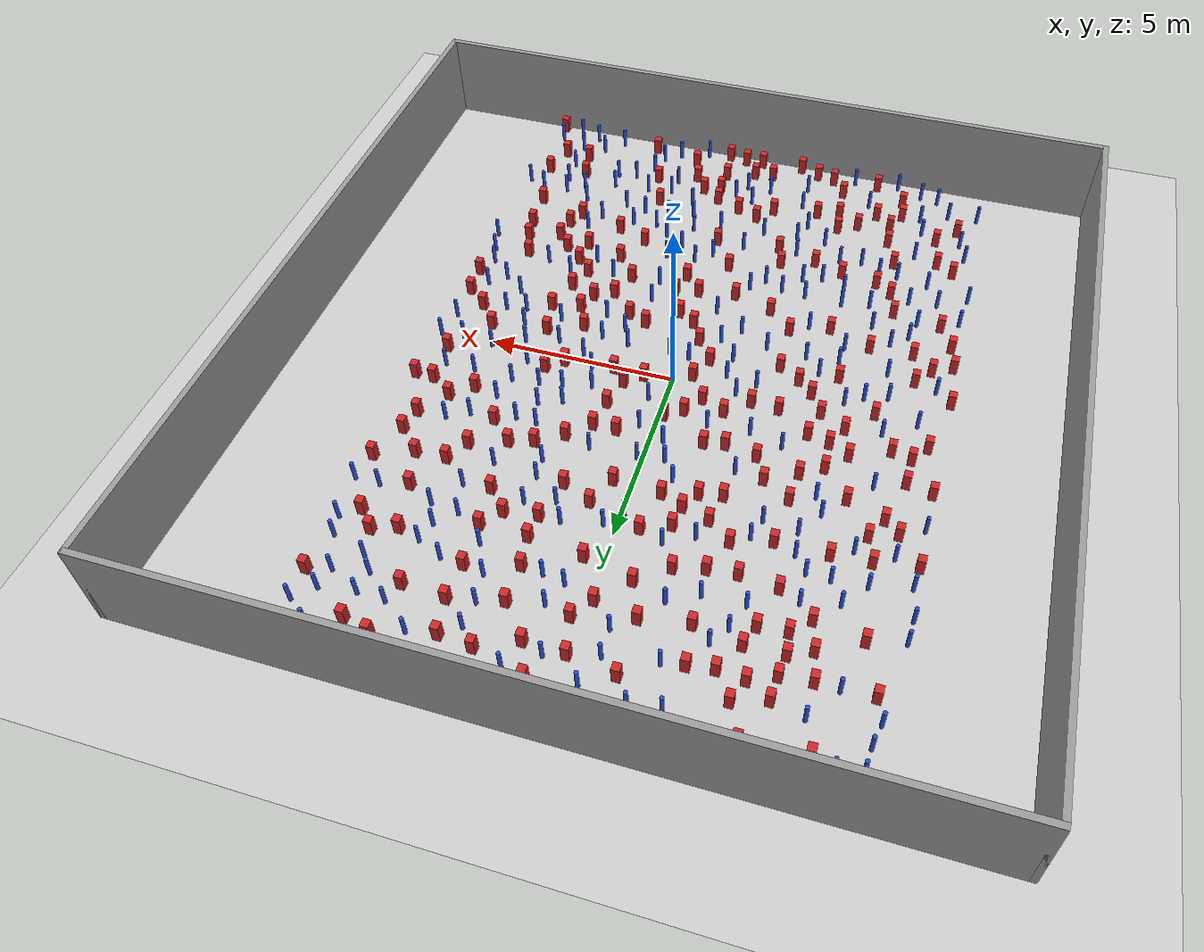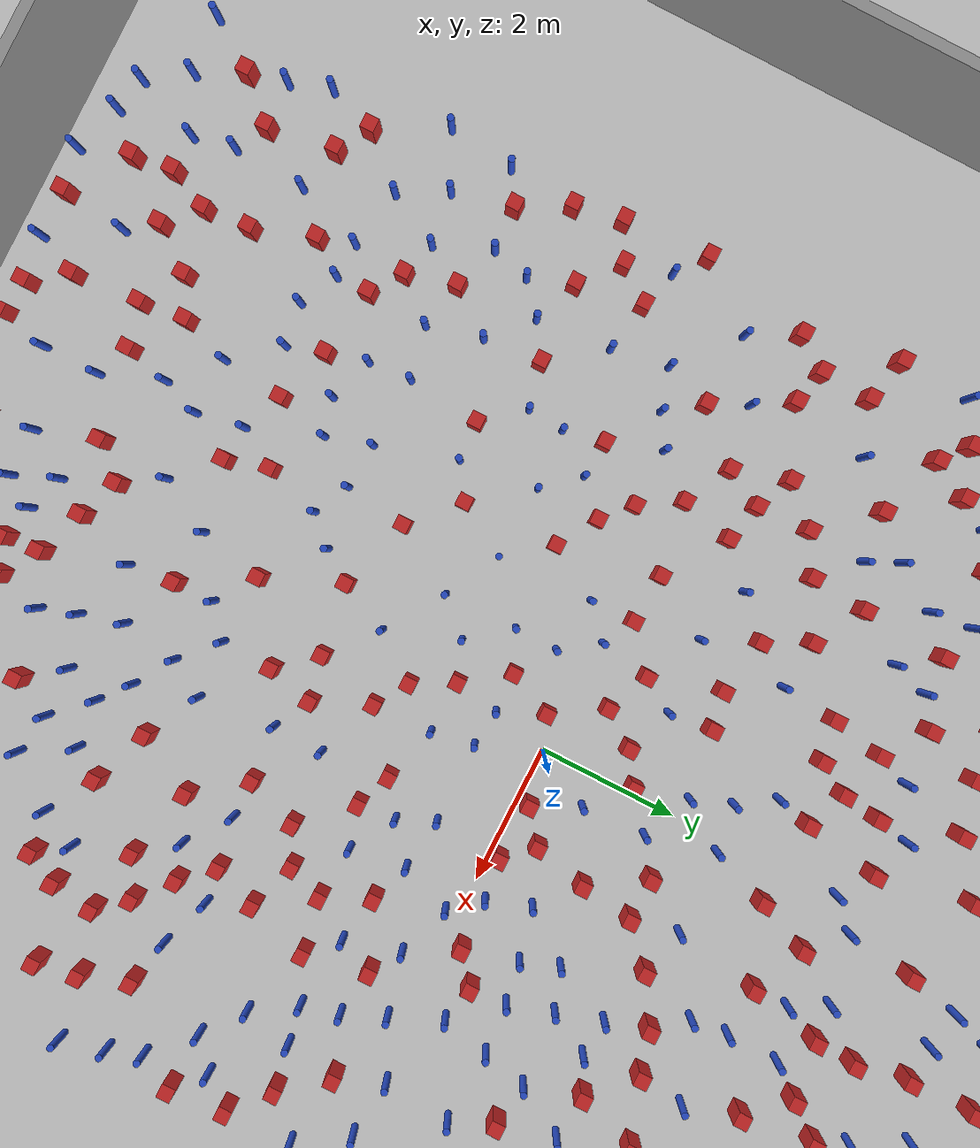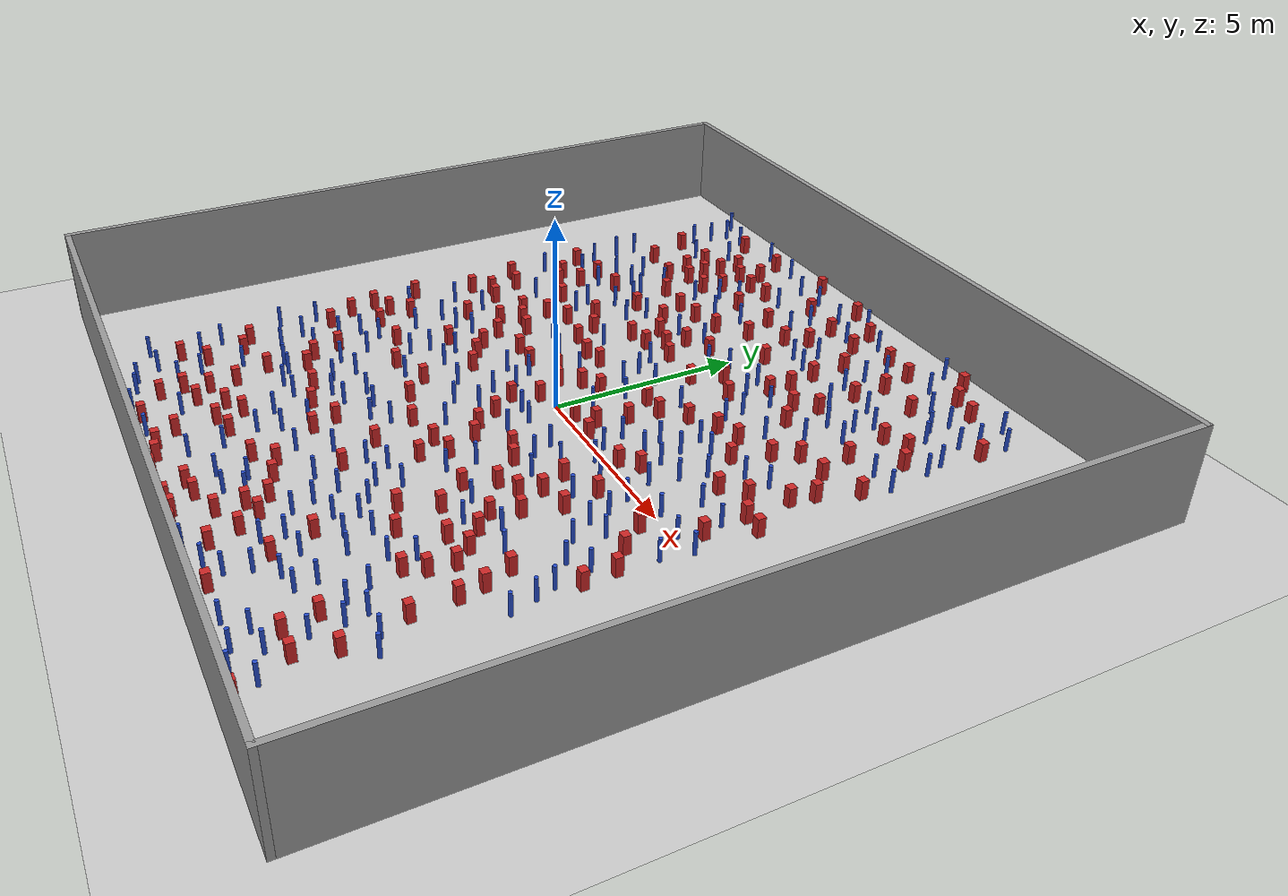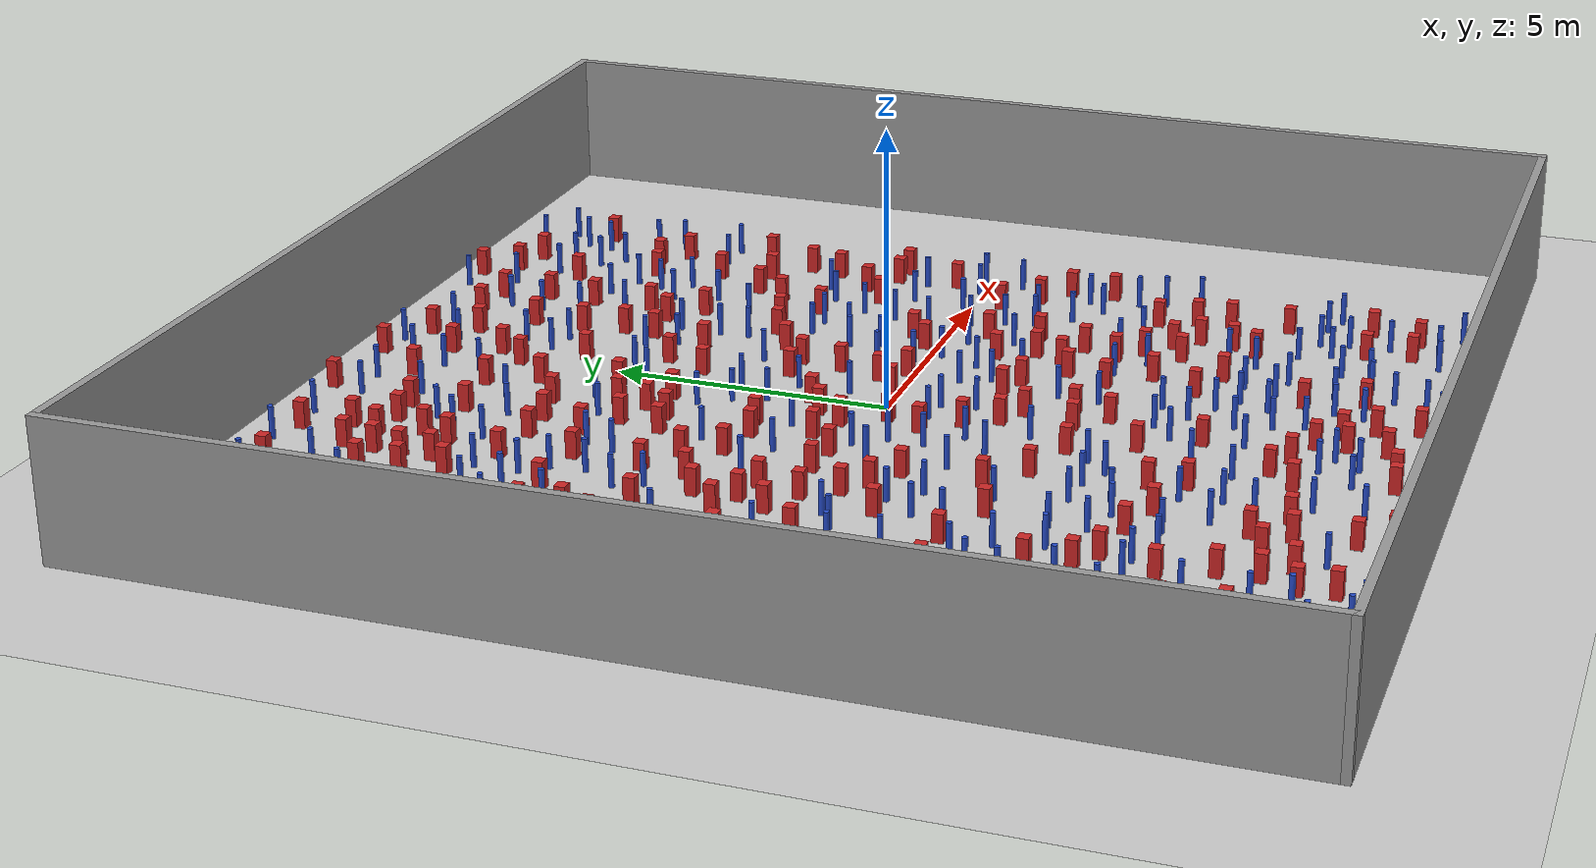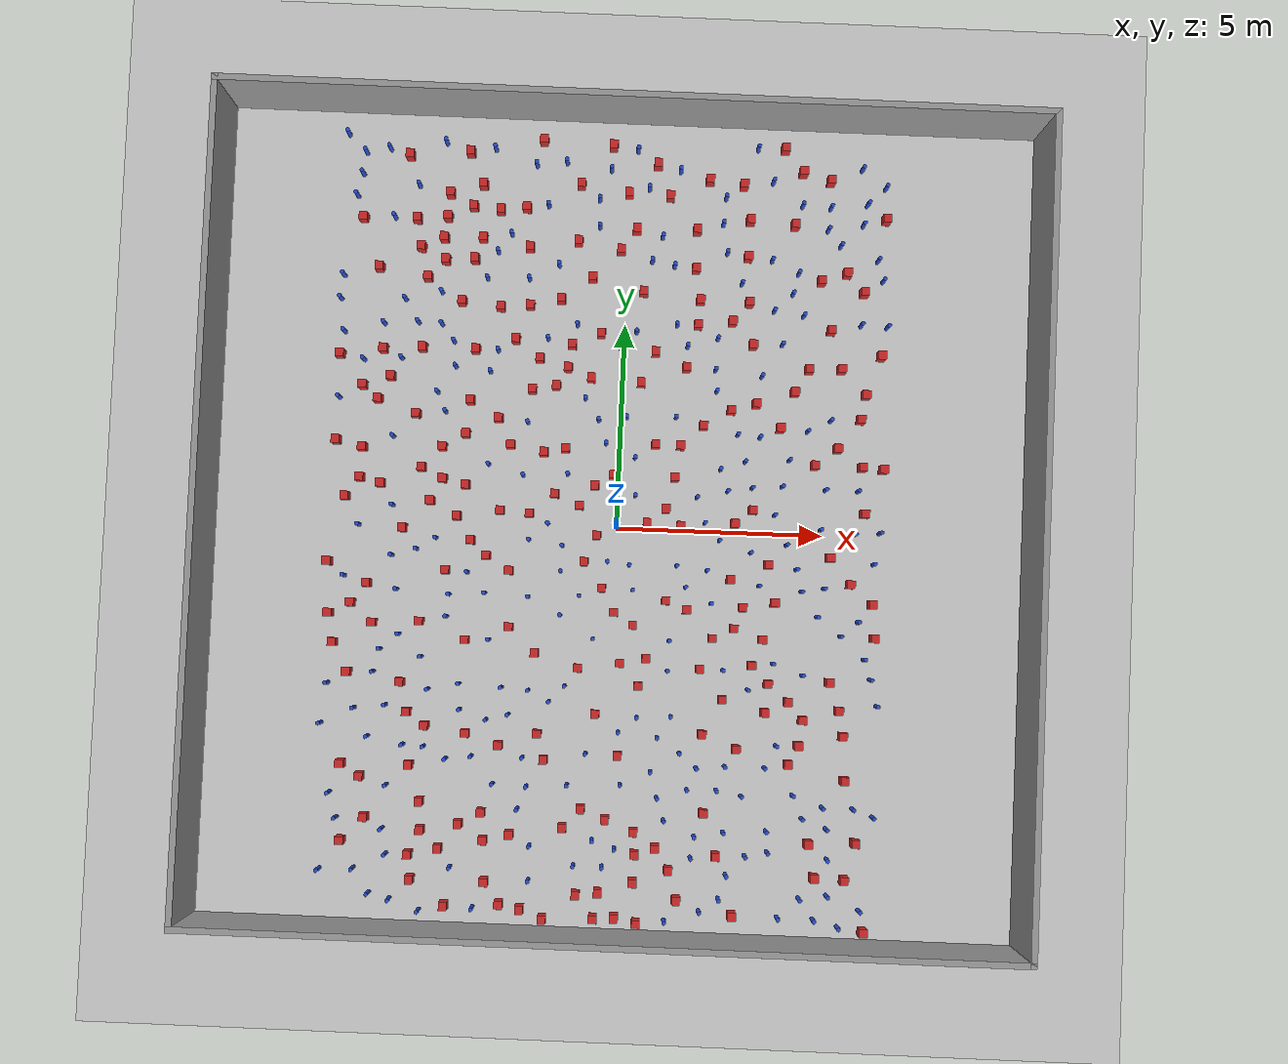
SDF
<sdf version="1.6">
 <world name="default">
  <light name="sun" type="directional">
   <pose>0 0 1000 0 -0 0</pose>
   <diffuse>0.8 0.8 0.8 1</diffuse>
   <specular>0.1 0.1 0.1 1</specular>
   <attenuation>
    <range>1000</range>
    <constant>0.9</constant>
    <linear>0.01</linear>
    <quadratic>0.001</quadratic>
   </attenuation>
   <direction>-0.5 0.5 -1</direction>
  </light>
  <model name="ground_plane">
   <static>1</static>
   <link name="link">
    <collision name="collision">
     <geometry><plane><normal>0 0 1</normal><size>100 100</size></plane></geometry>
     <surface><friction><ode><mu>100</mu><mu2>50</mu2></ode></friction></surface>
    </collision>
    <visual name="visual">
     <cast_shadows>0</cast_shadows>
     <geometry><plane><normal>0 0 1</normal><size>100 100</size></plane></geometry>
     <material>
      <ambient>1.0 1.0 1.0 1.0</ambient>
      <diffuse>0.8 0.8 0.8 1.0</diffuse>
      <specular>0.01 0.01 0.01 1.000000</specular>
     </material>
    </visual>
   </link>
  </model>
  <gravity>0 0 -9.8</gravity>
  <magnetic_field>6e-06 2.3e-05 -4.2e-05</magnetic_field>
  <atmosphere type="adiabatic"/>
  <physics name="default_physics" default="0" type="ode">
   <max_step_size>0.001</max_step_size>
   <real_time_factor>1</real_time_factor>
   <real_time_update_rate>1000</real_time_update_rate>
  </physics>
  <scene><ambient>0.4 0.4 0.4 1</ambient><background>0.7 0.7 0.7 1</background><shadows>1</shadows></scene>
  <spherical_coordinates>
   <surface_model>EARTH_WGS84</surface_model>
   <latitude_deg>0</latitude_deg>
   <longitude_deg>0</longitude_deg>
   <elevation>0</elevation>
   <heading_deg>0</heading_deg>
  </spherical_coordinates>
  <plugin name="gazebo_occupancy_map" filename="libgazebo_2Dmap_plugin.so">
   <map_resolution>0.05</map_resolution>
   <map_topic>generated_map</map_topic>
   <map_height>0.01</map_height>
   <map_size_x>50</map_size_x>
   <map_size_y>50</map_size_y>
  </plugin>
  <model name="NamedLocations">
   <static>true</static>
   <link name="DefaultStart"><pose>8.5 0 0 0 0 3.14</pose></link>
  </model>
  <model name="20x20_walls">
   <pose>0.044518 0.176112 0 0 -0 0</pose>
   <link name="Wall_1">
    <collision name="Wall_1_Collision">
     <geometry><box><size>20 0.15 2.5</size></box></geometry>
     <pose>0 0 1.25 0 -0 0</pose>
    </collision>
    <visual name="Wall_1_Visual">
     <pose>0 0 1.25 0 -0 0</pose>
     <geometry><box><size>20 0.15 2.5</size></box></geometry>
     <material>
      <script><uri>file://media/materials/scripts/gazebo.material</uri><name>Gazebo/Grey</name></script>
      <ambient>0.976471 0.992157 1 1</ambient>
     </material>
     <meta><layer>0</layer></meta>
    </visual>
    <pose>0 9.925 0 0 -0 0</pose>
   </link>
   <link name="Wall_3">
    <collision name="Wall_3_Collision">
     <geometry><box><size>20 0.15 2.5</size></box></geometry>
     <pose>0 0 1.25 0 -0 0</pose>
    </collision>
    <visual name="Wall_3_Visual">
     <pose>0 0 1.25 0 -0 0</pose>
     <geometry><box><size>20 0.15 2.5</size></box></geometry>
     <material>
      <script><uri>file://media/materials/scripts/gazebo.material</uri><name>Gazebo/Grey</name></script>
      <ambient>0.976471 0.992157 1 1</ambient>
     </material>
     <meta><layer>0</layer></meta>
    </visual>
    <pose>9.925 0 0 0 0 -1.5708</pose>
   </link>
   <link name="Wall_4">
    <collision name="Wall_4_Collision">
     <geometry><box><size>20 0.15 2.5</size></box></geometry>
     <pose>0 0 1.25 0 -0 0</pose>
    </collision>
    <visual name="Wall_4_Visual">
     <pose>0 0 1.25 0 -0 0</pose>
     <geometry><box><size>20 0.15 2.5</size></box></geometry>
     <material>
      <script><uri>file://media/materials/scripts/gazebo.material</uri><name>Gazebo/Grey</name></script>
      <ambient>0.976471 0.992157 1 1</ambient>
     </material>
     <meta><layer>0</layer></meta>
    </visual>
    <pose>0 -9.925 0 0 -0 3.14159</pose>
   </link>
   <link name="Wall_5">
    <collision name="Wall_5_Collision">
     <geometry><box><size>20 0.15 2.5</size></box></geometry>
     <pose>0 0 1.25 0 -0 0</pose>
    </collision>
    <visual name="Wall_5_Visual">
     <pose>0 0 1.25 0 -0 0</pose>
     <geometry><box><size>20 0.15 2.5</size></box></geometry>
     <material>
      <script><uri>file://media/materials/scripts/gazebo.material</uri><name>Gazebo/Grey</name></script>
      <ambient>0.976471 0.992157 1 1</ambient>
     </material>
     <meta><layer>0</layer></meta>
    </visual>
    <pose>-9.925 0 0 0 -0 1.5708</pose>
   </link>
   <static>1</static>
  </model>
  <model name="pole_obstacle0">
   <static>true</static>
   <pose>-1.68350599298 0.0406684492823 2.88873142074e-08 -9.90536689842e-09 4.60219948989e-07 -1.20965994962e-07</pose>
   <link name="link">
    <pose>0 0 0.3 0 -0 0</pose>
    <inertial>
     <mass>1</mass>
     <inertia><ixx>0.145833</ixx><ixy>0</ixy><ixz>0</ixz><iyy>0.145833</iyy><iyz>0</iyz><izz>0.125</izz></inertia>
    </inertial>
    <collision name="collision">
     <geometry><cylinder><radius>0.05</radius><length>.6</length></cylinder></geometry>
    </collision>
    <visual name="visual">
     <geometry><cylinder><radius>0.05</radius><length>.6</length></cylinder></geometry>
     <material>
      <script><name>Gazebo/Blue</name><uri>file://media/materials/scripts/gazebo.material</uri></script>
     </material>
    </visual>
   </link>
  </model>
  <model name="pole_obstacle1">
   <static>true</static>
   <pose>4.14799465705 -0.242558096195 2.88873142074e-08 -9.90536689628e-09 4.60219948994e-07 -1.20965994959e-07</pose>
   <link name="link">
    <pose>0 0 0.3 0 -0 0</pose>
    <inertial>
     <mass>1</mass>
     <inertia><ixx>0.145833</ixx><ixy>0</ixy><ixz>0</ixz><iyy>0.145833</iyy><iyz>0</iyz><izz>0.125</izz></inertia>
    </inertial>
    <collision name="collision">
     <geometry><cylinder><radius>0.05</radius><length>.6</length></cylinder></geometry>
    </collision>
    <visual name="visual">
     <geometry><cylinder><radius>0.05</radius><length>.6</length></cylinder></geometry>
     <material>
      <script><name>Gazebo/Blue</name><uri>file://media/materials/scripts/gazebo.material</uri></script>
     </material>
    </visual>
   </link>
  </model>
  <model name="square_post_obstacle0">
   <static>true</static>
   <pose>3.7188085456 -0.741724730192 8.22691968438e-08 7.2212513382e-06 -7.54495500217e-07 2.29674213826e-05</pose>
   <link name="link">
    <pose>0 0 0.25 0 -0 0</pose>
    <inertial>
     <mass>100</mass>
     <inertia>
      <ixx>0.166667</ixx>
      <ixy>0</ixy>
      <ixz>0</ixz>
      <iyy>0.166667</iyy>
      <iyz>0</iyz>
      <izz>0.166667</izz>
     </inertia>
    </inertial>
    <collision name="collision"><geometry><box><size>.2 .2 .5</size></box></geometry></collision>
    <visual name="visual">
     <geometry><box><size>.2 .2 .5</size></box></geometry>
     <material>
      <script><name>Gazebo/Red</name><uri>file://media/materials/scripts/gazebo.material</uri></script>
     </material>
    </visual>
   </link>
  </model>
  <model name="square_post_obstacle1">
   <static>true</static>
   <pose>-4.90250389428 -4.65305402818 8.22691968438e-08 7.22125133819e-06 -7.54495500217e-07 2.29674213826e-05</pose>
   <link name="link">
    <pose>0 0 0.25 0 -0 0</pose>
    <inertial>
     <mass>100</mass>
     <inertia>
      <ixx>0.166667</ixx>
      <ixy>0</ixy>
      <ixz>0</ixz>
      <iyy>0.166667</iyy>
      <iyz>0</iyz>
      <izz>0.166667</izz>
     </inertia>
    </inertial>
    <collision name="collision"><geometry><box><size>.2 .2 .5</size></box></geometry></collision>
    <visual name="visual">
     <geometry><box><size>.2 .2 .5</size></box></geometry>
     <material>
      <script><name>Gazebo/Red</name><uri>file://media/materials/scripts/gazebo.material</uri></script>
     </material>
    </visual>
   </link>
  </model>
  <model name="pole_obstacle2">
   <static>true</static>
   <pose>2.84008630168 -5.65758874039 2.88873142074e-08 -9.90536689859e-09 4.60219948989e-07 -1.20965994961e-07</pose>
   <link name="link">
    <pose>0 0 0.3 0 -0 0</pose>
    <inertial>
     <mass>1</mass>
     <inertia><ixx>0.145833</ixx><ixy>0</ixy><ixz>0</ixz><iyy>0.145833</iyy><iyz>0</iyz><izz>0.125</izz></inertia>
    </inertial>
    <collision name="collision">
     <geometry><cylinder><radius>0.05</radius><length>.6</length></cylinder></geometry>
    </collision>
    <visual name="visual">
     <geometry><cylinder><radius>0.05</radius><length>.6</length></cylinder></geometry>
     <material>
      <script><name>Gazebo/Blue</name><uri>file://media/materials/scripts/gazebo.material</uri></script>
     </material>
    </visual>
   </link>
  </model>
  <model name="pole_obstacle3">
   <static>true</static>
   <pose>3.50815053326 -1.26298609997 2.88873142074e-08 -9.90536689395e-09 4.60219949e-07 -1.20965994953e-07</pose>
   <link name="link">
    <pose>0 0 0.3 0 -0 0</pose>
    <inertial>
     <mass>1</mass>
     <inertia><ixx>0.145833</ixx><ixy>0</ixy><ixz>0</ixz><iyy>0.145833</iyy><iyz>0</iyz><izz>0.125</izz></inertia>
    </inertial>
    <collision name="collision">
     <geometry><cylinder><radius>0.05</radius><length>.6</length></cylinder></geometry>
    </collision>
    <visual name="visual">
     <geometry><cylinder><radius>0.05</radius><length>.6</length></cylinder></geometry>
     <material>
      <script><name>Gazebo/Blue</name><uri>file://media/materials/scripts/gazebo.material</uri></script>
     </material>
    </visual>
   </link>
  </model>
  <model name="pole_obstacle4">
   <static>true</static>
   <pose>3.80544619655 -5.65283648893 2.88873142074e-08 -9.90536689859e-09 4.60219948989e-07 -1.20965994961e-07</pose>
   <link name="link">
    <pose>0 0 0.3 0 -0 0</pose>
    <inertial>
     <mass>1</mass>
     <inertia><ixx>0.145833</ixx><ixy>0</ixy><ixz>0</ixz><iyy>0.145833</iyy><iyz>0</iyz><izz>0.125</izz></inertia>
    </inertial>
    <collision name="collision">
     <geometry><cylinder><radius>0.05</radius><length>.6</length></cylinder></geometry>
    </collision>
    <visual name="visual">
     <geometry><cylinder><radius>0.05</radius><length>.6</length></cylinder></geometry>
     <material>
      <script><name>Gazebo/Blue</name><uri>file://media/materials/scripts/gazebo.material</uri></script>
     </material>
    </visual>
   </link>
  </model>
  <model name="pole_obstacle5">
   <static>true</static>
   <pose>-1.78726646543 -8.57034392381 2.88873142074e-08 -9.90536690474e-09 4.60219948974e-07 -1.2096599497e-07</pose>
   <link name="link">
    <pose>0 0 0.3 0 -0 0</pose>
    <inertial>
     <mass>1</mass>
     <inertia><ixx>0.145833</ixx><ixy>0</ixy><ixz>0</ixz><iyy>0.145833</iyy><iyz>0</iyz><izz>0.125</izz></inertia>
    </inertial>
    <collision name="collision">
     <geometry><cylinder><radius>0.05</radius><length>.6</length></cylinder></geometry>
    </collision>
    <visual name="visual">
     <geometry><cylinder><radius>0.05</radius><length>.6</length></cylinder></geometry>
     <material>
      <script><name>Gazebo/Blue</name><uri>file://media/materials/scripts/gazebo.material</uri></script>
     </material>
    </visual>
   </link>
  </model>
  <model name="pole_obstacle6">
   <static>true</static>
   <pose>-5.39871481957 5.40372556188 2.88873142074e-08 -9.90536690842e-09 4.60219948965e-07 -1.20965994976e-07</pose>
   <link name="link">
    <pose>0 0 0.3 0 -0 0</pose>
    <inertial>
     <mass>1</mass>
     <inertia><ixx>0.145833</ixx><ixy>0</ixy><ixz>0</ixz><iyy>0.145833</iyy><iyz>0</iyz><izz>0.125</izz></inertia>
    </inertial>
    <collision name="collision">
     <geometry><cylinder><radius>0.05</radius><length>.6</length></cylinder></geometry>
    </collision>
    <visual name="visual">
     <geometry><cylinder><radius>0.05</radius><length>.6</length></cylinder></geometry>
     <material>
      <script><name>Gazebo/Blue</name><uri>file://media/materials/scripts/gazebo.material</uri></script>
     </material>
    </visual>
   </link>
  </model>
  <model name="square_post_obstacle2">
   <static>true</static>
   <pose>-0.308446318103 -1.4751853889 8.22691968438e-08 7.2212513382e-06 -7.54495500217e-07 2.29674213826e-05</pose>
   <link name="link">
    <pose>0 0 0.25 0 -0 0</pose>
    <inertial>
     <mass>100</mass>
     <inertia>
      <ixx>0.166667</ixx>
      <ixy>0</ixy>
      <ixz>0</ixz>
      <iyy>0.166667</iyy>
      <iyz>0</iyz>
      <izz>0.166667</izz>
     </inertia>
    </inertial>
    <collision name="collision"><geometry><box><size>.2 .2 .5</size></box></geometry></collision>
    <visual name="visual">
     <geometry><box><size>.2 .2 .5</size></box></geometry>
     <material>
      <script><name>Gazebo/Red</name><uri>file://media/materials/scripts/gazebo.material</uri></script>
     </material>
    </visual>
   </link>
  </model>
  <model name="square_post_obstacle3">
   <static>true</static>
   <pose>1.82077374307 5.66131599917 8.22691968438e-08 7.2212513382e-06 -7.54495500217e-07 2.29674213826e-05</pose>
   <link name="link">
    <pose>0 0 0.25 0 -0 0</pose>
    <inertial>
     <mass>100</mass>
     <inertia>
      <ixx>0.166667</ixx>
      <ixy>0</ixy>
      <ixz>0</ixz>
      <iyy>0.166667</iyy>
      <iyz>0</iyz>
      <izz>0.166667</izz>
     </inertia>
    </inertial>
    <collision name="collision"><geometry><box><size>.2 .2 .5</size></box></geometry></collision>
    <visual name="visual">
     <geometry><box><size>.2 .2 .5</size></box></geometry>
     <material>
      <script><name>Gazebo/Red</name><uri>file://media/materials/scripts/gazebo.material</uri></script>
     </material>
    </visual>
   </link>
  </model>
  <model name="square_post_obstacle4">
   <static>true</static>
   <pose>-2.64927681659 -5.37120156924 8.22691968438e-08 7.2212513382e-06 -7.54495500217e-07 2.29674213826e-05</pose>
   <link name="link">
    <pose>0 0 0.25 0 -0 0</pose>
    <inertial>
     <mass>100</mass>
     <inertia>
      <ixx>0.166667</ixx>
      <ixy>0</ixy>
      <ixz>0</ixz>
      <iyy>0.166667</iyy>
      <iyz>0</iyz>
      <izz>0.166667</izz>
     </inertia>
    </inertial>
    <collision name="collision"><geometry><box><size>.2 .2 .5</size></box></geometry></collision>
    <visual name="visual">
     <geometry><box><size>.2 .2 .5</size></box></geometry>
     <material>
      <script><name>Gazebo/Red</name><uri>file://media/materials/scripts/gazebo.material</uri></script>
     </material>
    </visual>
   </link>
  </model>
  <model name="pole_obstacle7">
   <static>true</static>
   <pose>2.25478810606 3.96422539197 2.88873142074e-08 -9.90536690801e-09 4.60219948966e-07 -1.20965994976e-07</pose>
   <link name="link">
    <pose>0 0 0.3 0 -0 0</pose>
    <inertial>
     <mass>1</mass>
     <inertia><ixx>0.145833</ixx><ixy>0</ixy><ixz>0</ixz><iyy>0.145833</iyy><iyz>0</iyz><izz>0.125</izz></inertia>
    </inertial>
    <collision name="collision">
     <geometry><cylinder><radius>0.05</radius><length>.6</length></cylinder></geometry>
    </collision>
    <visual name="visual">
     <geometry><cylinder><radius>0.05</radius><length>.6</length></cylinder></geometry>
     <material>
      <script><name>Gazebo/Blue</name><uri>file://media/materials/scripts/gazebo.material</uri></script>
     </material>
    </visual>
   </link>
  </model>
  <model name="pole_obstacle8">
   <static>true</static>
   <pose>-3.14532580014 -1.7083198443 2.88873142074e-08 -9.90536689395e-09 4.60219949e-07 -1.20965994953e-07</pose>
   <link name="link">
    <pose>0 0 0.3 0 -0 0</pose>
    <inertial>
     <mass>1</mass>
     <inertia><ixx>0.145833</ixx><ixy>0</ixy><ixz>0</ixz><iyy>0.145833</iyy><iyz>0</iyz><izz>0.125</izz></inertia>
    </inertial>
    <collision name="collision">
     <geometry><cylinder><radius>0.05</radius><length>.6</length></cylinder></geometry>
    </collision>
    <visual name="visual">
     <geometry><cylinder><radius>0.05</radius><length>.6</length></cylinder></geometry>
     <material>
      <script><name>Gazebo/Blue</name><uri>file://media/materials/scripts/gazebo.material</uri></script>
     </material>
    </visual>
   </link>
  </model>
  <model name="square_post_obstacle5">
   <static>true</static>
   <pose>-3.76853762115 2.15480070877 8.22691968438e-08 7.2212513382e-06 -7.54495500217e-07 2.29674213826e-05</pose>
   <link name="link">
    <pose>0 0 0.25 0 -0 0</pose>
    <inertial>
     <mass>100</mass>
     <inertia>
      <ixx>0.166667</ixx>
      <ixy>0</ixy>
      <ixz>0</ixz>
      <iyy>0.166667</iyy>
      <iyz>0</iyz>
      <izz>0.166667</izz>
     </inertia>
    </inertial>
    <collision name="collision"><geometry><box><size>.2 .2 .5</size></box></geometry></collision>
    <visual name="visual">
     <geometry><box><size>.2 .2 .5</size></box></geometry>
     <material>
      <script><name>Gazebo/Red</name><uri>file://media/materials/scripts/gazebo.material</uri></script>
     </material>
    </visual>
   </link>
  </model>
  <model name="square_post_obstacle6">
   <static>true</static>
   <pose>-5.44352288722 8.96728063291 8.22691968438e-08 7.22125133819e-06 -7.54495500217e-07 2.29674213826e-05</pose>
   <link name="link">
    <pose>0 0 0.25 0 -0 0</pose>
    <inertial>
     <mass>100</mass>
     <inertia>
      <ixx>0.166667</ixx>
      <ixy>0</ixy>
      <ixz>0</ixz>
      <iyy>0.166667</iyy>
      <iyz>0</iyz>
      <izz>0.166667</izz>
     </inertia>
    </inertial>
    <collision name="collision"><geometry><box><size>.2 .2 .5</size></box></geometry></collision>
    <visual name="visual">
     <geometry><box><size>.2 .2 .5</size></box></geometry>
     <material>
      <script><name>Gazebo/Red</name><uri>file://media/materials/scripts/gazebo.material</uri></script>
     </material>
    </visual>
   </link>
  </model>
  <model name="square_post_obstacle7">
   <static>true</static>
   <pose>-4.49373699761 -6.79137119948 8.22691968438e-08 7.22125133819e-06 -7.54495500217e-07 2.29674213826e-05</pose>
   <link name="link">
    <pose>0 0 0.25 0 -0 0</pose>
    <inertial>
     <mass>100</mass>
     <inertia>
      <ixx>0.166667</ixx>
      <ixy>0</ixy>
      <ixz>0</ixz>
      <iyy>0.166667</iyy>
      <iyz>0</iyz>
      <izz>0.166667</izz>
     </inertia>
    </inertial>
    <collision name="collision"><geometry><box><size>.2 .2 .5</size></box></geometry></collision>
    <visual name="visual">
     <geometry><box><size>.2 .2 .5</size></box></geometry>
     <material>
      <script><name>Gazebo/Red</name><uri>file://media/materials/scripts/gazebo.material</uri></script>
     </material>
    </visual>
   </link>
  </model>
  <model name="pole_obstacle9">
   <static>true</static>
   <pose>-5.29403124676 -1.7001412889 2.88873142074e-08 -9.90536689445e-09 4.60219948999e-07 -1.20965994956e-07</pose>
   <link name="link">
    <pose>0 0 0.3 0 -0 0</pose>
    <inertial>
     <mass>1</mass>
     <inertia><ixx>0.145833</ixx><ixy>0</ixy><ixz>0</ixz><iyy>0.145833</iyy><iyz>0</iyz><izz>0.125</izz></inertia>
    </inertial>
    <collision name="collision">
     <geometry><cylinder><radius>0.05</radius><length>.6</length></cylinder></geometry>
    </collision>
    <visual name="visual">
     <geometry><cylinder><radius>0.05</radius><length>.6</length></cylinder></geometry>
     <material>
      <script><name>Gazebo/Blue</name><uri>file://media/materials/scripts/gazebo.material</uri></script>
     </material>
    </visual>
   </link>
  </model>
  <model name="pole_obstacle10">
   <static>true</static>
   <pose>-1.29376996693 -2.16636897197 2.88873142074e-08 -9.90536689791e-09 4.6021994899e-07 -1.20965994959e-07</pose>
   <link name="link">
    <pose>0 0 0.3 0 -0 0</pose>
    <inertial>
     <mass>1</mass>
     <inertia><ixx>0.145833</ixx><ixy>0</ixy><ixz>0</ixz><iyy>0.145833</iyy><iyz>0</iyz><izz>0.125</izz></inertia>
    </inertial>
    <collision name="collision">
     <geometry><cylinder><radius>0.05</radius><length>.6</length></cylinder></geometry>
    </collision>
    <visual name="visual">
     <geometry><cylinder><radius>0.05</radius><length>.6</length></cylinder></geometry>
     <material>
      <script><name>Gazebo/Blue</name><uri>file://media/materials/scripts/gazebo.material</uri></script>
     </material>
    </visual>
   </link>
  </model>
  <model name="pole_obstacle11">
   <static>true</static>
   <pose>-2.08052585455 -1.75644054801 2.88873142074e-08 -9.90536689395e-09 4.60219949e-07 -1.20965994953e-07</pose>
   <link name="link">
    <pose>0 0 0.3 0 -0 0</pose>
    <inertial>
     <mass>1</mass>
     <inertia><ixx>0.145833</ixx><ixy>0</ixy><ixz>0</ixz><iyy>0.145833</iyy><iyz>0</iyz><izz>0.125</izz></inertia>
    </inertial>
    <collision name="collision">
     <geometry><cylinder><radius>0.05</radius><length>.6</length></cylinder></geometry>
    </collision>
    <visual name="visual">
     <geometry><cylinder><radius>0.05</radius><length>.6</length></cylinder></geometry>
     <material>
      <script><name>Gazebo/Blue</name><uri>file://media/materials/scripts/gazebo.material</uri></script>
     </material>
    </visual>
   </link>
  </model>
  <model name="pole_obstacle12">
   <static>true</static>
   <pose>2.28259964185 4.73559105646 2.88873142074e-08 -9.90536689859e-09 4.60219948989e-07 -1.20965994961e-07</pose>
   <link name="link">
    <pose>0 0 0.3 0 -0 0</pose>
    <inertial>
     <mass>1</mass>
     <inertia><ixx>0.145833</ixx><ixy>0</ixy><ixz>0</ixz><iyy>0.145833</iyy><iyz>0</iyz><izz>0.125</izz></inertia>
    </inertial>
    <collision name="collision">
     <geometry><cylinder><radius>0.05</radius><length>.6</length></cylinder></geometry>
    </collision>
    <visual name="visual">
     <geometry><cylinder><radius>0.05</radius><length>.6</length></cylinder></geometry>
     <material>
      <script><name>Gazebo/Blue</name><uri>file://media/materials/scripts/gazebo.material</uri></script>
     </material>
    </visual>
   </link>
  </model>
  <model name="square_post_obstacle8">
   <static>true</static>
   <pose>1.7828839494 5.05060380891 8.22691968438e-08 7.2212513382e-06 -7.54495500217e-07 2.29674213826e-05</pose>
   <link name="link">
    <pose>0 0 0.25 0 -0 0</pose>
    <inertial>
     <mass>100</mass>
     <inertia>
      <ixx>0.166667</ixx>
      <ixy>0</ixy>
      <ixz>0</ixz>
      <iyy>0.166667</iyy>
      <iyz>0</iyz>
      <izz>0.166667</izz>
     </inertia>
    </inertial>
    <collision name="collision"><geometry><box><size>.2 .2 .5</size></box></geometry></collision>
    <visual name="visual">
     <geometry><box><size>.2 .2 .5</size></box></geometry>
     <material>
      <script><name>Gazebo/Red</name><uri>file://media/materials/scripts/gazebo.material</uri></script>
     </material>
    </visual>
   </link>
  </model>
  <model name="square_post_obstacle9">
   <static>true</static>
   <pose>-2.40552962556 6.80216030799 8.22691968438e-08 7.2212513382e-06 -7.54495500217e-07 2.29674213826e-05</pose>
   <link name="link">
    <pose>0 0 0.25 0 -0 0</pose>
    <inertial>
     <mass>100</mass>
     <inertia>
      <ixx>0.166667</ixx>
      <ixy>0</ixy>
      <ixz>0</ixz>
      <iyy>0.166667</iyy>
      <iyz>0</iyz>
      <izz>0.166667</izz>
     </inertia>
    </inertial>
    <collision name="collision"><geometry><box><size>.2 .2 .5</size></box></geometry></collision>
    <visual name="visual">
     <geometry><box><size>.2 .2 .5</size></box></geometry>
     <material>
      <script><name>Gazebo/Red</name><uri>file://media/materials/scripts/gazebo.material</uri></script>
     </material>
    </visual>
   </link>
  </model>
  <model name="pole_obstacle13">
   <static>true</static>
   <pose>-5.18646854002 8.22817390246 2.88873142074e-08 -9.9053668967e-09 4.60219948993e-07 -1.20965994957e-07</pose>
   <link name="link">
    <pose>0 0 0.3 0 -0 0</pose>
    <inertial>
     <mass>1</mass>
     <inertia><ixx>0.145833</ixx><ixy>0</ixy><ixz>0</ixz><iyy>0.145833</iyy><iyz>0</iyz><izz>0.125</izz></inertia>
    </inertial>
    <collision name="collision">
     <geometry><cylinder><radius>0.05</radius><length>.6</length></cylinder></geometry>
    </collision>
    <visual name="visual">
     <geometry><cylinder><radius>0.05</radius><length>.6</length></cylinder></geometry>
     <material>
      <script><name>Gazebo/Blue</name><uri>file://media/materials/scripts/gazebo.material</uri></script>
     </material>
    </visual>
   </link>
  </model>
  <model name="square_post_obstacle10">
   <static>true</static>
   <pose>-5.87943998003 4.15990492513 8.22691968438e-08 7.2212513382e-06 -7.54495500217e-07 2.29674213826e-05</pose>
   <link name="link">
    <pose>0 0 0.25 0 -0 0</pose>
    <inertial>
     <mass>100</mass>
     <inertia>
      <ixx>0.166667</ixx>
      <ixy>0</ixy>
      <ixz>0</ixz>
      <iyy>0.166667</iyy>
      <iyz>0</iyz>
      <izz>0.166667</izz>
     </inertia>
    </inertial>
    <collision name="collision"><geometry><box><size>.2 .2 .5</size></box></geometry></collision>
    <visual name="visual">
     <geometry><box><size>.2 .2 .5</size></box></geometry>
     <material>
      <script><name>Gazebo/Red</name><uri>file://media/materials/scripts/gazebo.material</uri></script>
     </material>
    </visual>
   </link>
  </model>
  <model name="square_post_obstacle11">
   <static>true</static>
   <pose>-0.48001669954 -0.202716693142 8.22691968438e-08 7.2212513382e-06 -7.54495500217e-07 2.29674213826e-05</pose>
   <link name="link">
    <pose>0 0 0.25 0 -0 0</pose>
    <inertial>
     <mass>100</mass>
     <inertia>
      <ixx>0.166667</ixx>
      <ixy>0</ixy>
      <ixz>0</ixz>
      <iyy>0.166667</iyy>
      <iyz>0</iyz>
      <izz>0.166667</izz>
     </inertia>
    </inertial>
    <collision name="collision"><geometry><box><size>.2 .2 .5</size></box></geometry></collision>
    <visual name="visual">
     <geometry><box><size>.2 .2 .5</size></box></geometry>
     <material>
      <script><name>Gazebo/Red</name><uri>file://media/materials/scripts/gazebo.material</uri></script>
     </material>
    </visual>
   </link>
  </model>
  <model name="pole_obstacle14">
   <static>true</static>
   <pose>3.40435855166 -7.7819171107 2.88873142074e-08 -9.90536689859e-09 4.60219948989e-07 -1.20965994961e-07</pose>
   <link name="link">
    <pose>0 0 0.3 0 -0 0</pose>
    <inertial>
     <mass>1</mass>
     <inertia><ixx>0.145833</ixx><ixy>0</ixy><ixz>0</ixz><iyy>0.145833</iyy><iyz>0</iyz><izz>0.125</izz></inertia>
    </inertial>
    <collision name="collision">
     <geometry><cylinder><radius>0.05</radius><length>.6</length></cylinder></geometry>
    </collision>
    <visual name="visual">
     <geometry><cylinder><radius>0.05</radius><length>.6</length></cylinder></geometry>
     <material>
      <script><name>Gazebo/Blue</name><uri>file://media/materials/scripts/gazebo.material</uri></script>
     </material>
    </visual>
   </link>
  </model>
  <model name="pole_obstacle15">
   <static>true</static>
   <pose>-3.24099631018 3.70086770834 2.88873142074e-08 -9.90536689597e-09 4.60219948995e-07 -1.20965994957e-07</pose>
   <link name="link">
    <pose>0 0 0.3 0 -0 0</pose>
    <inertial>
     <mass>1</mass>
     <inertia><ixx>0.145833</ixx><ixy>0</ixy><ixz>0</ixz><iyy>0.145833</iyy><iyz>0</iyz><izz>0.125</izz></inertia>
    </inertial>
    <collision name="collision">
     <geometry><cylinder><radius>0.05</radius><length>.6</length></cylinder></geometry>
    </collision>
    <visual name="visual">
     <geometry><cylinder><radius>0.05</radius><length>.6</length></cylinder></geometry>
     <material>
      <script><name>Gazebo/Blue</name><uri>file://media/materials/scripts/gazebo.material</uri></script>
     </material>
    </visual>
   </link>
  </model>
  <model name="square_post_obstacle12">
   <static>true</static>
   <pose>-4.40617375858 8.05628131034 8.22691968438e-08 7.22125133819e-06 -7.54495500217e-07 2.29674213826e-05</pose>
   <link name="link">
    <pose>0 0 0.25 0 -0 0</pose>
    <inertial>
     <mass>100</mass>
     <inertia>
      <ixx>0.166667</ixx>
      <ixy>0</ixy>
      <ixz>0</ixz>
      <iyy>0.166667</iyy>
      <iyz>0</iyz>
      <izz>0.166667</izz>
     </inertia>
    </inertial>
    <collision name="collision"><geometry><box><size>.2 .2 .5</size></box></geometry></collision>
    <visual name="visual">
     <geometry><box><size>.2 .2 .5</size></box></geometry>
     <material>
      <script><name>Gazebo/Red</name><uri>file://media/materials/scripts/gazebo.material</uri></script>
     </material>
    </visual>
   </link>
  </model>
  <model name="pole_obstacle16">
   <static>true</static>
   <pose>5.23208228533 -6.54759362288 2.88873142074e-08 -9.90536690842e-09 4.60219948965e-07 -1.20965994976e-07</pose>
   <link name="link">
    <pose>0 0 0.3 0 -0 0</pose>
    <inertial>
     <mass>1</mass>
     <inertia><ixx>0.145833</ixx><ixy>0</ixy><ixz>0</ixz><iyy>0.145833</iyy><iyz>0</iyz><izz>0.125</izz></inertia>
    </inertial>
    <collision name="collision">
     <geometry><cylinder><radius>0.05</radius><length>.6</length></cylinder></geometry>
    </collision>
    <visual name="visual">
     <geometry><cylinder><radius>0.05</radius><length>.6</length></cylinder></geometry>
     <material>
      <script><name>Gazebo/Blue</name><uri>file://media/materials/scripts/gazebo.material</uri></script>
     </material>
    </visual>
   </link>
  </model>
  <model name="pole_obstacle17">
   <static>true</static>
   <pose>0.289858138714 4.8147940718 2.88873142074e-08 -9.90536689592e-09 4.60219948995e-07 -1.20965994956e-07</pose>
   <link name="link">
    <pose>0 0 0.3 0 -0 0</pose>
    <inertial>
     <mass>1</mass>
     <inertia><ixx>0.145833</ixx><ixy>0</ixy><ixz>0</ixz><iyy>0.145833</iyy><iyz>0</iyz><izz>0.125</izz></inertia>
    </inertial>
    <collision name="collision">
     <geometry><cylinder><radius>0.05</radius><length>.6</length></cylinder></geometry>
    </collision>
    <visual name="visual">
     <geometry><cylinder><radius>0.05</radius><length>.6</length></cylinder></geometry>
     <material>
      <script><name>Gazebo/Blue</name><uri>file://media/materials/scripts/gazebo.material</uri></script>
     </material>
    </visual>
   </link>
  </model>
  <model name="square_post_obstacle13">
   <static>true</static>
   <pose>-2.84766875559 -8.64489960233 8.22691968438e-08 7.22125133819e-06 -7.54495500217e-07 2.29674213826e-05</pose>
   <link name="link">
    <pose>0 0 0.25 0 -0 0</pose>
    <inertial>
     <mass>100</mass>
     <inertia>
      <ixx>0.166667</ixx>
      <ixy>0</ixy>
      <ixz>0</ixz>
      <iyy>0.166667</iyy>
      <iyz>0</iyz>
      <izz>0.166667</izz>
     </inertia>
    </inertial>
    <collision name="collision"><geometry><box><size>.2 .2 .5</size></box></geometry></collision>
    <visual name="visual">
     <geometry><box><size>.2 .2 .5</size></box></geometry>
     <material>
      <script><name>Gazebo/Red</name><uri>file://media/materials/scripts/gazebo.material</uri></script>
     </material>
    </visual>
   </link>
  </model>
  <model name="pole_obstacle18">
   <static>true</static>
   <pose>-1.31122346371 -0.481827673898 2.88873142074e-08 -9.90536689816e-09 4.6021994899e-07 -1.2096599496e-07</pose>
   <link name="link">
    <pose>0 0 0.3 0 -0 0</pose>
    <inertial>
     <mass>1</mass>
     <inertia><ixx>0.145833</ixx><ixy>0</ixy><ixz>0</ixz><iyy>0.145833</iyy><iyz>0</iyz><izz>0.125</izz></inertia>
    </inertial>
    <collision name="collision">
     <geometry><cylinder><radius>0.05</radius><length>.6</length></cylinder></geometry>
    </collision>
    <visual name="visual">
     <geometry><cylinder><radius>0.05</radius><length>.6</length></cylinder></geometry>
     <material>
      <script><name>Gazebo/Blue</name><uri>file://media/materials/scripts/gazebo.material</uri></script>
     </material>
    </visual>
   </link>
  </model>
  <model name="square_post_obstacle14">
   <static>true</static>
   <pose>-4.92108816444 4.22888072419 8.22691968438e-08 7.2212513382e-06 -7.54495500217e-07 2.29674213826e-05</pose>
   <link name="link">
    <pose>0 0 0.25 0 -0 0</pose>
    <inertial>
     <mass>100</mass>
     <inertia>
      <ixx>0.166667</ixx>
      <ixy>0</ixy>
      <ixz>0</ixz>
      <iyy>0.166667</iyy>
      <iyz>0</iyz>
      <izz>0.166667</izz>
     </inertia>
    </inertial>
    <collision name="collision"><geometry><box><size>.2 .2 .5</size></box></geometry></collision>
    <visual name="visual">
     <geometry><box><size>.2 .2 .5</size></box></geometry>
     <material>
      <script><name>Gazebo/Red</name><uri>file://media/materials/scripts/gazebo.material</uri></script>
     </material>
    </visual>
   </link>
  </model>
  <model name="pole_obstacle19">
   <static>true</static>
   <pose>1.94531949318 -6.25430891108 2.88873142074e-08 -9.90536689852e-09 4.60219948989e-07 -1.2096599496e-07</pose>
   <link name="link">
    <pose>0 0 0.3 0 -0 0</pose>
    <inertial>
     <mass>1</mass>
     <inertia><ixx>0.145833</ixx><ixy>0</ixy><ixz>0</ixz><iyy>0.145833</iyy><iyz>0</iyz><izz>0.125</izz></inertia>
    </inertial>
    <collision name="collision">
     <geometry><cylinder><radius>0.05</radius><length>.6</length></cylinder></geometry>
    </collision>
    <visual name="visual">
     <geometry><cylinder><radius>0.05</radius><length>.6</length></cylinder></geometry>
     <material>
      <script><name>Gazebo/Blue</name><uri>file://media/materials/scripts/gazebo.material</uri></script>
     </material>
    </visual>
   </link>
  </model>
  <model name="square_post_obstacle15">
   <static>true</static>
   <pose>5.91913533131 1.71610015899 8.22691968438e-08 7.2212513382e-06 -7.54495500217e-07 2.29674213826e-05</pose>
   <link name="link">
    <pose>0 0 0.25 0 -0 0</pose>
    <inertial>
     <mass>100</mass>
     <inertia>
      <ixx>0.166667</ixx>
      <ixy>0</ixy>
      <ixz>0</ixz>
      <iyy>0.166667</iyy>
      <iyz>0</iyz>
      <izz>0.166667</izz>
     </inertia>
    </inertial>
    <collision name="collision"><geometry><box><size>.2 .2 .5</size></box></geometry></collision>
    <visual name="visual">
     <geometry><box><size>.2 .2 .5</size></box></geometry>
     <material>
      <script><name>Gazebo/Red</name><uri>file://media/materials/scripts/gazebo.material</uri></script>
     </material>
    </visual>
   </link>
  </model>
  <model name="square_post_obstacle16">
   <static>true</static>
   <pose>4.75993970819 1.72401905537 8.22691968438e-08 7.2212513382e-06 -7.54495500217e-07 2.29674213826e-05</pose>
   <link name="link">
    <pose>0 0 0.25 0 -0 0</pose>
    <inertial>
     <mass>100</mass>
     <inertia>
      <ixx>0.166667</ixx>
      <ixy>0</ixy>
      <ixz>0</ixz>
      <iyy>0.166667</iyy>
      <iyz>0</iyz>
      <izz>0.166667</izz>
     </inertia>
    </inertial>
    <collision name="collision"><geometry><box><size>.2 .2 .5</size></box></geometry></collision>
    <visual name="visual">
     <geometry><box><size>.2 .2 .5</size></box></geometry>
     <material>
      <script><name>Gazebo/Red</name><uri>file://media/materials/scripts/gazebo.material</uri></script>
     </material>
    </visual>
   </link>
  </model>
  <model name="square_post_obstacle17">
   <static>true</static>
   <pose>-4.45516431018 -4.96692957895 8.22691968438e-08 7.2212513382e-06 -7.54495500217e-07 2.29674213826e-05</pose>
   <link name="link">
    <pose>0 0 0.25 0 -0 0</pose>
    <inertial>
     <mass>100</mass>
     <inertia>
      <ixx>0.166667</ixx>
      <ixy>0</ixy>
      <ixz>0</ixz>
      <iyy>0.166667</iyy>
      <iyz>0</iyz>
      <izz>0.166667</izz>
     </inertia>
    </inertial>
    <collision name="collision"><geometry><box><size>.2 .2 .5</size></box></geometry></collision>
    <visual name="visual">
     <geometry><box><size>.2 .2 .5</size></box></geometry>
     <material>
      <script><name>Gazebo/Red</name><uri>file://media/materials/scripts/gazebo.material</uri></script>
     </material>
    </visual>
   </link>
  </model>
  <model name="pole_obstacle20">
   <static>true</static>
   <pose>-0.0221527292609 -8.1767219868 2.88873142074e-08 -9.90536690815e-09 4.60219948966e-07 -1.20965994976e-07</pose>
   <link name="link">
    <pose>0 0 0.3 0 -0 0</pose>
    <inertial>
     <mass>1</mass>
     <inertia><ixx>0.145833</ixx><ixy>0</ixy><ixz>0</ixz><iyy>0.145833</iyy><iyz>0</iyz><izz>0.125</izz></inertia>
    </inertial>
    <collision name="collision">
     <geometry><cylinder><radius>0.05</radius><length>.6</length></cylinder></geometry>
    </collision>
    <visual name="visual">
     <geometry><cylinder><radius>0.05</radius><length>.6</length></cylinder></geometry>
     <material>
      <script><name>Gazebo/Blue</name><uri>file://media/materials/scripts/gazebo.material</uri></script>
     </material>
    </visual>
   </link>
  </model>
  <model name="pole_obstacle21">
   <static>true</static>
   <pose>2.86034051196 2.3964847344 2.88873142074e-08 -9.90536690232e-09 4.6021994898e-07 -1.20965994968e-07</pose>
   <link name="link">
    <pose>0 0 0.3 0 -0 0</pose>
    <inertial>
     <mass>1</mass>
     <inertia><ixx>0.145833</ixx><ixy>0</ixy><ixz>0</ixz><iyy>0.145833</iyy><iyz>0</iyz><izz>0.125</izz></inertia>
    </inertial>
    <collision name="collision">
     <geometry><cylinder><radius>0.05</radius><length>.6</length></cylinder></geometry>
    </collision>
    <visual name="visual">
     <geometry><cylinder><radius>0.05</radius><length>.6</length></cylinder></geometry>
     <material>
      <script><name>Gazebo/Blue</name><uri>file://media/materials/scripts/gazebo.material</uri></script>
     </material>
    </visual>
   </link>
  </model>
  <model name="pole_obstacle22">
   <static>true</static>
   <pose>0.338908169414 -0.882545459485 2.88873142074e-08 -9.9053668986e-09 4.60219948989e-07 -1.20965994961e-07</pose>
   <link name="link">
    <pose>0 0 0.3 0 -0 0</pose>
    <inertial>
     <mass>1</mass>
     <inertia><ixx>0.145833</ixx><ixy>0</ixy><ixz>0</ixz><iyy>0.145833</iyy><iyz>0</iyz><izz>0.125</izz></inertia>
    </inertial>
    <collision name="collision">
     <geometry><cylinder><radius>0.05</radius><length>.6</length></cylinder></geometry>
    </collision>
    <visual name="visual">
     <geometry><cylinder><radius>0.05</radius><length>.6</length></cylinder></geometry>
     <material>
      <script><name>Gazebo/Blue</name><uri>file://media/materials/scripts/gazebo.material</uri></script>
     </material>
    </visual>
   </link>
  </model>
  <model name="pole_obstacle23">
   <static>true</static>
   <pose>-3.18506556679 1.43065779413 2.88873142074e-08 -9.90536689395e-09 4.60219949e-07 -1.20965994953e-07</pose>
   <link name="link">
    <pose>0 0 0.3 0 -0 0</pose>
    <inertial>
     <mass>1</mass>
     <inertia><ixx>0.145833</ixx><ixy>0</ixy><ixz>0</ixz><iyy>0.145833</iyy><iyz>0</iyz><izz>0.125</izz></inertia>
    </inertial>
    <collision name="collision">
     <geometry><cylinder><radius>0.05</radius><length>.6</length></cylinder></geometry>
    </collision>
    <visual name="visual">
     <geometry><cylinder><radius>0.05</radius><length>.6</length></cylinder></geometry>
     <material>
      <script><name>Gazebo/Blue</name><uri>file://media/materials/scripts/gazebo.material</uri></script>
     </material>
    </visual>
   </link>
  </model>
  <model name="square_post_obstacle18">
   <static>true</static>
   <pose>3.75729930066 -4.32082164293 8.22691968438e-08 7.2212513382e-06 -7.54495500217e-07 2.29674213826e-05</pose>
   <link name="link">
    <pose>0 0 0.25 0 -0 0</pose>
    <inertial>
     <mass>100</mass>
     <inertia>
      <ixx>0.166667</ixx>
      <ixy>0</ixy>
      <ixz>0</ixz>
      <iyy>0.166667</iyy>
      <iyz>0</iyz>
      <izz>0.166667</izz>
     </inertia>
    </inertial>
    <collision name="collision"><geometry><box><size>.2 .2 .5</size></box></geometry></collision>
    <visual name="visual">
     <geometry><box><size>.2 .2 .5</size></box></geometry>
     <material>
      <script><name>Gazebo/Red</name><uri>file://media/materials/scripts/gazebo.material</uri></script>
     </material>
    </visual>
   </link>
  </model>
  <model name="pole_obstacle24">
   <static>true</static>
   <pose>5.11037407462 2.83061327207 2.88873142074e-08 -9.90536690245e-09 4.6021994898e-07 -1.20965994966e-07</pose>
   <link name="link">
    <pose>0 0 0.3 0 -0 0</pose>
    <inertial>
     <mass>1</mass>
     <inertia><ixx>0.145833</ixx><ixy>0</ixy><ixz>0</ixz><iyy>0.145833</iyy><iyz>0</iyz><izz>0.125</izz></inertia>
    </inertial>
    <collision name="collision">
     <geometry><cylinder><radius>0.05</radius><length>.6</length></cylinder></geometry>
    </collision>
    <visual name="visual">
     <geometry><cylinder><radius>0.05</radius><length>.6</length></cylinder></geometry>
     <material>
      <script><name>Gazebo/Blue</name><uri>file://media/materials/scripts/gazebo.material</uri></script>
     </material>
    </visual>
   </link>
  </model>
  <model name="pole_obstacle25">
   <static>true</static>
   <pose>4.3619809951 5.37971459216 2.88873142074e-08 -9.90536690842e-09 4.60219948965e-07 -1.20965994976e-07</pose>
   <link name="link">
    <pose>0 0 0.3 0 -0 0</pose>
    <inertial>
     <mass>1</mass>
     <inertia><ixx>0.145833</ixx><ixy>0</ixy><ixz>0</ixz><iyy>0.145833</iyy><iyz>0</iyz><izz>0.125</izz></inertia>
    </inertial>
    <collision name="collision">
     <geometry><cylinder><radius>0.05</radius><length>.6</length></cylinder></geometry>
    </collision>
    <visual name="visual">
     <geometry><cylinder><radius>0.05</radius><length>.6</length></cylinder></geometry>
     <material>
      <script><name>Gazebo/Blue</name><uri>file://media/materials/scripts/gazebo.material</uri></script>
     </material>
    </visual>
   </link>
  </model>
  <model name="pole_obstacle26">
   <static>true</static>
   <pose>2.43557641112 6.85372961977 2.88873142074e-08 -9.90536689859e-09 4.60219948989e-07 -1.20965994961e-07</pose>
   <link name="link">
    <pose>0 0 0.3 0 -0 0</pose>
    <inertial>
     <mass>1</mass>
     <inertia><ixx>0.145833</ixx><ixy>0</ixy><ixz>0</ixz><iyy>0.145833</iyy><iyz>0</iyz><izz>0.125</izz></inertia>
    </inertial>
    <collision name="collision">
     <geometry><cylinder><radius>0.05</radius><length>.6</length></cylinder></geometry>
    </collision>
    <visual name="visual">
     <geometry><cylinder><radius>0.05</radius><length>.6</length></cylinder></geometry>
     <material>
      <script><name>Gazebo/Blue</name><uri>file://media/materials/scripts/gazebo.material</uri></script>
     </material>
    </visual>
   </link>
  </model>
  <model name="pole_obstacle27">
   <static>true</static>
   <pose>-4.45710686074 -5.468988799 2.88873142074e-08 -9.90536690842e-09 4.60219948965e-07 -1.20965994976e-07</pose>
   <link name="link">
    <pose>0 0 0.3 0 -0 0</pose>
    <inertial>
     <mass>1</mass>
     <inertia><ixx>0.145833</ixx><ixy>0</ixy><ixz>0</ixz><iyy>0.145833</iyy><iyz>0</iyz><izz>0.125</izz></inertia>
    </inertial>
    <collision name="collision">
     <geometry><cylinder><radius>0.05</radius><length>.6</length></cylinder></geometry>
    </collision>
    <visual name="visual">
     <geometry><cylinder><radius>0.05</radius><length>.6</length></cylinder></geometry>
     <material>
      <script><name>Gazebo/Blue</name><uri>file://media/materials/scripts/gazebo.material</uri></script>
     </material>
    </visual>
   </link>
  </model>
  <model name="pole_obstacle28">
   <static>true</static>
   <pose>4.95235969288 -1.96737347268 2.88873142074e-08 -9.90536689117e-09 4.60219949006e-07 -1.20965994949e-07</pose>
   <link name="link">
    <pose>0 0 0.3 0 -0 0</pose>
    <inertial>
     <mass>1</mass>
     <inertia><ixx>0.145833</ixx><ixy>0</ixy><ixz>0</ixz><iyy>0.145833</iyy><iyz>0</iyz><izz>0.125</izz></inertia>
    </inertial>
    <collision name="collision">
     <geometry><cylinder><radius>0.05</radius><length>.6</length></cylinder></geometry>
    </collision>
    <visual name="visual">
     <geometry><cylinder><radius>0.05</radius><length>.6</length></cylinder></geometry>
     <material>
      <script><name>Gazebo/Blue</name><uri>file://media/materials/scripts/gazebo.material</uri></script>
     </material>
    </visual>
   </link>
  </model>
  <model name="square_post_obstacle19">
   <static>true</static>
   <pose>-4.44675304929 7.47712940738 8.22691968438e-08 7.22125133819e-06 -7.54495500217e-07 2.29674213826e-05</pose>
   <link name="link">
    <pose>0 0 0.25 0 -0 0</pose>
    <inertial>
     <mass>100</mass>
     <inertia>
      <ixx>0.166667</ixx>
      <ixy>0</ixy>
      <ixz>0</ixz>
      <iyy>0.166667</iyy>
      <iyz>0</iyz>
      <izz>0.166667</izz>
     </inertia>
    </inertial>
    <collision name="collision"><geometry><box><size>.2 .2 .5</size></box></geometry></collision>
    <visual name="visual">
     <geometry><box><size>.2 .2 .5</size></box></geometry>
     <material>
      <script><name>Gazebo/Red</name><uri>file://media/materials/scripts/gazebo.material</uri></script>
     </material>
    </visual>
   </link>
  </model>
  <model name="square_post_obstacle20">
   <static>true</static>
   <pose>2.41737415705 -2.58445904227 8.22691968438e-08 7.2212513382e-06 -7.54495500217e-07 2.29674213826e-05</pose>
   <link name="link">
    <pose>0 0 0.25 0 -0 0</pose>
    <inertial>
     <mass>100</mass>
     <inertia>
      <ixx>0.166667</ixx>
      <ixy>0</ixy>
      <ixz>0</ixz>
      <iyy>0.166667</iyy>
      <iyz>0</iyz>
      <izz>0.166667</izz>
     </inertia>
    </inertial>
    <collision name="collision"><geometry><box><size>.2 .2 .5</size></box></geometry></collision>
    <visual name="visual">
     <geometry><box><size>.2 .2 .5</size></box></geometry>
     <material>
      <script><name>Gazebo/Red</name><uri>file://media/materials/scripts/gazebo.material</uri></script>
     </material>
    </visual>
   </link>
  </model>
  <model name="pole_obstacle29">
   <static>true</static>
   <pose>-1.86663074836 4.56977435999 2.88873142074e-08 -9.90536689852e-09 4.60219948989e-07 -1.2096599496e-07</pose>
   <link name="link">
    <pose>0 0 0.3 0 -0 0</pose>
    <inertial>
     <mass>1</mass>
     <inertia><ixx>0.145833</ixx><ixy>0</ixy><ixz>0</ixz><iyy>0.145833</iyy><iyz>0</iyz><izz>0.125</izz></inertia>
    </inertial>
    <collision name="collision">
     <geometry><cylinder><radius>0.05</radius><length>.6</length></cylinder></geometry>
    </collision>
    <visual name="visual">
     <geometry><cylinder><radius>0.05</radius><length>.6</length></cylinder></geometry>
     <material>
      <script><name>Gazebo/Blue</name><uri>file://media/materials/scripts/gazebo.material</uri></script>
     </material>
    </visual>
   </link>
  </model>
  <model name="square_post_obstacle21">
   <static>true</static>
   <pose>5.08526483894 -8.22849400059 8.22691968438e-08 7.2212513382e-06 -7.54495500217e-07 2.29674213826e-05</pose>
   <link name="link">
    <pose>0 0 0.25 0 -0 0</pose>
    <inertial>
     <mass>100</mass>
     <inertia>
      <ixx>0.166667</ixx>
      <ixy>0</ixy>
      <ixz>0</ixz>
      <iyy>0.166667</iyy>
      <iyz>0</iyz>
      <izz>0.166667</izz>
     </inertia>
    </inertial>
    <collision name="collision"><geometry><box><size>.2 .2 .5</size></box></geometry></collision>
    <visual name="visual">
     <geometry><box><size>.2 .2 .5</size></box></geometry>
     <material>
      <script><name>Gazebo/Red</name><uri>file://media/materials/scripts/gazebo.material</uri></script>
     </material>
    </visual>
   </link>
  </model>
  <model name="pole_obstacle30">
   <static>true</static>
   <pose>-3.68928437434 -8.33382902715 2.88873142074e-08 -9.9053668994e-09 4.60219948987e-07 -1.20965994963e-07</pose>
   <link name="link">
    <pose>0 0 0.3 0 -0 0</pose>
    <inertial>
     <mass>1</mass>
     <inertia><ixx>0.145833</ixx><ixy>0</ixy><ixz>0</ixz><iyy>0.145833</iyy><iyz>0</iyz><izz>0.125</izz></inertia>
    </inertial>
    <collision name="collision">
     <geometry><cylinder><radius>0.05</radius><length>.6</length></cylinder></geometry>
    </collision>
    <visual name="visual">
     <geometry><cylinder><radius>0.05</radius><length>.6</length></cylinder></geometry>
     <material>
      <script><name>Gazebo/Blue</name><uri>file://media/materials/scripts/gazebo.material</uri></script>
     </material>
    </visual>
   </link>
  </model>
  <model name="square_post_obstacle22">
   <static>true</static>
   <pose>-0.929781425632 0.508790681802 8.22691968438e-08 7.22125133819e-06 -7.54495500217e-07 2.29674213826e-05</pose>
   <link name="link">
    <pose>0 0 0.25 0 -0 0</pose>
    <inertial>
     <mass>100</mass>
     <inertia>
      <ixx>0.166667</ixx>
      <ixy>0</ixy>
      <ixz>0</ixz>
      <iyy>0.166667</iyy>
      <iyz>0</iyz>
      <izz>0.166667</izz>
     </inertia>
    </inertial>
    <collision name="collision"><geometry><box><size>.2 .2 .5</size></box></geometry></collision>
    <visual name="visual">
     <geometry><box><size>.2 .2 .5</size></box></geometry>
     <material>
      <script><name>Gazebo/Red</name><uri>file://media/materials/scripts/gazebo.material</uri></script>
     </material>
    </visual>
   </link>
  </model>
  <model name="square_post_obstacle23">
   <static>true</static>
   <pose>0.841744453199 -9.48429340773 8.22691968438e-08 7.22125133819e-06 -7.54495500217e-07 2.29674213826e-05</pose>
   <link name="link">
    <pose>0 0 0.25 0 -0 0</pose>
    <inertial>
     <mass>100</mass>
     <inertia>
      <ixx>0.166667</ixx>
      <ixy>0</ixy>
      <ixz>0</ixz>
      <iyy>0.166667</iyy>
      <iyz>0</iyz>
      <izz>0.166667</izz>
     </inertia>
    </inertial>
    <collision name="collision"><geometry><box><size>.2 .2 .5</size></box></geometry></collision>
    <visual name="visual">
     <geometry><box><size>.2 .2 .5</size></box></geometry>
     <material>
      <script><name>Gazebo/Red</name><uri>file://media/materials/scripts/gazebo.material</uri></script>
     </material>
    </visual>
   </link>
  </model>
  <model name="pole_obstacle31">
   <static>true</static>
   <pose>-3.66986476978 -3.92634257438 2.88873142074e-08 -9.90536690232e-09 4.6021994898e-07 -1.20965994968e-07</pose>
   <link name="link">
    <pose>0 0 0.3 0 -0 0</pose>
    <inertial>
     <mass>1</mass>
     <inertia><ixx>0.145833</ixx><ixy>0</ixy><ixz>0</ixz><iyy>0.145833</iyy><iyz>0</iyz><izz>0.125</izz></inertia>
    </inertial>
    <collision name="collision">
     <geometry><cylinder><radius>0.05</radius><length>.6</length></cylinder></geometry>
    </collision>
    <visual name="visual">
     <geometry><cylinder><radius>0.05</radius><length>.6</length></cylinder></geometry>
     <material>
      <script><name>Gazebo/Blue</name><uri>file://media/materials/scripts/gazebo.material</uri></script>
     </material>
    </visual>
   </link>
  </model>
  <model name="square_post_obstacle24">
   <static>true</static>
   <pose>-4.69520800312 -2.4573369972 8.22691968438e-08 7.2212513382e-06 -7.54495500217e-07 2.29674213826e-05</pose>
   <link name="link">
    <pose>0 0 0.25 0 -0 0</pose>
    <inertial>
     <mass>100</mass>
     <inertia>
      <ixx>0.166667</ixx>
      <ixy>0</ixy>
      <ixz>0</ixz>
      <iyy>0.166667</iyy>
      <iyz>0</iyz>
      <izz>0.166667</izz>
     </inertia>
    </inertial>
    <collision name="collision"><geometry><box><size>.2 .2 .5</size></box></geometry></collision>
    <visual name="visual">
     <geometry><box><size>.2 .2 .5</size></box></geometry>
     <material>
      <script><name>Gazebo/Red</name><uri>file://media/materials/scripts/gazebo.material</uri></script>
     </material>
    </visual>
   </link>
  </model>
  <model name="square_post_obstacle25">
   <static>true</static>
   <pose>-6.99715480253 -1.08542244754 8.22691968438e-08 7.22125133819e-06 -7.54495500217e-07 2.29674213826e-05</pose>
   <link name="link">
    <pose>0 0 0.25 0 -0 0</pose>
    <inertial>
     <mass>100</mass>
     <inertia>
      <ixx>0.166667</ixx>
      <ixy>0</ixy>
      <ixz>0</ixz>
      <iyy>0.166667</iyy>
      <iyz>0</iyz>
      <izz>0.166667</izz>
     </inertia>
    </inertial>
    <collision name="collision"><geometry><box><size>.2 .2 .5</size></box></geometry></collision>
    <visual name="visual">
     <geometry><box><size>.2 .2 .5</size></box></geometry>
     <material>
      <script><name>Gazebo/Red</name><uri>file://media/materials/scripts/gazebo.material</uri></script>
     </material>
    </visual>
   </link>
  </model>
  <model name="square_post_obstacle26">
   <static>true</static>
   <pose>-0.16919677397 6.82453073051 8.22691968438e-08 7.22125133819e-06 -7.54495500217e-07 2.29674213826e-05</pose>
   <link name="link">
    <pose>0 0 0.25 0 -0 0</pose>
    <inertial>
     <mass>100</mass>
     <inertia>
      <ixx>0.166667</ixx>
      <ixy>0</ixy>
      <ixz>0</ixz>
      <iyy>0.166667</iyy>
      <iyz>0</iyz>
      <izz>0.166667</izz>
     </inertia>
    </inertial>
    <collision name="collision"><geometry><box><size>.2 .2 .5</size></box></geometry></collision>
    <visual name="visual">
     <geometry><box><size>.2 .2 .5</size></box></geometry>
     <material>
      <script><name>Gazebo/Red</name><uri>file://media/materials/scripts/gazebo.material</uri></script>
     </material>
    </visual>
   </link>
  </model>
  <model name="pole_obstacle32">
   <static>true</static>
   <pose>1.2296111837 -6.47852823251 2.88873142074e-08 -9.90536689852e-09 4.60219948989e-07 -1.2096599496e-07</pose>
   <link name="link">
    <pose>0 0 0.3 0 -0 0</pose>
    <inertial>
     <mass>1</mass>
     <inertia><ixx>0.145833</ixx><ixy>0</ixy><ixz>0</ixz><iyy>0.145833</iyy><iyz>0</iyz><izz>0.125</izz></inertia>
    </inertial>
    <collision name="collision">
     <geometry><cylinder><radius>0.05</radius><length>.6</length></cylinder></geometry>
    </collision>
    <visual name="visual">
     <geometry><cylinder><radius>0.05</radius><length>.6</length></cylinder></geometry>
     <material>
      <script><name>Gazebo/Blue</name><uri>file://media/materials/scripts/gazebo.material</uri></script>
     </material>
    </visual>
   </link>
  </model>
  <model name="square_post_obstacle27">
   <static>true</static>
   <pose>-0.0322650848351 8.22981169189 8.22691968438e-08 7.22125133819e-06 -7.54495500217e-07 2.29674213826e-05</pose>
   <link name="link">
    <pose>0 0 0.25 0 -0 0</pose>
    <inertial>
     <mass>100</mass>
     <inertia>
      <ixx>0.166667</ixx>
      <ixy>0</ixy>
      <ixz>0</ixz>
      <iyy>0.166667</iyy>
      <iyz>0</iyz>
      <izz>0.166667</izz>
     </inertia>
    </inertial>
    <collision name="collision"><geometry><box><size>.2 .2 .5</size></box></geometry></collision>
    <visual name="visual">
     <geometry><box><size>.2 .2 .5</size></box></geometry>
     <material>
      <script><name>Gazebo/Red</name><uri>file://media/materials/scripts/gazebo.material</uri></script>
     </material>
    </visual>
   </link>
  </model>
  <model name="square_post_obstacle28">
   <static>true</static>
   <pose>4.20673665937 3.49029811703 8.22691968438e-08 7.2212513382e-06 -7.54495500217e-07 2.29674213826e-05</pose>
   <link name="link">
    <pose>0 0 0.25 0 -0 0</pose>
    <inertial>
     <mass>100</mass>
     <inertia>
      <ixx>0.166667</ixx>
      <ixy>0</ixy>
      <ixz>0</ixz>
      <iyy>0.166667</iyy>
      <iyz>0</iyz>
      <izz>0.166667</izz>
     </inertia>
    </inertial>
    <collision name="collision"><geometry><box><size>.2 .2 .5</size></box></geometry></collision>
    <visual name="visual">
     <geometry><box><size>.2 .2 .5</size></box></geometry>
     <material>
      <script><name>Gazebo/Red</name><uri>file://media/materials/scripts/gazebo.material</uri></script>
     </material>
    </visual>
   </link>
  </model>
  <model name="pole_obstacle33">
   <static>true</static>
   <pose>6.40527286251 0.13451410764 2.88873142074e-08 -9.90536689234e-09 4.60219949004e-07 -1.20965994953e-07</pose>
   <link name="link">
    <pose>0 0 0.3 0 -0 0</pose>
    <inertial>
     <mass>1</mass>
     <inertia><ixx>0.145833</ixx><ixy>0</ixy><ixz>0</ixz><iyy>0.145833</iyy><iyz>0</iyz><izz>0.125</izz></inertia>
    </inertial>
    <collision name="collision">
     <geometry><cylinder><radius>0.05</radius><length>.6</length></cylinder></geometry>
    </collision>
    <visual name="visual">
     <geometry><cylinder><radius>0.05</radius><length>.6</length></cylinder></geometry>
     <material>
      <script><name>Gazebo/Blue</name><uri>file://media/materials/scripts/gazebo.material</uri></script>
     </material>
    </visual>
   </link>
  </model>
  <model name="pole_obstacle34">
   <static>true</static>
   <pose>-0.481667703612 8.80842433048 2.88873142074e-08 -9.90536690305e-09 4.60219948978e-07 -1.20965994968e-07</pose>
   <link name="link">
    <pose>0 0 0.3 0 -0 0</pose>
    <inertial>
     <mass>1</mass>
     <inertia><ixx>0.145833</ixx><ixy>0</ixy><ixz>0</ixz><iyy>0.145833</iyy><iyz>0</iyz><izz>0.125</izz></inertia>
    </inertial>
    <collision name="collision">
     <geometry><cylinder><radius>0.05</radius><length>.6</length></cylinder></geometry>
    </collision>
    <visual name="visual">
     <geometry><cylinder><radius>0.05</radius><length>.6</length></cylinder></geometry>
     <material>
      <script><name>Gazebo/Blue</name><uri>file://media/materials/scripts/gazebo.material</uri></script>
     </material>
    </visual>
   </link>
  </model>
  <model name="square_post_obstacle29">
   <static>true</static>
   <pose>3.09581277703 -5.22648343051 8.22691968438e-08 7.2212513382e-06 -7.54495500217e-07 2.29674213826e-05</pose>
   <link name="link">
    <pose>0 0 0.25 0 -0 0</pose>
    <inertial>
     <mass>100</mass>
     <inertia>
      <ixx>0.166667</ixx>
      <ixy>0</ixy>
      <ixz>0</ixz>
      <iyy>0.166667</iyy>
      <iyz>0</iyz>
      <izz>0.166667</izz>
     </inertia>
    </inertial>
    <collision name="collision"><geometry><box><size>.2 .2 .5</size></box></geometry></collision>
    <visual name="visual">
     <geometry><box><size>.2 .2 .5</size></box></geometry>
     <material>
      <script><name>Gazebo/Red</name><uri>file://media/materials/scripts/gazebo.material</uri></script>
     </material>
    </visual>
   </link>
  </model>
  <model name="pole_obstacle35">
   <static>true</static>
   <pose>3.39763952158 3.85298940122 2.88873142074e-08 -9.90536690232e-09 4.6021994898e-07 -1.20965994968e-07</pose>
   <link name="link">
    <pose>0 0 0.3 0 -0 0</pose>
    <inertial>
     <mass>1</mass>
     <inertia><ixx>0.145833</ixx><ixy>0</ixy><ixz>0</ixz><iyy>0.145833</iyy><iyz>0</iyz><izz>0.125</izz></inertia>
    </inertial>
    <collision name="collision">
     <geometry><cylinder><radius>0.05</radius><length>.6</length></cylinder></geometry>
    </collision>
    <visual name="visual">
     <geometry><cylinder><radius>0.05</radius><length>.6</length></cylinder></geometry>
     <material>
      <script><name>Gazebo/Blue</name><uri>file://media/materials/scripts/gazebo.material</uri></script>
     </material>
    </visual>
   </link>
  </model>
  <model name="square_post_obstacle30">
   <static>true</static>
   <pose>-5.21175250952 -0.202573433909 8.22691968438e-08 7.2212513382e-06 -7.54495500217e-07 2.29674213826e-05</pose>
   <link name="link">
    <pose>0 0 0.25 0 -0 0</pose>
    <inertial>
     <mass>100</mass>
     <inertia>
      <ixx>0.166667</ixx>
      <ixy>0</ixy>
      <ixz>0</ixz>
      <iyy>0.166667</iyy>
      <iyz>0</iyz>
      <izz>0.166667</izz>
     </inertia>
    </inertial>
    <collision name="collision"><geometry><box><size>.2 .2 .5</size></box></geometry></collision>
    <visual name="visual">
     <geometry><box><size>.2 .2 .5</size></box></geometry>
     <material>
      <script><name>Gazebo/Red</name><uri>file://media/materials/scripts/gazebo.material</uri></script>
     </material>
    </visual>
   </link>
  </model>
  <model name="pole_obstacle36">
   <static>true</static>
   <pose>-0.845985613089 -1.686237765 2.88873142074e-08 -9.90536689855e-09 4.60219948989e-07 -1.20965994962e-07</pose>
   <link name="link">
    <pose>0 0 0.3 0 -0 0</pose>
    <inertial>
     <mass>1</mass>
     <inertia><ixx>0.145833</ixx><ixy>0</ixy><ixz>0</ixz><iyy>0.145833</iyy><iyz>0</iyz><izz>0.125</izz></inertia>
    </inertial>
    <collision name="collision">
     <geometry><cylinder><radius>0.05</radius><length>.6</length></cylinder></geometry>
    </collision>
    <visual name="visual">
     <geometry><cylinder><radius>0.05</radius><length>.6</length></cylinder></geometry>
     <material>
      <script><name>Gazebo/Blue</name><uri>file://media/materials/scripts/gazebo.material</uri></script>
     </material>
    </visual>
   </link>
  </model>
  <model name="pole_obstacle37">
   <static>true</static>
   <pose>3.09776641111 9.47160394586 2.88873142074e-08 -9.90536692318e-09 4.6021994893e-07 -1.20965994988e-07</pose>
   <link name="link">
    <pose>0 0 0.3 0 -0 0</pose>
    <inertial>
     <mass>1</mass>
     <inertia><ixx>0.145833</ixx><ixy>0</ixy><ixz>0</ixz><iyy>0.145833</iyy><iyz>0</iyz><izz>0.125</izz></inertia>
    </inertial>
    <collision name="collision">
     <geometry><cylinder><radius>0.05</radius><length>.6</length></cylinder></geometry>
    </collision>
    <visual name="visual">
     <geometry><cylinder><radius>0.05</radius><length>.6</length></cylinder></geometry>
     <material>
      <script><name>Gazebo/Blue</name><uri>file://media/materials/scripts/gazebo.material</uri></script>
     </material>
    </visual>
   </link>
  </model>
  <model name="pole_obstacle38">
   <static>true</static>
   <pose>-1.16498267179 4.93735905651 2.88873142074e-08 -9.90536689852e-09 4.60219948989e-07 -1.2096599496e-07</pose>
   <link name="link">
    <pose>0 0 0.3 0 -0 0</pose>
    <inertial>
     <mass>1</mass>
     <inertia><ixx>0.145833</ixx><ixy>0</ixy><ixz>0</ixz><iyy>0.145833</iyy><iyz>0</iyz><izz>0.125</izz></inertia>
    </inertial>
    <collision name="collision">
     <geometry><cylinder><radius>0.05</radius><length>.6</length></cylinder></geometry>
    </collision>
    <visual name="visual">
     <geometry><cylinder><radius>0.05</radius><length>.6</length></cylinder></geometry>
     <material>
      <script><name>Gazebo/Blue</name><uri>file://media/materials/scripts/gazebo.material</uri></script>
     </material>
    </visual>
   </link>
  </model>
  <model name="pole_obstacle39">
   <static>true</static>
   <pose>-5.7633618264 -3.71721501685 2.88873142074e-08 -9.90536690245e-09 4.6021994898e-07 -1.20965994966e-07</pose>
   <link name="link">
    <pose>0 0 0.3 0 -0 0</pose>
    <inertial>
     <mass>1</mass>
     <inertia><ixx>0.145833</ixx><ixy>0</ixy><ixz>0</ixz><iyy>0.145833</iyy><iyz>0</iyz><izz>0.125</izz></inertia>
    </inertial>
    <collision name="collision">
     <geometry><cylinder><radius>0.05</radius><length>.6</length></cylinder></geometry>
    </collision>
    <visual name="visual">
     <geometry><cylinder><radius>0.05</radius><length>.6</length></cylinder></geometry>
     <material>
      <script><name>Gazebo/Blue</name><uri>file://media/materials/scripts/gazebo.material</uri></script>
     </material>
    </visual>
   </link>
  </model>
  <model name="pole_obstacle40">
   <static>true</static>
   <pose>-6.1890119681 -4.60966932109 2.88873142074e-08 -9.90536690842e-09 4.60219948965e-07 -1.20965994976e-07</pose>
   <link name="link">
    <pose>0 0 0.3 0 -0 0</pose>
    <inertial>
     <mass>1</mass>
     <inertia><ixx>0.145833</ixx><ixy>0</ixy><ixz>0</ixz><iyy>0.145833</iyy><iyz>0</iyz><izz>0.125</izz></inertia>
    </inertial>
    <collision name="collision">
     <geometry><cylinder><radius>0.05</radius><length>.6</length></cylinder></geometry>
    </collision>
    <visual name="visual">
     <geometry><cylinder><radius>0.05</radius><length>.6</length></cylinder></geometry>
     <material>
      <script><name>Gazebo/Blue</name><uri>file://media/materials/scripts/gazebo.material</uri></script>
     </material>
    </visual>
   </link>
  </model>
  <model name="pole_obstacle41">
   <static>true</static>
   <pose>0.238288000314 -4.93766443499 2.88873142074e-08 -9.90536689491e-09 4.60219948997e-07 -1.20965994955e-07</pose>
   <link name="link">
    <pose>0 0 0.3 0 -0 0</pose>
    <inertial>
     <mass>1</mass>
     <inertia><ixx>0.145833</ixx><ixy>0</ixy><ixz>0</ixz><iyy>0.145833</iyy><iyz>0</iyz><izz>0.125</izz></inertia>
    </inertial>
    <collision name="collision">
     <geometry><cylinder><radius>0.05</radius><length>.6</length></cylinder></geometry>
    </collision>
    <visual name="visual">
     <geometry><cylinder><radius>0.05</radius><length>.6</length></cylinder></geometry>
     <material>
      <script><name>Gazebo/Blue</name><uri>file://media/materials/scripts/gazebo.material</uri></script>
     </material>
    </visual>
   </link>
  </model>
  <model name="pole_obstacle42">
   <static>true</static>
   <pose>-0.716806600223 7.37980666322 2.88873142074e-08 -9.90536689661e-09 4.60219948993e-07 -1.20965994957e-07</pose>
   <link name="link">
    <pose>0 0 0.3 0 -0 0</pose>
    <inertial>
     <mass>1</mass>
     <inertia><ixx>0.145833</ixx><ixy>0</ixy><ixz>0</ixz><iyy>0.145833</iyy><iyz>0</iyz><izz>0.125</izz></inertia>
    </inertial>
    <collision name="collision">
     <geometry><cylinder><radius>0.05</radius><length>.6</length></cylinder></geometry>
    </collision>
    <visual name="visual">
     <geometry><cylinder><radius>0.05</radius><length>.6</length></cylinder></geometry>
     <material>
      <script><name>Gazebo/Blue</name><uri>file://media/materials/scripts/gazebo.material</uri></script>
     </material>
    </visual>
   </link>
  </model>
  <model name="square_post_obstacle31">
   <static>true</static>
   <pose>-3.05456884452 5.30377931541 8.22691968438e-08 7.2212513382e-06 -7.54495500217e-07 2.29674213826e-05</pose>
   <link name="link">
    <pose>0 0 0.25 0 -0 0</pose>
    <inertial>
     <mass>100</mass>
     <inertia>
      <ixx>0.166667</ixx>
      <ixy>0</ixy>
      <ixz>0</ixz>
      <iyy>0.166667</iyy>
      <iyz>0</iyz>
      <izz>0.166667</izz>
     </inertia>
    </inertial>
    <collision name="collision"><geometry><box><size>.2 .2 .5</size></box></geometry></collision>
    <visual name="visual">
     <geometry><box><size>.2 .2 .5</size></box></geometry>
     <material>
      <script><name>Gazebo/Red</name><uri>file://media/materials/scripts/gazebo.material</uri></script>
     </material>
    </visual>
   </link>
  </model>
  <model name="square_post_obstacle32">
   <static>true</static>
   <pose>-6.38428217243 -2.06748060398 8.22691968438e-08 7.2212513382e-06 -7.54495500217e-07 2.29674213826e-05</pose>
   <link name="link">
    <pose>0 0 0.25 0 -0 0</pose>
    <inertial>
     <mass>100</mass>
     <inertia>
      <ixx>0.166667</ixx>
      <ixy>0</ixy>
      <ixz>0</ixz>
      <iyy>0.166667</iyy>
      <iyz>0</iyz>
      <izz>0.166667</izz>
     </inertia>
    </inertial>
    <collision name="collision"><geometry><box><size>.2 .2 .5</size></box></geometry></collision>
    <visual name="visual">
     <geometry><box><size>.2 .2 .5</size></box></geometry>
     <material>
      <script><name>Gazebo/Red</name><uri>file://media/materials/scripts/gazebo.material</uri></script>
     </material>
    </visual>
   </link>
  </model>
  <model name="square_post_obstacle33">
   <static>true</static>
   <pose>-4.11699143183 -1.19094280833 8.22691968438e-08 7.2212513382e-06 -7.54495500217e-07 2.29674213826e-05</pose>
   <link name="link">
    <pose>0 0 0.25 0 -0 0</pose>
    <inertial>
     <mass>100</mass>
     <inertia>
      <ixx>0.166667</ixx>
      <ixy>0</ixy>
      <ixz>0</ixz>
      <iyy>0.166667</iyy>
      <iyz>0</iyz>
      <izz>0.166667</izz>
     </inertia>
    </inertial>
    <collision name="collision"><geometry><box><size>.2 .2 .5</size></box></geometry></collision>
    <visual name="visual">
     <geometry><box><size>.2 .2 .5</size></box></geometry>
     <material>
      <script><name>Gazebo/Red</name><uri>file://media/materials/scripts/gazebo.material</uri></script>
     </material>
    </visual>
   </link>
  </model>
  <model name="square_post_obstacle34">
   <static>true</static>
   <pose>6.04992247892 -7.36563365238 8.22691968438e-08 7.22125133819e-06 -7.54495500217e-07 2.29674213826e-05</pose>
   <link name="link">
    <pose>0 0 0.25 0 -0 0</pose>
    <inertial>
     <mass>100</mass>
     <inertia>
      <ixx>0.166667</ixx>
      <ixy>0</ixy>
      <ixz>0</ixz>
      <iyy>0.166667</iyy>
      <iyz>0</iyz>
      <izz>0.166667</izz>
     </inertia>
    </inertial>
    <collision name="collision"><geometry><box><size>.2 .2 .5</size></box></geometry></collision>
    <visual name="visual">
     <geometry><box><size>.2 .2 .5</size></box></geometry>
     <material>
      <script><name>Gazebo/Red</name><uri>file://media/materials/scripts/gazebo.material</uri></script>
     </material>
    </visual>
   </link>
  </model>
  <model name="pole_obstacle43">
   <static>true</static>
   <pose>-0.468239323174 -2.71466232398 2.88873142074e-08 -9.90536689335e-09 4.60219949001e-07 -1.20965994953e-07</pose>
   <link name="link">
    <pose>0 0 0.3 0 -0 0</pose>
    <inertial>
     <mass>1</mass>
     <inertia><ixx>0.145833</ixx><ixy>0</ixy><ixz>0</ixz><iyy>0.145833</iyy><iyz>0</iyz><izz>0.125</izz></inertia>
    </inertial>
    <collision name="collision">
     <geometry><cylinder><radius>0.05</radius><length>.6</length></cylinder></geometry>
    </collision>
    <visual name="visual">
     <geometry><cylinder><radius>0.05</radius><length>.6</length></cylinder></geometry>
     <material>
      <script><name>Gazebo/Blue</name><uri>file://media/materials/scripts/gazebo.material</uri></script>
     </material>
    </visual>
   </link>
  </model>
  <model name="pole_obstacle44">
   <static>true</static>
   <pose>4.64222389461 -3.38996307122 2.88873142074e-08 -9.90536690245e-09 4.6021994898e-07 -1.20965994966e-07</pose>
   <link name="link">
    <pose>0 0 0.3 0 -0 0</pose>
    <inertial>
     <mass>1</mass>
     <inertia><ixx>0.145833</ixx><ixy>0</ixy><ixz>0</ixz><iyy>0.145833</iyy><iyz>0</iyz><izz>0.125</izz></inertia>
    </inertial>
    <collision name="collision">
     <geometry><cylinder><radius>0.05</radius><length>.6</length></cylinder></geometry>
    </collision>
    <visual name="visual">
     <geometry><cylinder><radius>0.05</radius><length>.6</length></cylinder></geometry>
     <material>
      <script><name>Gazebo/Blue</name><uri>file://media/materials/scripts/gazebo.material</uri></script>
     </material>
    </visual>
   </link>
  </model>
  <model name="pole_obstacle45">
   <static>true</static>
   <pose>2.82369901058 6.1157636126 2.88873142074e-08 -9.90536689859e-09 4.60219948989e-07 -1.20965994961e-07</pose>
   <link name="link">
    <pose>0 0 0.3 0 -0 0</pose>
    <inertial>
     <mass>1</mass>
     <inertia><ixx>0.145833</ixx><ixy>0</ixy><ixz>0</ixz><iyy>0.145833</iyy><iyz>0</iyz><izz>0.125</izz></inertia>
    </inertial>
    <collision name="collision">
     <geometry><cylinder><radius>0.05</radius><length>.6</length></cylinder></geometry>
    </collision>
    <visual name="visual">
     <geometry><cylinder><radius>0.05</radius><length>.6</length></cylinder></geometry>
     <material>
      <script><name>Gazebo/Blue</name><uri>file://media/materials/scripts/gazebo.material</uri></script>
     </material>
    </visual>
   </link>
  </model>
  <model name="square_post_obstacle35">
   <static>true</static>
   <pose>1.78558966195 -8.89482108866 8.22691968438e-08 7.22125133819e-06 -7.54495500217e-07 2.29674213826e-05</pose>
   <link name="link">
    <pose>0 0 0.25 0 -0 0</pose>
    <inertial>
     <mass>100</mass>
     <inertia>
      <ixx>0.166667</ixx>
      <ixy>0</ixy>
      <ixz>0</ixz>
      <iyy>0.166667</iyy>
      <iyz>0</iyz>
      <izz>0.166667</izz>
     </inertia>
    </inertial>
    <collision name="collision"><geometry><box><size>.2 .2 .5</size></box></geometry></collision>
    <visual name="visual">
     <geometry><box><size>.2 .2 .5</size></box></geometry>
     <material>
      <script><name>Gazebo/Red</name><uri>file://media/materials/scripts/gazebo.material</uri></script>
     </material>
    </visual>
   </link>
  </model>
  <model name="pole_obstacle46">
   <static>true</static>
   <pose>2.96377807754 -8.25905966666 2.88873142074e-08 -9.90536692318e-09 4.6021994893e-07 -1.20965994988e-07</pose>
   <link name="link">
    <pose>0 0 0.3 0 -0 0</pose>
    <inertial>
     <mass>1</mass>
     <inertia><ixx>0.145833</ixx><ixy>0</ixy><ixz>0</ixz><iyy>0.145833</iyy><iyz>0</iyz><izz>0.125</izz></inertia>
    </inertial>
    <collision name="collision">
     <geometry><cylinder><radius>0.05</radius><length>.6</length></cylinder></geometry>
    </collision>
    <visual name="visual">
     <geometry><cylinder><radius>0.05</radius><length>.6</length></cylinder></geometry>
     <material>
      <script><name>Gazebo/Blue</name><uri>file://media/materials/scripts/gazebo.material</uri></script>
     </material>
    </visual>
   </link>
  </model>
  <model name="pole_obstacle47">
   <static>true</static>
   <pose>-4.39533489209 -0.41681256304 2.88873142074e-08 -9.90536689981e-09 4.60219948986e-07 -1.20965994962e-07</pose>
   <link name="link">
    <pose>0 0 0.3 0 -0 0</pose>
    <inertial>
     <mass>1</mass>
     <inertia><ixx>0.145833</ixx><ixy>0</ixy><ixz>0</ixz><iyy>0.145833</iyy><iyz>0</iyz><izz>0.125</izz></inertia>
    </inertial>
    <collision name="collision">
     <geometry><cylinder><radius>0.05</radius><length>.6</length></cylinder></geometry>
    </collision>
    <visual name="visual">
     <geometry><cylinder><radius>0.05</radius><length>.6</length></cylinder></geometry>
     <material>
      <script><name>Gazebo/Blue</name><uri>file://media/materials/scripts/gazebo.material</uri></script>
     </material>
    </visual>
   </link>
  </model>
  <model name="square_post_obstacle36">
   <static>true</static>
   <pose>-5.96761669505 -6.24354475538 8.22691968438e-08 7.22125133819e-06 -7.54495500217e-07 2.29674213826e-05</pose>
   <link name="link">
    <pose>0 0 0.25 0 -0 0</pose>
    <inertial>
     <mass>100</mass>
     <inertia>
      <ixx>0.166667</ixx>
      <ixy>0</ixy>
      <ixz>0</ixz>
      <iyy>0.166667</iyy>
      <iyz>0</iyz>
      <izz>0.166667</izz>
     </inertia>
    </inertial>
    <collision name="collision"><geometry><box><size>.2 .2 .5</size></box></geometry></collision>
    <visual name="visual">
     <geometry><box><size>.2 .2 .5</size></box></geometry>
     <material>
      <script><name>Gazebo/Red</name><uri>file://media/materials/scripts/gazebo.material</uri></script>
     </material>
    </visual>
   </link>
  </model>
  <model name="square_post_obstacle37">
   <static>true</static>
   <pose>3.80883501356 -3.62921104398 8.22691968438e-08 7.2212513382e-06 -7.54495500217e-07 2.29674213826e-05</pose>
   <link name="link">
    <pose>0 0 0.25 0 -0 0</pose>
    <inertial>
     <mass>100</mass>
     <inertia>
      <ixx>0.166667</ixx>
      <ixy>0</ixy>
      <ixz>0</ixz>
      <iyy>0.166667</iyy>
      <iyz>0</iyz>
      <izz>0.166667</izz>
     </inertia>
    </inertial>
    <collision name="collision"><geometry><box><size>.2 .2 .5</size></box></geometry></collision>
    <visual name="visual">
     <geometry><box><size>.2 .2 .5</size></box></geometry>
     <material>
      <script><name>Gazebo/Red</name><uri>file://media/materials/scripts/gazebo.material</uri></script>
     </material>
    </visual>
   </link>
  </model>
  <model name="pole_obstacle48">
   <static>true</static>
   <pose>0.463404609247 8.37738642801 2.88873142074e-08 -9.90536690577e-09 4.60219948971e-07 -1.20965994972e-07</pose>
   <link name="link">
    <pose>0 0 0.3 0 -0 0</pose>
    <inertial>
     <mass>1</mass>
     <inertia><ixx>0.145833</ixx><ixy>0</ixy><ixz>0</ixz><iyy>0.145833</iyy><iyz>0</iyz><izz>0.125</izz></inertia>
    </inertial>
    <collision name="collision">
     <geometry><cylinder><radius>0.05</radius><length>.6</length></cylinder></geometry>
    </collision>
    <visual name="visual">
     <geometry><cylinder><radius>0.05</radius><length>.6</length></cylinder></geometry>
     <material>
      <script><name>Gazebo/Blue</name><uri>file://media/materials/scripts/gazebo.material</uri></script>
     </material>
    </visual>
   </link>
  </model>
  <model name="square_post_obstacle38">
   <static>true</static>
   <pose>5.30407567016 2.15420816764 8.22691968438e-08 7.2212513382e-06 -7.54495500217e-07 2.29674213826e-05</pose>
   <link name="link">
    <pose>0 0 0.25 0 -0 0</pose>
    <inertial>
     <mass>100</mass>
     <inertia>
      <ixx>0.166667</ixx>
      <ixy>0</ixy>
      <ixz>0</ixz>
      <iyy>0.166667</iyy>
      <iyz>0</iyz>
      <izz>0.166667</izz>
     </inertia>
    </inertial>
    <collision name="collision"><geometry><box><size>.2 .2 .5</size></box></geometry></collision>
    <visual name="visual">
     <geometry><box><size>.2 .2 .5</size></box></geometry>
     <material>
      <script><name>Gazebo/Red</name><uri>file://media/materials/scripts/gazebo.material</uri></script>
     </material>
    </visual>
   </link>
  </model>
  <model name="square_post_obstacle39">
   <static>true</static>
   <pose>6.29553907464 -9.47275370029 8.22691968438e-08 7.2212513382e-06 -7.54495500217e-07 2.29674213826e-05</pose>
   <link name="link">
    <pose>0 0 0.25 0 -0 0</pose>
    <inertial>
     <mass>100</mass>
     <inertia>
      <ixx>0.166667</ixx>
      <ixy>0</ixy>
      <ixz>0</ixz>
      <iyy>0.166667</iyy>
      <iyz>0</iyz>
      <izz>0.166667</izz>
     </inertia>
    </inertial>
    <collision name="collision"><geometry><box><size>.2 .2 .5</size></box></geometry></collision>
    <visual name="visual">
     <geometry><box><size>.2 .2 .5</size></box></geometry>
     <material>
      <script><name>Gazebo/Red</name><uri>file://media/materials/scripts/gazebo.material</uri></script>
     </material>
    </visual>
   </link>
  </model>
  <model name="pole_obstacle49">
   <static>true</static>
   <pose>-5.48086079451 0.342376806715 2.88873142074e-08 -9.90536689981e-09 4.60219948986e-07 -1.20965994962e-07</pose>
   <link name="link">
    <pose>0 0 0.3 0 -0 0</pose>
    <inertial>
     <mass>1</mass>
     <inertia><ixx>0.145833</ixx><ixy>0</ixy><ixz>0</ixz><iyy>0.145833</iyy><iyz>0</iyz><izz>0.125</izz></inertia>
    </inertial>
    <collision name="collision">
     <geometry><cylinder><radius>0.05</radius><length>.6</length></cylinder></geometry>
    </collision>
    <visual name="visual">
     <geometry><cylinder><radius>0.05</radius><length>.6</length></cylinder></geometry>
     <material>
      <script><name>Gazebo/Blue</name><uri>file://media/materials/scripts/gazebo.material</uri></script>
     </material>
    </visual>
   </link>
  </model>
  <model name="pole_obstacle50">
   <static>true</static>
   <pose>-1.9275657077 -6.32983087907 2.88873142074e-08 -9.90536689852e-09 4.60219948989e-07 -1.2096599496e-07</pose>
   <link name="link">
    <pose>0 0 0.3 0 -0 0</pose>
    <inertial>
     <mass>1</mass>
     <inertia><ixx>0.145833</ixx><ixy>0</ixy><ixz>0</ixz><iyy>0.145833</iyy><iyz>0</iyz><izz>0.125</izz></inertia>
    </inertial>
    <collision name="collision">
     <geometry><cylinder><radius>0.05</radius><length>.6</length></cylinder></geometry>
    </collision>
    <visual name="visual">
     <geometry><cylinder><radius>0.05</radius><length>.6</length></cylinder></geometry>
     <material>
      <script><name>Gazebo/Blue</name><uri>file://media/materials/scripts/gazebo.material</uri></script>
     </material>
    </visual>
   </link>
  </model>
  <model name="pole_obstacle51">
   <static>true</static>
   <pose>-0.0943838447808 4.42185333415 2.88873142074e-08 -9.90536689804e-09 4.6021994899e-07 -1.2096599496e-07</pose>
   <link name="link">
    <pose>0 0 0.3 0 -0 0</pose>
    <inertial>
     <mass>1</mass>
     <inertia><ixx>0.145833</ixx><ixy>0</ixy><ixz>0</ixz><iyy>0.145833</iyy><iyz>0</iyz><izz>0.125</izz></inertia>
    </inertial>
    <collision name="collision">
     <geometry><cylinder><radius>0.05</radius><length>.6</length></cylinder></geometry>
    </collision>
    <visual name="visual">
     <geometry><cylinder><radius>0.05</radius><length>.6</length></cylinder></geometry>
     <material>
      <script><name>Gazebo/Blue</name><uri>file://media/materials/scripts/gazebo.material</uri></script>
     </material>
    </visual>
   </link>
  </model>
  <model name="pole_obstacle52">
   <static>true</static>
   <pose>-4.29246327346 2.68255944513 2.88873142074e-08 -9.90536690245e-09 4.6021994898e-07 -1.20965994966e-07</pose>
   <link name="link">
    <pose>0 0 0.3 0 -0 0</pose>
    <inertial>
     <mass>1</mass>
     <inertia><ixx>0.145833</ixx><ixy>0</ixy><ixz>0</ixz><iyy>0.145833</iyy><iyz>0</iyz><izz>0.125</izz></inertia>
    </inertial>
    <collision name="collision">
     <geometry><cylinder><radius>0.05</radius><length>.6</length></cylinder></geometry>
    </collision>
    <visual name="visual">
     <geometry><cylinder><radius>0.05</radius><length>.6</length></cylinder></geometry>
     <material>
      <script><name>Gazebo/Blue</name><uri>file://media/materials/scripts/gazebo.material</uri></script>
     </material>
    </visual>
   </link>
  </model>
  <model name="pole_obstacle53">
   <static>true</static>
   <pose>-0.286057042579 -7.55070715802 2.88873142074e-08 -9.90536689618e-09 4.60219948994e-07 -1.20965994956e-07</pose>
   <link name="link">
    <pose>0 0 0.3 0 -0 0</pose>
    <inertial>
     <mass>1</mass>
     <inertia><ixx>0.145833</ixx><ixy>0</ixy><ixz>0</ixz><iyy>0.145833</iyy><iyz>0</iyz><izz>0.125</izz></inertia>
    </inertial>
    <collision name="collision">
     <geometry><cylinder><radius>0.05</radius><length>.6</length></cylinder></geometry>
    </collision>
    <visual name="visual">
     <geometry><cylinder><radius>0.05</radius><length>.6</length></cylinder></geometry>
     <material>
      <script><name>Gazebo/Blue</name><uri>file://media/materials/scripts/gazebo.material</uri></script>
     </material>
    </visual>
   </link>
  </model>
  <model name="square_post_obstacle40">
   <static>true</static>
   <pose>-1.01724898244 -7.2760087292 8.22691968438e-08 7.2212513382e-06 -7.54495500217e-07 2.29674213826e-05</pose>
   <link name="link">
    <pose>0 0 0.25 0 -0 0</pose>
    <inertial>
     <mass>100</mass>
     <inertia>
      <ixx>0.166667</ixx>
      <ixy>0</ixy>
      <ixz>0</ixz>
      <iyy>0.166667</iyy>
      <iyz>0</iyz>
      <izz>0.166667</izz>
     </inertia>
    </inertial>
    <collision name="collision"><geometry><box><size>.2 .2 .5</size></box></geometry></collision>
    <visual name="visual">
     <geometry><box><size>.2 .2 .5</size></box></geometry>
     <material>
      <script><name>Gazebo/Red</name><uri>file://media/materials/scripts/gazebo.material</uri></script>
     </material>
    </visual>
   </link>
  </model>
  <model name="pole_obstacle54">
   <static>true</static>
   <pose>-0.717264211662 -8.17333616447 2.88873142074e-08 -9.90536690779e-09 4.60219948967e-07 -1.20965994975e-07</pose>
   <link name="link">
    <pose>0 0 0.3 0 -0 0</pose>
    <inertial>
     <mass>1</mass>
     <inertia><ixx>0.145833</ixx><ixy>0</ixy><ixz>0</ixz><iyy>0.145833</iyy><iyz>0</iyz><izz>0.125</izz></inertia>
    </inertial>
    <collision name="collision">
     <geometry><cylinder><radius>0.05</radius><length>.6</length></cylinder></geometry>
    </collision>
    <visual name="visual">
     <geometry><cylinder><radius>0.05</radius><length>.6</length></cylinder></geometry>
     <material>
      <script><name>Gazebo/Blue</name><uri>file://media/materials/scripts/gazebo.material</uri></script>
     </material>
    </visual>
   </link>
  </model>
  <model name="square_post_obstacle41">
   <static>true</static>
   <pose>3.14698294766 4.61446405853 8.22691968438e-08 7.2212513382e-06 -7.54495500217e-07 2.29674213826e-05</pose>
   <link name="link">
    <pose>0 0 0.25 0 -0 0</pose>
    <inertial>
     <mass>100</mass>
     <inertia>
      <ixx>0.166667</ixx>
      <ixy>0</ixy>
      <ixz>0</ixz>
      <iyy>0.166667</iyy>
      <iyz>0</iyz>
      <izz>0.166667</izz>
     </inertia>
    </inertial>
    <collision name="collision"><geometry><box><size>.2 .2 .5</size></box></geometry></collision>
    <visual name="visual">
     <geometry><box><size>.2 .2 .5</size></box></geometry>
     <material>
      <script><name>Gazebo/Red</name><uri>file://media/materials/scripts/gazebo.material</uri></script>
     </material>
    </visual>
   </link>
  </model>
  <model name="pole_obstacle55">
   <static>true</static>
   <pose>2.50852049271 -0.206989764907 2.88873142074e-08 -9.90536692243e-09 4.60219948932e-07 -1.20965994987e-07</pose>
   <link name="link">
    <pose>0 0 0.3 0 -0 0</pose>
    <inertial>
     <mass>1</mass>
     <inertia><ixx>0.145833</ixx><ixy>0</ixy><ixz>0</ixz><iyy>0.145833</iyy><iyz>0</iyz><izz>0.125</izz></inertia>
    </inertial>
    <collision name="collision">
     <geometry><cylinder><radius>0.05</radius><length>.6</length></cylinder></geometry>
    </collision>
    <visual name="visual">
     <geometry><cylinder><radius>0.05</radius><length>.6</length></cylinder></geometry>
     <material>
      <script><name>Gazebo/Blue</name><uri>file://media/materials/scripts/gazebo.material</uri></script>
     </material>
    </visual>
   </link>
  </model>
  <model name="square_post_obstacle42">
   <static>true</static>
   <pose>3.88788848472 2.59836692226 8.22691968438e-08 7.2212513382e-06 -7.54495500217e-07 2.29674213826e-05</pose>
   <link name="link">
    <pose>0 0 0.25 0 -0 0</pose>
    <inertial>
     <mass>100</mass>
     <inertia>
      <ixx>0.166667</ixx>
      <ixy>0</ixy>
      <ixz>0</ixz>
      <iyy>0.166667</iyy>
      <iyz>0</iyz>
      <izz>0.166667</izz>
     </inertia>
    </inertial>
    <collision name="collision"><geometry><box><size>.2 .2 .5</size></box></geometry></collision>
    <visual name="visual">
     <geometry><box><size>.2 .2 .5</size></box></geometry>
     <material>
      <script><name>Gazebo/Red</name><uri>file://media/materials/scripts/gazebo.material</uri></script>
     </material>
    </visual>
   </link>
  </model>
  <model name="square_post_obstacle43">
   <static>true</static>
   <pose>-2.17245626034 9.46087501841 8.22691968438e-08 7.22125133819e-06 -7.54495500217e-07 2.29674213826e-05</pose>
   <link name="link">
    <pose>0 0 0.25 0 -0 0</pose>
    <inertial>
     <mass>100</mass>
     <inertia>
      <ixx>0.166667</ixx>
      <ixy>0</ixy>
      <ixz>0</ixz>
      <iyy>0.166667</iyy>
      <iyz>0</iyz>
      <izz>0.166667</izz>
     </inertia>
    </inertial>
    <collision name="collision"><geometry><box><size>.2 .2 .5</size></box></geometry></collision>
    <visual name="visual">
     <geometry><box><size>.2 .2 .5</size></box></geometry>
     <material>
      <script><name>Gazebo/Red</name><uri>file://media/materials/scripts/gazebo.material</uri></script>
     </material>
    </visual>
   </link>
  </model>
  <model name="pole_obstacle56">
   <static>true</static>
   <pose>5.8394028995 1.13227274472 2.88873142074e-08 -9.90536689445e-09 4.60219948999e-07 -1.20965994956e-07</pose>
   <link name="link">
    <pose>0 0 0.3 0 -0 0</pose>
    <inertial>
     <mass>1</mass>
     <inertia><ixx>0.145833</ixx><ixy>0</ixy><ixz>0</ixz><iyy>0.145833</iyy><iyz>0</iyz><izz>0.125</izz></inertia>
    </inertial>
    <collision name="collision">
     <geometry><cylinder><radius>0.05</radius><length>.6</length></cylinder></geometry>
    </collision>
    <visual name="visual">
     <geometry><cylinder><radius>0.05</radius><length>.6</length></cylinder></geometry>
     <material>
      <script><name>Gazebo/Blue</name><uri>file://media/materials/scripts/gazebo.material</uri></script>
     </material>
    </visual>
   </link>
  </model>
  <model name="pole_obstacle57">
   <static>true</static>
   <pose>-1.79224999366 -7.7479113219 2.88873142074e-08 -9.90536689852e-09 4.60219948989e-07 -1.2096599496e-07</pose>
   <link name="link">
    <pose>0 0 0.3 0 -0 0</pose>
    <inertial>
     <mass>1</mass>
     <inertia><ixx>0.145833</ixx><ixy>0</ixy><ixz>0</ixz><iyy>0.145833</iyy><iyz>0</iyz><izz>0.125</izz></inertia>
    </inertial>
    <collision name="collision">
     <geometry><cylinder><radius>0.05</radius><length>.6</length></cylinder></geometry>
    </collision>
    <visual name="visual">
     <geometry><cylinder><radius>0.05</radius><length>.6</length></cylinder></geometry>
     <material>
      <script><name>Gazebo/Blue</name><uri>file://media/materials/scripts/gazebo.material</uri></script>
     </material>
    </visual>
   </link>
  </model>
  <model name="pole_obstacle58">
   <static>true</static>
   <pose>-6.58434059168 8.46457107998 2.88873142074e-08 -9.9053668967e-09 4.60219948993e-07 -1.20965994957e-07</pose>
   <link name="link">
    <pose>0 0 0.3 0 -0 0</pose>
    <inertial>
     <mass>1</mass>
     <inertia><ixx>0.145833</ixx><ixy>0</ixy><ixz>0</ixz><iyy>0.145833</iyy><iyz>0</iyz><izz>0.125</izz></inertia>
    </inertial>
    <collision name="collision">
     <geometry><cylinder><radius>0.05</radius><length>.6</length></cylinder></geometry>
    </collision>
    <visual name="visual">
     <geometry><cylinder><radius>0.05</radius><length>.6</length></cylinder></geometry>
     <material>
      <script><name>Gazebo/Blue</name><uri>file://media/materials/scripts/gazebo.material</uri></script>
     </material>
    </visual>
   </link>
  </model>
  <model name="square_post_obstacle44">
   <static>true</static>
   <pose>4.91162116336 8.7408284496 8.22691968438e-08 7.22125133819e-06 -7.54495500217e-07 2.29674213826e-05</pose>
   <link name="link">
    <pose>0 0 0.25 0 -0 0</pose>
    <inertial>
     <mass>100</mass>
     <inertia>
      <ixx>0.166667</ixx>
      <ixy>0</ixy>
      <ixz>0</ixz>
      <iyy>0.166667</iyy>
      <iyz>0</iyz>
      <izz>0.166667</izz>
     </inertia>
    </inertial>
    <collision name="collision"><geometry><box><size>.2 .2 .5</size></box></geometry></collision>
    <visual name="visual">
     <geometry><box><size>.2 .2 .5</size></box></geometry>
     <material>
      <script><name>Gazebo/Red</name><uri>file://media/materials/scripts/gazebo.material</uri></script>
     </material>
    </visual>
   </link>
  </model>
  <model name="pole_obstacle59">
   <static>true</static>
   <pose>5.74285841394 7.68002146907 2.88873142074e-08 -9.90536690842e-09 4.60219948965e-07 -1.20965994976e-07</pose>
   <link name="link">
    <pose>0 0 0.3 0 -0 0</pose>
    <inertial>
     <mass>1</mass>
     <inertia><ixx>0.145833</ixx><ixy>0</ixy><ixz>0</ixz><iyy>0.145833</iyy><iyz>0</iyz><izz>0.125</izz></inertia>
    </inertial>
    <collision name="collision">
     <geometry><cylinder><radius>0.05</radius><length>.6</length></cylinder></geometry>
    </collision>
    <visual name="visual">
     <geometry><cylinder><radius>0.05</radius><length>.6</length></cylinder></geometry>
     <material>
      <script><name>Gazebo/Blue</name><uri>file://media/materials/scripts/gazebo.material</uri></script>
     </material>
    </visual>
   </link>
  </model>
  <model name="square_post_obstacle45">
   <static>true</static>
   <pose>4.5947123602 -5.08160202083 8.22691968438e-08 7.2212513382e-06 -7.54495500217e-07 2.29674213826e-05</pose>
   <link name="link">
    <pose>0 0 0.25 0 -0 0</pose>
    <inertial>
     <mass>100</mass>
     <inertia>
      <ixx>0.166667</ixx>
      <ixy>0</ixy>
      <ixz>0</ixz>
      <iyy>0.166667</iyy>
      <iyz>0</iyz>
      <izz>0.166667</izz>
     </inertia>
    </inertial>
    <collision name="collision"><geometry><box><size>.2 .2 .5</size></box></geometry></collision>
    <visual name="visual">
     <geometry><box><size>.2 .2 .5</size></box></geometry>
     <material>
      <script><name>Gazebo/Red</name><uri>file://media/materials/scripts/gazebo.material</uri></script>
     </material>
    </visual>
   </link>
  </model>
  <model name="pole_obstacle60">
   <static>true</static>
   <pose>-6.53059413038 9.00175205333 2.88873142074e-08 -9.9053668967e-09 4.60219948993e-07 -1.20965994957e-07</pose>
   <link name="link">
    <pose>0 0 0.3 0 -0 0</pose>
    <inertial>
     <mass>1</mass>
     <inertia><ixx>0.145833</ixx><ixy>0</ixy><ixz>0</ixz><iyy>0.145833</iyy><iyz>0</iyz><izz>0.125</izz></inertia>
    </inertial>
    <collision name="collision">
     <geometry><cylinder><radius>0.05</radius><length>.6</length></cylinder></geometry>
    </collision>
    <visual name="visual">
     <geometry><cylinder><radius>0.05</radius><length>.6</length></cylinder></geometry>
     <material>
      <script><name>Gazebo/Blue</name><uri>file://media/materials/scripts/gazebo.material</uri></script>
     </material>
    </visual>
   </link>
  </model>
  <model name="square_post_obstacle46">
   <static>true</static>
   <pose>1.22898314889 -7.68098912082 8.22691968438e-08 7.2212513382e-06 -7.54495500217e-07 2.29674213826e-05</pose>
   <link name="link">
    <pose>0 0 0.25 0 -0 0</pose>
    <inertial>
     <mass>100</mass>
     <inertia>
      <ixx>0.166667</ixx>
      <ixy>0</ixy>
      <ixz>0</ixz>
      <iyy>0.166667</iyy>
      <iyz>0</iyz>
      <izz>0.166667</izz>
     </inertia>
    </inertial>
    <collision name="collision"><geometry><box><size>.2 .2 .5</size></box></geometry></collision>
    <visual name="visual">
     <geometry><box><size>.2 .2 .5</size></box></geometry>
     <material>
      <script><name>Gazebo/Red</name><uri>file://media/materials/scripts/gazebo.material</uri></script>
     </material>
    </visual>
   </link>
  </model>
  <model name="pole_obstacle61">
   <static>true</static>
   <pose>-5.12103194588 -9.15279758318 2.88873142074e-08 -9.9053668967e-09 4.60219948993e-07 -1.20965994957e-07</pose>
   <link name="link">
    <pose>0 0 0.3 0 -0 0</pose>
    <inertial>
     <mass>1</mass>
     <inertia><ixx>0.145833</ixx><ixy>0</ixy><ixz>0</ixz><iyy>0.145833</iyy><iyz>0</iyz><izz>0.125</izz></inertia>
    </inertial>
    <collision name="collision">
     <geometry><cylinder><radius>0.05</radius><length>.6</length></cylinder></geometry>
    </collision>
    <visual name="visual">
     <geometry><cylinder><radius>0.05</radius><length>.6</length></cylinder></geometry>
     <material>
      <script><name>Gazebo/Blue</name><uri>file://media/materials/scripts/gazebo.material</uri></script>
     </material>
    </visual>
   </link>
  </model>
  <model name="square_post_obstacle47">
   <static>true</static>
   <pose>-5.00473380162 2.5929735134 8.22691968438e-08 7.2212513382e-06 -7.54495500217e-07 2.29674213826e-05</pose>
   <link name="link">
    <pose>0 0 0.25 0 -0 0</pose>
    <inertial>
     <mass>100</mass>
     <inertia>
      <ixx>0.166667</ixx>
      <ixy>0</ixy>
      <ixz>0</ixz>
      <iyy>0.166667</iyy>
      <iyz>0</iyz>
      <izz>0.166667</izz>
     </inertia>
    </inertial>
    <collision name="collision"><geometry><box><size>.2 .2 .5</size></box></geometry></collision>
    <visual name="visual">
     <geometry><box><size>.2 .2 .5</size></box></geometry>
     <material>
      <script><name>Gazebo/Red</name><uri>file://media/materials/scripts/gazebo.material</uri></script>
     </material>
    </visual>
   </link>
  </model>
  <model name="pole_obstacle62">
   <static>true</static>
   <pose>-5.06025532116 4.84926571977 2.88873142074e-08 -9.90536690842e-09 4.60219948965e-07 -1.20965994976e-07</pose>
   <link name="link">
    <pose>0 0 0.3 0 -0 0</pose>
    <inertial>
     <mass>1</mass>
     <inertia><ixx>0.145833</ixx><ixy>0</ixy><ixz>0</ixz><iyy>0.145833</iyy><iyz>0</iyz><izz>0.125</izz></inertia>
    </inertial>
    <collision name="collision">
     <geometry><cylinder><radius>0.05</radius><length>.6</length></cylinder></geometry>
    </collision>
    <visual name="visual">
     <geometry><cylinder><radius>0.05</radius><length>.6</length></cylinder></geometry>
     <material>
      <script><name>Gazebo/Blue</name><uri>file://media/materials/scripts/gazebo.material</uri></script>
     </material>
    </visual>
   </link>
  </model>
  <model name="square_post_obstacle48">
   <static>true</static>
   <pose>-2.85455824099 0.311410982076 8.22691968438e-08 7.2212513382e-06 -7.54495500217e-07 2.29674213826e-05</pose>
   <link name="link">
    <pose>0 0 0.25 0 -0 0</pose>
    <inertial>
     <mass>100</mass>
     <inertia>
      <ixx>0.166667</ixx>
      <ixy>0</ixy>
      <ixz>0</ixz>
      <iyy>0.166667</iyy>
      <iyz>0</iyz>
      <izz>0.166667</izz>
     </inertia>
    </inertial>
    <collision name="collision"><geometry><box><size>.2 .2 .5</size></box></geometry></collision>
    <visual name="visual">
     <geometry><box><size>.2 .2 .5</size></box></geometry>
     <material>
      <script><name>Gazebo/Red</name><uri>file://media/materials/scripts/gazebo.material</uri></script>
     </material>
    </visual>
   </link>
  </model>
  <model name="square_post_obstacle49">
   <static>true</static>
   <pose>-4.5693647138 0.486127010486 8.22691968438e-08 7.2212513382e-06 -7.54495500217e-07 2.29674213826e-05</pose>
   <link name="link">
    <pose>0 0 0.25 0 -0 0</pose>
    <inertial>
     <mass>100</mass>
     <inertia>
      <ixx>0.166667</ixx>
      <ixy>0</ixy>
      <ixz>0</ixz>
      <iyy>0.166667</iyy>
      <iyz>0</iyz>
      <izz>0.166667</izz>
     </inertia>
    </inertial>
    <collision name="collision"><geometry><box><size>.2 .2 .5</size></box></geometry></collision>
    <visual name="visual">
     <geometry><box><size>.2 .2 .5</size></box></geometry>
     <material>
      <script><name>Gazebo/Red</name><uri>file://media/materials/scripts/gazebo.material</uri></script>
     </material>
    </visual>
   </link>
  </model>
  <model name="pole_obstacle63">
   <static>true</static>
   <pose>2.14257791401 0.210842428128 2.88873142074e-08 -9.90536689395e-09 4.60219949e-07 -1.20965994954e-07</pose>
   <link name="link">
    <pose>0 0 0.3 0 -0 0</pose>
    <inertial>
     <mass>1</mass>
     <inertia><ixx>0.145833</ixx><ixy>0</ixy><ixz>0</ixz><iyy>0.145833</iyy><iyz>0</iyz><izz>0.125</izz></inertia>
    </inertial>
    <collision name="collision">
     <geometry><cylinder><radius>0.05</radius><length>.6</length></cylinder></geometry>
    </collision>
    <visual name="visual">
     <geometry><cylinder><radius>0.05</radius><length>.6</length></cylinder></geometry>
     <material>
      <script><name>Gazebo/Blue</name><uri>file://media/materials/scripts/gazebo.material</uri></script>
     </material>
    </visual>
   </link>
  </model>
  <model name="pole_obstacle64">
   <static>true</static>
   <pose>-3.29987896596 -5.65960419358 2.88873142074e-08 -9.90536692062e-09 4.60219948937e-07 -1.20965994985e-07</pose>
   <link name="link">
    <pose>0 0 0.3 0 -0 0</pose>
    <inertial>
     <mass>1</mass>
     <inertia><ixx>0.145833</ixx><ixy>0</ixy><ixz>0</ixz><iyy>0.145833</iyy><iyz>0</iyz><izz>0.125</izz></inertia>
    </inertial>
    <collision name="collision">
     <geometry><cylinder><radius>0.05</radius><length>.6</length></cylinder></geometry>
    </collision>
    <visual name="visual">
     <geometry><cylinder><radius>0.05</radius><length>.6</length></cylinder></geometry>
     <material>
      <script><name>Gazebo/Blue</name><uri>file://media/materials/scripts/gazebo.material</uri></script>
     </material>
    </visual>
   </link>
  </model>
  <model name="pole_obstacle65">
   <static>true</static>
   <pose>-3.58580292451 -1.22319693321 2.88873142074e-08 -9.90536689395e-09 4.60219949e-07 -1.20965994953e-07</pose>
   <link name="link">
    <pose>0 0 0.3 0 -0 0</pose>
    <inertial>
     <mass>1</mass>
     <inertia><ixx>0.145833</ixx><ixy>0</ixy><ixz>0</ixz><iyy>0.145833</iyy><iyz>0</iyz><izz>0.125</izz></inertia>
    </inertial>
    <collision name="collision">
     <geometry><cylinder><radius>0.05</radius><length>.6</length></cylinder></geometry>
    </collision>
    <visual name="visual">
     <geometry><cylinder><radius>0.05</radius><length>.6</length></cylinder></geometry>
     <material>
      <script><name>Gazebo/Blue</name><uri>file://media/materials/scripts/gazebo.material</uri></script>
     </material>
    </visual>
   </link>
  </model>
  <model name="pole_obstacle66">
   <static>true</static>
   <pose>1.18282865238 -5.03434609527 2.88873142074e-08 -9.90536689852e-09 4.60219948989e-07 -1.2096599496e-07</pose>
   <link name="link">
    <pose>0 0 0.3 0 -0 0</pose>
    <inertial>
     <mass>1</mass>
     <inertia><ixx>0.145833</ixx><ixy>0</ixy><ixz>0</ixz><iyy>0.145833</iyy><iyz>0</iyz><izz>0.125</izz></inertia>
    </inertial>
    <collision name="collision">
     <geometry><cylinder><radius>0.05</radius><length>.6</length></cylinder></geometry>
    </collision>
    <visual name="visual">
     <geometry><cylinder><radius>0.05</radius><length>.6</length></cylinder></geometry>
     <material>
      <script><name>Gazebo/Blue</name><uri>file://media/materials/scripts/gazebo.material</uri></script>
     </material>
    </visual>
   </link>
  </model>
  <model name="square_post_obstacle50">
   <static>true</static>
   <pose>0.420360315031 5.81374325096 8.22691968438e-08 7.2212513382e-06 -7.54495500217e-07 2.29674213826e-05</pose>
   <link name="link">
    <pose>0 0 0.25 0 -0 0</pose>
    <inertial>
     <mass>100</mass>
     <inertia>
      <ixx>0.166667</ixx>
      <ixy>0</ixy>
      <ixz>0</ixz>
      <iyy>0.166667</iyy>
      <iyz>0</iyz>
      <izz>0.166667</izz>
     </inertia>
    </inertial>
    <collision name="collision"><geometry><box><size>.2 .2 .5</size></box></geometry></collision>
    <visual name="visual">
     <geometry><box><size>.2 .2 .5</size></box></geometry>
     <material>
      <script><name>Gazebo/Red</name><uri>file://media/materials/scripts/gazebo.material</uri></script>
     </material>
    </visual>
   </link>
  </model>
  <model name="pole_obstacle67">
   <static>true</static>
   <pose>-3.18029994848 6.6601045909 2.88873142074e-08 -9.90536689859e-09 4.60219948989e-07 -1.20965994961e-07</pose>
   <link name="link">
    <pose>0 0 0.3 0 -0 0</pose>
    <inertial>
     <mass>1</mass>
     <inertia><ixx>0.145833</ixx><ixy>0</ixy><ixz>0</ixz><iyy>0.145833</iyy><iyz>0</iyz><izz>0.125</izz></inertia>
    </inertial>
    <collision name="collision">
     <geometry><cylinder><radius>0.05</radius><length>.6</length></cylinder></geometry>
    </collision>
    <visual name="visual">
     <geometry><cylinder><radius>0.05</radius><length>.6</length></cylinder></geometry>
     <material>
      <script><name>Gazebo/Blue</name><uri>file://media/materials/scripts/gazebo.material</uri></script>
     </material>
    </visual>
   </link>
  </model>
  <model name="pole_obstacle68">
   <static>true</static>
   <pose>-6.85162826499 -8.51102947927 2.88873142074e-08 -9.9053668967e-09 4.60219948993e-07 -1.20965994957e-07</pose>
   <link name="link">
    <pose>0 0 0.3 0 -0 0</pose>
    <inertial>
     <mass>1</mass>
     <inertia><ixx>0.145833</ixx><ixy>0</ixy><ixz>0</ixz><iyy>0.145833</iyy><iyz>0</iyz><izz>0.125</izz></inertia>
    </inertial>
    <collision name="collision">
     <geometry><cylinder><radius>0.05</radius><length>.6</length></cylinder></geometry>
    </collision>
    <visual name="visual">
     <geometry><cylinder><radius>0.05</radius><length>.6</length></cylinder></geometry>
     <material>
      <script><name>Gazebo/Blue</name><uri>file://media/materials/scripts/gazebo.material</uri></script>
     </material>
    </visual>
   </link>
  </model>
  <model name="square_post_obstacle51">
   <static>true</static>
   <pose>4.30704185627 -4.04356211505 8.22691968438e-08 7.2212513382e-06 -7.54495500217e-07 2.29674213826e-05</pose>
   <link name="link">
    <pose>0 0 0.25 0 -0 0</pose>
    <inertial>
     <mass>100</mass>
     <inertia>
      <ixx>0.166667</ixx>
      <ixy>0</ixy>
      <ixz>0</ixz>
      <iyy>0.166667</iyy>
      <iyz>0</iyz>
      <izz>0.166667</izz>
     </inertia>
    </inertial>
    <collision name="collision"><geometry><box><size>.2 .2 .5</size></box></geometry></collision>
    <visual name="visual">
     <geometry><box><size>.2 .2 .5</size></box></geometry>
     <material>
      <script><name>Gazebo/Red</name><uri>file://media/materials/scripts/gazebo.material</uri></script>
     </material>
    </visual>
   </link>
  </model>
  <model name="square_post_obstacle52">
   <static>true</static>
   <pose>3.39914178643 -3.19997491907 8.22691968438e-08 7.2212513382e-06 -7.54495500217e-07 2.29674213826e-05</pose>
   <link name="link">
    <pose>0 0 0.25 0 -0 0</pose>
    <inertial>
     <mass>100</mass>
     <inertia>
      <ixx>0.166667</ixx>
      <ixy>0</ixy>
      <ixz>0</ixz>
      <iyy>0.166667</iyy>
      <iyz>0</iyz>
      <izz>0.166667</izz>
     </inertia>
    </inertial>
    <collision name="collision"><geometry><box><size>.2 .2 .5</size></box></geometry></collision>
    <visual name="visual">
     <geometry><box><size>.2 .2 .5</size></box></geometry>
     <material>
      <script><name>Gazebo/Red</name><uri>file://media/materials/scripts/gazebo.material</uri></script>
     </material>
    </visual>
   </link>
  </model>
  <model name="square_post_obstacle53">
   <static>true</static>
   <pose>6.01194403105 0.586845021487 8.22691968438e-08 7.2212513382e-06 -7.54495500217e-07 2.29674213826e-05</pose>
   <link name="link">
    <pose>0 0 0.25 0 -0 0</pose>
    <inertial>
     <mass>100</mass>
     <inertia>
      <ixx>0.166667</ixx>
      <ixy>0</ixy>
      <ixz>0</ixz>
      <iyy>0.166667</iyy>
      <iyz>0</iyz>
      <izz>0.166667</izz>
     </inertia>
    </inertial>
    <collision name="collision"><geometry><box><size>.2 .2 .5</size></box></geometry></collision>
    <visual name="visual">
     <geometry><box><size>.2 .2 .5</size></box></geometry>
     <material>
      <script><name>Gazebo/Red</name><uri>file://media/materials/scripts/gazebo.material</uri></script>
     </material>
    </visual>
   </link>
  </model>
  <model name="square_post_obstacle54">
   <static>true</static>
   <pose>3.12628814423 -1.80748738485 8.22691968438e-08 7.2212513382e-06 -7.54495500217e-07 2.29674213826e-05</pose>
   <link name="link">
    <pose>0 0 0.25 0 -0 0</pose>
    <inertial>
     <mass>100</mass>
     <inertia>
      <ixx>0.166667</ixx>
      <ixy>0</ixy>
      <ixz>0</ixz>
      <iyy>0.166667</iyy>
      <iyz>0</iyz>
      <izz>0.166667</izz>
     </inertia>
    </inertial>
    <collision name="collision"><geometry><box><size>.2 .2 .5</size></box></geometry></collision>
    <visual name="visual">
     <geometry><box><size>.2 .2 .5</size></box></geometry>
     <material>
      <script><name>Gazebo/Red</name><uri>file://media/materials/scripts/gazebo.material</uri></script>
     </material>
    </visual>
   </link>
  </model>
  <model name="square_post_obstacle55">
   <static>true</static>
   <pose>4.91738649186 -7.42713990306 8.22691968438e-08 7.22125133819e-06 -7.54495500217e-07 2.29674213826e-05</pose>
   <link name="link">
    <pose>0 0 0.25 0 -0 0</pose>
    <inertial>
     <mass>100</mass>
     <inertia>
      <ixx>0.166667</ixx>
      <ixy>0</ixy>
      <ixz>0</ixz>
      <iyy>0.166667</iyy>
      <iyz>0</iyz>
      <izz>0.166667</izz>
     </inertia>
    </inertial>
    <collision name="collision"><geometry><box><size>.2 .2 .5</size></box></geometry></collision>
    <visual name="visual">
     <geometry><box><size>.2 .2 .5</size></box></geometry>
     <material>
      <script><name>Gazebo/Red</name><uri>file://media/materials/scripts/gazebo.material</uri></script>
     </material>
    </visual>
   </link>
  </model>
  <model name="square_post_obstacle56">
   <static>true</static>
   <pose>-5.06118573925 6.69937306652 8.22691968438e-08 7.2212513382e-06 -7.54495500217e-07 2.29674213826e-05</pose>
   <link name="link">
    <pose>0 0 0.25 0 -0 0</pose>
    <inertial>
     <mass>100</mass>
     <inertia>
      <ixx>0.166667</ixx>
      <ixy>0</ixy>
      <ixz>0</ixz>
      <iyy>0.166667</iyy>
      <iyz>0</iyz>
      <izz>0.166667</izz>
     </inertia>
    </inertial>
    <collision name="collision"><geometry><box><size>.2 .2 .5</size></box></geometry></collision>
    <visual name="visual">
     <geometry><box><size>.2 .2 .5</size></box></geometry>
     <material>
      <script><name>Gazebo/Red</name><uri>file://media/materials/scripts/gazebo.material</uri></script>
     </material>
    </visual>
   </link>
  </model>
  <model name="square_post_obstacle57">
   <static>true</static>
   <pose>5.82065336989 6.00877035297 8.22691968438e-08 7.2212513382e-06 -7.54495500217e-07 2.29674213826e-05</pose>
   <link name="link">
    <pose>0 0 0.25 0 -0 0</pose>
    <inertial>
     <mass>100</mass>
     <inertia>
      <ixx>0.166667</ixx>
      <ixy>0</ixy>
      <ixz>0</ixz>
      <iyy>0.166667</iyy>
      <iyz>0</iyz>
      <izz>0.166667</izz>
     </inertia>
    </inertial>
    <collision name="collision"><geometry><box><size>.2 .2 .5</size></box></geometry></collision>
    <visual name="visual">
     <geometry><box><size>.2 .2 .5</size></box></geometry>
     <material>
      <script><name>Gazebo/Red</name><uri>file://media/materials/scripts/gazebo.material</uri></script>
     </material>
    </visual>
   </link>
  </model>
  <model name="square_post_obstacle58">
   <static>true</static>
   <pose>5.33060784728 4.10329700988 8.22691968438e-08 7.2212513382e-06 -7.54495500217e-07 2.29674213826e-05</pose>
   <link name="link">
    <pose>0 0 0.25 0 -0 0</pose>
    <inertial>
     <mass>100</mass>
     <inertia>
      <ixx>0.166667</ixx>
      <ixy>0</ixy>
      <ixz>0</ixz>
      <iyy>0.166667</iyy>
      <iyz>0</iyz>
      <izz>0.166667</izz>
     </inertia>
    </inertial>
    <collision name="collision"><geometry><box><size>.2 .2 .5</size></box></geometry></collision>
    <visual name="visual">
     <geometry><box><size>.2 .2 .5</size></box></geometry>
     <material>
      <script><name>Gazebo/Red</name><uri>file://media/materials/scripts/gazebo.material</uri></script>
     </material>
    </visual>
   </link>
  </model>
  <model name="pole_obstacle69">
   <static>true</static>
   <pose>3.89376762896 -7.17106317651 2.88873142074e-08 -9.90536689859e-09 4.60219948989e-07 -1.20965994961e-07</pose>
   <link name="link">
    <pose>0 0 0.3 0 -0 0</pose>
    <inertial>
     <mass>1</mass>
     <inertia><ixx>0.145833</ixx><ixy>0</ixy><ixz>0</ixz><iyy>0.145833</iyy><iyz>0</iyz><izz>0.125</izz></inertia>
    </inertial>
    <collision name="collision">
     <geometry><cylinder><radius>0.05</radius><length>.6</length></cylinder></geometry>
    </collision>
    <visual name="visual">
     <geometry><cylinder><radius>0.05</radius><length>.6</length></cylinder></geometry>
     <material>
      <script><name>Gazebo/Blue</name><uri>file://media/materials/scripts/gazebo.material</uri></script>
     </material>
    </visual>
   </link>
  </model>
  <model name="pole_obstacle70">
   <static>true</static>
   <pose>3.33233396735 -3.79147414755 2.88873142074e-08 -9.90536690232e-09 4.6021994898e-07 -1.20965994968e-07</pose>
   <link name="link">
    <pose>0 0 0.3 0 -0 0</pose>
    <inertial>
     <mass>1</mass>
     <inertia><ixx>0.145833</ixx><ixy>0</ixy><ixz>0</ixz><iyy>0.145833</iyy><iyz>0</iyz><izz>0.125</izz></inertia>
    </inertial>
    <collision name="collision">
     <geometry><cylinder><radius>0.05</radius><length>.6</length></cylinder></geometry>
    </collision>
    <visual name="visual">
     <geometry><cylinder><radius>0.05</radius><length>.6</length></cylinder></geometry>
     <material>
      <script><name>Gazebo/Blue</name><uri>file://media/materials/scripts/gazebo.material</uri></script>
     </material>
    </visual>
   </link>
  </model>
  <model name="square_post_obstacle59">
   <static>true</static>
   <pose>-0.595928623954 -6.8125351453 8.22691968438e-08 7.2212513382e-06 -7.54495500217e-07 2.29674213826e-05</pose>
   <link name="link">
    <pose>0 0 0.25 0 -0 0</pose>
    <inertial>
     <mass>100</mass>
     <inertia>
      <ixx>0.166667</ixx>
      <ixy>0</ixy>
      <ixz>0</ixz>
      <iyy>0.166667</iyy>
      <iyz>0</iyz>
      <izz>0.166667</izz>
     </inertia>
    </inertial>
    <collision name="collision"><geometry><box><size>.2 .2 .5</size></box></geometry></collision>
    <visual name="visual">
     <geometry><box><size>.2 .2 .5</size></box></geometry>
     <material>
      <script><name>Gazebo/Red</name><uri>file://media/materials/scripts/gazebo.material</uri></script>
     </material>
    </visual>
   </link>
  </model>
  <model name="square_post_obstacle60">
   <static>true</static>
   <pose>-1.41642675926 -9.47666286502 8.22691968438e-08 7.22125133819e-06 -7.54495500217e-07 2.29674213826e-05</pose>
   <link name="link">
    <pose>0 0 0.25 0 -0 0</pose>
    <inertial>
     <mass>100</mass>
     <inertia>
      <ixx>0.166667</ixx>
      <ixy>0</ixy>
      <ixz>0</ixz>
      <iyy>0.166667</iyy>
      <iyz>0</iyz>
      <izz>0.166667</izz>
     </inertia>
    </inertial>
    <collision name="collision"><geometry><box><size>.2 .2 .5</size></box></geometry></collision>
    <visual name="visual">
     <geometry><box><size>.2 .2 .5</size></box></geometry>
     <material>
      <script><name>Gazebo/Red</name><uri>file://media/materials/scripts/gazebo.material</uri></script>
     </material>
    </visual>
   </link>
  </model>
  <model name="square_post_obstacle61">
   <static>true</static>
   <pose>1.67341535699 7.39044430447 8.22691968438e-08 7.2212513382e-06 -7.54495500217e-07 2.29674213826e-05</pose>
   <link name="link">
    <pose>0 0 0.25 0 -0 0</pose>
    <inertial>
     <mass>100</mass>
     <inertia>
      <ixx>0.166667</ixx>
      <ixy>0</ixy>
      <ixz>0</ixz>
      <iyy>0.166667</iyy>
      <iyz>0</iyz>
      <izz>0.166667</izz>
     </inertia>
    </inertial>
    <collision name="collision"><geometry><box><size>.2 .2 .5</size></box></geometry></collision>
    <visual name="visual">
     <geometry><box><size>.2 .2 .5</size></box></geometry>
     <material>
      <script><name>Gazebo/Red</name><uri>file://media/materials/scripts/gazebo.material</uri></script>
     </material>
    </visual>
   </link>
  </model>
  <model name="pole_obstacle71">
   <static>true</static>
   <pose>-4.56548550473 9.32434049123 2.88873142074e-08 -9.9053668967e-09 4.60219948993e-07 -1.20965994957e-07</pose>
   <link name="link">
    <pose>0 0 0.3 0 -0 0</pose>
    <inertial>
     <mass>1</mass>
     <inertia><ixx>0.145833</ixx><ixy>0</ixy><ixz>0</ixz><iyy>0.145833</iyy><iyz>0</iyz><izz>0.125</izz></inertia>
    </inertial>
    <collision name="collision">
     <geometry><cylinder><radius>0.05</radius><length>.6</length></cylinder></geometry>
    </collision>
    <visual name="visual">
     <geometry><cylinder><radius>0.05</radius><length>.6</length></cylinder></geometry>
     <material>
      <script><name>Gazebo/Blue</name><uri>file://media/materials/scripts/gazebo.material</uri></script>
     </material>
    </visual>
   </link>
  </model>
  <model name="pole_obstacle72">
   <static>true</static>
   <pose>-0.95234389062 -6.26087581918 2.88873142074e-08 -9.90536689644e-09 4.60219948994e-07 -1.20965994957e-07</pose>
   <link name="link">
    <pose>0 0 0.3 0 -0 0</pose>
    <inertial>
     <mass>1</mass>
     <inertia><ixx>0.145833</ixx><ixy>0</ixy><ixz>0</ixz><iyy>0.145833</iyy><iyz>0</iyz><izz>0.125</izz></inertia>
    </inertial>
    <collision name="collision">
     <geometry><cylinder><radius>0.05</radius><length>.6</length></cylinder></geometry>
    </collision>
    <visual name="visual">
     <geometry><cylinder><radius>0.05</radius><length>.6</length></cylinder></geometry>
     <material>
      <script><name>Gazebo/Blue</name><uri>file://media/materials/scripts/gazebo.material</uri></script>
     </material>
    </visual>
   </link>
  </model>
  <model name="square_post_obstacle62">
   <static>true</static>
   <pose>-2.33165816164 5.36291998302 8.22691968438e-08 7.2212513382e-06 -7.54495500217e-07 2.29674213826e-05</pose>
   <link name="link">
    <pose>0 0 0.25 0 -0 0</pose>
    <inertial>
     <mass>100</mass>
     <inertia>
      <ixx>0.166667</ixx>
      <ixy>0</ixy>
      <ixz>0</ixz>
      <iyy>0.166667</iyy>
      <iyz>0</iyz>
      <izz>0.166667</izz>
     </inertia>
    </inertial>
    <collision name="collision"><geometry><box><size>.2 .2 .5</size></box></geometry></collision>
    <visual name="visual">
     <geometry><box><size>.2 .2 .5</size></box></geometry>
     <material>
      <script><name>Gazebo/Red</name><uri>file://media/materials/scripts/gazebo.material</uri></script>
     </material>
    </visual>
   </link>
  </model>
  <model name="square_post_obstacle63">
   <static>true</static>
   <pose>-0.770766514247 3.6390834917 8.22691968438e-08 7.2212513382e-06 -7.54495500217e-07 2.29674213826e-05</pose>
   <link name="link">
    <pose>0 0 0.25 0 -0 0</pose>
    <inertial>
     <mass>100</mass>
     <inertia>
      <ixx>0.166667</ixx>
      <ixy>0</ixy>
      <ixz>0</ixz>
      <iyy>0.166667</iyy>
      <iyz>0</iyz>
      <izz>0.166667</izz>
     </inertia>
    </inertial>
    <collision name="collision"><geometry><box><size>.2 .2 .5</size></box></geometry></collision>
    <visual name="visual">
     <geometry><box><size>.2 .2 .5</size></box></geometry>
     <material>
      <script><name>Gazebo/Red</name><uri>file://media/materials/scripts/gazebo.material</uri></script>
     </material>
    </visual>
   </link>
  </model>
  <model name="pole_obstacle73">
   <static>true</static>
   <pose>-0.531199005573 -5.48281583149 2.88873142074e-08 -9.90536689526e-09 4.60219948997e-07 -1.20965994955e-07</pose>
   <link name="link">
    <pose>0 0 0.3 0 -0 0</pose>
    <inertial>
     <mass>1</mass>
     <inertia><ixx>0.145833</ixx><ixy>0</ixy><ixz>0</ixz><iyy>0.145833</iyy><iyz>0</iyz><izz>0.125</izz></inertia>
    </inertial>
    <collision name="collision">
     <geometry><cylinder><radius>0.05</radius><length>.6</length></cylinder></geometry>
    </collision>
    <visual name="visual">
     <geometry><cylinder><radius>0.05</radius><length>.6</length></cylinder></geometry>
     <material>
      <script><name>Gazebo/Blue</name><uri>file://media/materials/scripts/gazebo.material</uri></script>
     </material>
    </visual>
   </link>
  </model>
  <model name="pole_obstacle74">
   <static>true</static>
   <pose>-2.64215423078 -3.97562874621 2.88873142074e-08 -9.90536690455e-09 4.60219948975e-07 -1.20965994972e-07</pose>
   <link name="link">
    <pose>0 0 0.3 0 -0 0</pose>
    <inertial>
     <mass>1</mass>
     <inertia><ixx>0.145833</ixx><ixy>0</ixy><ixz>0</ixz><iyy>0.145833</iyy><iyz>0</iyz><izz>0.125</izz></inertia>
    </inertial>
    <collision name="collision">
     <geometry><cylinder><radius>0.05</radius><length>.6</length></cylinder></geometry>
    </collision>
    <visual name="visual">
     <geometry><cylinder><radius>0.05</radius><length>.6</length></cylinder></geometry>
     <material>
      <script><name>Gazebo/Blue</name><uri>file://media/materials/scripts/gazebo.material</uri></script>
     </material>
    </visual>
   </link>
  </model>
  <model name="square_post_obstacle64">
   <static>true</static>
   <pose>1.68036831569 6.42983674142 8.22691968438e-08 7.2212513382e-06 -7.54495500217e-07 2.29674213826e-05</pose>
   <link name="link">
    <pose>0 0 0.25 0 -0 0</pose>
    <inertial>
     <mass>100</mass>
     <inertia>
      <ixx>0.166667</ixx>
      <ixy>0</ixy>
      <ixz>0</ixz>
      <iyy>0.166667</iyy>
      <iyz>0</iyz>
      <izz>0.166667</izz>
     </inertia>
    </inertial>
    <collision name="collision"><geometry><box><size>.2 .2 .5</size></box></geometry></collision>
    <visual name="visual">
     <geometry><box><size>.2 .2 .5</size></box></geometry>
     <material>
      <script><name>Gazebo/Red</name><uri>file://media/materials/scripts/gazebo.material</uri></script>
     </material>
    </visual>
   </link>
  </model>
  <model name="pole_obstacle75">
   <static>true</static>
   <pose>0.415852865481 0.807217076286 2.88873142074e-08 -9.9053668986e-09 4.60219948989e-07 -1.20965994961e-07</pose>
   <link name="link">
    <pose>0 0 0.3 0 -0 0</pose>
    <inertial>
     <mass>1</mass>
     <inertia><ixx>0.145833</ixx><ixy>0</ixy><ixz>0</ixz><iyy>0.145833</iyy><iyz>0</iyz><izz>0.125</izz></inertia>
    </inertial>
    <collision name="collision">
     <geometry><cylinder><radius>0.05</radius><length>.6</length></cylinder></geometry>
    </collision>
    <visual name="visual">
     <geometry><cylinder><radius>0.05</radius><length>.6</length></cylinder></geometry>
     <material>
      <script><name>Gazebo/Blue</name><uri>file://media/materials/scripts/gazebo.material</uri></script>
     </material>
    </visual>
   </link>
  </model>
  <model name="pole_obstacle76">
   <static>true</static>
   <pose>1.33635282837 2.75982136215 2.88873142074e-08 -9.90536689791e-09 4.6021994899e-07 -1.20965994959e-07</pose>
   <link name="link">
    <pose>0 0 0.3 0 -0 0</pose>
    <inertial>
     <mass>1</mass>
     <inertia><ixx>0.145833</ixx><ixy>0</ixy><ixz>0</ixz><iyy>0.145833</iyy><iyz>0</iyz><izz>0.125</izz></inertia>
    </inertial>
    <collision name="collision">
     <geometry><cylinder><radius>0.05</radius><length>.6</length></cylinder></geometry>
    </collision>
    <visual name="visual">
     <geometry><cylinder><radius>0.05</radius><length>.6</length></cylinder></geometry>
     <material>
      <script><name>Gazebo/Blue</name><uri>file://media/materials/scripts/gazebo.material</uri></script>
     </material>
    </visual>
   </link>
  </model>
  <model name="square_post_obstacle65">
   <static>true</static>
   <pose>5.94418810732 3.48934024343 8.22691968438e-08 7.2212513382e-06 -7.54495500217e-07 2.29674213826e-05</pose>
   <link name="link">
    <pose>0 0 0.25 0 -0 0</pose>
    <inertial>
     <mass>100</mass>
     <inertia>
      <ixx>0.166667</ixx>
      <ixy>0</ixy>
      <ixz>0</ixz>
      <iyy>0.166667</iyy>
      <iyz>0</iyz>
      <izz>0.166667</izz>
     </inertia>
    </inertial>
    <collision name="collision"><geometry><box><size>.2 .2 .5</size></box></geometry></collision>
    <visual name="visual">
     <geometry><box><size>.2 .2 .5</size></box></geometry>
     <material>
      <script><name>Gazebo/Red</name><uri>file://media/materials/scripts/gazebo.material</uri></script>
     </material>
    </visual>
   </link>
  </model>
  <model name="pole_obstacle77">
   <static>true</static>
   <pose>5.21128335638 7.14167237031 2.88873142074e-08 -9.90536690842e-09 4.60219948965e-07 -1.20965994976e-07</pose>
   <link name="link">
    <pose>0 0 0.3 0 -0 0</pose>
    <inertial>
     <mass>1</mass>
     <inertia><ixx>0.145833</ixx><ixy>0</ixy><ixz>0</ixz><iyy>0.145833</iyy><iyz>0</iyz><izz>0.125</izz></inertia>
    </inertial>
    <collision name="collision">
     <geometry><cylinder><radius>0.05</radius><length>.6</length></cylinder></geometry>
    </collision>
    <visual name="visual">
     <geometry><cylinder><radius>0.05</radius><length>.6</length></cylinder></geometry>
     <material>
      <script><name>Gazebo/Blue</name><uri>file://media/materials/scripts/gazebo.material</uri></script>
     </material>
    </visual>
   </link>
  </model>
  <model name="square_post_obstacle66">
   <static>true</static>
   <pose>0.837022607704 -3.13448057922 8.22691968438e-08 7.2212513382e-06 -7.54495500217e-07 2.29674213826e-05</pose>
   <link name="link">
    <pose>0 0 0.25 0 -0 0</pose>
    <inertial>
     <mass>100</mass>
     <inertia>
      <ixx>0.166667</ixx>
      <ixy>0</ixy>
      <ixz>0</ixz>
      <iyy>0.166667</iyy>
      <iyz>0</iyz>
      <izz>0.166667</izz>
     </inertia>
    </inertial>
    <collision name="collision"><geometry><box><size>.2 .2 .5</size></box></geometry></collision>
    <visual name="visual">
     <geometry><box><size>.2 .2 .5</size></box></geometry>
     <material>
      <script><name>Gazebo/Red</name><uri>file://media/materials/scripts/gazebo.material</uri></script>
     </material>
    </visual>
   </link>
  </model>
  <model name="pole_obstacle78">
   <static>true</static>
   <pose>6.12475251126 -2.94781404142 2.88873142074e-08 -9.90536690245e-09 4.6021994898e-07 -1.20965994966e-07</pose>
   <link name="link">
    <pose>0 0 0.3 0 -0 0</pose>
    <inertial>
     <mass>1</mass>
     <inertia><ixx>0.145833</ixx><ixy>0</ixy><ixz>0</ixz><iyy>0.145833</iyy><iyz>0</iyz><izz>0.125</izz></inertia>
    </inertial>
    <collision name="collision">
     <geometry><cylinder><radius>0.05</radius><length>.6</length></cylinder></geometry>
    </collision>
    <visual name="visual">
     <geometry><cylinder><radius>0.05</radius><length>.6</length></cylinder></geometry>
     <material>
      <script><name>Gazebo/Blue</name><uri>file://media/materials/scripts/gazebo.material</uri></script>
     </material>
    </visual>
   </link>
  </model>
  <model name="pole_obstacle79">
   <static>true</static>
   <pose>3.54056623691 6.71663281864 2.88873142074e-08 -9.90536689859e-09 4.60219948989e-07 -1.20965994961e-07</pose>
   <link name="link">
    <pose>0 0 0.3 0 -0 0</pose>
    <inertial>
     <mass>1</mass>
     <inertia><ixx>0.145833</ixx><ixy>0</ixy><ixz>0</ixz><iyy>0.145833</iyy><iyz>0</iyz><izz>0.125</izz></inertia>
    </inertial>
    <collision name="collision">
     <geometry><cylinder><radius>0.05</radius><length>.6</length></cylinder></geometry>
    </collision>
    <visual name="visual">
     <geometry><cylinder><radius>0.05</radius><length>.6</length></cylinder></geometry>
     <material>
      <script><name>Gazebo/Blue</name><uri>file://media/materials/scripts/gazebo.material</uri></script>
     </material>
    </visual>
   </link>
  </model>
  <model name="square_post_obstacle67">
   <static>true</static>
   <pose>-1.61725956201 3.41392226882 8.22691968438e-08 7.2212513382e-06 -7.54495500217e-07 2.29674213826e-05</pose>
   <link name="link">
    <pose>0 0 0.25 0 -0 0</pose>
    <inertial>
     <mass>100</mass>
     <inertia>
      <ixx>0.166667</ixx>
      <ixy>0</ixy>
      <ixz>0</ixz>
      <iyy>0.166667</iyy>
      <iyz>0</iyz>
      <izz>0.166667</izz>
     </inertia>
    </inertial>
    <collision name="collision"><geometry><box><size>.2 .2 .5</size></box></geometry></collision>
    <visual name="visual">
     <geometry><box><size>.2 .2 .5</size></box></geometry>
     <material>
      <script><name>Gazebo/Red</name><uri>file://media/materials/scripts/gazebo.material</uri></script>
     </material>
    </visual>
   </link>
  </model>
  <model name="square_post_obstacle68">
   <static>true</static>
   <pose>-3.72192749378 0.902665943159 8.22691968438e-08 7.2212513382e-06 -7.54495500217e-07 2.29674213826e-05</pose>
   <link name="link">
    <pose>0 0 0.25 0 -0 0</pose>
    <inertial>
     <mass>100</mass>
     <inertia>
      <ixx>0.166667</ixx>
      <ixy>0</ixy>
      <ixz>0</ixz>
      <iyy>0.166667</iyy>
      <iyz>0</iyz>
      <izz>0.166667</izz>
     </inertia>
    </inertial>
    <collision name="collision"><geometry><box><size>.2 .2 .5</size></box></geometry></collision>
    <visual name="visual">
     <geometry><box><size>.2 .2 .5</size></box></geometry>
     <material>
      <script><name>Gazebo/Red</name><uri>file://media/materials/scripts/gazebo.material</uri></script>
     </material>
    </visual>
   </link>
  </model>
  <model name="pole_obstacle80">
   <static>true</static>
   <pose>3.28111691016 -0.468104953582 2.88873142074e-08 -9.90536689634e-09 4.60219948994e-07 -1.20965994958e-07</pose>
   <link name="link">
    <pose>0 0 0.3 0 -0 0</pose>
    <inertial>
     <mass>1</mass>
     <inertia><ixx>0.145833</ixx><ixy>0</ixy><ixz>0</ixz><iyy>0.145833</iyy><iyz>0</iyz><izz>0.125</izz></inertia>
    </inertial>
    <collision name="collision">
     <geometry><cylinder><radius>0.05</radius><length>.6</length></cylinder></geometry>
    </collision>
    <visual name="visual">
     <geometry><cylinder><radius>0.05</radius><length>.6</length></cylinder></geometry>
     <material>
      <script><name>Gazebo/Blue</name><uri>file://media/materials/scripts/gazebo.material</uri></script>
     </material>
    </visual>
   </link>
  </model>
  <model name="square_post_obstacle69">
   <static>true</static>
   <pose>1.25819297826 -1.71629216727 8.22691968438e-08 7.2212513382e-06 -7.54495500217e-07 2.29674213826e-05</pose>
   <link name="link">
    <pose>0 0 0.25 0 -0 0</pose>
    <inertial>
     <mass>100</mass>
     <inertia>
      <ixx>0.166667</ixx>
      <ixy>0</ixy>
      <ixz>0</ixz>
      <iyy>0.166667</iyy>
      <iyz>0</iyz>
      <izz>0.166667</izz>
     </inertia>
    </inertial>
    <collision name="collision"><geometry><box><size>.2 .2 .5</size></box></geometry></collision>
    <visual name="visual">
     <geometry><box><size>.2 .2 .5</size></box></geometry>
     <material>
      <script><name>Gazebo/Red</name><uri>file://media/materials/scripts/gazebo.material</uri></script>
     </material>
    </visual>
   </link>
  </model>
  <model name="pole_obstacle81">
   <static>true</static>
   <pose>4.88968393621 7.52551218049 2.88873142074e-08 -9.90536690842e-09 4.60219948965e-07 -1.20965994976e-07</pose>
   <link name="link">
    <pose>0 0 0.3 0 -0 0</pose>
    <inertial>
     <mass>1</mass>
     <inertia><ixx>0.145833</ixx><ixy>0</ixy><ixz>0</ixz><iyy>0.145833</iyy><iyz>0</iyz><izz>0.125</izz></inertia>
    </inertial>
    <collision name="collision">
     <geometry><cylinder><radius>0.05</radius><length>.6</length></cylinder></geometry>
    </collision>
    <visual name="visual">
     <geometry><cylinder><radius>0.05</radius><length>.6</length></cylinder></geometry>
     <material>
      <script><name>Gazebo/Blue</name><uri>file://media/materials/scripts/gazebo.material</uri></script>
     </material>
    </visual>
   </link>
  </model>
  <model name="square_post_obstacle70">
   <static>true</static>
   <pose>-6.76990471203 -3.03877279179 8.22691968438e-08 7.2212513382e-06 -7.54495500217e-07 2.29674213826e-05</pose>
   <link name="link">
    <pose>0 0 0.25 0 -0 0</pose>
    <inertial>
     <mass>100</mass>
     <inertia>
      <ixx>0.166667</ixx>
      <ixy>0</ixy>
      <ixz>0</ixz>
      <iyy>0.166667</iyy>
      <iyz>0</iyz>
      <izz>0.166667</izz>
     </inertia>
    </inertial>
    <collision name="collision"><geometry><box><size>.2 .2 .5</size></box></geometry></collision>
    <visual name="visual">
     <geometry><box><size>.2 .2 .5</size></box></geometry>
     <material>
      <script><name>Gazebo/Red</name><uri>file://media/materials/scripts/gazebo.material</uri></script>
     </material>
    </visual>
   </link>
  </model>
  <model name="pole_obstacle82">
   <static>true</static>
   <pose>4.06178586434 -5.11034556013 2.88873142074e-08 -9.90536690842e-09 4.60219948965e-07 -1.20965994976e-07</pose>
   <link name="link">
    <pose>0 0 0.3 0 -0 0</pose>
    <inertial>
     <mass>1</mass>
     <inertia><ixx>0.145833</ixx><ixy>0</ixy><ixz>0</ixz><iyy>0.145833</iyy><iyz>0</iyz><izz>0.125</izz></inertia>
    </inertial>
    <collision name="collision">
     <geometry><cylinder><radius>0.05</radius><length>.6</length></cylinder></geometry>
    </collision>
    <visual name="visual">
     <geometry><cylinder><radius>0.05</radius><length>.6</length></cylinder></geometry>
     <material>
      <script><name>Gazebo/Blue</name><uri>file://media/materials/scripts/gazebo.material</uri></script>
     </material>
    </visual>
   </link>
  </model>
  <model name="square_post_obstacle71">
   <static>true</static>
   <pose>-2.52225515285 -2.5053306626 8.22691968438e-08 7.2212513382e-06 -7.54495500217e-07 2.29674213826e-05</pose>
   <link name="link">
    <pose>0 0 0.25 0 -0 0</pose>
    <inertial>
     <mass>100</mass>
     <inertia>
      <ixx>0.166667</ixx>
      <ixy>0</ixy>
      <ixz>0</ixz>
      <iyy>0.166667</iyy>
      <iyz>0</iyz>
      <izz>0.166667</izz>
     </inertia>
    </inertial>
    <collision name="collision"><geometry><box><size>.2 .2 .5</size></box></geometry></collision>
    <visual name="visual">
     <geometry><box><size>.2 .2 .5</size></box></geometry>
     <material>
      <script><name>Gazebo/Red</name><uri>file://media/materials/scripts/gazebo.material</uri></script>
     </material>
    </visual>
   </link>
  </model>
  <model name="square_post_obstacle72">
   <static>true</static>
   <pose>5.80596797932 -8.25402476666 8.22691968438e-08 7.22125133819e-06 -7.54495500217e-07 2.29674213826e-05</pose>
   <link name="link">
    <pose>0 0 0.25 0 -0 0</pose>
    <inertial>
     <mass>100</mass>
     <inertia>
      <ixx>0.166667</ixx>
      <ixy>0</ixy>
      <ixz>0</ixz>
      <iyy>0.166667</iyy>
      <iyz>0</iyz>
      <izz>0.166667</izz>
     </inertia>
    </inertial>
    <collision name="collision"><geometry><box><size>.2 .2 .5</size></box></geometry></collision>
    <visual name="visual">
     <geometry><box><size>.2 .2 .5</size></box></geometry>
     <material>
      <script><name>Gazebo/Red</name><uri>file://media/materials/scripts/gazebo.material</uri></script>
     </material>
    </visual>
   </link>
  </model>
  <model name="pole_obstacle83">
   <static>true</static>
   <pose>-4.62339866084 -3.30456656948 2.88873142074e-08 -9.90536690245e-09 4.6021994898e-07 -1.20965994966e-07</pose>
   <link name="link">
    <pose>0 0 0.3 0 -0 0</pose>
    <inertial>
     <mass>1</mass>
     <inertia><ixx>0.145833</ixx><ixy>0</ixy><ixz>0</ixz><iyy>0.145833</iyy><iyz>0</iyz><izz>0.125</izz></inertia>
    </inertial>
    <collision name="collision">
     <geometry><cylinder><radius>0.05</radius><length>.6</length></cylinder></geometry>
    </collision>
    <visual name="visual">
     <geometry><cylinder><radius>0.05</radius><length>.6</length></cylinder></geometry>
     <material>
      <script><name>Gazebo/Blue</name><uri>file://media/materials/scripts/gazebo.material</uri></script>
     </material>
    </visual>
   </link>
  </model>
  <model name="pole_obstacle84">
   <static>true</static>
   <pose>-3.07608101263 4.23574363445 2.88873142074e-08 -9.90536689859e-09 4.60219948989e-07 -1.20965994961e-07</pose>
   <link name="link">
    <pose>0 0 0.3 0 -0 0</pose>
    <inertial>
     <mass>1</mass>
     <inertia><ixx>0.145833</ixx><ixy>0</ixy><ixz>0</ixz><iyy>0.145833</iyy><iyz>0</iyz><izz>0.125</izz></inertia>
    </inertial>
    <collision name="collision">
     <geometry><cylinder><radius>0.05</radius><length>.6</length></cylinder></geometry>
    </collision>
    <visual name="visual">
     <geometry><cylinder><radius>0.05</radius><length>.6</length></cylinder></geometry>
     <material>
      <script><name>Gazebo/Blue</name><uri>file://media/materials/scripts/gazebo.material</uri></script>
     </material>
    </visual>
   </link>
  </model>
  <model name="pole_obstacle85">
   <static>true</static>
   <pose>-2.33170797127 1.19608711577 2.88873142074e-08 -9.90536689395e-09 4.60219949e-07 -1.20965994953e-07</pose>
   <link name="link">
    <pose>0 0 0.3 0 -0 0</pose>
    <inertial>
     <mass>1</mass>
     <inertia><ixx>0.145833</ixx><ixy>0</ixy><ixz>0</ixz><iyy>0.145833</iyy><iyz>0</iyz><izz>0.125</izz></inertia>
    </inertial>
    <collision name="collision">
     <geometry><cylinder><radius>0.05</radius><length>.6</length></cylinder></geometry>
    </collision>
    <visual name="visual">
     <geometry><cylinder><radius>0.05</radius><length>.6</length></cylinder></geometry>
     <material>
      <script><name>Gazebo/Blue</name><uri>file://media/materials/scripts/gazebo.material</uri></script>
     </material>
    </visual>
   </link>
  </model>
  <model name="square_post_obstacle73">
   <static>true</static>
   <pose>-5.83771528304 -2.52779519146 8.22691968438e-08 7.2212513382e-06 -7.54495500217e-07 2.29674213826e-05</pose>
   <link name="link">
    <pose>0 0 0.25 0 -0 0</pose>
    <inertial>
     <mass>100</mass>
     <inertia>
      <ixx>0.166667</ixx>
      <ixy>0</ixy>
      <ixz>0</ixz>
      <iyy>0.166667</iyy>
      <iyz>0</iyz>
      <izz>0.166667</izz>
     </inertia>
    </inertial>
    <collision name="collision"><geometry><box><size>.2 .2 .5</size></box></geometry></collision>
    <visual name="visual">
     <geometry><box><size>.2 .2 .5</size></box></geometry>
     <material>
      <script><name>Gazebo/Red</name><uri>file://media/materials/scripts/gazebo.material</uri></script>
     </material>
    </visual>
   </link>
  </model>
  <model name="pole_obstacle86">
   <static>true</static>
   <pose>1.73590130407 -5.38383068421 2.88873142074e-08 -9.90536689852e-09 4.60219948989e-07 -1.2096599496e-07</pose>
   <link name="link">
    <pose>0 0 0.3 0 -0 0</pose>
    <inertial>
     <mass>1</mass>
     <inertia><ixx>0.145833</ixx><ixy>0</ixy><ixz>0</ixz><iyy>0.145833</iyy><iyz>0</iyz><izz>0.125</izz></inertia>
    </inertial>
    <collision name="collision">
     <geometry><cylinder><radius>0.05</radius><length>.6</length></cylinder></geometry>
    </collision>
    <visual name="visual">
     <geometry><cylinder><radius>0.05</radius><length>.6</length></cylinder></geometry>
     <material>
      <script><name>Gazebo/Blue</name><uri>file://media/materials/scripts/gazebo.material</uri></script>
     </material>
    </visual>
   </link>
  </model>
  <model name="square_post_obstacle74">
   <static>true</static>
   <pose>1.56864107724 -8.18955456679 8.22691968438e-08 7.2212513382e-06 -7.54495500217e-07 2.29674213826e-05</pose>
   <link name="link">
    <pose>0 0 0.25 0 -0 0</pose>
    <inertial>
     <mass>100</mass>
     <inertia>
      <ixx>0.166667</ixx>
      <ixy>0</ixy>
      <ixz>0</ixz>
      <iyy>0.166667</iyy>
      <iyz>0</iyz>
      <izz>0.166667</izz>
     </inertia>
    </inertial>
    <collision name="collision"><geometry><box><size>.2 .2 .5</size></box></geometry></collision>
    <visual name="visual">
     <geometry><box><size>.2 .2 .5</size></box></geometry>
     <material>
      <script><name>Gazebo/Red</name><uri>file://media/materials/scripts/gazebo.material</uri></script>
     </material>
    </visual>
   </link>
  </model>
  <model name="pole_obstacle87">
   <static>true</static>
   <pose>-2.3881738949 6.02360435601 2.88873142074e-08 -9.90536689859e-09 4.60219948989e-07 -1.20965994961e-07</pose>
   <link name="link">
    <pose>0 0 0.3 0 -0 0</pose>
    <inertial>
     <mass>1</mass>
     <inertia><ixx>0.145833</ixx><ixy>0</ixy><ixz>0</ixz><iyy>0.145833</iyy><iyz>0</iyz><izz>0.125</izz></inertia>
    </inertial>
    <collision name="collision">
     <geometry><cylinder><radius>0.05</radius><length>.6</length></cylinder></geometry>
    </collision>
    <visual name="visual">
     <geometry><cylinder><radius>0.05</radius><length>.6</length></cylinder></geometry>
     <material>
      <script><name>Gazebo/Blue</name><uri>file://media/materials/scripts/gazebo.material</uri></script>
     </material>
    </visual>
   </link>
  </model>
  <model name="pole_obstacle88">
   <static>true</static>
   <pose>4.24070013737 8.10362296016 2.88873142074e-08 -9.9053668967e-09 4.60219948993e-07 -1.20965994957e-07</pose>
   <link name="link">
    <pose>0 0 0.3 0 -0 0</pose>
    <inertial>
     <mass>1</mass>
     <inertia><ixx>0.145833</ixx><ixy>0</ixy><ixz>0</ixz><iyy>0.145833</iyy><iyz>0</iyz><izz>0.125</izz></inertia>
    </inertial>
    <collision name="collision">
     <geometry><cylinder><radius>0.05</radius><length>.6</length></cylinder></geometry>
    </collision>
    <visual name="visual">
     <geometry><cylinder><radius>0.05</radius><length>.6</length></cylinder></geometry>
     <material>
      <script><name>Gazebo/Blue</name><uri>file://media/materials/scripts/gazebo.material</uri></script>
     </material>
    </visual>
   </link>
  </model>
  <model name="square_post_obstacle75">
   <static>true</static>
   <pose>-4.87313858558 5.97172338663 8.22691968438e-08 7.2212513382e-06 -7.54495500217e-07 2.29674213826e-05</pose>
   <link name="link">
    <pose>0 0 0.25 0 -0 0</pose>
    <inertial>
     <mass>100</mass>
     <inertia>
      <ixx>0.166667</ixx>
      <ixy>0</ixy>
      <ixz>0</ixz>
      <iyy>0.166667</iyy>
      <iyz>0</iyz>
      <izz>0.166667</izz>
     </inertia>
    </inertial>
    <collision name="collision"><geometry><box><size>.2 .2 .5</size></box></geometry></collision>
    <visual name="visual">
     <geometry><box><size>.2 .2 .5</size></box></geometry>
     <material>
      <script><name>Gazebo/Red</name><uri>file://media/materials/scripts/gazebo.material</uri></script>
     </material>
    </visual>
   </link>
  </model>
  <model name="square_post_obstacle76">
   <static>true</static>
   <pose>0.190632733114 7.34963433022 8.22691968438e-08 7.2212513382e-06 -7.54495500217e-07 2.29674213826e-05</pose>
   <link name="link">
    <pose>0 0 0.25 0 -0 0</pose>
    <inertial>
     <mass>100</mass>
     <inertia>
      <ixx>0.166667</ixx>
      <ixy>0</ixy>
      <ixz>0</ixz>
      <iyy>0.166667</iyy>
      <iyz>0</iyz>
      <izz>0.166667</izz>
     </inertia>
    </inertial>
    <collision name="collision"><geometry><box><size>.2 .2 .5</size></box></geometry></collision>
    <visual name="visual">
     <geometry><box><size>.2 .2 .5</size></box></geometry>
     <material>
      <script><name>Gazebo/Red</name><uri>file://media/materials/scripts/gazebo.material</uri></script>
     </material>
    </visual>
   </link>
  </model>
  <model name="square_post_obstacle77">
   <static>true</static>
   <pose>-6.30284977423 0.985958974347 8.22691968438e-08 7.22125133819e-06 -7.54495500217e-07 2.29674213826e-05</pose>
   <link name="link">
    <pose>0 0 0.25 0 -0 0</pose>
    <inertial>
     <mass>100</mass>
     <inertia>
      <ixx>0.166667</ixx>
      <ixy>0</ixy>
      <ixz>0</ixz>
      <iyy>0.166667</iyy>
      <iyz>0</iyz>
      <izz>0.166667</izz>
     </inertia>
    </inertial>
    <collision name="collision"><geometry><box><size>.2 .2 .5</size></box></geometry></collision>
    <visual name="visual">
     <geometry><box><size>.2 .2 .5</size></box></geometry>
     <material>
      <script><name>Gazebo/Red</name><uri>file://media/materials/scripts/gazebo.material</uri></script>
     </material>
    </visual>
   </link>
  </model>
  <model name="square_post_obstacle78">
   <static>true</static>
   <pose>0.674095238642 -3.80381742312 8.22691968438e-08 7.2212513382e-06 -7.54495500217e-07 2.29674213826e-05</pose>
   <link name="link">
    <pose>0 0 0.25 0 -0 0</pose>
    <inertial>
     <mass>100</mass>
     <inertia>
      <ixx>0.166667</ixx>
      <ixy>0</ixy>
      <ixz>0</ixz>
      <iyy>0.166667</iyy>
      <iyz>0</iyz>
      <izz>0.166667</izz>
     </inertia>
    </inertial>
    <collision name="collision"><geometry><box><size>.2 .2 .5</size></box></geometry></collision>
    <visual name="visual">
     <geometry><box><size>.2 .2 .5</size></box></geometry>
     <material>
      <script><name>Gazebo/Red</name><uri>file://media/materials/scripts/gazebo.material</uri></script>
     </material>
    </visual>
   </link>
  </model>
  <model name="pole_obstacle89">
   <static>true</static>
   <pose>-5.19149411698 -2.78249253676 2.88873142074e-08 -9.90536690245e-09 4.6021994898e-07 -1.20965994966e-07</pose>
   <link name="link">
    <pose>0 0 0.3 0 -0 0</pose>
    <inertial>
     <mass>1</mass>
     <inertia><ixx>0.145833</ixx><ixy>0</ixy><ixz>0</ixz><iyy>0.145833</iyy><iyz>0</iyz><izz>0.125</izz></inertia>
    </inertial>
    <collision name="collision">
     <geometry><cylinder><radius>0.05</radius><length>.6</length></cylinder></geometry>
    </collision>
    <visual name="visual">
     <geometry><cylinder><radius>0.05</radius><length>.6</length></cylinder></geometry>
     <material>
      <script><name>Gazebo/Blue</name><uri>file://media/materials/scripts/gazebo.material</uri></script>
     </material>
    </visual>
   </link>
  </model>
  <model name="square_post_obstacle79">
   <static>true</static>
   <pose>-4.63788020617 -8.65605632726 8.22691968438e-08 7.2212513382e-06 -7.54495500217e-07 2.29674213826e-05</pose>
   <link name="link">
    <pose>0 0 0.25 0 -0 0</pose>
    <inertial>
     <mass>100</mass>
     <inertia>
      <ixx>0.166667</ixx>
      <ixy>0</ixy>
      <ixz>0</ixz>
      <iyy>0.166667</iyy>
      <iyz>0</iyz>
      <izz>0.166667</izz>
     </inertia>
    </inertial>
    <collision name="collision"><geometry><box><size>.2 .2 .5</size></box></geometry></collision>
    <visual name="visual">
     <geometry><box><size>.2 .2 .5</size></box></geometry>
     <material>
      <script><name>Gazebo/Red</name><uri>file://media/materials/scripts/gazebo.material</uri></script>
     </material>
    </visual>
   </link>
  </model>
  <model name="square_post_obstacle80">
   <static>true</static>
   <pose>2.93278602253 -2.32562689426 8.22691968438e-08 7.2212513382e-06 -7.54495500217e-07 2.29674213826e-05</pose>
   <link name="link">
    <pose>0 0 0.25 0 -0 0</pose>
    <inertial>
     <mass>100</mass>
     <inertia>
      <ixx>0.166667</ixx>
      <ixy>0</ixy>
      <ixz>0</ixz>
      <iyy>0.166667</iyy>
      <iyz>0</iyz>
      <izz>0.166667</izz>
     </inertia>
    </inertial>
    <collision name="collision"><geometry><box><size>.2 .2 .5</size></box></geometry></collision>
    <visual name="visual">
     <geometry><box><size>.2 .2 .5</size></box></geometry>
     <material>
      <script><name>Gazebo/Red</name><uri>file://media/materials/scripts/gazebo.material</uri></script>
     </material>
    </visual>
   </link>
  </model>
  <model name="square_post_obstacle81">
   <static>true</static>
   <pose>5.2081171145 -0.515778272554 8.22691968438e-08 7.2212513382e-06 -7.54495500217e-07 2.29674213826e-05</pose>
   <link name="link">
    <pose>0 0 0.25 0 -0 0</pose>
    <inertial>
     <mass>100</mass>
     <inertia>
      <ixx>0.166667</ixx>
      <ixy>0</ixy>
      <ixz>0</ixz>
      <iyy>0.166667</iyy>
      <iyz>0</iyz>
      <izz>0.166667</izz>
     </inertia>
    </inertial>
    <collision name="collision"><geometry><box><size>.2 .2 .5</size></box></geometry></collision>
    <visual name="visual">
     <geometry><box><size>.2 .2 .5</size></box></geometry>
     <material>
      <script><name>Gazebo/Red</name><uri>file://media/materials/scripts/gazebo.material</uri></script>
     </material>
    </visual>
   </link>
  </model>
  <model name="pole_obstacle90">
   <static>true</static>
   <pose>2.70952661724 -3.3417733489 2.88873142074e-08 -9.90536690232e-09 4.6021994898e-07 -1.20965994968e-07</pose>
   <link name="link">
    <pose>0 0 0.3 0 -0 0</pose>
    <inertial>
     <mass>1</mass>
     <inertia><ixx>0.145833</ixx><ixy>0</ixy><ixz>0</ixz><iyy>0.145833</iyy><iyz>0</iyz><izz>0.125</izz></inertia>
    </inertial>
    <collision name="collision">
     <geometry><cylinder><radius>0.05</radius><length>.6</length></cylinder></geometry>
    </collision>
    <visual name="visual">
     <geometry><cylinder><radius>0.05</radius><length>.6</length></cylinder></geometry>
     <material>
      <script><name>Gazebo/Blue</name><uri>file://media/materials/scripts/gazebo.material</uri></script>
     </material>
    </visual>
   </link>
  </model>
  <model name="square_post_obstacle82">
   <static>true</static>
   <pose>-1.20971226837 8.40406901079 8.22691968438e-08 7.22125133819e-06 -7.54495500217e-07 2.29674213826e-05</pose>
   <link name="link">
    <pose>0 0 0.25 0 -0 0</pose>
    <inertial>
     <mass>100</mass>
     <inertia>
      <ixx>0.166667</ixx>
      <ixy>0</ixy>
      <ixz>0</ixz>
      <iyy>0.166667</iyy>
      <iyz>0</iyz>
      <izz>0.166667</izz>
     </inertia>
    </inertial>
    <collision name="collision"><geometry><box><size>.2 .2 .5</size></box></geometry></collision>
    <visual name="visual">
     <geometry><box><size>.2 .2 .5</size></box></geometry>
     <material>
      <script><name>Gazebo/Red</name><uri>file://media/materials/scripts/gazebo.material</uri></script>
     </material>
    </visual>
   </link>
  </model>
  <model name="square_post_obstacle83">
   <static>true</static>
   <pose>-3.89928557901 0.138228810937 8.22691968438e-08 7.2212513382e-06 -7.54495500217e-07 2.29674213826e-05</pose>
   <link name="link">
    <pose>0 0 0.25 0 -0 0</pose>
    <inertial>
     <mass>100</mass>
     <inertia>
      <ixx>0.166667</ixx>
      <ixy>0</ixy>
      <ixz>0</ixz>
      <iyy>0.166667</iyy>
      <iyz>0</iyz>
      <izz>0.166667</izz>
     </inertia>
    </inertial>
    <collision name="collision"><geometry><box><size>.2 .2 .5</size></box></geometry></collision>
    <visual name="visual">
     <geometry><box><size>.2 .2 .5</size></box></geometry>
     <material>
      <script><name>Gazebo/Red</name><uri>file://media/materials/scripts/gazebo.material</uri></script>
     </material>
    </visual>
   </link>
  </model>
  <model name="square_post_obstacle84">
   <static>true</static>
   <pose>-0.839483927578 6.1164537675 8.22691968438e-08 7.2212513382e-06 -7.54495500217e-07 2.29674213826e-05</pose>
   <link name="link">
    <pose>0 0 0.25 0 -0 0</pose>
    <inertial>
     <mass>100</mass>
     <inertia>
      <ixx>0.166667</ixx>
      <ixy>0</ixy>
      <ixz>0</ixz>
      <iyy>0.166667</iyy>
      <iyz>0</iyz>
      <izz>0.166667</izz>
     </inertia>
    </inertial>
    <collision name="collision"><geometry><box><size>.2 .2 .5</size></box></geometry></collision>
    <visual name="visual">
     <geometry><box><size>.2 .2 .5</size></box></geometry>
     <material>
      <script><name>Gazebo/Red</name><uri>file://media/materials/scripts/gazebo.material</uri></script>
     </material>
    </visual>
   </link>
  </model>
  <model name="pole_obstacle91">
   <static>true</static>
   <pose>5.94891460008 -2.04759569226 2.88873142074e-08 -9.90536689749e-09 4.60219948991e-07 -1.20965994959e-07</pose>
   <link name="link">
    <pose>0 0 0.3 0 -0 0</pose>
    <inertial>
     <mass>1</mass>
     <inertia><ixx>0.145833</ixx><ixy>0</ixy><ixz>0</ixz><iyy>0.145833</iyy><iyz>0</iyz><izz>0.125</izz></inertia>
    </inertial>
    <collision name="collision">
     <geometry><cylinder><radius>0.05</radius><length>.6</length></cylinder></geometry>
    </collision>
    <visual name="visual">
     <geometry><cylinder><radius>0.05</radius><length>.6</length></cylinder></geometry>
     <material>
      <script><name>Gazebo/Blue</name><uri>file://media/materials/scripts/gazebo.material</uri></script>
     </material>
    </visual>
   </link>
  </model>
  <model name="square_post_obstacle85">
   <static>true</static>
   <pose>-0.195923285194 -9.41095889582 8.22691968438e-08 7.22125133819e-06 -7.54495500217e-07 2.29674213826e-05</pose>
   <link name="link">
    <pose>0 0 0.25 0 -0 0</pose>
    <inertial>
     <mass>100</mass>
     <inertia>
      <ixx>0.166667</ixx>
      <ixy>0</ixy>
      <ixz>0</ixz>
      <iyy>0.166667</iyy>
      <iyz>0</iyz>
      <izz>0.166667</izz>
     </inertia>
    </inertial>
    <collision name="collision"><geometry><box><size>.2 .2 .5</size></box></geometry></collision>
    <visual name="visual">
     <geometry><box><size>.2 .2 .5</size></box></geometry>
     <material>
      <script><name>Gazebo/Red</name><uri>file://media/materials/scripts/gazebo.material</uri></script>
     </material>
    </visual>
   </link>
  </model>
  <model name="pole_obstacle92">
   <static>true</static>
   <pose>3.86695115488 4.65204683523 2.88873142074e-08 -9.90536689859e-09 4.60219948989e-07 -1.20965994961e-07</pose>
   <link name="link">
    <pose>0 0 0.3 0 -0 0</pose>
    <inertial>
     <mass>1</mass>
     <inertia><ixx>0.145833</ixx><ixy>0</ixy><ixz>0</ixz><iyy>0.145833</iyy><iyz>0</iyz><izz>0.125</izz></inertia>
    </inertial>
    <collision name="collision">
     <geometry><cylinder><radius>0.05</radius><length>.6</length></cylinder></geometry>
    </collision>
    <visual name="visual">
     <geometry><cylinder><radius>0.05</radius><length>.6</length></cylinder></geometry>
     <material>
      <script><name>Gazebo/Blue</name><uri>file://media/materials/scripts/gazebo.material</uri></script>
     </material>
    </visual>
   </link>
  </model>
  <model name="pole_obstacle93">
   <static>true</static>
   <pose>-6.58297774825 -1.41544815508 2.88873142074e-08 -9.90536689445e-09 4.60219948999e-07 -1.20965994956e-07</pose>
   <link name="link">
    <pose>0 0 0.3 0 -0 0</pose>
    <inertial>
     <mass>1</mass>
     <inertia><ixx>0.145833</ixx><ixy>0</ixy><ixz>0</ixz><iyy>0.145833</iyy><iyz>0</iyz><izz>0.125</izz></inertia>
    </inertial>
    <collision name="collision">
     <geometry><cylinder><radius>0.05</radius><length>.6</length></cylinder></geometry>
    </collision>
    <visual name="visual">
     <geometry><cylinder><radius>0.05</radius><length>.6</length></cylinder></geometry>
     <material>
      <script><name>Gazebo/Blue</name><uri>file://media/materials/scripts/gazebo.material</uri></script>
     </material>
    </visual>
   </link>
  </model>
  <model name="square_post_obstacle86">
   <static>true</static>
   <pose>2.80929862576 -1.14266982954 8.22691968438e-08 7.2212513382e-06 -7.54495500217e-07 2.29674213826e-05</pose>
   <link name="link">
    <pose>0 0 0.25 0 -0 0</pose>
    <inertial>
     <mass>100</mass>
     <inertia>
      <ixx>0.166667</ixx>
      <ixy>0</ixy>
      <ixz>0</ixz>
      <iyy>0.166667</iyy>
      <iyz>0</iyz>
      <izz>0.166667</izz>
     </inertia>
    </inertial>
    <collision name="collision"><geometry><box><size>.2 .2 .5</size></box></geometry></collision>
    <visual name="visual">
     <geometry><box><size>.2 .2 .5</size></box></geometry>
     <material>
      <script><name>Gazebo/Red</name><uri>file://media/materials/scripts/gazebo.material</uri></script>
     </material>
    </visual>
   </link>
  </model>
  <model name="pole_obstacle94">
   <static>true</static>
   <pose>-4.51606417803 5.6131885328 2.88873142074e-08 -9.90536690842e-09 4.60219948965e-07 -1.20965994976e-07</pose>
   <link name="link">
    <pose>0 0 0.3 0 -0 0</pose>
    <inertial>
     <mass>1</mass>
     <inertia><ixx>0.145833</ixx><ixy>0</ixy><ixz>0</ixz><iyy>0.145833</iyy><iyz>0</iyz><izz>0.125</izz></inertia>
    </inertial>
    <collision name="collision">
     <geometry><cylinder><radius>0.05</radius><length>.6</length></cylinder></geometry>
    </collision>
    <visual name="visual">
     <geometry><cylinder><radius>0.05</radius><length>.6</length></cylinder></geometry>
     <material>
      <script><name>Gazebo/Blue</name><uri>file://media/materials/scripts/gazebo.material</uri></script>
     </material>
    </visual>
   </link>
  </model>
  <model name="square_post_obstacle87">
   <static>true</static>
   <pose>-2.66841146267 1.93115919375 8.22691968438e-08 7.2212513382e-06 -7.54495500217e-07 2.29674213826e-05</pose>
   <link name="link">
    <pose>0 0 0.25 0 -0 0</pose>
    <inertial>
     <mass>100</mass>
     <inertia>
      <ixx>0.166667</ixx>
      <ixy>0</ixy>
      <ixz>0</ixz>
      <iyy>0.166667</iyy>
      <iyz>0</iyz>
      <izz>0.166667</izz>
     </inertia>
    </inertial>
    <collision name="collision"><geometry><box><size>.2 .2 .5</size></box></geometry></collision>
    <visual name="visual">
     <geometry><box><size>.2 .2 .5</size></box></geometry>
     <material>
      <script><name>Gazebo/Red</name><uri>file://media/materials/scripts/gazebo.material</uri></script>
     </material>
    </visual>
   </link>
  </model>
  <model name="pole_obstacle95">
   <static>true</static>
   <pose>4.93724735003 8.0736629057 2.88873142074e-08 -9.9053668967e-09 4.60219948993e-07 -1.20965994957e-07</pose>
   <link name="link">
    <pose>0 0 0.3 0 -0 0</pose>
    <inertial>
     <mass>1</mass>
     <inertia><ixx>0.145833</ixx><ixy>0</ixy><ixz>0</ixz><iyy>0.145833</iyy><iyz>0</iyz><izz>0.125</izz></inertia>
    </inertial>
    <collision name="collision">
     <geometry><cylinder><radius>0.05</radius><length>.6</length></cylinder></geometry>
    </collision>
    <visual name="visual">
     <geometry><cylinder><radius>0.05</radius><length>.6</length></cylinder></geometry>
     <material>
      <script><name>Gazebo/Blue</name><uri>file://media/materials/scripts/gazebo.material</uri></script>
     </material>
    </visual>
   </link>
  </model>
  <model name="square_post_obstacle88">
   <static>true</static>
   <pose>-2.91916548281 -7.65360300856 8.22691968438e-08 7.2212513382e-06 -7.54495500217e-07 2.29674213826e-05</pose>
   <link name="link">
    <pose>0 0 0.25 0 -0 0</pose>
    <inertial>
     <mass>100</mass>
     <inertia>
      <ixx>0.166667</ixx>
      <ixy>0</ixy>
      <ixz>0</ixz>
      <iyy>0.166667</iyy>
      <iyz>0</iyz>
      <izz>0.166667</izz>
     </inertia>
    </inertial>
    <collision name="collision"><geometry><box><size>.2 .2 .5</size></box></geometry></collision>
    <visual name="visual">
     <geometry><box><size>.2 .2 .5</size></box></geometry>
     <material>
      <script><name>Gazebo/Red</name><uri>file://media/materials/scripts/gazebo.material</uri></script>
     </material>
    </visual>
   </link>
  </model>
  <model name="pole_obstacle96">
   <static>true</static>
   <pose>-5.89325433743 4.7924099447 2.88873142074e-08 -9.90536690842e-09 4.60219948965e-07 -1.20965994976e-07</pose>
   <link name="link">
    <pose>0 0 0.3 0 -0 0</pose>
    <inertial>
     <mass>1</mass>
     <inertia><ixx>0.145833</ixx><ixy>0</ixy><ixz>0</ixz><iyy>0.145833</iyy><iyz>0</iyz><izz>0.125</izz></inertia>
    </inertial>
    <collision name="collision">
     <geometry><cylinder><radius>0.05</radius><length>.6</length></cylinder></geometry>
    </collision>
    <visual name="visual">
     <geometry><cylinder><radius>0.05</radius><length>.6</length></cylinder></geometry>
     <material>
      <script><name>Gazebo/Blue</name><uri>file://media/materials/scripts/gazebo.material</uri></script>
     </material>
    </visual>
   </link>
  </model>
  <model name="pole_obstacle97">
   <static>true</static>
   <pose>1.05455284366 -5.85942085139 2.88873142074e-08 -9.90536689852e-09 4.60219948989e-07 -1.2096599496e-07</pose>
   <link name="link">
    <pose>0 0 0.3 0 -0 0</pose>
    <inertial>
     <mass>1</mass>
     <inertia><ixx>0.145833</ixx><ixy>0</ixy><ixz>0</ixz><iyy>0.145833</iyy><iyz>0</iyz><izz>0.125</izz></inertia>
    </inertial>
    <collision name="collision">
     <geometry><cylinder><radius>0.05</radius><length>.6</length></cylinder></geometry>
    </collision>
    <visual name="visual">
     <geometry><cylinder><radius>0.05</radius><length>.6</length></cylinder></geometry>
     <material>
      <script><name>Gazebo/Blue</name><uri>file://media/materials/scripts/gazebo.material</uri></script>
     </material>
    </visual>
   </link>
  </model>
  <model name="square_post_obstacle89">
   <static>true</static>
   <pose>0.203200729287 -3.27220730286 8.22691968438e-08 7.2212513382e-06 -7.54495500217e-07 2.29674213826e-05</pose>
   <link name="link">
    <pose>0 0 0.25 0 -0 0</pose>
    <inertial>
     <mass>100</mass>
     <inertia>
      <ixx>0.166667</ixx>
      <ixy>0</ixy>
      <ixz>0</ixz>
      <iyy>0.166667</iyy>
      <iyz>0</iyz>
      <izz>0.166667</izz>
     </inertia>
    </inertial>
    <collision name="collision"><geometry><box><size>.2 .2 .5</size></box></geometry></collision>
    <visual name="visual">
     <geometry><box><size>.2 .2 .5</size></box></geometry>
     <material>
      <script><name>Gazebo/Red</name><uri>file://media/materials/scripts/gazebo.material</uri></script>
     </material>
    </visual>
   </link>
  </model>
  <model name="pole_obstacle98">
   <static>true</static>
   <pose>6.27613321627 6.31601484396 2.88873142074e-08 -9.90536690842e-09 4.60219948965e-07 -1.20965994976e-07</pose>
   <link name="link">
    <pose>0 0 0.3 0 -0 0</pose>
    <inertial>
     <mass>1</mass>
     <inertia><ixx>0.145833</ixx><ixy>0</ixy><ixz>0</ixz><iyy>0.145833</iyy><iyz>0</iyz><izz>0.125</izz></inertia>
    </inertial>
    <collision name="collision">
     <geometry><cylinder><radius>0.05</radius><length>.6</length></cylinder></geometry>
    </collision>
    <visual name="visual">
     <geometry><cylinder><radius>0.05</radius><length>.6</length></cylinder></geometry>
     <material>
      <script><name>Gazebo/Blue</name><uri>file://media/materials/scripts/gazebo.material</uri></script>
     </material>
    </visual>
   </link>
  </model>
  <model name="pole_obstacle99">
   <static>true</static>
   <pose>1.1553882232 6.48643237651 2.88873142074e-08 -9.90536689852e-09 4.60219948989e-07 -1.2096599496e-07</pose>
   <link name="link">
    <pose>0 0 0.3 0 -0 0</pose>
    <inertial>
     <mass>1</mass>
     <inertia><ixx>0.145833</ixx><ixy>0</ixy><ixz>0</ixz><iyy>0.145833</iyy><iyz>0</iyz><izz>0.125</izz></inertia>
    </inertial>
    <collision name="collision">
     <geometry><cylinder><radius>0.05</radius><length>.6</length></cylinder></geometry>
    </collision>
    <visual name="visual">
     <geometry><cylinder><radius>0.05</radius><length>.6</length></cylinder></geometry>
     <material>
      <script><name>Gazebo/Blue</name><uri>file://media/materials/scripts/gazebo.material</uri></script>
     </material>
    </visual>
   </link>
  </model>
  <model name="square_post_obstacle90">
   <static>true</static>
   <pose>-6.2800242134 1.7285624804 8.22691968438e-08 7.2212513382e-06 -7.54495500217e-07 2.29674213826e-05</pose>
   <link name="link">
    <pose>0 0 0.25 0 -0 0</pose>
    <inertial>
     <mass>100</mass>
     <inertia>
      <ixx>0.166667</ixx>
      <ixy>0</ixy>
      <ixz>0</ixz>
      <iyy>0.166667</iyy>
      <iyz>0</iyz>
      <izz>0.166667</izz>
     </inertia>
    </inertial>
    <collision name="collision"><geometry><box><size>.2 .2 .5</size></box></geometry></collision>
    <visual name="visual">
     <geometry><box><size>.2 .2 .5</size></box></geometry>
     <material>
      <script><name>Gazebo/Red</name><uri>file://media/materials/scripts/gazebo.material</uri></script>
     </material>
    </visual>
   </link>
  </model>
  <model name="square_post_obstacle91">
   <static>true</static>
   <pose>-2.13926805536 0.268664814115 8.22691968438e-08 7.2212513382e-06 -7.54495500217e-07 2.29674213826e-05</pose>
   <link name="link">
    <pose>0 0 0.25 0 -0 0</pose>
    <inertial>
     <mass>100</mass>
     <inertia>
      <ixx>0.166667</ixx>
      <ixy>0</ixy>
      <ixz>0</ixz>
      <iyy>0.166667</iyy>
      <iyz>0</iyz>
      <izz>0.166667</izz>
     </inertia>
    </inertial>
    <collision name="collision"><geometry><box><size>.2 .2 .5</size></box></geometry></collision>
    <visual name="visual">
     <geometry><box><size>.2 .2 .5</size></box></geometry>
     <material>
      <script><name>Gazebo/Red</name><uri>file://media/materials/scripts/gazebo.material</uri></script>
     </material>
    </visual>
   </link>
  </model>
  <model name="pole_obstacle100">
   <static>true</static>
   <pose>-3.35337035426 9.21310781277 2.88873142074e-08 -9.90536692318e-09 4.6021994893e-07 -1.20965994988e-07</pose>
   <link name="link">
    <pose>0 0 0.3 0 -0 0</pose>
    <inertial>
     <mass>1</mass>
     <inertia><ixx>0.145833</ixx><ixy>0</ixy><ixz>0</ixz><iyy>0.145833</iyy><iyz>0</iyz><izz>0.125</izz></inertia>
    </inertial>
    <collision name="collision">
     <geometry><cylinder><radius>0.05</radius><length>.6</length></cylinder></geometry>
    </collision>
    <visual name="visual">
     <geometry><cylinder><radius>0.05</radius><length>.6</length></cylinder></geometry>
     <material>
      <script><name>Gazebo/Blue</name><uri>file://media/materials/scripts/gazebo.material</uri></script>
     </material>
    </visual>
   </link>
  </model>
  <model name="square_post_obstacle92">
   <static>true</static>
   <pose>-6.39411485083 -3.74123339045 8.22691968438e-08 7.2212513382e-06 -7.54495500217e-07 2.29674213826e-05</pose>
   <link name="link">
    <pose>0 0 0.25 0 -0 0</pose>
    <inertial>
     <mass>100</mass>
     <inertia>
      <ixx>0.166667</ixx>
      <ixy>0</ixy>
      <ixz>0</ixz>
      <iyy>0.166667</iyy>
      <iyz>0</iyz>
      <izz>0.166667</izz>
     </inertia>
    </inertial>
    <collision name="collision"><geometry><box><size>.2 .2 .5</size></box></geometry></collision>
    <visual name="visual">
     <geometry><box><size>.2 .2 .5</size></box></geometry>
     <material>
      <script><name>Gazebo/Red</name><uri>file://media/materials/scripts/gazebo.material</uri></script>
     </material>
    </visual>
   </link>
  </model>
  <model name="pole_obstacle101">
   <static>true</static>
   <pose>4.14185569916 1.82189329206 2.88873142074e-08 -9.90536689445e-09 4.60219948999e-07 -1.20965994956e-07</pose>
   <link name="link">
    <pose>0 0 0.3 0 -0 0</pose>
    <inertial>
     <mass>1</mass>
     <inertia><ixx>0.145833</ixx><ixy>0</ixy><ixz>0</ixz><iyy>0.145833</iyy><iyz>0</iyz><izz>0.125</izz></inertia>
    </inertial>
    <collision name="collision">
     <geometry><cylinder><radius>0.05</radius><length>.6</length></cylinder></geometry>
    </collision>
    <visual name="visual">
     <geometry><cylinder><radius>0.05</radius><length>.6</length></cylinder></geometry>
     <material>
      <script><name>Gazebo/Blue</name><uri>file://media/materials/scripts/gazebo.material</uri></script>
     </material>
    </visual>
   </link>
  </model>
  <model name="square_post_obstacle93">
   <static>true</static>
   <pose>-5.19623955509 7.39889034241 8.22691968438e-08 7.2212513382e-06 -7.54495500217e-07 2.29674213826e-05</pose>
   <link name="link">
    <pose>0 0 0.25 0 -0 0</pose>
    <inertial>
     <mass>100</mass>
     <inertia>
      <ixx>0.166667</ixx>
      <ixy>0</ixy>
      <ixz>0</ixz>
      <iyy>0.166667</iyy>
      <iyz>0</iyz>
      <izz>0.166667</izz>
     </inertia>
    </inertial>
    <collision name="collision"><geometry><box><size>.2 .2 .5</size></box></geometry></collision>
    <visual name="visual">
     <geometry><box><size>.2 .2 .5</size></box></geometry>
     <material>
      <script><name>Gazebo/Red</name><uri>file://media/materials/scripts/gazebo.material</uri></script>
     </material>
    </visual>
   </link>
  </model>
  <model name="square_post_obstacle94">
   <static>true</static>
   <pose>-5.79391861537 0.861672148848 8.22691968438e-08 7.2212513382e-06 -7.54495500217e-07 2.29674213826e-05</pose>
   <link name="link">
    <pose>0 0 0.25 0 -0 0</pose>
    <inertial>
     <mass>100</mass>
     <inertia>
      <ixx>0.166667</ixx>
      <ixy>0</ixy>
      <ixz>0</ixz>
      <iyy>0.166667</iyy>
      <iyz>0</iyz>
      <izz>0.166667</izz>
     </inertia>
    </inertial>
    <collision name="collision"><geometry><box><size>.2 .2 .5</size></box></geometry></collision>
    <visual name="visual">
     <geometry><box><size>.2 .2 .5</size></box></geometry>
     <material>
      <script><name>Gazebo/Red</name><uri>file://media/materials/scripts/gazebo.material</uri></script>
     </material>
    </visual>
   </link>
  </model>
  <model name="square_post_obstacle95">
   <static>true</static>
   <pose>-0.807671067905 -3.4315773066 8.22691968438e-08 7.2212513382e-06 -7.54495500217e-07 2.29674213826e-05</pose>
   <link name="link">
    <pose>0 0 0.25 0 -0 0</pose>
    <inertial>
     <mass>100</mass>
     <inertia>
      <ixx>0.166667</ixx>
      <ixy>0</ixy>
      <ixz>0</ixz>
      <iyy>0.166667</iyy>
      <iyz>0</iyz>
      <izz>0.166667</izz>
     </inertia>
    </inertial>
    <collision name="collision"><geometry><box><size>.2 .2 .5</size></box></geometry></collision>
    <visual name="visual">
     <geometry><box><size>.2 .2 .5</size></box></geometry>
     <material>
      <script><name>Gazebo/Red</name><uri>file://media/materials/scripts/gazebo.material</uri></script>
     </material>
    </visual>
   </link>
  </model>
  <model name="square_post_obstacle96">
   <static>true</static>
   <pose>5.04254001084 5.04284052013 8.22691968438e-08 7.2212513382e-06 -7.54495500217e-07 2.29674213826e-05</pose>
   <link name="link">
    <pose>0 0 0.25 0 -0 0</pose>
    <inertial>
     <mass>100</mass>
     <inertia>
      <ixx>0.166667</ixx>
      <ixy>0</ixy>
      <ixz>0</ixz>
      <iyy>0.166667</iyy>
      <iyz>0</iyz>
      <izz>0.166667</izz>
     </inertia>
    </inertial>
    <collision name="collision"><geometry><box><size>.2 .2 .5</size></box></geometry></collision>
    <visual name="visual">
     <geometry><box><size>.2 .2 .5</size></box></geometry>
     <material>
      <script><name>Gazebo/Red</name><uri>file://media/materials/scripts/gazebo.material</uri></script>
     </material>
    </visual>
   </link>
  </model>
  <model name="square_post_obstacle97">
   <static>true</static>
   <pose>0.731254355185 0.158467209167 8.22691968438e-08 7.2212513382e-06 -7.54495500217e-07 2.29674213826e-05</pose>
   <link name="link">
    <pose>0 0 0.25 0 -0 0</pose>
    <inertial>
     <mass>100</mass>
     <inertia>
      <ixx>0.166667</ixx>
      <ixy>0</ixy>
      <ixz>0</ixz>
      <iyy>0.166667</iyy>
      <iyz>0</iyz>
      <izz>0.166667</izz>
     </inertia>
    </inertial>
    <collision name="collision"><geometry><box><size>.2 .2 .5</size></box></geometry></collision>
    <visual name="visual">
     <geometry><box><size>.2 .2 .5</size></box></geometry>
     <material>
      <script><name>Gazebo/Red</name><uri>file://media/materials/scripts/gazebo.material</uri></script>
     </material>
    </visual>
   </link>
  </model>
  <model name="pole_obstacle102">
   <static>true</static>
   <pose>-2.99999289444 -2.83109625751 2.88873142074e-08 -9.90536690232e-09 4.6021994898e-07 -1.20965994968e-07</pose>
   <link name="link">
    <pose>0 0 0.3 0 -0 0</pose>
    <inertial>
     <mass>1</mass>
     <inertia><ixx>0.145833</ixx><ixy>0</ixy><ixz>0</ixz><iyy>0.145833</iyy><iyz>0</iyz><izz>0.125</izz></inertia>
    </inertial>
    <collision name="collision">
     <geometry><cylinder><radius>0.05</radius><length>.6</length></cylinder></geometry>
    </collision>
    <visual name="visual">
     <geometry><cylinder><radius>0.05</radius><length>.6</length></cylinder></geometry>
     <material>
      <script><name>Gazebo/Blue</name><uri>file://media/materials/scripts/gazebo.material</uri></script>
     </material>
    </visual>
   </link>
  </model>
  <model name="pole_obstacle103">
   <static>true</static>
   <pose>-5.42569416556 3.94830111171 2.88873142074e-08 -9.90536690245e-09 4.6021994898e-07 -1.20965994966e-07</pose>
   <link name="link">
    <pose>0 0 0.3 0 -0 0</pose>
    <inertial>
     <mass>1</mass>
     <inertia><ixx>0.145833</ixx><ixy>0</ixy><ixz>0</ixz><iyy>0.145833</iyy><iyz>0</iyz><izz>0.125</izz></inertia>
    </inertial>
    <collision name="collision">
     <geometry><cylinder><radius>0.05</radius><length>.6</length></cylinder></geometry>
    </collision>
    <visual name="visual">
     <geometry><cylinder><radius>0.05</radius><length>.6</length></cylinder></geometry>
     <material>
      <script><name>Gazebo/Blue</name><uri>file://media/materials/scripts/gazebo.material</uri></script>
     </material>
    </visual>
   </link>
  </model>
  <model name="square_post_obstacle98">
   <static>true</static>
   <pose>-1.2213538814 6.99735682938 8.22691968438e-08 7.2212513382e-06 -7.54495500217e-07 2.29674213826e-05</pose>
   <link name="link">
    <pose>0 0 0.25 0 -0 0</pose>
    <inertial>
     <mass>100</mass>
     <inertia>
      <ixx>0.166667</ixx>
      <ixy>0</ixy>
      <ixz>0</ixz>
      <iyy>0.166667</iyy>
      <iyz>0</iyz>
      <izz>0.166667</izz>
     </inertia>
    </inertial>
    <collision name="collision"><geometry><box><size>.2 .2 .5</size></box></geometry></collision>
    <visual name="visual">
     <geometry><box><size>.2 .2 .5</size></box></geometry>
     <material>
      <script><name>Gazebo/Red</name><uri>file://media/materials/scripts/gazebo.material</uri></script>
     </material>
    </visual>
   </link>
  </model>
  <model name="square_post_obstacle99">
   <static>true</static>
   <pose>1.55042809865 0.119002908548 8.22691968438e-08 7.2212513382e-06 -7.54495500217e-07 2.29674213826e-05</pose>
   <link name="link">
    <pose>0 0 0.25 0 -0 0</pose>
    <inertial>
     <mass>100</mass>
     <inertia>
      <ixx>0.166667</ixx>
      <ixy>0</ixy>
      <ixz>0</ixz>
      <iyy>0.166667</iyy>
      <iyz>0</iyz>
      <izz>0.166667</izz>
     </inertia>
    </inertial>
    <collision name="collision"><geometry><box><size>.2 .2 .5</size></box></geometry></collision>
    <visual name="visual">
     <geometry><box><size>.2 .2 .5</size></box></geometry>
     <material>
      <script><name>Gazebo/Red</name><uri>file://media/materials/scripts/gazebo.material</uri></script>
     </material>
    </visual>
   </link>
  </model>
  <model name="pole_obstacle104">
   <static>true</static>
   <pose>2.47149365143 1.5316345469 2.88873142074e-08 -9.90536689395e-09 4.60219949e-07 -1.20965994953e-07</pose>
   <link name="link">
    <pose>0 0 0.3 0 -0 0</pose>
    <inertial>
     <mass>1</mass>
     <inertia><ixx>0.145833</ixx><ixy>0</ixy><ixz>0</ixz><iyy>0.145833</iyy><iyz>0</iyz><izz>0.125</izz></inertia>
    </inertial>
    <collision name="collision">
     <geometry><cylinder><radius>0.05</radius><length>.6</length></cylinder></geometry>
    </collision>
    <visual name="visual">
     <geometry><cylinder><radius>0.05</radius><length>.6</length></cylinder></geometry>
     <material>
      <script><name>Gazebo/Blue</name><uri>file://media/materials/scripts/gazebo.material</uri></script>
     </material>
    </visual>
   </link>
  </model>
  <model name="pole_obstacle105">
   <static>true</static>
   <pose>1.49172129263 -0.858161084746 2.88873142074e-08 -9.90536689692e-09 4.60219948993e-07 -1.20965994958e-07</pose>
   <link name="link">
    <pose>0 0 0.3 0 -0 0</pose>
    <inertial>
     <mass>1</mass>
     <inertia><ixx>0.145833</ixx><ixy>0</ixy><ixz>0</ixz><iyy>0.145833</iyy><iyz>0</iyz><izz>0.125</izz></inertia>
    </inertial>
    <collision name="collision">
     <geometry><cylinder><radius>0.05</radius><length>.6</length></cylinder></geometry>
    </collision>
    <visual name="visual">
     <geometry><cylinder><radius>0.05</radius><length>.6</length></cylinder></geometry>
     <material>
      <script><name>Gazebo/Blue</name><uri>file://media/materials/scripts/gazebo.material</uri></script>
     </material>
    </visual>
   </link>
  </model>
  <model name="square_post_obstacle100">
   <static>true</static>
   <pose>-2.29069919284 -7.49499953708 8.22691968438e-08 7.2212513382e-06 -7.54495500217e-07 2.29674213826e-05</pose>
   <link name="link">
    <pose>0 0 0.25 0 -0 0</pose>
    <inertial>
     <mass>100</mass>
     <inertia>
      <ixx>0.166667</ixx>
      <ixy>0</ixy>
      <ixz>0</ixz>
      <iyy>0.166667</iyy>
      <iyz>0</iyz>
      <izz>0.166667</izz>
     </inertia>
    </inertial>
    <collision name="collision"><geometry><box><size>.2 .2 .5</size></box></geometry></collision>
    <visual name="visual">
     <geometry><box><size>.2 .2 .5</size></box></geometry>
     <material>
      <script><name>Gazebo/Red</name><uri>file://media/materials/scripts/gazebo.material</uri></script>
     </material>
    </visual>
   </link>
  </model>
  <model name="pole_obstacle106">
   <static>true</static>
   <pose>-4.09743093056 3.7971055153 2.88873142074e-08 -9.90536690245e-09 4.6021994898e-07 -1.20965994966e-07</pose>
   <link name="link">
    <pose>0 0 0.3 0 -0 0</pose>
    <inertial>
     <mass>1</mass>
     <inertia><ixx>0.145833</ixx><ixy>0</ixy><ixz>0</ixz><iyy>0.145833</iyy><iyz>0</iyz><izz>0.125</izz></inertia>
    </inertial>
    <collision name="collision">
     <geometry><cylinder><radius>0.05</radius><length>.6</length></cylinder></geometry>
    </collision>
    <visual name="visual">
     <geometry><cylinder><radius>0.05</radius><length>.6</length></cylinder></geometry>
     <material>
      <script><name>Gazebo/Blue</name><uri>file://media/materials/scripts/gazebo.material</uri></script>
     </material>
    </visual>
   </link>
  </model>
  <model name="square_post_obstacle101">
   <static>true</static>
   <pose>0.652421129036 8.98227646289 8.22691968438e-08 7.22125133819e-06 -7.54495500217e-07 2.29674213826e-05</pose>
   <link name="link">
    <pose>0 0 0.25 0 -0 0</pose>
    <inertial>
     <mass>100</mass>
     <inertia>
      <ixx>0.166667</ixx>
      <ixy>0</ixy>
      <ixz>0</ixz>
      <iyy>0.166667</iyy>
      <iyz>0</iyz>
      <izz>0.166667</izz>
     </inertia>
    </inertial>
    <collision name="collision"><geometry><box><size>.2 .2 .5</size></box></geometry></collision>
    <visual name="visual">
     <geometry><box><size>.2 .2 .5</size></box></geometry>
     <material>
      <script><name>Gazebo/Red</name><uri>file://media/materials/scripts/gazebo.material</uri></script>
     </material>
    </visual>
   </link>
  </model>
  <model name="square_post_obstacle102">
   <static>true</static>
   <pose>-4.44302540812 -7.46884796294 8.22691968438e-08 7.2212513382e-06 -7.54495500217e-07 2.29674213826e-05</pose>
   <link name="link">
    <pose>0 0 0.25 0 -0 0</pose>
    <inertial>
     <mass>100</mass>
     <inertia>
      <ixx>0.166667</ixx>
      <ixy>0</ixy>
      <ixz>0</ixz>
      <iyy>0.166667</iyy>
      <iyz>0</iyz>
      <izz>0.166667</izz>
     </inertia>
    </inertial>
    <collision name="collision"><geometry><box><size>.2 .2 .5</size></box></geometry></collision>
    <visual name="visual">
     <geometry><box><size>.2 .2 .5</size></box></geometry>
     <material>
      <script><name>Gazebo/Red</name><uri>file://media/materials/scripts/gazebo.material</uri></script>
     </material>
    </visual>
   </link>
  </model>
  <model name="pole_obstacle107">
   <static>true</static>
   <pose>0.328052993588 -6.19242650753 2.88873142074e-08 -9.90536689683e-09 4.60219948993e-07 -1.20965994957e-07</pose>
   <link name="link">
    <pose>0 0 0.3 0 -0 0</pose>
    <inertial>
     <mass>1</mass>
     <inertia><ixx>0.145833</ixx><ixy>0</ixy><ixz>0</ixz><iyy>0.145833</iyy><iyz>0</iyz><izz>0.125</izz></inertia>
    </inertial>
    <collision name="collision">
     <geometry><cylinder><radius>0.05</radius><length>.6</length></cylinder></geometry>
    </collision>
    <visual name="visual">
     <geometry><cylinder><radius>0.05</radius><length>.6</length></cylinder></geometry>
     <material>
      <script><name>Gazebo/Blue</name><uri>file://media/materials/scripts/gazebo.material</uri></script>
     </material>
    </visual>
   </link>
  </model>
  <model name="pole_obstacle108">
   <static>true</static>
   <pose>4.40767858621 -0.829533924978 2.88873142074e-08 -9.90536689837e-09 4.60219948989e-07 -1.2096599496e-07</pose>
   <link name="link">
    <pose>0 0 0.3 0 -0 0</pose>
    <inertial>
     <mass>1</mass>
     <inertia><ixx>0.145833</ixx><ixy>0</ixy><ixz>0</ixz><iyy>0.145833</iyy><iyz>0</iyz><izz>0.125</izz></inertia>
    </inertial>
    <collision name="collision">
     <geometry><cylinder><radius>0.05</radius><length>.6</length></cylinder></geometry>
    </collision>
    <visual name="visual">
     <geometry><cylinder><radius>0.05</radius><length>.6</length></cylinder></geometry>
     <material>
      <script><name>Gazebo/Blue</name><uri>file://media/materials/scripts/gazebo.material</uri></script>
     </material>
    </visual>
   </link>
  </model>
  <model name="pole_obstacle109">
   <static>true</static>
   <pose>2.31280029879 7.56984160266 2.88873142074e-08 -9.90536689859e-09 4.60219948989e-07 -1.20965994961e-07</pose>
   <link name="link">
    <pose>0 0 0.3 0 -0 0</pose>
    <inertial>
     <mass>1</mass>
     <inertia><ixx>0.145833</ixx><ixy>0</ixy><ixz>0</ixz><iyy>0.145833</iyy><iyz>0</iyz><izz>0.125</izz></inertia>
    </inertial>
    <collision name="collision">
     <geometry><cylinder><radius>0.05</radius><length>.6</length></cylinder></geometry>
    </collision>
    <visual name="visual">
     <geometry><cylinder><radius>0.05</radius><length>.6</length></cylinder></geometry>
     <material>
      <script><name>Gazebo/Blue</name><uri>file://media/materials/scripts/gazebo.material</uri></script>
     </material>
    </visual>
   </link>
  </model>
  <model name="pole_obstacle110">
   <static>true</static>
   <pose>-1.24853065219 1.26713964978 2.88873142074e-08 -9.90536689672e-09 4.60219948993e-07 -1.20965994959e-07</pose>
   <link name="link">
    <pose>0 0 0.3 0 -0 0</pose>
    <inertial>
     <mass>1</mass>
     <inertia><ixx>0.145833</ixx><ixy>0</ixy><ixz>0</ixz><iyy>0.145833</iyy><iyz>0</iyz><izz>0.125</izz></inertia>
    </inertial>
    <collision name="collision">
     <geometry><cylinder><radius>0.05</radius><length>.6</length></cylinder></geometry>
    </collision>
    <visual name="visual">
     <geometry><cylinder><radius>0.05</radius><length>.6</length></cylinder></geometry>
     <material>
      <script><name>Gazebo/Blue</name><uri>file://media/materials/scripts/gazebo.material</uri></script>
     </material>
    </visual>
   </link>
  </model>
  <model name="square_post_obstacle103">
   <static>true</static>
   <pose>-6.9244890993 3.98751820874 8.22691968438e-08 7.2212513382e-06 -7.54495500217e-07 2.29674213826e-05</pose>
   <link name="link">
    <pose>0 0 0.25 0 -0 0</pose>
    <inertial>
     <mass>100</mass>
     <inertia>
      <ixx>0.166667</ixx>
      <ixy>0</ixy>
      <ixz>0</ixz>
      <iyy>0.166667</iyy>
      <iyz>0</iyz>
      <izz>0.166667</izz>
     </inertia>
    </inertial>
    <collision name="collision"><geometry><box><size>.2 .2 .5</size></box></geometry></collision>
    <visual name="visual">
     <geometry><box><size>.2 .2 .5</size></box></geometry>
     <material>
      <script><name>Gazebo/Red</name><uri>file://media/materials/scripts/gazebo.material</uri></script>
     </material>
    </visual>
   </link>
  </model>
  <model name="square_post_obstacle104">
   <static>true</static>
   <pose>4.76239928698 6.25869480802 8.22691968438e-08 7.2212513382e-06 -7.54495500217e-07 2.29674213826e-05</pose>
   <link name="link">
    <pose>0 0 0.25 0 -0 0</pose>
    <inertial>
     <mass>100</mass>
     <inertia>
      <ixx>0.166667</ixx>
      <ixy>0</ixy>
      <ixz>0</ixz>
      <iyy>0.166667</iyy>
      <iyz>0</iyz>
      <izz>0.166667</izz>
     </inertia>
    </inertial>
    <collision name="collision"><geometry><box><size>.2 .2 .5</size></box></geometry></collision>
    <visual name="visual">
     <geometry><box><size>.2 .2 .5</size></box></geometry>
     <material>
      <script><name>Gazebo/Red</name><uri>file://media/materials/scripts/gazebo.material</uri></script>
     </material>
    </visual>
   </link>
  </model>
  <model name="square_post_obstacle105">
   <static>true</static>
   <pose>3.63626102379 -2.56441701387 8.22691968438e-08 7.2212513382e-06 -7.54495500217e-07 2.29674213826e-05</pose>
   <link name="link">
    <pose>0 0 0.25 0 -0 0</pose>
    <inertial>
     <mass>100</mass>
     <inertia>
      <ixx>0.166667</ixx>
      <ixy>0</ixy>
      <ixz>0</ixz>
      <iyy>0.166667</iyy>
      <iyz>0</iyz>
      <izz>0.166667</izz>
     </inertia>
    </inertial>
    <collision name="collision"><geometry><box><size>.2 .2 .5</size></box></geometry></collision>
    <visual name="visual">
     <geometry><box><size>.2 .2 .5</size></box></geometry>
     <material>
      <script><name>Gazebo/Red</name><uri>file://media/materials/scripts/gazebo.material</uri></script>
     </material>
    </visual>
   </link>
  </model>
  <model name="pole_obstacle111">
   <static>true</static>
   <pose>-1.99493561344 7.85896032537 2.88873142074e-08 -9.90536689721e-09 4.60219948992e-07 -1.20965994958e-07</pose>
   <link name="link">
    <pose>0 0 0.3 0 -0 0</pose>
    <inertial>
     <mass>1</mass>
     <inertia><ixx>0.145833</ixx><ixy>0</ixy><ixz>0</ixz><iyy>0.145833</iyy><iyz>0</iyz><izz>0.125</izz></inertia>
    </inertial>
    <collision name="collision">
     <geometry><cylinder><radius>0.05</radius><length>.6</length></cylinder></geometry>
    </collision>
    <visual name="visual">
     <geometry><cylinder><radius>0.05</radius><length>.6</length></cylinder></geometry>
     <material>
      <script><name>Gazebo/Blue</name><uri>file://media/materials/scripts/gazebo.material</uri></script>
     </material>
    </visual>
   </link>
  </model>
  <model name="square_post_obstacle106">
   <static>true</static>
   <pose>-4.44873407707 6.40785976472 8.22691968438e-08 7.2212513382e-06 -7.54495500217e-07 2.29674213826e-05</pose>
   <link name="link">
    <pose>0 0 0.25 0 -0 0</pose>
    <inertial>
     <mass>100</mass>
     <inertia>
      <ixx>0.166667</ixx>
      <ixy>0</ixy>
      <ixz>0</ixz>
      <iyy>0.166667</iyy>
      <iyz>0</iyz>
      <izz>0.166667</izz>
     </inertia>
    </inertial>
    <collision name="collision"><geometry><box><size>.2 .2 .5</size></box></geometry></collision>
    <visual name="visual">
     <geometry><box><size>.2 .2 .5</size></box></geometry>
     <material>
      <script><name>Gazebo/Red</name><uri>file://media/materials/scripts/gazebo.material</uri></script>
     </material>
    </visual>
   </link>
  </model>
  <model name="square_post_obstacle107">
   <static>true</static>
   <pose>2.96732174559 7.68465561499 8.22691968438e-08 7.2212513382e-06 -7.54495500217e-07 2.29674213826e-05</pose>
   <link name="link">
    <pose>0 0 0.25 0 -0 0</pose>
    <inertial>
     <mass>100</mass>
     <inertia>
      <ixx>0.166667</ixx>
      <ixy>0</ixy>
      <ixz>0</ixz>
      <iyy>0.166667</iyy>
      <iyz>0</iyz>
      <izz>0.166667</izz>
     </inertia>
    </inertial>
    <collision name="collision"><geometry><box><size>.2 .2 .5</size></box></geometry></collision>
    <visual name="visual">
     <geometry><box><size>.2 .2 .5</size></box></geometry>
     <material>
      <script><name>Gazebo/Red</name><uri>file://media/materials/scripts/gazebo.material</uri></script>
     </material>
    </visual>
   </link>
  </model>
  <model name="square_post_obstacle108">
   <static>true</static>
   <pose>-1.32095576389 1.88596954796 8.22691968438e-08 7.2212513382e-06 -7.54495500217e-07 2.29674213826e-05</pose>
   <link name="link">
    <pose>0 0 0.25 0 -0 0</pose>
    <inertial>
     <mass>100</mass>
     <inertia>
      <ixx>0.166667</ixx>
      <ixy>0</ixy>
      <ixz>0</ixz>
      <iyy>0.166667</iyy>
      <iyz>0</iyz>
      <izz>0.166667</izz>
     </inertia>
    </inertial>
    <collision name="collision"><geometry><box><size>.2 .2 .5</size></box></geometry></collision>
    <visual name="visual">
     <geometry><box><size>.2 .2 .5</size></box></geometry>
     <material>
      <script><name>Gazebo/Red</name><uri>file://media/materials/scripts/gazebo.material</uri></script>
     </material>
    </visual>
   </link>
  </model>
  <model name="pole_obstacle112">
   <static>true</static>
   <pose>-2.74954797711 -6.3024568471 2.88873142074e-08 -9.90536689859e-09 4.60219948989e-07 -1.20965994961e-07</pose>
   <link name="link">
    <pose>0 0 0.3 0 -0 0</pose>
    <inertial>
     <mass>1</mass>
     <inertia><ixx>0.145833</ixx><ixy>0</ixy><ixz>0</ixz><iyy>0.145833</iyy><iyz>0</iyz><izz>0.125</izz></inertia>
    </inertial>
    <collision name="collision">
     <geometry><cylinder><radius>0.05</radius><length>.6</length></cylinder></geometry>
    </collision>
    <visual name="visual">
     <geometry><cylinder><radius>0.05</radius><length>.6</length></cylinder></geometry>
     <material>
      <script><name>Gazebo/Blue</name><uri>file://media/materials/scripts/gazebo.material</uri></script>
     </material>
    </visual>
   </link>
  </model>
  <model name="square_post_obstacle109">
   <static>true</static>
   <pose>-6.44205687848 -5.95654921156 8.22691968438e-08 7.22125133819e-06 -7.54495500217e-07 2.29674213826e-05</pose>
   <link name="link">
    <pose>0 0 0.25 0 -0 0</pose>
    <inertial>
     <mass>100</mass>
     <inertia>
      <ixx>0.166667</ixx>
      <ixy>0</ixy>
      <ixz>0</ixz>
      <iyy>0.166667</iyy>
      <iyz>0</iyz>
      <izz>0.166667</izz>
     </inertia>
    </inertial>
    <collision name="collision"><geometry><box><size>.2 .2 .5</size></box></geometry></collision>
    <visual name="visual">
     <geometry><box><size>.2 .2 .5</size></box></geometry>
     <material>
      <script><name>Gazebo/Red</name><uri>file://media/materials/scripts/gazebo.material</uri></script>
     </material>
    </visual>
   </link>
  </model>
  <model name="square_post_obstacle110">
   <static>true</static>
   <pose>-0.45504423027 9.3937897427 8.22691968438e-08 7.22125133819e-06 -7.54495500217e-07 2.29674213826e-05</pose>
   <link name="link">
    <pose>0 0 0.25 0 -0 0</pose>
    <inertial>
     <mass>100</mass>
     <inertia>
      <ixx>0.166667</ixx>
      <ixy>0</ixy>
      <ixz>0</ixz>
      <iyy>0.166667</iyy>
      <iyz>0</iyz>
      <izz>0.166667</izz>
     </inertia>
    </inertial>
    <collision name="collision"><geometry><box><size>.2 .2 .5</size></box></geometry></collision>
    <visual name="visual">
     <geometry><box><size>.2 .2 .5</size></box></geometry>
     <material>
      <script><name>Gazebo/Red</name><uri>file://media/materials/scripts/gazebo.material</uri></script>
     </material>
    </visual>
   </link>
  </model>
  <model name="pole_obstacle113">
   <static>true</static>
   <pose>3.26121144728 1.10969766319 2.88873142074e-08 -9.90536689395e-09 4.60219949e-07 -1.20965994953e-07</pose>
   <link name="link">
    <pose>0 0 0.3 0 -0 0</pose>
    <inertial>
     <mass>1</mass>
     <inertia><ixx>0.145833</ixx><ixy>0</ixy><ixz>0</ixz><iyy>0.145833</iyy><iyz>0</iyz><izz>0.125</izz></inertia>
    </inertial>
    <collision name="collision">
     <geometry><cylinder><radius>0.05</radius><length>.6</length></cylinder></geometry>
    </collision>
    <visual name="visual">
     <geometry><cylinder><radius>0.05</radius><length>.6</length></cylinder></geometry>
     <material>
      <script><name>Gazebo/Blue</name><uri>file://media/materials/scripts/gazebo.material</uri></script>
     </material>
    </visual>
   </link>
  </model>
  <model name="pole_obstacle114">
   <static>true</static>
   <pose>0.374679235922 1.73036193393 2.88873142074e-08 -9.90536689905e-09 4.60219948988e-07 -1.2096599496e-07</pose>
   <link name="link">
    <pose>0 0 0.3 0 -0 0</pose>
    <inertial>
     <mass>1</mass>
     <inertia><ixx>0.145833</ixx><ixy>0</ixy><ixz>0</ixz><iyy>0.145833</iyy><iyz>0</iyz><izz>0.125</izz></inertia>
    </inertial>
    <collision name="collision">
     <geometry><cylinder><radius>0.05</radius><length>.6</length></cylinder></geometry>
    </collision>
    <visual name="visual">
     <geometry><cylinder><radius>0.05</radius><length>.6</length></cylinder></geometry>
     <material>
      <script><name>Gazebo/Blue</name><uri>file://media/materials/scripts/gazebo.material</uri></script>
     </material>
    </visual>
   </link>
  </model>
  <model name="square_post_obstacle111">
   <static>true</static>
   <pose>-5.09500419492 -3.94005390068 8.22691968438e-08 7.22125133819e-06 -7.54495500217e-07 2.29674213826e-05</pose>
   <link name="link">
    <pose>0 0 0.25 0 -0 0</pose>
    <inertial>
     <mass>100</mass>
     <inertia>
      <ixx>0.166667</ixx>
      <ixy>0</ixy>
      <ixz>0</ixz>
      <iyy>0.166667</iyy>
      <iyz>0</iyz>
      <izz>0.166667</izz>
     </inertia>
    </inertial>
    <collision name="collision"><geometry><box><size>.2 .2 .5</size></box></geometry></collision>
    <visual name="visual">
     <geometry><box><size>.2 .2 .5</size></box></geometry>
     <material>
      <script><name>Gazebo/Red</name><uri>file://media/materials/scripts/gazebo.material</uri></script>
     </material>
    </visual>
   </link>
  </model>
  <model name="pole_obstacle115">
   <static>true</static>
   <pose>-6.49521010486 -7.25992384798 2.88873142074e-08 -9.90536690842e-09 4.60219948965e-07 -1.20965994976e-07</pose>
   <link name="link">
    <pose>0 0 0.3 0 -0 0</pose>
    <inertial>
     <mass>1</mass>
     <inertia><ixx>0.145833</ixx><ixy>0</ixy><ixz>0</ixz><iyy>0.145833</iyy><iyz>0</iyz><izz>0.125</izz></inertia>
    </inertial>
    <collision name="collision">
     <geometry><cylinder><radius>0.05</radius><length>.6</length></cylinder></geometry>
    </collision>
    <visual name="visual">
     <geometry><cylinder><radius>0.05</radius><length>.6</length></cylinder></geometry>
     <material>
      <script><name>Gazebo/Blue</name><uri>file://media/materials/scripts/gazebo.material</uri></script>
     </material>
    </visual>
   </link>
  </model>
  <model name="square_post_obstacle112">
   <static>true</static>
   <pose>5.2995979953 -3.53253261902 8.22691968438e-08 7.2212513382e-06 -7.54495500217e-07 2.29674213826e-05</pose>
   <link name="link">
    <pose>0 0 0.25 0 -0 0</pose>
    <inertial>
     <mass>100</mass>
     <inertia>
      <ixx>0.166667</ixx>
      <ixy>0</ixy>
      <ixz>0</ixz>
      <iyy>0.166667</iyy>
      <iyz>0</iyz>
      <izz>0.166667</izz>
     </inertia>
    </inertial>
    <collision name="collision"><geometry><box><size>.2 .2 .5</size></box></geometry></collision>
    <visual name="visual">
     <geometry><box><size>.2 .2 .5</size></box></geometry>
     <material>
      <script><name>Gazebo/Red</name><uri>file://media/materials/scripts/gazebo.material</uri></script>
     </material>
    </visual>
   </link>
  </model>
  <model name="square_post_obstacle113">
   <static>true</static>
   <pose>2.87073478581 0.226027533704 8.22691968438e-08 7.2212513382e-06 -7.54495500217e-07 2.29674213826e-05</pose>
   <link name="link">
    <pose>0 0 0.25 0 -0 0</pose>
    <inertial>
     <mass>100</mass>
     <inertia>
      <ixx>0.166667</ixx>
      <ixy>0</ixy>
      <ixz>0</ixz>
      <iyy>0.166667</iyy>
      <iyz>0</iyz>
      <izz>0.166667</izz>
     </inertia>
    </inertial>
    <collision name="collision"><geometry><box><size>.2 .2 .5</size></box></geometry></collision>
    <visual name="visual">
     <geometry><box><size>.2 .2 .5</size></box></geometry>
     <material>
      <script><name>Gazebo/Red</name><uri>file://media/materials/scripts/gazebo.material</uri></script>
     </material>
    </visual>
   </link>
  </model>
  <model name="square_post_obstacle114">
   <static>true</static>
   <pose>5.83946786717 2.88007803381 8.22691968438e-08 7.2212513382e-06 -7.54495500217e-07 2.29674213826e-05</pose>
   <link name="link">
    <pose>0 0 0.25 0 -0 0</pose>
    <inertial>
     <mass>100</mass>
     <inertia>
      <ixx>0.166667</ixx>
      <ixy>0</ixy>
      <ixz>0</ixz>
      <iyy>0.166667</iyy>
      <iyz>0</iyz>
      <izz>0.166667</izz>
     </inertia>
    </inertial>
    <collision name="collision"><geometry><box><size>.2 .2 .5</size></box></geometry></collision>
    <visual name="visual">
     <geometry><box><size>.2 .2 .5</size></box></geometry>
     <material>
      <script><name>Gazebo/Red</name><uri>file://media/materials/scripts/gazebo.material</uri></script>
     </material>
    </visual>
   </link>
  </model>
  <model name="square_post_obstacle115">
   <static>true</static>
   <pose>-1.54281834119 -5.6677220599 8.22691968438e-08 7.2212513382e-06 -7.54495500217e-07 2.29674213826e-05</pose>
   <link name="link">
    <pose>0 0 0.25 0 -0 0</pose>
    <inertial>
     <mass>100</mass>
     <inertia>
      <ixx>0.166667</ixx>
      <ixy>0</ixy>
      <ixz>0</ixz>
      <iyy>0.166667</iyy>
      <iyz>0</iyz>
      <izz>0.166667</izz>
     </inertia>
    </inertial>
    <collision name="collision"><geometry><box><size>.2 .2 .5</size></box></geometry></collision>
    <visual name="visual">
     <geometry><box><size>.2 .2 .5</size></box></geometry>
     <material>
      <script><name>Gazebo/Red</name><uri>file://media/materials/scripts/gazebo.material</uri></script>
     </material>
    </visual>
   </link>
  </model>
  <model name="pole_obstacle116">
   <static>true</static>
   <pose>-4.05134943315 -2.30843746079 2.88873142074e-08 -9.90536690245e-09 4.6021994898e-07 -1.20965994966e-07</pose>
   <link name="link">
    <pose>0 0 0.3 0 -0 0</pose>
    <inertial>
     <mass>1</mass>
     <inertia><ixx>0.145833</ixx><ixy>0</ixy><ixz>0</ixz><iyy>0.145833</iyy><iyz>0</iyz><izz>0.125</izz></inertia>
    </inertial>
    <collision name="collision">
     <geometry><cylinder><radius>0.05</radius><length>.6</length></cylinder></geometry>
    </collision>
    <visual name="visual">
     <geometry><cylinder><radius>0.05</radius><length>.6</length></cylinder></geometry>
     <material>
      <script><name>Gazebo/Blue</name><uri>file://media/materials/scripts/gazebo.material</uri></script>
     </material>
    </visual>
   </link>
  </model>
  <model name="pole_obstacle117">
   <static>true</static>
   <pose>1.38202685603 -2.68647692397 2.88873142074e-08 -9.90536689791e-09 4.6021994899e-07 -1.20965994959e-07</pose>
   <link name="link">
    <pose>0 0 0.3 0 -0 0</pose>
    <inertial>
     <mass>1</mass>
     <inertia><ixx>0.145833</ixx><ixy>0</ixy><ixz>0</ixz><iyy>0.145833</iyy><iyz>0</iyz><izz>0.125</izz></inertia>
    </inertial>
    <collision name="collision">
     <geometry><cylinder><radius>0.05</radius><length>.6</length></cylinder></geometry>
    </collision>
    <visual name="visual">
     <geometry><cylinder><radius>0.05</radius><length>.6</length></cylinder></geometry>
     <material>
      <script><name>Gazebo/Blue</name><uri>file://media/materials/scripts/gazebo.material</uri></script>
     </material>
    </visual>
   </link>
  </model>
  <model name="square_post_obstacle116">
   <static>true</static>
   <pose>2.77990372139 8.5521429668 8.22691968438e-08 7.22125133819e-06 -7.54495500217e-07 2.29674213826e-05</pose>
   <link name="link">
    <pose>0 0 0.25 0 -0 0</pose>
    <inertial>
     <mass>100</mass>
     <inertia>
      <ixx>0.166667</ixx>
      <ixy>0</ixy>
      <ixz>0</ixz>
      <iyy>0.166667</iyy>
      <iyz>0</iyz>
      <izz>0.166667</izz>
     </inertia>
    </inertial>
    <collision name="collision"><geometry><box><size>.2 .2 .5</size></box></geometry></collision>
    <visual name="visual">
     <geometry><box><size>.2 .2 .5</size></box></geometry>
     <material>
      <script><name>Gazebo/Red</name><uri>file://media/materials/scripts/gazebo.material</uri></script>
     </material>
    </visual>
   </link>
  </model>
  <model name="square_post_obstacle117">
   <static>true</static>
   <pose>-3.82484179708 7.75393897878 8.22691968438e-08 7.2212513382e-06 -7.54495500217e-07 2.29674213826e-05</pose>
   <link name="link">
    <pose>0 0 0.25 0 -0 0</pose>
    <inertial>
     <mass>100</mass>
     <inertia>
      <ixx>0.166667</ixx>
      <ixy>0</ixy>
      <ixz>0</ixz>
      <iyy>0.166667</iyy>
      <iyz>0</iyz>
      <izz>0.166667</izz>
     </inertia>
    </inertial>
    <collision name="collision"><geometry><box><size>.2 .2 .5</size></box></geometry></collision>
    <visual name="visual">
     <geometry><box><size>.2 .2 .5</size></box></geometry>
     <material>
      <script><name>Gazebo/Red</name><uri>file://media/materials/scripts/gazebo.material</uri></script>
     </material>
    </visual>
   </link>
  </model>
  <model name="square_post_obstacle118">
   <static>true</static>
   <pose>1.54305309607 3.99320276237 8.22691968438e-08 7.2212513382e-06 -7.54495500217e-07 2.29674213826e-05</pose>
   <link name="link">
    <pose>0 0 0.25 0 -0 0</pose>
    <inertial>
     <mass>100</mass>
     <inertia>
      <ixx>0.166667</ixx>
      <ixy>0</ixy>
      <ixz>0</ixz>
      <iyy>0.166667</iyy>
      <iyz>0</iyz>
      <izz>0.166667</izz>
     </inertia>
    </inertial>
    <collision name="collision"><geometry><box><size>.2 .2 .5</size></box></geometry></collision>
    <visual name="visual">
     <geometry><box><size>.2 .2 .5</size></box></geometry>
     <material>
      <script><name>Gazebo/Red</name><uri>file://media/materials/scripts/gazebo.material</uri></script>
     </material>
    </visual>
   </link>
  </model>
  <model name="pole_obstacle118">
   <static>true</static>
   <pose>-2.32695363559 8.85681343982 2.88873142074e-08 -9.90536692318e-09 4.6021994893e-07 -1.20965994988e-07</pose>
   <link name="link">
    <pose>0 0 0.3 0 -0 0</pose>
    <inertial>
     <mass>1</mass>
     <inertia><ixx>0.145833</ixx><ixy>0</ixy><ixz>0</ixz><iyy>0.145833</iyy><iyz>0</iyz><izz>0.125</izz></inertia>
    </inertial>
    <collision name="collision">
     <geometry><cylinder><radius>0.05</radius><length>.6</length></cylinder></geometry>
    </collision>
    <visual name="visual">
     <geometry><cylinder><radius>0.05</radius><length>.6</length></cylinder></geometry>
     <material>
      <script><name>Gazebo/Blue</name><uri>file://media/materials/scripts/gazebo.material</uri></script>
     </material>
    </visual>
   </link>
  </model>
  <model name="square_post_obstacle119">
   <static>true</static>
   <pose>-4.71379639862 -8.06445155726 8.22691968438e-08 7.2212513382e-06 -7.54495500217e-07 2.29674213826e-05</pose>
   <link name="link">
    <pose>0 0 0.25 0 -0 0</pose>
    <inertial>
     <mass>100</mass>
     <inertia>
      <ixx>0.166667</ixx>
      <ixy>0</ixy>
      <ixz>0</ixz>
      <iyy>0.166667</iyy>
      <iyz>0</iyz>
      <izz>0.166667</izz>
     </inertia>
    </inertial>
    <collision name="collision"><geometry><box><size>.2 .2 .5</size></box></geometry></collision>
    <visual name="visual">
     <geometry><box><size>.2 .2 .5</size></box></geometry>
     <material>
      <script><name>Gazebo/Red</name><uri>file://media/materials/scripts/gazebo.material</uri></script>
     </material>
    </visual>
   </link>
  </model>
  <model name="square_post_obstacle120">
   <static>true</static>
   <pose>0.00581405477342 -2.05117652767 8.22691968438e-08 7.2212513382e-06 -7.54495500217e-07 2.29674213826e-05</pose>
   <link name="link">
    <pose>0 0 0.25 0 -0 0</pose>
    <inertial>
     <mass>100</mass>
     <inertia>
      <ixx>0.166667</ixx>
      <ixy>0</ixy>
      <ixz>0</ixz>
      <iyy>0.166667</iyy>
      <iyz>0</iyz>
      <izz>0.166667</izz>
     </inertia>
    </inertial>
    <collision name="collision"><geometry><box><size>.2 .2 .5</size></box></geometry></collision>
    <visual name="visual">
     <geometry><box><size>.2 .2 .5</size></box></geometry>
     <material>
      <script><name>Gazebo/Red</name><uri>file://media/materials/scripts/gazebo.material</uri></script>
     </material>
    </visual>
   </link>
  </model>
  <model name="pole_obstacle119">
   <static>true</static>
   <pose>-6.3474139129 3.88171225235 2.88873142074e-08 -9.90536690245e-09 4.6021994898e-07 -1.20965994966e-07</pose>
   <link name="link">
    <pose>0 0 0.3 0 -0 0</pose>
    <inertial>
     <mass>1</mass>
     <inertia><ixx>0.145833</ixx><ixy>0</ixy><ixz>0</ixz><iyy>0.145833</iyy><iyz>0</iyz><izz>0.125</izz></inertia>
    </inertial>
    <collision name="collision">
     <geometry><cylinder><radius>0.05</radius><length>.6</length></cylinder></geometry>
    </collision>
    <visual name="visual">
     <geometry><cylinder><radius>0.05</radius><length>.6</length></cylinder></geometry>
     <material>
      <script><name>Gazebo/Blue</name><uri>file://media/materials/scripts/gazebo.material</uri></script>
     </material>
    </visual>
   </link>
  </model>
  <model name="pole_obstacle120">
   <static>true</static>
   <pose>4.74679029108 -6.83493175907 2.88873142074e-08 -9.90536690842e-09 4.60219948965e-07 -1.20965994976e-07</pose>
   <link name="link">
    <pose>0 0 0.3 0 -0 0</pose>
    <inertial>
     <mass>1</mass>
     <inertia><ixx>0.145833</ixx><ixy>0</ixy><ixz>0</ixz><iyy>0.145833</iyy><iyz>0</iyz><izz>0.125</izz></inertia>
    </inertial>
    <collision name="collision">
     <geometry><cylinder><radius>0.05</radius><length>.6</length></cylinder></geometry>
    </collision>
    <visual name="visual">
     <geometry><cylinder><radius>0.05</radius><length>.6</length></cylinder></geometry>
     <material>
      <script><name>Gazebo/Blue</name><uri>file://media/materials/scripts/gazebo.material</uri></script>
     </material>
    </visual>
   </link>
  </model>
  <model name="pole_obstacle121">
   <static>true</static>
   <pose>5.38310847871 -7.7849077942 2.88873142074e-08 -9.90536690842e-09 4.60219948965e-07 -1.20965994976e-07</pose>
   <link name="link">
    <pose>0 0 0.3 0 -0 0</pose>
    <inertial>
     <mass>1</mass>
     <inertia><ixx>0.145833</ixx><ixy>0</ixy><ixz>0</ixz><iyy>0.145833</iyy><iyz>0</iyz><izz>0.125</izz></inertia>
    </inertial>
    <collision name="collision">
     <geometry><cylinder><radius>0.05</radius><length>.6</length></cylinder></geometry>
    </collision>
    <visual name="visual">
     <geometry><cylinder><radius>0.05</radius><length>.6</length></cylinder></geometry>
     <material>
      <script><name>Gazebo/Blue</name><uri>file://media/materials/scripts/gazebo.material</uri></script>
     </material>
    </visual>
   </link>
  </model>
  <model name="square_post_obstacle121">
   <static>true</static>
   <pose>-4.28742058557 1.03764796439 8.22691968438e-08 7.2212513382e-06 -7.54495500217e-07 2.29674213826e-05</pose>
   <link name="link">
    <pose>0 0 0.25 0 -0 0</pose>
    <inertial>
     <mass>100</mass>
     <inertia>
      <ixx>0.166667</ixx>
      <ixy>0</ixy>
      <ixz>0</ixz>
      <iyy>0.166667</iyy>
      <iyz>0</iyz>
      <izz>0.166667</izz>
     </inertia>
    </inertial>
    <collision name="collision"><geometry><box><size>.2 .2 .5</size></box></geometry></collision>
    <visual name="visual">
     <geometry><box><size>.2 .2 .5</size></box></geometry>
     <material>
      <script><name>Gazebo/Red</name><uri>file://media/materials/scripts/gazebo.material</uri></script>
     </material>
    </visual>
   </link>
  </model>
  <model name="pole_obstacle122">
   <static>true</static>
   <pose>-1.32309958075 -1.10722712176 2.88873142074e-08 -9.90536689672e-09 4.60219948993e-07 -1.20965994959e-07</pose>
   <link name="link">
    <pose>0 0 0.3 0 -0 0</pose>
    <inertial>
     <mass>1</mass>
     <inertia><ixx>0.145833</ixx><ixy>0</ixy><ixz>0</ixz><iyy>0.145833</iyy><iyz>0</iyz><izz>0.125</izz></inertia>
    </inertial>
    <collision name="collision">
     <geometry><cylinder><radius>0.05</radius><length>.6</length></cylinder></geometry>
    </collision>
    <visual name="visual">
     <geometry><cylinder><radius>0.05</radius><length>.6</length></cylinder></geometry>
     <material>
      <script><name>Gazebo/Blue</name><uri>file://media/materials/scripts/gazebo.material</uri></script>
     </material>
    </visual>
   </link>
  </model>
  <model name="pole_obstacle123">
   <static>true</static>
   <pose>-2.12375288016 -0.369285289775 2.88873142074e-08 -9.90536689307e-09 4.60219949002e-07 -1.20965994954e-07</pose>
   <link name="link">
    <pose>0 0 0.3 0 -0 0</pose>
    <inertial>
     <mass>1</mass>
     <inertia><ixx>0.145833</ixx><ixy>0</ixy><ixz>0</ixz><iyy>0.145833</iyy><iyz>0</iyz><izz>0.125</izz></inertia>
    </inertial>
    <collision name="collision">
     <geometry><cylinder><radius>0.05</radius><length>.6</length></cylinder></geometry>
    </collision>
    <visual name="visual">
     <geometry><cylinder><radius>0.05</radius><length>.6</length></cylinder></geometry>
     <material>
      <script><name>Gazebo/Blue</name><uri>file://media/materials/scripts/gazebo.material</uri></script>
     </material>
    </visual>
   </link>
  </model>
  <model name="pole_obstacle124">
   <static>true</static>
   <pose>-6.90847225593 2.93065748607 2.88873142074e-08 -9.90536690245e-09 4.6021994898e-07 -1.20965994966e-07</pose>
   <link name="link">
    <pose>0 0 0.3 0 -0 0</pose>
    <inertial>
     <mass>1</mass>
     <inertia><ixx>0.145833</ixx><ixy>0</ixy><ixz>0</ixz><iyy>0.145833</iyy><iyz>0</iyz><izz>0.125</izz></inertia>
    </inertial>
    <collision name="collision">
     <geometry><cylinder><radius>0.05</radius><length>.6</length></cylinder></geometry>
    </collision>
    <visual name="visual">
     <geometry><cylinder><radius>0.05</radius><length>.6</length></cylinder></geometry>
     <material>
      <script><name>Gazebo/Blue</name><uri>file://media/materials/scripts/gazebo.material</uri></script>
     </material>
    </visual>
   </link>
  </model>
  <model name="pole_obstacle125">
   <static>true</static>
   <pose>3.63541232629 5.46911626606 2.88873142074e-08 -9.90536689859e-09 4.60219948989e-07 -1.20965994961e-07</pose>
   <link name="link">
    <pose>0 0 0.3 0 -0 0</pose>
    <inertial>
     <mass>1</mass>
     <inertia><ixx>0.145833</ixx><ixy>0</ixy><ixz>0</ixz><iyy>0.145833</iyy><iyz>0</iyz><izz>0.125</izz></inertia>
    </inertial>
    <collision name="collision">
     <geometry><cylinder><radius>0.05</radius><length>.6</length></cylinder></geometry>
    </collision>
    <visual name="visual">
     <geometry><cylinder><radius>0.05</radius><length>.6</length></cylinder></geometry>
     <material>
      <script><name>Gazebo/Blue</name><uri>file://media/materials/scripts/gazebo.material</uri></script>
     </material>
    </visual>
   </link>
  </model>
  <model name="pole_obstacle126">
   <static>true</static>
   <pose>-5.42852909034 -4.51044811579 2.88873142074e-08 -9.90536690842e-09 4.60219948965e-07 -1.20965994976e-07</pose>
   <link name="link">
    <pose>0 0 0.3 0 -0 0</pose>
    <inertial>
     <mass>1</mass>
     <inertia><ixx>0.145833</ixx><ixy>0</ixy><ixz>0</ixz><iyy>0.145833</iyy><iyz>0</iyz><izz>0.125</izz></inertia>
    </inertial>
    <collision name="collision">
     <geometry><cylinder><radius>0.05</radius><length>.6</length></cylinder></geometry>
    </collision>
    <visual name="visual">
     <geometry><cylinder><radius>0.05</radius><length>.6</length></cylinder></geometry>
     <material>
      <script><name>Gazebo/Blue</name><uri>file://media/materials/scripts/gazebo.material</uri></script>
     </material>
    </visual>
   </link>
  </model>
  <model name="square_post_obstacle122">
   <static>true</static>
   <pose>-2.19228123594 3.30294956115 8.22691968438e-08 7.2212513382e-06 -7.54495500217e-07 2.29674213826e-05</pose>
   <link name="link">
    <pose>0 0 0.25 0 -0 0</pose>
    <inertial>
     <mass>100</mass>
     <inertia>
      <ixx>0.166667</ixx>
      <ixy>0</ixy>
      <ixz>0</ixz>
      <iyy>0.166667</iyy>
      <iyz>0</iyz>
      <izz>0.166667</izz>
     </inertia>
    </inertial>
    <collision name="collision"><geometry><box><size>.2 .2 .5</size></box></geometry></collision>
    <visual name="visual">
     <geometry><box><size>.2 .2 .5</size></box></geometry>
     <material>
      <script><name>Gazebo/Red</name><uri>file://media/materials/scripts/gazebo.material</uri></script>
     </material>
    </visual>
   </link>
  </model>
  <model name="pole_obstacle127">
   <static>true</static>
   <pose>-6.86161632695 4.54932415554 2.88873142074e-08 -9.90536690842e-09 4.60219948965e-07 -1.20965994976e-07</pose>
   <link name="link">
    <pose>0 0 0.3 0 -0 0</pose>
    <inertial>
     <mass>1</mass>
     <inertia><ixx>0.145833</ixx><ixy>0</ixy><ixz>0</ixz><iyy>0.145833</iyy><iyz>0</iyz><izz>0.125</izz></inertia>
    </inertial>
    <collision name="collision">
     <geometry><cylinder><radius>0.05</radius><length>.6</length></cylinder></geometry>
    </collision>
    <visual name="visual">
     <geometry><cylinder><radius>0.05</radius><length>.6</length></cylinder></geometry>
     <material>
      <script><name>Gazebo/Blue</name><uri>file://media/materials/scripts/gazebo.material</uri></script>
     </material>
    </visual>
   </link>
  </model>
  <model name="square_post_obstacle123">
   <static>true</static>
   <pose>4.67229171555 -4.46523778112 8.22691968438e-08 7.22125133819e-06 -7.54495500217e-07 2.29674213826e-05</pose>
   <link name="link">
    <pose>0 0 0.25 0 -0 0</pose>
    <inertial>
     <mass>100</mass>
     <inertia>
      <ixx>0.166667</ixx>
      <ixy>0</ixy>
      <ixz>0</ixz>
      <iyy>0.166667</iyy>
      <iyz>0</iyz>
      <izz>0.166667</izz>
     </inertia>
    </inertial>
    <collision name="collision"><geometry><box><size>.2 .2 .5</size></box></geometry></collision>
    <visual name="visual">
     <geometry><box><size>.2 .2 .5</size></box></geometry>
     <material>
      <script><name>Gazebo/Red</name><uri>file://media/materials/scripts/gazebo.material</uri></script>
     </material>
    </visual>
   </link>
  </model>
  <model name="pole_obstacle128">
   <static>true</static>
   <pose>5.83881600438 8.19514445258 2.88873142074e-08 -9.9053668967e-09 4.60219948993e-07 -1.20965994957e-07</pose>
   <link name="link">
    <pose>0 0 0.3 0 -0 0</pose>
    <inertial>
     <mass>1</mass>
     <inertia><ixx>0.145833</ixx><ixy>0</ixy><ixz>0</ixz><iyy>0.145833</iyy><iyz>0</iyz><izz>0.125</izz></inertia>
    </inertial>
    <collision name="collision">
     <geometry><cylinder><radius>0.05</radius><length>.6</length></cylinder></geometry>
    </collision>
    <visual name="visual">
     <geometry><cylinder><radius>0.05</radius><length>.6</length></cylinder></geometry>
     <material>
      <script><name>Gazebo/Blue</name><uri>file://media/materials/scripts/gazebo.material</uri></script>
     </material>
    </visual>
   </link>
  </model>
  <model name="square_post_obstacle124">
   <static>true</static>
   <pose>5.72080999446 -1.14574526067 8.22691968438e-08 7.2212513382e-06 -7.54495500217e-07 2.29674213826e-05</pose>
   <link name="link">
    <pose>0 0 0.25 0 -0 0</pose>
    <inertial>
     <mass>100</mass>
     <inertia>
      <ixx>0.166667</ixx>
      <ixy>0</ixy>
      <ixz>0</ixz>
      <iyy>0.166667</iyy>
      <iyz>0</iyz>
      <izz>0.166667</izz>
     </inertia>
    </inertial>
    <collision name="collision"><geometry><box><size>.2 .2 .5</size></box></geometry></collision>
    <visual name="visual">
     <geometry><box><size>.2 .2 .5</size></box></geometry>
     <material>
      <script><name>Gazebo/Red</name><uri>file://media/materials/scripts/gazebo.material</uri></script>
     </material>
    </visual>
   </link>
  </model>
  <model name="pole_obstacle129">
   <static>true</static>
   <pose>0.67129893631 -4.5673194336 2.88873142074e-08 -9.90536689661e-09 4.60219948993e-07 -1.20965994957e-07</pose>
   <link name="link">
    <pose>0 0 0.3 0 -0 0</pose>
    <inertial>
     <mass>1</mass>
     <inertia><ixx>0.145833</ixx><ixy>0</ixy><ixz>0</ixz><iyy>0.145833</iyy><iyz>0</iyz><izz>0.125</izz></inertia>
    </inertial>
    <collision name="collision">
     <geometry><cylinder><radius>0.05</radius><length>.6</length></cylinder></geometry>
    </collision>
    <visual name="visual">
     <geometry><cylinder><radius>0.05</radius><length>.6</length></cylinder></geometry>
     <material>
      <script><name>Gazebo/Blue</name><uri>file://media/materials/scripts/gazebo.material</uri></script>
     </material>
    </visual>
   </link>
  </model>
  <model name="square_post_obstacle125">
   <static>true</static>
   <pose>4.06768812596 7.61288188697 8.22691968438e-08 7.2212513382e-06 -7.54495500217e-07 2.29674213826e-05</pose>
   <link name="link">
    <pose>0 0 0.25 0 -0 0</pose>
    <inertial>
     <mass>100</mass>
     <inertia>
      <ixx>0.166667</ixx>
      <ixy>0</ixy>
      <ixz>0</ixz>
      <iyy>0.166667</iyy>
      <iyz>0</iyz>
      <izz>0.166667</izz>
     </inertia>
    </inertial>
    <collision name="collision"><geometry><box><size>.2 .2 .5</size></box></geometry></collision>
    <visual name="visual">
     <geometry><box><size>.2 .2 .5</size></box></geometry>
     <material>
      <script><name>Gazebo/Red</name><uri>file://media/materials/scripts/gazebo.material</uri></script>
     </material>
    </visual>
   </link>
  </model>
  <model name="pole_obstacle130">
   <static>true</static>
   <pose>-4.41940902588 -4.0909203812 2.88873142074e-08 -9.90536690842e-09 4.60219948965e-07 -1.20965994976e-07</pose>
   <link name="link">
    <pose>0 0 0.3 0 -0 0</pose>
    <inertial>
     <mass>1</mass>
     <inertia><ixx>0.145833</ixx><ixy>0</ixy><ixz>0</ixz><iyy>0.145833</iyy><iyz>0</iyz><izz>0.125</izz></inertia>
    </inertial>
    <collision name="collision">
     <geometry><cylinder><radius>0.05</radius><length>.6</length></cylinder></geometry>
    </collision>
    <visual name="visual">
     <geometry><cylinder><radius>0.05</radius><length>.6</length></cylinder></geometry>
     <material>
      <script><name>Gazebo/Blue</name><uri>file://media/materials/scripts/gazebo.material</uri></script>
     </material>
    </visual>
   </link>
  </model>
  <model name="pole_obstacle131">
   <static>true</static>
   <pose>-0.89358281909 3.13876681976 2.88873142074e-08 -9.90536689636e-09 4.60219948994e-07 -1.20965994958e-07</pose>
   <link name="link">
    <pose>0 0 0.3 0 -0 0</pose>
    <inertial>
     <mass>1</mass>
     <inertia><ixx>0.145833</ixx><ixy>0</ixy><ixz>0</ixz><iyy>0.145833</iyy><iyz>0</iyz><izz>0.125</izz></inertia>
    </inertial>
    <collision name="collision">
     <geometry><cylinder><radius>0.05</radius><length>.6</length></cylinder></geometry>
    </collision>
    <visual name="visual">
     <geometry><cylinder><radius>0.05</radius><length>.6</length></cylinder></geometry>
     <material>
      <script><name>Gazebo/Blue</name><uri>file://media/materials/scripts/gazebo.material</uri></script>
     </material>
    </visual>
   </link>
  </model>
  <model name="square_post_obstacle126">
   <static>true</static>
   <pose>-1.72193749303 -5.05431845268 8.22691968438e-08 7.2212513382e-06 -7.54495500217e-07 2.29674213826e-05</pose>
   <link name="link">
    <pose>0 0 0.25 0 -0 0</pose>
    <inertial>
     <mass>100</mass>
     <inertia>
      <ixx>0.166667</ixx>
      <ixy>0</ixy>
      <ixz>0</ixz>
      <iyy>0.166667</iyy>
      <iyz>0</iyz>
      <izz>0.166667</izz>
     </inertia>
    </inertial>
    <collision name="collision"><geometry><box><size>.2 .2 .5</size></box></geometry></collision>
    <visual name="visual">
     <geometry><box><size>.2 .2 .5</size></box></geometry>
     <material>
      <script><name>Gazebo/Red</name><uri>file://media/materials/scripts/gazebo.material</uri></script>
     </material>
    </visual>
   </link>
  </model>
  <model name="square_post_obstacle127">
   <static>true</static>
   <pose>6.27019614949 -1.61295816834 8.22691968438e-08 7.2212513382e-06 -7.54495500217e-07 2.29674213826e-05</pose>
   <link name="link">
    <pose>0 0 0.25 0 -0 0</pose>
    <inertial>
     <mass>100</mass>
     <inertia>
      <ixx>0.166667</ixx>
      <ixy>0</ixy>
      <ixz>0</ixz>
      <iyy>0.166667</iyy>
      <iyz>0</iyz>
      <izz>0.166667</izz>
     </inertia>
    </inertial>
    <collision name="collision"><geometry><box><size>.2 .2 .5</size></box></geometry></collision>
    <visual name="visual">
     <geometry><box><size>.2 .2 .5</size></box></geometry>
     <material>
      <script><name>Gazebo/Red</name><uri>file://media/materials/scripts/gazebo.material</uri></script>
     </material>
    </visual>
   </link>
  </model>
  <model name="square_post_obstacle128">
   <static>true</static>
   <pose>-2.57802505148 -1.13892832872 8.22691968438e-08 7.2212513382e-06 -7.54495500217e-07 2.29674213826e-05</pose>
   <link name="link">
    <pose>0 0 0.25 0 -0 0</pose>
    <inertial>
     <mass>100</mass>
     <inertia>
      <ixx>0.166667</ixx>
      <ixy>0</ixy>
      <ixz>0</ixz>
      <iyy>0.166667</iyy>
      <iyz>0</iyz>
      <izz>0.166667</izz>
     </inertia>
    </inertial>
    <collision name="collision"><geometry><box><size>.2 .2 .5</size></box></geometry></collision>
    <visual name="visual">
     <geometry><box><size>.2 .2 .5</size></box></geometry>
     <material>
      <script><name>Gazebo/Red</name><uri>file://media/materials/scripts/gazebo.material</uri></script>
     </material>
    </visual>
   </link>
  </model>
  <model name="pole_obstacle132">
   <static>true</static>
   <pose>6.45531773007 -6.73112084194 2.88873142074e-08 -9.90536690842e-09 4.60219948965e-07 -1.20965994976e-07</pose>
   <link name="link">
    <pose>0 0 0.3 0 -0 0</pose>
    <inertial>
     <mass>1</mass>
     <inertia><ixx>0.145833</ixx><ixy>0</ixy><ixz>0</ixz><iyy>0.145833</iyy><iyz>0</iyz><izz>0.125</izz></inertia>
    </inertial>
    <collision name="collision">
     <geometry><cylinder><radius>0.05</radius><length>.6</length></cylinder></geometry>
    </collision>
    <visual name="visual">
     <geometry><cylinder><radius>0.05</radius><length>.6</length></cylinder></geometry>
     <material>
      <script><name>Gazebo/Blue</name><uri>file://media/materials/scripts/gazebo.material</uri></script>
     </material>
    </visual>
   </link>
  </model>
  <model name="square_post_obstacle129">
   <static>true</static>
   <pose>3.13543514272 -9.21570825471 8.22691968438e-08 7.22125133819e-06 -7.54495500217e-07 2.29674213826e-05</pose>
   <link name="link">
    <pose>0 0 0.25 0 -0 0</pose>
    <inertial>
     <mass>100</mass>
     <inertia>
      <ixx>0.166667</ixx>
      <ixy>0</ixy>
      <ixz>0</ixz>
      <iyy>0.166667</iyy>
      <iyz>0</iyz>
      <izz>0.166667</izz>
     </inertia>
    </inertial>
    <collision name="collision"><geometry><box><size>.2 .2 .5</size></box></geometry></collision>
    <visual name="visual">
     <geometry><box><size>.2 .2 .5</size></box></geometry>
     <material>
      <script><name>Gazebo/Red</name><uri>file://media/materials/scripts/gazebo.material</uri></script>
     </material>
    </visual>
   </link>
  </model>
  <model name="square_post_obstacle130">
   <static>true</static>
   <pose>-3.14482023223 -0.795310296461 8.22691968438e-08 7.2212513382e-06 -7.54495500217e-07 2.29674213826e-05</pose>
   <link name="link">
    <pose>0 0 0.25 0 -0 0</pose>
    <inertial>
     <mass>100</mass>
     <inertia>
      <ixx>0.166667</ixx>
      <ixy>0</ixy>
      <ixz>0</ixz>
      <iyy>0.166667</iyy>
      <iyz>0</iyz>
      <izz>0.166667</izz>
     </inertia>
    </inertial>
    <collision name="collision"><geometry><box><size>.2 .2 .5</size></box></geometry></collision>
    <visual name="visual">
     <geometry><box><size>.2 .2 .5</size></box></geometry>
     <material>
      <script><name>Gazebo/Red</name><uri>file://media/materials/scripts/gazebo.material</uri></script>
     </material>
    </visual>
   </link>
  </model>
  <model name="square_post_obstacle131">
   <static>true</static>
   <pose>-3.96247047747 9.10130128998 8.22691968438e-08 7.22125133819e-06 -7.54495500217e-07 2.29674213826e-05</pose>
   <link name="link">
    <pose>0 0 0.25 0 -0 0</pose>
    <inertial>
     <mass>100</mass>
     <inertia>
      <ixx>0.166667</ixx>
      <ixy>0</ixy>
      <ixz>0</ixz>
      <iyy>0.166667</iyy>
      <iyz>0</iyz>
      <izz>0.166667</izz>
     </inertia>
    </inertial>
    <collision name="collision"><geometry><box><size>.2 .2 .5</size></box></geometry></collision>
    <visual name="visual">
     <geometry><box><size>.2 .2 .5</size></box></geometry>
     <material>
      <script><name>Gazebo/Red</name><uri>file://media/materials/scripts/gazebo.material</uri></script>
     </material>
    </visual>
   </link>
  </model>
  <model name="square_post_obstacle132">
   <static>true</static>
   <pose>-3.62147232627 4.23355309561 8.22691968438e-08 7.2212513382e-06 -7.54495500217e-07 2.29674213826e-05</pose>
   <link name="link">
    <pose>0 0 0.25 0 -0 0</pose>
    <inertial>
     <mass>100</mass>
     <inertia>
      <ixx>0.166667</ixx>
      <ixy>0</ixy>
      <ixz>0</ixz>
      <iyy>0.166667</iyy>
      <iyz>0</iyz>
      <izz>0.166667</izz>
     </inertia>
    </inertial>
    <collision name="collision"><geometry><box><size>.2 .2 .5</size></box></geometry></collision>
    <visual name="visual">
     <geometry><box><size>.2 .2 .5</size></box></geometry>
     <material>
      <script><name>Gazebo/Red</name><uri>file://media/materials/scripts/gazebo.material</uri></script>
     </material>
    </visual>
   </link>
  </model>
  <model name="pole_obstacle133">
   <static>true</static>
   <pose>-4.16282925561 4.40892232397 2.88873142074e-08 -9.90536690842e-09 4.60219948965e-07 -1.20965994976e-07</pose>
   <link name="link">
    <pose>0 0 0.3 0 -0 0</pose>
    <inertial>
     <mass>1</mass>
     <inertia><ixx>0.145833</ixx><ixy>0</ixy><ixz>0</ixz><iyy>0.145833</iyy><iyz>0</iyz><izz>0.125</izz></inertia>
    </inertial>
    <collision name="collision">
     <geometry><cylinder><radius>0.05</radius><length>.6</length></cylinder></geometry>
    </collision>
    <visual name="visual">
     <geometry><cylinder><radius>0.05</radius><length>.6</length></cylinder></geometry>
     <material>
      <script><name>Gazebo/Blue</name><uri>file://media/materials/scripts/gazebo.material</uri></script>
     </material>
    </visual>
   </link>
  </model>
  <model name="pole_obstacle134">
   <static>true</static>
   <pose>-6.02127767853 -8.45443405669 2.88873142074e-08 -9.9053668967e-09 4.60219948993e-07 -1.20965994957e-07</pose>
   <link name="link">
    <pose>0 0 0.3 0 -0 0</pose>
    <inertial>
     <mass>1</mass>
     <inertia><ixx>0.145833</ixx><ixy>0</ixy><ixz>0</ixz><iyy>0.145833</iyy><iyz>0</iyz><izz>0.125</izz></inertia>
    </inertial>
    <collision name="collision">
     <geometry><cylinder><radius>0.05</radius><length>.6</length></cylinder></geometry>
    </collision>
    <visual name="visual">
     <geometry><cylinder><radius>0.05</radius><length>.6</length></cylinder></geometry>
     <material>
      <script><name>Gazebo/Blue</name><uri>file://media/materials/scripts/gazebo.material</uri></script>
     </material>
    </visual>
   </link>
  </model>
  <model name="pole_obstacle135">
   <static>true</static>
   <pose>4.56372348728 2.54478385876 2.88873142074e-08 -9.90536690245e-09 4.6021994898e-07 -1.20965994966e-07</pose>
   <link name="link">
    <pose>0 0 0.3 0 -0 0</pose>
    <inertial>
     <mass>1</mass>
     <inertia><ixx>0.145833</ixx><ixy>0</ixy><ixz>0</ixz><iyy>0.145833</iyy><iyz>0</iyz><izz>0.125</izz></inertia>
    </inertial>
    <collision name="collision">
     <geometry><cylinder><radius>0.05</radius><length>.6</length></cylinder></geometry>
    </collision>
    <visual name="visual">
     <geometry><cylinder><radius>0.05</radius><length>.6</length></cylinder></geometry>
     <material>
      <script><name>Gazebo/Blue</name><uri>file://media/materials/scripts/gazebo.material</uri></script>
     </material>
    </visual>
   </link>
  </model>
  <model name="pole_obstacle136">
   <static>true</static>
   <pose>5.79006558571 0.0757111506193 2.88873142074e-08 -9.90536689727e-09 4.60219948992e-07 -1.20965994958e-07</pose>
   <link name="link">
    <pose>0 0 0.3 0 -0 0</pose>
    <inertial>
     <mass>1</mass>
     <inertia><ixx>0.145833</ixx><ixy>0</ixy><ixz>0</ixz><iyy>0.145833</iyy><iyz>0</iyz><izz>0.125</izz></inertia>
    </inertial>
    <collision name="collision">
     <geometry><cylinder><radius>0.05</radius><length>.6</length></cylinder></geometry>
    </collision>
    <visual name="visual">
     <geometry><cylinder><radius>0.05</radius><length>.6</length></cylinder></geometry>
     <material>
      <script><name>Gazebo/Blue</name><uri>file://media/materials/scripts/gazebo.material</uri></script>
     </material>
    </visual>
   </link>
  </model>
  <model name="square_post_obstacle133">
   <static>true</static>
   <pose>3.90386691734 -1.65754828961 8.22691968438e-08 7.2212513382e-06 -7.54495500217e-07 2.29674213826e-05</pose>
   <link name="link">
    <pose>0 0 0.25 0 -0 0</pose>
    <inertial>
     <mass>100</mass>
     <inertia>
      <ixx>0.166667</ixx>
      <ixy>0</ixy>
      <ixz>0</ixz>
      <iyy>0.166667</iyy>
      <iyz>0</iyz>
      <izz>0.166667</izz>
     </inertia>
    </inertial>
    <collision name="collision"><geometry><box><size>.2 .2 .5</size></box></geometry></collision>
    <visual name="visual">
     <geometry><box><size>.2 .2 .5</size></box></geometry>
     <material>
      <script><name>Gazebo/Red</name><uri>file://media/materials/scripts/gazebo.material</uri></script>
     </material>
    </visual>
   </link>
  </model>
  <model name="pole_obstacle137">
   <static>true</static>
   <pose>-5.82799132782 -5.27976468154 2.88873142074e-08 -9.90536690842e-09 4.60219948965e-07 -1.20965994976e-07</pose>
   <link name="link">
    <pose>0 0 0.3 0 -0 0</pose>
    <inertial>
     <mass>1</mass>
     <inertia><ixx>0.145833</ixx><ixy>0</ixy><ixz>0</ixz><iyy>0.145833</iyy><iyz>0</iyz><izz>0.125</izz></inertia>
    </inertial>
    <collision name="collision">
     <geometry><cylinder><radius>0.05</radius><length>.6</length></cylinder></geometry>
    </collision>
    <visual name="visual">
     <geometry><cylinder><radius>0.05</radius><length>.6</length></cylinder></geometry>
     <material>
      <script><name>Gazebo/Blue</name><uri>file://media/materials/scripts/gazebo.material</uri></script>
     </material>
    </visual>
   </link>
  </model>
  <model name="pole_obstacle138">
   <static>true</static>
   <pose>0.602387837777 6.58760974611 2.88873142074e-08 -9.90536689661e-09 4.60219948993e-07 -1.20965994957e-07</pose>
   <link name="link">
    <pose>0 0 0.3 0 -0 0</pose>
    <inertial>
     <mass>1</mass>
     <inertia><ixx>0.145833</ixx><ixy>0</ixy><ixz>0</ixz><iyy>0.145833</iyy><iyz>0</iyz><izz>0.125</izz></inertia>
    </inertial>
    <collision name="collision">
     <geometry><cylinder><radius>0.05</radius><length>.6</length></cylinder></geometry>
    </collision>
    <visual name="visual">
     <geometry><cylinder><radius>0.05</radius><length>.6</length></cylinder></geometry>
     <material>
      <script><name>Gazebo/Blue</name><uri>file://media/materials/scripts/gazebo.material</uri></script>
     </material>
    </visual>
   </link>
  </model>
  <model name="square_post_obstacle134">
   <static>true</static>
   <pose>-3.61095404733 8.30838900713 8.22691968438e-08 7.22125133819e-06 -7.54495500217e-07 2.29674213826e-05</pose>
   <link name="link">
    <pose>0 0 0.25 0 -0 0</pose>
    <inertial>
     <mass>100</mass>
     <inertia>
      <ixx>0.166667</ixx>
      <ixy>0</ixy>
      <ixz>0</ixz>
      <iyy>0.166667</iyy>
      <iyz>0</iyz>
      <izz>0.166667</izz>
     </inertia>
    </inertial>
    <collision name="collision"><geometry><box><size>.2 .2 .5</size></box></geometry></collision>
    <visual name="visual">
     <geometry><box><size>.2 .2 .5</size></box></geometry>
     <material>
      <script><name>Gazebo/Red</name><uri>file://media/materials/scripts/gazebo.material</uri></script>
     </material>
    </visual>
   </link>
  </model>
  <model name="pole_obstacle139">
   <static>true</static>
   <pose>-2.97321988332 -4.76730106355 2.88873142074e-08 -9.90536689859e-09 4.60219948989e-07 -1.20965994961e-07</pose>
   <link name="link">
    <pose>0 0 0.3 0 -0 0</pose>
    <inertial>
     <mass>1</mass>
     <inertia><ixx>0.145833</ixx><ixy>0</ixy><ixz>0</ixz><iyy>0.145833</iyy><iyz>0</iyz><izz>0.125</izz></inertia>
    </inertial>
    <collision name="collision">
     <geometry><cylinder><radius>0.05</radius><length>.6</length></cylinder></geometry>
    </collision>
    <visual name="visual">
     <geometry><cylinder><radius>0.05</radius><length>.6</length></cylinder></geometry>
     <material>
      <script><name>Gazebo/Blue</name><uri>file://media/materials/scripts/gazebo.material</uri></script>
     </material>
    </visual>
   </link>
  </model>
  <model name="pole_obstacle140">
   <static>true</static>
   <pose>2.66526173992 1.00405779359 2.88873142074e-08 -9.90536692432e-09 4.60219948928e-07 -1.2096599499e-07</pose>
   <link name="link">
    <pose>0 0 0.3 0 -0 0</pose>
    <inertial>
     <mass>1</mass>
     <inertia><ixx>0.145833</ixx><ixy>0</ixy><ixz>0</ixz><iyy>0.145833</iyy><iyz>0</iyz><izz>0.125</izz></inertia>
    </inertial>
    <collision name="collision">
     <geometry><cylinder><radius>0.05</radius><length>.6</length></cylinder></geometry>
    </collision>
    <visual name="visual">
     <geometry><cylinder><radius>0.05</radius><length>.6</length></cylinder></geometry>
     <material>
      <script><name>Gazebo/Blue</name><uri>file://media/materials/scripts/gazebo.material</uri></script>
     </material>
    </visual>
   </link>
  </model>
  <model name="square_post_obstacle135">
   <static>true</static>
   <pose>5.66116898316 -4.81783899321 8.22691968438e-08 7.22125133819e-06 -7.54495500217e-07 2.29674213826e-05</pose>
   <link name="link">
    <pose>0 0 0.25 0 -0 0</pose>
    <inertial>
     <mass>100</mass>
     <inertia>
      <ixx>0.166667</ixx>
      <ixy>0</ixy>
      <ixz>0</ixz>
      <iyy>0.166667</iyy>
      <iyz>0</iyz>
      <izz>0.166667</izz>
     </inertia>
    </inertial>
    <collision name="collision"><geometry><box><size>.2 .2 .5</size></box></geometry></collision>
    <visual name="visual">
     <geometry><box><size>.2 .2 .5</size></box></geometry>
     <material>
      <script><name>Gazebo/Red</name><uri>file://media/materials/scripts/gazebo.material</uri></script>
     </material>
    </visual>
   </link>
  </model>
  <model name="square_post_obstacle136">
   <static>true</static>
   <pose>5.38303172067 6.46255604484 8.22691968438e-08 7.2212513382e-06 -7.54495500217e-07 2.29674213826e-05</pose>
   <link name="link">
    <pose>0 0 0.25 0 -0 0</pose>
    <inertial>
     <mass>100</mass>
     <inertia>
      <ixx>0.166667</ixx>
      <ixy>0</ixy>
      <ixz>0</ixz>
      <iyy>0.166667</iyy>
      <iyz>0</iyz>
      <izz>0.166667</izz>
     </inertia>
    </inertial>
    <collision name="collision"><geometry><box><size>.2 .2 .5</size></box></geometry></collision>
    <visual name="visual">
     <geometry><box><size>.2 .2 .5</size></box></geometry>
     <material>
      <script><name>Gazebo/Red</name><uri>file://media/materials/scripts/gazebo.material</uri></script>
     </material>
    </visual>
   </link>
  </model>
  <model name="square_post_obstacle137">
   <static>true</static>
   <pose>-1.85077550267 1.78114998022 8.22691968438e-08 7.2212513382e-06 -7.54495500217e-07 2.29674213826e-05</pose>
   <link name="link">
    <pose>0 0 0.25 0 -0 0</pose>
    <inertial>
     <mass>100</mass>
     <inertia>
      <ixx>0.166667</ixx>
      <ixy>0</ixy>
      <ixz>0</ixz>
      <iyy>0.166667</iyy>
      <iyz>0</iyz>
      <izz>0.166667</izz>
     </inertia>
    </inertial>
    <collision name="collision"><geometry><box><size>.2 .2 .5</size></box></geometry></collision>
    <visual name="visual">
     <geometry><box><size>.2 .2 .5</size></box></geometry>
     <material>
      <script><name>Gazebo/Red</name><uri>file://media/materials/scripts/gazebo.material</uri></script>
     </material>
    </visual>
   </link>
  </model>
  <model name="pole_obstacle141">
   <static>true</static>
   <pose>2.35540700082 8.21827694021 2.88873142074e-08 -9.90536692318e-09 4.6021994893e-07 -1.20965994988e-07</pose>
   <link name="link">
    <pose>0 0 0.3 0 -0 0</pose>
    <inertial>
     <mass>1</mass>
     <inertia><ixx>0.145833</ixx><ixy>0</ixy><ixz>0</ixz><iyy>0.145833</iyy><iyz>0</iyz><izz>0.125</izz></inertia>
    </inertial>
    <collision name="collision">
     <geometry><cylinder><radius>0.05</radius><length>.6</length></cylinder></geometry>
    </collision>
    <visual name="visual">
     <geometry><cylinder><radius>0.05</radius><length>.6</length></cylinder></geometry>
     <material>
      <script><name>Gazebo/Blue</name><uri>file://media/materials/scripts/gazebo.material</uri></script>
     </material>
    </visual>
   </link>
  </model>
  <model name="square_post_obstacle138">
   <static>true</static>
   <pose>2.14614741345 -3.33388900239 8.22691968438e-08 7.2212513382e-06 -7.54495500217e-07 2.29674213826e-05</pose>
   <link name="link">
    <pose>0 0 0.25 0 -0 0</pose>
    <inertial>
     <mass>100</mass>
     <inertia>
      <ixx>0.166667</ixx>
      <ixy>0</ixy>
      <ixz>0</ixz>
      <iyy>0.166667</iyy>
      <iyz>0</iyz>
      <izz>0.166667</izz>
     </inertia>
    </inertial>
    <collision name="collision"><geometry><box><size>.2 .2 .5</size></box></geometry></collision>
    <visual name="visual">
     <geometry><box><size>.2 .2 .5</size></box></geometry>
     <material>
      <script><name>Gazebo/Red</name><uri>file://media/materials/scripts/gazebo.material</uri></script>
     </material>
    </visual>
   </link>
  </model>
  <model name="pole_obstacle142">
   <static>true</static>
   <pose>3.40600078391 2.3549040393 2.88873142074e-08 -9.90536690232e-09 4.6021994898e-07 -1.20965994968e-07</pose>
   <link name="link">
    <pose>0 0 0.3 0 -0 0</pose>
    <inertial>
     <mass>1</mass>
     <inertia><ixx>0.145833</ixx><ixy>0</ixy><ixz>0</ixz><iyy>0.145833</iyy><iyz>0</iyz><izz>0.125</izz></inertia>
    </inertial>
    <collision name="collision">
     <geometry><cylinder><radius>0.05</radius><length>.6</length></cylinder></geometry>
    </collision>
    <visual name="visual">
     <geometry><cylinder><radius>0.05</radius><length>.6</length></cylinder></geometry>
     <material>
      <script><name>Gazebo/Blue</name><uri>file://media/materials/scripts/gazebo.material</uri></script>
     </material>
    </visual>
   </link>
  </model>
  <model name="square_post_obstacle139">
   <static>true</static>
   <pose>-0.633275113699 -8.86526626329 8.22691968438e-08 7.22125133819e-06 -7.54495500217e-07 2.29674213826e-05</pose>
   <link name="link">
    <pose>0 0 0.25 0 -0 0</pose>
    <inertial>
     <mass>100</mass>
     <inertia>
      <ixx>0.166667</ixx>
      <ixy>0</ixy>
      <ixz>0</ixz>
      <iyy>0.166667</iyy>
      <iyz>0</iyz>
      <izz>0.166667</izz>
     </inertia>
    </inertial>
    <collision name="collision"><geometry><box><size>.2 .2 .5</size></box></geometry></collision>
    <visual name="visual">
     <geometry><box><size>.2 .2 .5</size></box></geometry>
     <material>
      <script><name>Gazebo/Red</name><uri>file://media/materials/scripts/gazebo.material</uri></script>
     </material>
    </visual>
   </link>
  </model>
  <model name="pole_obstacle143">
   <static>true</static>
   <pose>-2.05371557062 -5.64074215904 2.88873142074e-08 -9.90536689859e-09 4.60219948989e-07 -1.20965994961e-07</pose>
   <link name="link">
    <pose>0 0 0.3 0 -0 0</pose>
    <inertial>
     <mass>1</mass>
     <inertia><ixx>0.145833</ixx><ixy>0</ixy><ixz>0</ixz><iyy>0.145833</iyy><iyz>0</iyz><izz>0.125</izz></inertia>
    </inertial>
    <collision name="collision">
     <geometry><cylinder><radius>0.05</radius><length>.6</length></cylinder></geometry>
    </collision>
    <visual name="visual">
     <geometry><cylinder><radius>0.05</radius><length>.6</length></cylinder></geometry>
     <material>
      <script><name>Gazebo/Blue</name><uri>file://media/materials/scripts/gazebo.material</uri></script>
     </material>
    </visual>
   </link>
  </model>
  <model name="pole_obstacle144">
   <static>true</static>
   <pose>2.80312207108 -8.83302583959 2.88873142074e-08 -9.90536692318e-09 4.6021994893e-07 -1.20965994988e-07</pose>
   <link name="link">
    <pose>0 0 0.3 0 -0 0</pose>
    <inertial>
     <mass>1</mass>
     <inertia><ixx>0.145833</ixx><ixy>0</ixy><ixz>0</ixz><iyy>0.145833</iyy><iyz>0</iyz><izz>0.125</izz></inertia>
    </inertial>
    <collision name="collision">
     <geometry><cylinder><radius>0.05</radius><length>.6</length></cylinder></geometry>
    </collision>
    <visual name="visual">
     <geometry><cylinder><radius>0.05</radius><length>.6</length></cylinder></geometry>
     <material>
      <script><name>Gazebo/Blue</name><uri>file://media/materials/scripts/gazebo.material</uri></script>
     </material>
    </visual>
   </link>
  </model>
  <model name="pole_obstacle145">
   <static>true</static>
   <pose>5.77614713456 5.20656664347 2.88873142074e-08 -9.90536690842e-09 4.60219948965e-07 -1.20965994976e-07</pose>
   <link name="link">
    <pose>0 0 0.3 0 -0 0</pose>
    <inertial>
     <mass>1</mass>
     <inertia><ixx>0.145833</ixx><ixy>0</ixy><ixz>0</ixz><iyy>0.145833</iyy><iyz>0</iyz><izz>0.125</izz></inertia>
    </inertial>
    <collision name="collision">
     <geometry><cylinder><radius>0.05</radius><length>.6</length></cylinder></geometry>
    </collision>
    <visual name="visual">
     <geometry><cylinder><radius>0.05</radius><length>.6</length></cylinder></geometry>
     <material>
      <script><name>Gazebo/Blue</name><uri>file://media/materials/scripts/gazebo.material</uri></script>
     </material>
    </visual>
   </link>
  </model>
  <model name="square_post_obstacle140">
   <static>true</static>
   <pose>-3.74321945377 6.46097556506 8.22691968438e-08 7.2212513382e-06 -7.54495500217e-07 2.29674213826e-05</pose>
   <link name="link">
    <pose>0 0 0.25 0 -0 0</pose>
    <inertial>
     <mass>100</mass>
     <inertia>
      <ixx>0.166667</ixx>
      <ixy>0</ixy>
      <ixz>0</ixz>
      <iyy>0.166667</iyy>
      <iyz>0</iyz>
      <izz>0.166667</izz>
     </inertia>
    </inertial>
    <collision name="collision"><geometry><box><size>.2 .2 .5</size></box></geometry></collision>
    <visual name="visual">
     <geometry><box><size>.2 .2 .5</size></box></geometry>
     <material>
      <script><name>Gazebo/Red</name><uri>file://media/materials/scripts/gazebo.material</uri></script>
     </material>
    </visual>
   </link>
  </model>
  <model name="pole_obstacle146">
   <static>true</static>
   <pose>-1.10596092318 -3.87887900118 2.88873142074e-08 -9.90536689791e-09 4.6021994899e-07 -1.20965994959e-07</pose>
   <link name="link">
    <pose>0 0 0.3 0 -0 0</pose>
    <inertial>
     <mass>1</mass>
     <inertia><ixx>0.145833</ixx><ixy>0</ixy><ixz>0</ixz><iyy>0.145833</iyy><iyz>0</iyz><izz>0.125</izz></inertia>
    </inertial>
    <collision name="collision">
     <geometry><cylinder><radius>0.05</radius><length>.6</length></cylinder></geometry>
    </collision>
    <visual name="visual">
     <geometry><cylinder><radius>0.05</radius><length>.6</length></cylinder></geometry>
     <material>
      <script><name>Gazebo/Blue</name><uri>file://media/materials/scripts/gazebo.material</uri></script>
     </material>
    </visual>
   </link>
  </model>
  <model name="pole_obstacle147">
   <static>true</static>
   <pose>3.06055036785 1.74684611782 2.88873142074e-08 -9.90536689395e-09 4.60219949e-07 -1.20965994953e-07</pose>
   <link name="link">
    <pose>0 0 0.3 0 -0 0</pose>
    <inertial>
     <mass>1</mass>
     <inertia><ixx>0.145833</ixx><ixy>0</ixy><ixz>0</ixz><iyy>0.145833</iyy><iyz>0</iyz><izz>0.125</izz></inertia>
    </inertial>
    <collision name="collision">
     <geometry><cylinder><radius>0.05</radius><length>.6</length></cylinder></geometry>
    </collision>
    <visual name="visual">
     <geometry><cylinder><radius>0.05</radius><length>.6</length></cylinder></geometry>
     <material>
      <script><name>Gazebo/Blue</name><uri>file://media/materials/scripts/gazebo.material</uri></script>
     </material>
    </visual>
   </link>
  </model>
  <model name="square_post_obstacle141">
   <static>true</static>
   <pose>4.36318477662 -5.53927192102 8.22691968438e-08 7.22125133819e-06 -7.54495500217e-07 2.29674213826e-05</pose>
   <link name="link">
    <pose>0 0 0.25 0 -0 0</pose>
    <inertial>
     <mass>100</mass>
     <inertia>
      <ixx>0.166667</ixx>
      <ixy>0</ixy>
      <ixz>0</ixz>
      <iyy>0.166667</iyy>
      <iyz>0</iyz>
      <izz>0.166667</izz>
     </inertia>
    </inertial>
    <collision name="collision"><geometry><box><size>.2 .2 .5</size></box></geometry></collision>
    <visual name="visual">
     <geometry><box><size>.2 .2 .5</size></box></geometry>
     <material>
      <script><name>Gazebo/Red</name><uri>file://media/materials/scripts/gazebo.material</uri></script>
     </material>
    </visual>
   </link>
  </model>
  <model name="pole_obstacle148">
   <static>true</static>
   <pose>2.15333753356 -5.72256687438 2.88873142074e-08 -9.90536689859e-09 4.60219948989e-07 -1.20965994961e-07</pose>
   <link name="link">
    <pose>0 0 0.3 0 -0 0</pose>
    <inertial>
     <mass>1</mass>
     <inertia><ixx>0.145833</ixx><ixy>0</ixy><ixz>0</ixz><iyy>0.145833</iyy><iyz>0</iyz><izz>0.125</izz></inertia>
    </inertial>
    <collision name="collision">
     <geometry><cylinder><radius>0.05</radius><length>.6</length></cylinder></geometry>
    </collision>
    <visual name="visual">
     <geometry><cylinder><radius>0.05</radius><length>.6</length></cylinder></geometry>
     <material>
      <script><name>Gazebo/Blue</name><uri>file://media/materials/scripts/gazebo.material</uri></script>
     </material>
    </visual>
   </link>
  </model>
  <model name="pole_obstacle149">
   <static>true</static>
   <pose>5.04340811305 1.13180181886 2.88873142074e-08 -9.90536689445e-09 4.60219948999e-07 -1.20965994956e-07</pose>
   <link name="link">
    <pose>0 0 0.3 0 -0 0</pose>
    <inertial>
     <mass>1</mass>
     <inertia><ixx>0.145833</ixx><ixy>0</ixy><ixz>0</ixz><iyy>0.145833</iyy><iyz>0</iyz><izz>0.125</izz></inertia>
    </inertial>
    <collision name="collision">
     <geometry><cylinder><radius>0.05</radius><length>.6</length></cylinder></geometry>
    </collision>
    <visual name="visual">
     <geometry><cylinder><radius>0.05</radius><length>.6</length></cylinder></geometry>
     <material>
      <script><name>Gazebo/Blue</name><uri>file://media/materials/scripts/gazebo.material</uri></script>
     </material>
    </visual>
   </link>
  </model>
  <model name="square_post_obstacle142">
   <static>true</static>
   <pose>-3.69805102733 2.98017829536 8.22691968438e-08 7.2212513382e-06 -7.54495500217e-07 2.29674213826e-05</pose>
   <link name="link">
    <pose>0 0 0.25 0 -0 0</pose>
    <inertial>
     <mass>100</mass>
     <inertia>
      <ixx>0.166667</ixx>
      <ixy>0</ixy>
      <ixz>0</ixz>
      <iyy>0.166667</iyy>
      <iyz>0</iyz>
      <izz>0.166667</izz>
     </inertia>
    </inertial>
    <collision name="collision"><geometry><box><size>.2 .2 .5</size></box></geometry></collision>
    <visual name="visual">
     <geometry><box><size>.2 .2 .5</size></box></geometry>
     <material>
      <script><name>Gazebo/Red</name><uri>file://media/materials/scripts/gazebo.material</uri></script>
     </material>
    </visual>
   </link>
  </model>
  <model name="square_post_obstacle143">
   <static>true</static>
   <pose>-3.52903496974 -7.28763733693 8.22691968438e-08 7.2212513382e-06 -7.54495500217e-07 2.29674213826e-05</pose>
   <link name="link">
    <pose>0 0 0.25 0 -0 0</pose>
    <inertial>
     <mass>100</mass>
     <inertia>
      <ixx>0.166667</ixx>
      <ixy>0</ixy>
      <ixz>0</ixz>
      <iyy>0.166667</iyy>
      <iyz>0</iyz>
      <izz>0.166667</izz>
     </inertia>
    </inertial>
    <collision name="collision"><geometry><box><size>.2 .2 .5</size></box></geometry></collision>
    <visual name="visual">
     <geometry><box><size>.2 .2 .5</size></box></geometry>
     <material>
      <script><name>Gazebo/Red</name><uri>file://media/materials/scripts/gazebo.material</uri></script>
     </material>
    </visual>
   </link>
  </model>
  <model name="square_post_obstacle144">
   <static>true</static>
   <pose>-1.54646570157 0.771020596182 8.22691968438e-08 7.2212513382e-06 -7.54495500217e-07 2.29674213826e-05</pose>
   <link name="link">
    <pose>0 0 0.25 0 -0 0</pose>
    <inertial>
     <mass>100</mass>
     <inertia>
      <ixx>0.166667</ixx>
      <ixy>0</ixy>
      <ixz>0</ixz>
      <iyy>0.166667</iyy>
      <iyz>0</iyz>
      <izz>0.166667</izz>
     </inertia>
    </inertial>
    <collision name="collision"><geometry><box><size>.2 .2 .5</size></box></geometry></collision>
    <visual name="visual">
     <geometry><box><size>.2 .2 .5</size></box></geometry>
     <material>
      <script><name>Gazebo/Red</name><uri>file://media/materials/scripts/gazebo.material</uri></script>
     </material>
    </visual>
   </link>
  </model>
  <model name="pole_obstacle150">
   <static>true</static>
   <pose>2.23435759743 -0.943439589609 2.88873142074e-08 -9.90536689285e-09 4.60219949002e-07 -1.20965994953e-07</pose>
   <link name="link">
    <pose>0 0 0.3 0 -0 0</pose>
    <inertial>
     <mass>1</mass>
     <inertia><ixx>0.145833</ixx><ixy>0</ixy><ixz>0</ixz><iyy>0.145833</iyy><iyz>0</iyz><izz>0.125</izz></inertia>
    </inertial>
    <collision name="collision">
     <geometry><cylinder><radius>0.05</radius><length>.6</length></cylinder></geometry>
    </collision>
    <visual name="visual">
     <geometry><cylinder><radius>0.05</radius><length>.6</length></cylinder></geometry>
     <material>
      <script><name>Gazebo/Blue</name><uri>file://media/materials/scripts/gazebo.material</uri></script>
     </material>
    </visual>
   </link>
  </model>
  <model name="pole_obstacle151">
   <static>true</static>
   <pose>-6.28591287507 -0.165123438246 2.88873142074e-08 -9.90536689223e-09 4.60219949004e-07 -1.20965994952e-07</pose>
   <link name="link">
    <pose>0 0 0.3 0 -0 0</pose>
    <inertial>
     <mass>1</mass>
     <inertia><ixx>0.145833</ixx><ixy>0</ixy><ixz>0</ixz><iyy>0.145833</iyy><iyz>0</iyz><izz>0.125</izz></inertia>
    </inertial>
    <collision name="collision">
     <geometry><cylinder><radius>0.05</radius><length>.6</length></cylinder></geometry>
    </collision>
    <visual name="visual">
     <geometry><cylinder><radius>0.05</radius><length>.6</length></cylinder></geometry>
     <material>
      <script><name>Gazebo/Blue</name><uri>file://media/materials/scripts/gazebo.material</uri></script>
     </material>
    </visual>
   </link>
  </model>
  <model name="pole_obstacle152">
   <static>true</static>
   <pose>2.30469984575 3.43775363577 2.88873142074e-08 -9.90536690232e-09 4.6021994898e-07 -1.20965994968e-07</pose>
   <link name="link">
    <pose>0 0 0.3 0 -0 0</pose>
    <inertial>
     <mass>1</mass>
     <inertia><ixx>0.145833</ixx><ixy>0</ixy><ixz>0</ixz><iyy>0.145833</iyy><iyz>0</iyz><izz>0.125</izz></inertia>
    </inertial>
    <collision name="collision">
     <geometry><cylinder><radius>0.05</radius><length>.6</length></cylinder></geometry>
    </collision>
    <visual name="visual">
     <geometry><cylinder><radius>0.05</radius><length>.6</length></cylinder></geometry>
     <material>
      <script><name>Gazebo/Blue</name><uri>file://media/materials/scripts/gazebo.material</uri></script>
     </material>
    </visual>
   </link>
  </model>
  <model name="square_post_obstacle145">
   <static>true</static>
   <pose>-5.66413011678 3.48615934559 8.22691968438e-08 7.2212513382e-06 -7.54495500217e-07 2.29674213826e-05</pose>
   <link name="link">
    <pose>0 0 0.25 0 -0 0</pose>
    <inertial>
     <mass>100</mass>
     <inertia>
      <ixx>0.166667</ixx>
      <ixy>0</ixy>
      <ixz>0</ixz>
      <iyy>0.166667</iyy>
      <iyz>0</iyz>
      <izz>0.166667</izz>
     </inertia>
    </inertial>
    <collision name="collision"><geometry><box><size>.2 .2 .5</size></box></geometry></collision>
    <visual name="visual">
     <geometry><box><size>.2 .2 .5</size></box></geometry>
     <material>
      <script><name>Gazebo/Red</name><uri>file://media/materials/scripts/gazebo.material</uri></script>
     </material>
    </visual>
   </link>
  </model>
  <model name="square_post_obstacle146">
   <static>true</static>
   <pose>2.94534456005 6.77101953949 8.22691968438e-08 7.2212513382e-06 -7.54495500217e-07 2.29674213826e-05</pose>
   <link name="link">
    <pose>0 0 0.25 0 -0 0</pose>
    <inertial>
     <mass>100</mass>
     <inertia>
      <ixx>0.166667</ixx>
      <ixy>0</ixy>
      <ixz>0</ixz>
      <iyy>0.166667</iyy>
      <iyz>0</iyz>
      <izz>0.166667</izz>
     </inertia>
    </inertial>
    <collision name="collision"><geometry><box><size>.2 .2 .5</size></box></geometry></collision>
    <visual name="visual">
     <geometry><box><size>.2 .2 .5</size></box></geometry>
     <material>
      <script><name>Gazebo/Red</name><uri>file://media/materials/scripts/gazebo.material</uri></script>
     </material>
    </visual>
   </link>
  </model>
  <model name="square_post_obstacle147">
   <static>true</static>
   <pose>-4.32639793523 1.81516945108 8.22691968438e-08 7.2212513382e-06 -7.54495500217e-07 2.29674213826e-05</pose>
   <link name="link">
    <pose>0 0 0.25 0 -0 0</pose>
    <inertial>
     <mass>100</mass>
     <inertia>
      <ixx>0.166667</ixx>
      <ixy>0</ixy>
      <ixz>0</ixz>
      <iyy>0.166667</iyy>
      <iyz>0</iyz>
      <izz>0.166667</izz>
     </inertia>
    </inertial>
    <collision name="collision"><geometry><box><size>.2 .2 .5</size></box></geometry></collision>
    <visual name="visual">
     <geometry><box><size>.2 .2 .5</size></box></geometry>
     <material>
      <script><name>Gazebo/Red</name><uri>file://media/materials/scripts/gazebo.material</uri></script>
     </material>
    </visual>
   </link>
  </model>
  <model name="square_post_obstacle148">
   <static>true</static>
   <pose>-2.98993126829 2.56654136336 8.22691968438e-08 7.2212513382e-06 -7.54495500217e-07 2.29674213826e-05</pose>
   <link name="link">
    <pose>0 0 0.25 0 -0 0</pose>
    <inertial>
     <mass>100</mass>
     <inertia>
      <ixx>0.166667</ixx>
      <ixy>0</ixy>
      <ixz>0</ixz>
      <iyy>0.166667</iyy>
      <iyz>0</iyz>
      <izz>0.166667</izz>
     </inertia>
    </inertial>
    <collision name="collision"><geometry><box><size>.2 .2 .5</size></box></geometry></collision>
    <visual name="visual">
     <geometry><box><size>.2 .2 .5</size></box></geometry>
     <material>
      <script><name>Gazebo/Red</name><uri>file://media/materials/scripts/gazebo.material</uri></script>
     </material>
    </visual>
   </link>
  </model>
  <model name="square_post_obstacle149">
   <static>true</static>
   <pose>-6.06745168583 6.16644587237 8.22691968438e-08 7.22125133819e-06 -7.54495500217e-07 2.29674213826e-05</pose>
   <link name="link">
    <pose>0 0 0.25 0 -0 0</pose>
    <inertial>
     <mass>100</mass>
     <inertia>
      <ixx>0.166667</ixx>
      <ixy>0</ixy>
      <ixz>0</ixz>
      <iyy>0.166667</iyy>
      <iyz>0</iyz>
      <izz>0.166667</izz>
     </inertia>
    </inertial>
    <collision name="collision"><geometry><box><size>.2 .2 .5</size></box></geometry></collision>
    <visual name="visual">
     <geometry><box><size>.2 .2 .5</size></box></geometry>
     <material>
      <script><name>Gazebo/Red</name><uri>file://media/materials/scripts/gazebo.material</uri></script>
     </material>
    </visual>
   </link>
  </model>
  <model name="square_post_obstacle150">
   <static>true</static>
   <pose>-6.33953471919 3.24996013592 8.22691968438e-08 7.2212513382e-06 -7.54495500217e-07 2.29674213826e-05</pose>
   <link name="link">
    <pose>0 0 0.25 0 -0 0</pose>
    <inertial>
     <mass>100</mass>
     <inertia>
      <ixx>0.166667</ixx>
      <ixy>0</ixy>
      <ixz>0</ixz>
      <iyy>0.166667</iyy>
      <iyz>0</iyz>
      <izz>0.166667</izz>
     </inertia>
    </inertial>
    <collision name="collision"><geometry><box><size>.2 .2 .5</size></box></geometry></collision>
    <visual name="visual">
     <geometry><box><size>.2 .2 .5</size></box></geometry>
     <material>
      <script><name>Gazebo/Red</name><uri>file://media/materials/scripts/gazebo.material</uri></script>
     </material>
    </visual>
   </link>
  </model>
  <model name="pole_obstacle153">
   <static>true</static>
   <pose>-0.337808282046 2.05604630073 2.88873142074e-08 -9.90536689663e-09 4.60219948993e-07 -1.20965994959e-07</pose>
   <link name="link">
    <pose>0 0 0.3 0 -0 0</pose>
    <inertial>
     <mass>1</mass>
     <inertia><ixx>0.145833</ixx><ixy>0</ixy><ixz>0</ixz><iyy>0.145833</iyy><iyz>0</iyz><izz>0.125</izz></inertia>
    </inertial>
    <collision name="collision">
     <geometry><cylinder><radius>0.05</radius><length>.6</length></cylinder></geometry>
    </collision>
    <visual name="visual">
     <geometry><cylinder><radius>0.05</radius><length>.6</length></cylinder></geometry>
     <material>
      <script><name>Gazebo/Blue</name><uri>file://media/materials/scripts/gazebo.material</uri></script>
     </material>
    </visual>
   </link>
  </model>
  <model name="pole_obstacle154">
   <static>true</static>
   <pose>-3.91238405211 -5.74325259627 2.88873142074e-08 -9.90536692062e-09 4.60219948937e-07 -1.20965994985e-07</pose>
   <link name="link">
    <pose>0 0 0.3 0 -0 0</pose>
    <inertial>
     <mass>1</mass>
     <inertia><ixx>0.145833</ixx><ixy>0</ixy><ixz>0</ixz><iyy>0.145833</iyy><iyz>0</iyz><izz>0.125</izz></inertia>
    </inertial>
    <collision name="collision">
     <geometry><cylinder><radius>0.05</radius><length>.6</length></cylinder></geometry>
    </collision>
    <visual name="visual">
     <geometry><cylinder><radius>0.05</radius><length>.6</length></cylinder></geometry>
     <material>
      <script><name>Gazebo/Blue</name><uri>file://media/materials/scripts/gazebo.material</uri></script>
     </material>
    </visual>
   </link>
  </model>
  <model name="square_post_obstacle151">
   <static>true</static>
   <pose>-4.81196347053 1.28778669721 8.22691968438e-08 7.2212513382e-06 -7.54495500217e-07 2.29674213826e-05</pose>
   <link name="link">
    <pose>0 0 0.25 0 -0 0</pose>
    <inertial>
     <mass>100</mass>
     <inertia>
      <ixx>0.166667</ixx>
      <ixy>0</ixy>
      <ixz>0</ixz>
      <iyy>0.166667</iyy>
      <iyz>0</iyz>
      <izz>0.166667</izz>
     </inertia>
    </inertial>
    <collision name="collision"><geometry><box><size>.2 .2 .5</size></box></geometry></collision>
    <visual name="visual">
     <geometry><box><size>.2 .2 .5</size></box></geometry>
     <material>
      <script><name>Gazebo/Red</name><uri>file://media/materials/scripts/gazebo.material</uri></script>
     </material>
    </visual>
   </link>
  </model>
  <model name="pole_obstacle155">
   <static>true</static>
   <pose>-2.12722961672 -6.87874400198 2.88873142074e-08 -9.90536689859e-09 4.60219948989e-07 -1.20965994961e-07</pose>
   <link name="link">
    <pose>0 0 0.3 0 -0 0</pose>
    <inertial>
     <mass>1</mass>
     <inertia><ixx>0.145833</ixx><ixy>0</ixy><ixz>0</ixz><iyy>0.145833</iyy><iyz>0</iyz><izz>0.125</izz></inertia>
    </inertial>
    <collision name="collision">
     <geometry><cylinder><radius>0.05</radius><length>.6</length></cylinder></geometry>
    </collision>
    <visual name="visual">
     <geometry><cylinder><radius>0.05</radius><length>.6</length></cylinder></geometry>
     <material>
      <script><name>Gazebo/Blue</name><uri>file://media/materials/scripts/gazebo.material</uri></script>
     </material>
    </visual>
   </link>
  </model>
  <model name="pole_obstacle156">
   <static>true</static>
   <pose>1.92611988852 0.822237199407 2.88873142074e-08 -9.90536689692e-09 4.60219948993e-07 -1.20965994958e-07</pose>
   <link name="link">
    <pose>0 0 0.3 0 -0 0</pose>
    <inertial>
     <mass>1</mass>
     <inertia><ixx>0.145833</ixx><ixy>0</ixy><ixz>0</ixz><iyy>0.145833</iyy><iyz>0</iyz><izz>0.125</izz></inertia>
    </inertial>
    <collision name="collision">
     <geometry><cylinder><radius>0.05</radius><length>.6</length></cylinder></geometry>
    </collision>
    <visual name="visual">
     <geometry><cylinder><radius>0.05</radius><length>.6</length></cylinder></geometry>
     <material>
      <script><name>Gazebo/Blue</name><uri>file://media/materials/scripts/gazebo.material</uri></script>
     </material>
    </visual>
   </link>
  </model>
  <model name="square_post_obstacle152">
   <static>true</static>
   <pose>0.724720998658 -8.52001083608 8.22691968438e-08 7.22125133819e-06 -7.54495500217e-07 2.29674213826e-05</pose>
   <link name="link">
    <pose>0 0 0.25 0 -0 0</pose>
    <inertial>
     <mass>100</mass>
     <inertia>
      <ixx>0.166667</ixx>
      <ixy>0</ixy>
      <ixz>0</ixz>
      <iyy>0.166667</iyy>
      <iyz>0</iyz>
      <izz>0.166667</izz>
     </inertia>
    </inertial>
    <collision name="collision"><geometry><box><size>.2 .2 .5</size></box></geometry></collision>
    <visual name="visual">
     <geometry><box><size>.2 .2 .5</size></box></geometry>
     <material>
      <script><name>Gazebo/Red</name><uri>file://media/materials/scripts/gazebo.material</uri></script>
     </material>
    </visual>
   </link>
  </model>
  <model name="pole_obstacle157">
   <static>true</static>
   <pose>-6.98146782488 5.36017430122 2.88873142074e-08 -9.90536690842e-09 4.60219948965e-07 -1.20965994976e-07</pose>
   <link name="link">
    <pose>0 0 0.3 0 -0 0</pose>
    <inertial>
     <mass>1</mass>
     <inertia><ixx>0.145833</ixx><ixy>0</ixy><ixz>0</ixz><iyy>0.145833</iyy><iyz>0</iyz><izz>0.125</izz></inertia>
    </inertial>
    <collision name="collision">
     <geometry><cylinder><radius>0.05</radius><length>.6</length></cylinder></geometry>
    </collision>
    <visual name="visual">
     <geometry><cylinder><radius>0.05</radius><length>.6</length></cylinder></geometry>
     <material>
      <script><name>Gazebo/Blue</name><uri>file://media/materials/scripts/gazebo.material</uri></script>
     </material>
    </visual>
   </link>
  </model>
  <model name="pole_obstacle158">
   <static>true</static>
   <pose>0.128564330782 2.71459476011 2.88873142074e-08 -9.90536692387e-09 4.60219948929e-07 -1.20965994988e-07</pose>
   <link name="link">
    <pose>0 0 0.3 0 -0 0</pose>
    <inertial>
     <mass>1</mass>
     <inertia><ixx>0.145833</ixx><ixy>0</ixy><ixz>0</ixz><iyy>0.145833</iyy><iyz>0</iyz><izz>0.125</izz></inertia>
    </inertial>
    <collision name="collision">
     <geometry><cylinder><radius>0.05</radius><length>.6</length></cylinder></geometry>
    </collision>
    <visual name="visual">
     <geometry><cylinder><radius>0.05</radius><length>.6</length></cylinder></geometry>
     <material>
      <script><name>Gazebo/Blue</name><uri>file://media/materials/scripts/gazebo.material</uri></script>
     </material>
    </visual>
   </link>
  </model>
  <model name="square_post_obstacle153">
   <static>true</static>
   <pose>-4.51472928342 6.95508696486 8.22691968438e-08 7.22125133819e-06 -7.54495500217e-07 2.29674213826e-05</pose>
   <link name="link">
    <pose>0 0 0.25 0 -0 0</pose>
    <inertial>
     <mass>100</mass>
     <inertia>
      <ixx>0.166667</ixx>
      <ixy>0</ixy>
      <ixz>0</ixz>
      <iyy>0.166667</iyy>
      <iyz>0</iyz>
      <izz>0.166667</izz>
     </inertia>
    </inertial>
    <collision name="collision"><geometry><box><size>.2 .2 .5</size></box></geometry></collision>
    <visual name="visual">
     <geometry><box><size>.2 .2 .5</size></box></geometry>
     <material>
      <script><name>Gazebo/Red</name><uri>file://media/materials/scripts/gazebo.material</uri></script>
     </material>
    </visual>
   </link>
  </model>
  <model name="pole_obstacle159">
   <static>true</static>
   <pose>2.3641724647 -1.74226365126 2.88873142074e-08 -9.90536689395e-09 4.60219949e-07 -1.20965994953e-07</pose>
   <link name="link">
    <pose>0 0 0.3 0 -0 0</pose>
    <inertial>
     <mass>1</mass>
     <inertia><ixx>0.145833</ixx><ixy>0</ixy><ixz>0</ixz><iyy>0.145833</iyy><iyz>0</iyz><izz>0.125</izz></inertia>
    </inertial>
    <collision name="collision">
     <geometry><cylinder><radius>0.05</radius><length>.6</length></cylinder></geometry>
    </collision>
    <visual name="visual">
     <geometry><cylinder><radius>0.05</radius><length>.6</length></cylinder></geometry>
     <material>
      <script><name>Gazebo/Blue</name><uri>file://media/materials/scripts/gazebo.material</uri></script>
     </material>
    </visual>
   </link>
  </model>
  <model name="pole_obstacle160">
   <static>true</static>
   <pose>-3.11106362175 -9.28600599837 2.88873142074e-08 -9.9053668994e-09 4.60219948987e-07 -1.20965994963e-07</pose>
   <link name="link">
    <pose>0 0 0.3 0 -0 0</pose>
    <inertial>
     <mass>1</mass>
     <inertia><ixx>0.145833</ixx><ixy>0</ixy><ixz>0</ixz><iyy>0.145833</iyy><iyz>0</iyz><izz>0.125</izz></inertia>
    </inertial>
    <collision name="collision">
     <geometry><cylinder><radius>0.05</radius><length>.6</length></cylinder></geometry>
    </collision>
    <visual name="visual">
     <geometry><cylinder><radius>0.05</radius><length>.6</length></cylinder></geometry>
     <material>
      <script><name>Gazebo/Blue</name><uri>file://media/materials/scripts/gazebo.material</uri></script>
     </material>
    </visual>
   </link>
  </model>
  <model name="pole_obstacle161">
   <static>true</static>
   <pose>1.72796563735 -1.37428727787 2.88873142074e-08 -9.90536689672e-09 4.60219948993e-07 -1.20965994959e-07</pose>
   <link name="link">
    <pose>0 0 0.3 0 -0 0</pose>
    <inertial>
     <mass>1</mass>
     <inertia><ixx>0.145833</ixx><ixy>0</ixy><ixz>0</ixz><iyy>0.145833</iyy><iyz>0</iyz><izz>0.125</izz></inertia>
    </inertial>
    <collision name="collision">
     <geometry><cylinder><radius>0.05</radius><length>.6</length></cylinder></geometry>
    </collision>
    <visual name="visual">
     <geometry><cylinder><radius>0.05</radius><length>.6</length></cylinder></geometry>
     <material>
      <script><name>Gazebo/Blue</name><uri>file://media/materials/scripts/gazebo.material</uri></script>
     </material>
    </visual>
   </link>
  </model>
  <model name="pole_obstacle162">
   <static>true</static>
   <pose>-2.27202977812 2.49210467095 2.88873142074e-08 -9.90536690232e-09 4.6021994898e-07 -1.20965994968e-07</pose>
   <link name="link">
    <pose>0 0 0.3 0 -0 0</pose>
    <inertial>
     <mass>1</mass>
     <inertia><ixx>0.145833</ixx><ixy>0</ixy><ixz>0</ixz><iyy>0.145833</iyy><iyz>0</iyz><izz>0.125</izz></inertia>
    </inertial>
    <collision name="collision">
     <geometry><cylinder><radius>0.05</radius><length>.6</length></cylinder></geometry>
    </collision>
    <visual name="visual">
     <geometry><cylinder><radius>0.05</radius><length>.6</length></cylinder></geometry>
     <material>
      <script><name>Gazebo/Blue</name><uri>file://media/materials/scripts/gazebo.material</uri></script>
     </material>
    </visual>
   </link>
  </model>
  <model name="pole_obstacle163">
   <static>true</static>
   <pose>2.66015981724 -6.23687542651 2.88873142074e-08 -9.90536689859e-09 4.60219948989e-07 -1.20965994961e-07</pose>
   <link name="link">
    <pose>0 0 0.3 0 -0 0</pose>
    <inertial>
     <mass>1</mass>
     <inertia><ixx>0.145833</ixx><ixy>0</ixy><ixz>0</ixz><iyy>0.145833</iyy><iyz>0</iyz><izz>0.125</izz></inertia>
    </inertial>
    <collision name="collision">
     <geometry><cylinder><radius>0.05</radius><length>.6</length></cylinder></geometry>
    </collision>
    <visual name="visual">
     <geometry><cylinder><radius>0.05</radius><length>.6</length></cylinder></geometry>
     <material>
      <script><name>Gazebo/Blue</name><uri>file://media/materials/scripts/gazebo.material</uri></script>
     </material>
    </visual>
   </link>
  </model>
  <model name="square_post_obstacle154">
   <static>true</static>
   <pose>-2.47055233747 -9.16478746139 8.22691968438e-08 7.22125133819e-06 -7.54495500217e-07 2.29674213826e-05</pose>
   <link name="link">
    <pose>0 0 0.25 0 -0 0</pose>
    <inertial>
     <mass>100</mass>
     <inertia>
      <ixx>0.166667</ixx>
      <ixy>0</ixy>
      <ixz>0</ixz>
      <iyy>0.166667</iyy>
      <iyz>0</iyz>
      <izz>0.166667</izz>
     </inertia>
    </inertial>
    <collision name="collision"><geometry><box><size>.2 .2 .5</size></box></geometry></collision>
    <visual name="visual">
     <geometry><box><size>.2 .2 .5</size></box></geometry>
     <material>
      <script><name>Gazebo/Red</name><uri>file://media/materials/scripts/gazebo.material</uri></script>
     </material>
    </visual>
   </link>
  </model>
  <model name="pole_obstacle164">
   <static>true</static>
   <pose>2.09666196747 -7.87846331957 2.88873142074e-08 -9.90536689859e-09 4.60219948989e-07 -1.20965994961e-07</pose>
   <link name="link">
    <pose>0 0 0.3 0 -0 0</pose>
    <inertial>
     <mass>1</mass>
     <inertia><ixx>0.145833</ixx><ixy>0</ixy><ixz>0</ixz><iyy>0.145833</iyy><iyz>0</iyz><izz>0.125</izz></inertia>
    </inertial>
    <collision name="collision">
     <geometry><cylinder><radius>0.05</radius><length>.6</length></cylinder></geometry>
    </collision>
    <visual name="visual">
     <geometry><cylinder><radius>0.05</radius><length>.6</length></cylinder></geometry>
     <material>
      <script><name>Gazebo/Blue</name><uri>file://media/materials/scripts/gazebo.material</uri></script>
     </material>
    </visual>
   </link>
  </model>
  <model name="square_post_obstacle155">
   <static>true</static>
   <pose>-3.79254225106 -9.25005747221 8.22691968438e-08 7.22125133819e-06 -7.54495500217e-07 2.29674213826e-05</pose>
   <link name="link">
    <pose>0 0 0.25 0 -0 0</pose>
    <inertial>
     <mass>100</mass>
     <inertia>
      <ixx>0.166667</ixx>
      <ixy>0</ixy>
      <ixz>0</ixz>
      <iyy>0.166667</iyy>
      <iyz>0</iyz>
      <izz>0.166667</izz>
     </inertia>
    </inertial>
    <collision name="collision"><geometry><box><size>.2 .2 .5</size></box></geometry></collision>
    <visual name="visual">
     <geometry><box><size>.2 .2 .5</size></box></geometry>
     <material>
      <script><name>Gazebo/Red</name><uri>file://media/materials/scripts/gazebo.material</uri></script>
     </material>
    </visual>
   </link>
  </model>
  <model name="square_post_obstacle156">
   <static>true</static>
   <pose>3.28356651461 3.17143553689 8.22691968438e-08 7.2212513382e-06 -7.54495500217e-07 2.29674213826e-05</pose>
   <link name="link">
    <pose>0 0 0.25 0 -0 0</pose>
    <inertial>
     <mass>100</mass>
     <inertia>
      <ixx>0.166667</ixx>
      <ixy>0</ixy>
      <ixz>0</ixz>
      <iyy>0.166667</iyy>
      <iyz>0</iyz>
      <izz>0.166667</izz>
     </inertia>
    </inertial>
    <collision name="collision"><geometry><box><size>.2 .2 .5</size></box></geometry></collision>
    <visual name="visual">
     <geometry><box><size>.2 .2 .5</size></box></geometry>
     <material>
      <script><name>Gazebo/Red</name><uri>file://media/materials/scripts/gazebo.material</uri></script>
     </material>
    </visual>
   </link>
  </model>
  <model name="square_post_obstacle157">
   <static>true</static>
   <pose>-0.130570911177 1.30055610745 8.22691968438e-08 7.2212513382e-06 -7.54495500217e-07 2.29674213826e-05</pose>
   <link name="link">
    <pose>0 0 0.25 0 -0 0</pose>
    <inertial>
     <mass>100</mass>
     <inertia>
      <ixx>0.166667</ixx>
      <ixy>0</ixy>
      <ixz>0</ixz>
      <iyy>0.166667</iyy>
      <iyz>0</iyz>
      <izz>0.166667</izz>
     </inertia>
    </inertial>
    <collision name="collision"><geometry><box><size>.2 .2 .5</size></box></geometry></collision>
    <visual name="visual">
     <geometry><box><size>.2 .2 .5</size></box></geometry>
     <material>
      <script><name>Gazebo/Red</name><uri>file://media/materials/scripts/gazebo.material</uri></script>
     </material>
    </visual>
   </link>
  </model>
  <model name="square_post_obstacle158">
   <static>true</static>
   <pose>-2.99124895911 -6.9928365161 8.22691968438e-08 7.2212513382e-06 -7.54495500217e-07 2.29674213826e-05</pose>
   <link name="link">
    <pose>0 0 0.25 0 -0 0</pose>
    <inertial>
     <mass>100</mass>
     <inertia>
      <ixx>0.166667</ixx>
      <ixy>0</ixy>
      <ixz>0</ixz>
      <iyy>0.166667</iyy>
      <iyz>0</iyz>
      <izz>0.166667</izz>
     </inertia>
    </inertial>
    <collision name="collision"><geometry><box><size>.2 .2 .5</size></box></geometry></collision>
    <visual name="visual">
     <geometry><box><size>.2 .2 .5</size></box></geometry>
     <material>
      <script><name>Gazebo/Red</name><uri>file://media/materials/scripts/gazebo.material</uri></script>
     </material>
    </visual>
   </link>
  </model>
  <model name="pole_obstacle165">
   <static>true</static>
   <pose>0.45021324602 -1.48854853887 2.88873142074e-08 -9.90536689915e-09 4.60219948987e-07 -1.20965994962e-07</pose>
   <link name="link">
    <pose>0 0 0.3 0 -0 0</pose>
    <inertial>
     <mass>1</mass>
     <inertia><ixx>0.145833</ixx><ixy>0</ixy><ixz>0</ixz><iyy>0.145833</iyy><iyz>0</iyz><izz>0.125</izz></inertia>
    </inertial>
    <collision name="collision">
     <geometry><cylinder><radius>0.05</radius><length>.6</length></cylinder></geometry>
    </collision>
    <visual name="visual">
     <geometry><cylinder><radius>0.05</radius><length>.6</length></cylinder></geometry>
     <material>
      <script><name>Gazebo/Blue</name><uri>file://media/materials/scripts/gazebo.material</uri></script>
     </material>
    </visual>
   </link>
  </model>
  <model name="square_post_obstacle159">
   <static>true</static>
   <pose>5.54608547171 -4.20831526017 8.22691968438e-08 7.2212513382e-06 -7.54495500217e-07 2.29674213826e-05</pose>
   <link name="link">
    <pose>0 0 0.25 0 -0 0</pose>
    <inertial>
     <mass>100</mass>
     <inertia>
      <ixx>0.166667</ixx>
      <ixy>0</ixy>
      <ixz>0</ixz>
      <iyy>0.166667</iyy>
      <iyz>0</iyz>
      <izz>0.166667</izz>
     </inertia>
    </inertial>
    <collision name="collision"><geometry><box><size>.2 .2 .5</size></box></geometry></collision>
    <visual name="visual">
     <geometry><box><size>.2 .2 .5</size></box></geometry>
     <material>
      <script><name>Gazebo/Red</name><uri>file://media/materials/scripts/gazebo.material</uri></script>
     </material>
    </visual>
   </link>
  </model>
  <model name="square_post_obstacle160">
   <static>true</static>
   <pose>-1.86937038108 -3.10740246124 8.22691968438e-08 7.2212513382e-06 -7.54495500217e-07 2.29674213826e-05</pose>
   <link name="link">
    <pose>0 0 0.25 0 -0 0</pose>
    <inertial>
     <mass>100</mass>
     <inertia>
      <ixx>0.166667</ixx>
      <ixy>0</ixy>
      <ixz>0</ixz>
      <iyy>0.166667</iyy>
      <iyz>0</iyz>
      <izz>0.166667</izz>
     </inertia>
    </inertial>
    <collision name="collision"><geometry><box><size>.2 .2 .5</size></box></geometry></collision>
    <visual name="visual">
     <geometry><box><size>.2 .2 .5</size></box></geometry>
     <material>
      <script><name>Gazebo/Red</name><uri>file://media/materials/scripts/gazebo.material</uri></script>
     </material>
    </visual>
   </link>
  </model>
  <model name="square_post_obstacle161">
   <static>true</static>
   <pose>2.71353387674 -4.05318906893 8.22691968438e-08 7.2212513382e-06 -7.54495500217e-07 2.29674213826e-05</pose>
   <link name="link">
    <pose>0 0 0.25 0 -0 0</pose>
    <inertial>
     <mass>100</mass>
     <inertia>
      <ixx>0.166667</ixx>
      <ixy>0</ixy>
      <ixz>0</ixz>
      <iyy>0.166667</iyy>
      <iyz>0</iyz>
      <izz>0.166667</izz>
     </inertia>
    </inertial>
    <collision name="collision"><geometry><box><size>.2 .2 .5</size></box></geometry></collision>
    <visual name="visual">
     <geometry><box><size>.2 .2 .5</size></box></geometry>
     <material>
      <script><name>Gazebo/Red</name><uri>file://media/materials/scripts/gazebo.material</uri></script>
     </material>
    </visual>
   </link>
  </model>
  <model name="square_post_obstacle162">
   <static>true</static>
   <pose>-0.577349864732 1.00608038708 8.22691968438e-08 7.2212513382e-06 -7.54495500217e-07 2.29674213826e-05</pose>
   <link name="link">
    <pose>0 0 0.25 0 -0 0</pose>
    <inertial>
     <mass>100</mass>
     <inertia>
      <ixx>0.166667</ixx>
      <ixy>0</ixy>
      <ixz>0</ixz>
      <iyy>0.166667</iyy>
      <iyz>0</iyz>
      <izz>0.166667</izz>
     </inertia>
    </inertial>
    <collision name="collision"><geometry><box><size>.2 .2 .5</size></box></geometry></collision>
    <visual name="visual">
     <geometry><box><size>.2 .2 .5</size></box></geometry>
     <material>
      <script><name>Gazebo/Red</name><uri>file://media/materials/scripts/gazebo.material</uri></script>
     </material>
    </visual>
   </link>
  </model>
  <model name="square_post_obstacle163">
   <static>true</static>
   <pose>6.34656123098 -2.42715225348 8.22691968438e-08 7.2212513382e-06 -7.54495500217e-07 2.29674213826e-05</pose>
   <link name="link">
    <pose>0 0 0.25 0 -0 0</pose>
    <inertial>
     <mass>100</mass>
     <inertia>
      <ixx>0.166667</ixx>
      <ixy>0</ixy>
      <ixz>0</ixz>
      <iyy>0.166667</iyy>
      <iyz>0</iyz>
      <izz>0.166667</izz>
     </inertia>
    </inertial>
    <collision name="collision"><geometry><box><size>.2 .2 .5</size></box></geometry></collision>
    <visual name="visual">
     <geometry><box><size>.2 .2 .5</size></box></geometry>
     <material>
      <script><name>Gazebo/Red</name><uri>file://media/materials/scripts/gazebo.material</uri></script>
     </material>
    </visual>
   </link>
  </model>
  <model name="pole_obstacle166">
   <static>true</static>
   <pose>-4.96732719921 -5.44553605316 2.88873142074e-08 -9.90536690842e-09 4.60219948965e-07 -1.20965994976e-07</pose>
   <link name="link">
    <pose>0 0 0.3 0 -0 0</pose>
    <inertial>
     <mass>1</mass>
     <inertia><ixx>0.145833</ixx><ixy>0</ixy><ixz>0</ixz><iyy>0.145833</iyy><iyz>0</iyz><izz>0.125</izz></inertia>
    </inertial>
    <collision name="collision">
     <geometry><cylinder><radius>0.05</radius><length>.6</length></cylinder></geometry>
    </collision>
    <visual name="visual">
     <geometry><cylinder><radius>0.05</radius><length>.6</length></cylinder></geometry>
     <material>
      <script><name>Gazebo/Blue</name><uri>file://media/materials/scripts/gazebo.material</uri></script>
     </material>
    </visual>
   </link>
  </model>
  <model name="square_post_obstacle164">
   <static>true</static>
   <pose>6.28947822583 4.46277734686 8.22691968438e-08 7.2212513382e-06 -7.54495500217e-07 2.29674213826e-05</pose>
   <link name="link">
    <pose>0 0 0.25 0 -0 0</pose>
    <inertial>
     <mass>100</mass>
     <inertia>
      <ixx>0.166667</ixx>
      <ixy>0</ixy>
      <ixz>0</ixz>
      <iyy>0.166667</iyy>
      <iyz>0</iyz>
      <izz>0.166667</izz>
     </inertia>
    </inertial>
    <collision name="collision"><geometry><box><size>.2 .2 .5</size></box></geometry></collision>
    <visual name="visual">
     <geometry><box><size>.2 .2 .5</size></box></geometry>
     <material>
      <script><name>Gazebo/Red</name><uri>file://media/materials/scripts/gazebo.material</uri></script>
     </material>
    </visual>
   </link>
  </model>
  <model name="pole_obstacle167">
   <static>true</static>
   <pose>3.83090991334 0.471799464773 2.88873142074e-08 -9.90536689151e-09 4.60219949006e-07 -1.20965994951e-07</pose>
   <link name="link">
    <pose>0 0 0.3 0 -0 0</pose>
    <inertial>
     <mass>1</mass>
     <inertia><ixx>0.145833</ixx><ixy>0</ixy><ixz>0</ixz><iyy>0.145833</iyy><iyz>0</iyz><izz>0.125</izz></inertia>
    </inertial>
    <collision name="collision">
     <geometry><cylinder><radius>0.05</radius><length>.6</length></cylinder></geometry>
    </collision>
    <visual name="visual">
     <geometry><cylinder><radius>0.05</radius><length>.6</length></cylinder></geometry>
     <material>
      <script><name>Gazebo/Blue</name><uri>file://media/materials/scripts/gazebo.material</uri></script>
     </material>
    </visual>
   </link>
  </model>
  <model name="pole_obstacle168">
   <static>true</static>
   <pose>-1.58609098921 8.94091670959 2.88873142074e-08 -9.90536690474e-09 4.60219948974e-07 -1.2096599497e-07</pose>
   <link name="link">
    <pose>0 0 0.3 0 -0 0</pose>
    <inertial>
     <mass>1</mass>
     <inertia><ixx>0.145833</ixx><ixy>0</ixy><ixz>0</ixz><iyy>0.145833</iyy><iyz>0</iyz><izz>0.125</izz></inertia>
    </inertial>
    <collision name="collision">
     <geometry><cylinder><radius>0.05</radius><length>.6</length></cylinder></geometry>
    </collision>
    <visual name="visual">
     <geometry><cylinder><radius>0.05</radius><length>.6</length></cylinder></geometry>
     <material>
      <script><name>Gazebo/Blue</name><uri>file://media/materials/scripts/gazebo.material</uri></script>
     </material>
    </visual>
   </link>
  </model>
  <model name="square_post_obstacle165">
   <static>true</static>
   <pose>-6.9078566823 -2.33493683075 8.22691968438e-08 7.2212513382e-06 -7.54495500217e-07 2.29674213826e-05</pose>
   <link name="link">
    <pose>0 0 0.25 0 -0 0</pose>
    <inertial>
     <mass>100</mass>
     <inertia>
      <ixx>0.166667</ixx>
      <ixy>0</ixy>
      <ixz>0</ixz>
      <iyy>0.166667</iyy>
      <iyz>0</iyz>
      <izz>0.166667</izz>
     </inertia>
    </inertial>
    <collision name="collision"><geometry><box><size>.2 .2 .5</size></box></geometry></collision>
    <visual name="visual">
     <geometry><box><size>.2 .2 .5</size></box></geometry>
     <material>
      <script><name>Gazebo/Red</name><uri>file://media/materials/scripts/gazebo.material</uri></script>
     </material>
    </visual>
   </link>
  </model>
  <model name="square_post_obstacle166">
   <static>true</static>
   <pose>0.775731106932 4.3450734196 8.22691968438e-08 7.2212513382e-06 -7.54495500217e-07 2.29674213826e-05</pose>
   <link name="link">
    <pose>0 0 0.25 0 -0 0</pose>
    <inertial>
     <mass>100</mass>
     <inertia>
      <ixx>0.166667</ixx>
      <ixy>0</ixy>
      <ixz>0</ixz>
      <iyy>0.166667</iyy>
      <iyz>0</iyz>
      <izz>0.166667</izz>
     </inertia>
    </inertial>
    <collision name="collision"><geometry><box><size>.2 .2 .5</size></box></geometry></collision>
    <visual name="visual">
     <geometry><box><size>.2 .2 .5</size></box></geometry>
     <material>
      <script><name>Gazebo/Red</name><uri>file://media/materials/scripts/gazebo.material</uri></script>
     </material>
    </visual>
   </link>
  </model>
  <model name="square_post_obstacle167">
   <static>true</static>
   <pose>-6.5147730546 7.37311010386 8.22691968438e-08 7.2212513382e-06 -7.54495500217e-07 2.29674213826e-05</pose>
   <link name="link">
    <pose>0 0 0.25 0 -0 0</pose>
    <inertial>
     <mass>100</mass>
     <inertia>
      <ixx>0.166667</ixx>
      <ixy>0</ixy>
      <ixz>0</ixz>
      <iyy>0.166667</iyy>
      <iyz>0</iyz>
      <izz>0.166667</izz>
     </inertia>
    </inertial>
    <collision name="collision"><geometry><box><size>.2 .2 .5</size></box></geometry></collision>
    <visual name="visual">
     <geometry><box><size>.2 .2 .5</size></box></geometry>
     <material>
      <script><name>Gazebo/Red</name><uri>file://media/materials/scripts/gazebo.material</uri></script>
     </material>
    </visual>
   </link>
  </model>
  <model name="pole_obstacle169">
   <static>true</static>
   <pose>2.1654644331 -7.36292563188 2.88873142074e-08 -9.90536689859e-09 4.60219948989e-07 -1.20965994961e-07</pose>
   <link name="link">
    <pose>0 0 0.3 0 -0 0</pose>
    <inertial>
     <mass>1</mass>
     <inertia><ixx>0.145833</ixx><ixy>0</ixy><ixz>0</ixz><iyy>0.145833</iyy><iyz>0</iyz><izz>0.125</izz></inertia>
    </inertial>
    <collision name="collision">
     <geometry><cylinder><radius>0.05</radius><length>.6</length></cylinder></geometry>
    </collision>
    <visual name="visual">
     <geometry><cylinder><radius>0.05</radius><length>.6</length></cylinder></geometry>
     <material>
      <script><name>Gazebo/Blue</name><uri>file://media/materials/scripts/gazebo.material</uri></script>
     </material>
    </visual>
   </link>
  </model>
  <model name="square_post_obstacle168">
   <static>true</static>
   <pose>-0.340743177679 -4.52479874385 8.22691968438e-08 7.2212513382e-06 -7.54495500217e-07 2.29674213826e-05</pose>
   <link name="link">
    <pose>0 0 0.25 0 -0 0</pose>
    <inertial>
     <mass>100</mass>
     <inertia>
      <ixx>0.166667</ixx>
      <ixy>0</ixy>
      <ixz>0</ixz>
      <iyy>0.166667</iyy>
      <iyz>0</iyz>
      <izz>0.166667</izz>
     </inertia>
    </inertial>
    <collision name="collision"><geometry><box><size>.2 .2 .5</size></box></geometry></collision>
    <visual name="visual">
     <geometry><box><size>.2 .2 .5</size></box></geometry>
     <material>
      <script><name>Gazebo/Red</name><uri>file://media/materials/scripts/gazebo.material</uri></script>
     </material>
    </visual>
   </link>
  </model>
  <model name="square_post_obstacle169">
   <static>true</static>
   <pose>3.28781978675 0.568273804316 8.22691968438e-08 7.2212513382e-06 -7.54495500217e-07 2.29674213826e-05</pose>
   <link name="link">
    <pose>0 0 0.25 0 -0 0</pose>
    <inertial>
     <mass>100</mass>
     <inertia>
      <ixx>0.166667</ixx>
      <ixy>0</ixy>
      <ixz>0</ixz>
      <iyy>0.166667</iyy>
      <iyz>0</iyz>
      <izz>0.166667</izz>
     </inertia>
    </inertial>
    <collision name="collision"><geometry><box><size>.2 .2 .5</size></box></geometry></collision>
    <visual name="visual">
     <geometry><box><size>.2 .2 .5</size></box></geometry>
     <material>
      <script><name>Gazebo/Red</name><uri>file://media/materials/scripts/gazebo.material</uri></script>
     </material>
    </visual>
   </link>
  </model>
  <model name="square_post_obstacle170">
   <static>true</static>
   <pose>-1.26793224824 4.43992943512 8.22691968438e-08 7.2212513382e-06 -7.54495500217e-07 2.29674213826e-05</pose>
   <link name="link">
    <pose>0 0 0.25 0 -0 0</pose>
    <inertial>
     <mass>100</mass>
     <inertia>
      <ixx>0.166667</ixx>
      <ixy>0</ixy>
      <ixz>0</ixz>
      <iyy>0.166667</iyy>
      <iyz>0</iyz>
      <izz>0.166667</izz>
     </inertia>
    </inertial>
    <collision name="collision"><geometry><box><size>.2 .2 .5</size></box></geometry></collision>
    <visual name="visual">
     <geometry><box><size>.2 .2 .5</size></box></geometry>
     <material>
      <script><name>Gazebo/Red</name><uri>file://media/materials/scripts/gazebo.material</uri></script>
     </material>
    </visual>
   </link>
  </model>
  <model name="square_post_obstacle171">
   <static>true</static>
   <pose>-3.56129288994 6.99030373933 8.22691968438e-08 7.2212513382e-06 -7.54495500217e-07 2.29674213826e-05</pose>
   <link name="link">
    <pose>0 0 0.25 0 -0 0</pose>
    <inertial>
     <mass>100</mass>
     <inertia>
      <ixx>0.166667</ixx>
      <ixy>0</ixy>
      <ixz>0</ixz>
      <iyy>0.166667</iyy>
      <iyz>0</iyz>
      <izz>0.166667</izz>
     </inertia>
    </inertial>
    <collision name="collision"><geometry><box><size>.2 .2 .5</size></box></geometry></collision>
    <visual name="visual">
     <geometry><box><size>.2 .2 .5</size></box></geometry>
     <material>
      <script><name>Gazebo/Red</name><uri>file://media/materials/scripts/gazebo.material</uri></script>
     </material>
    </visual>
   </link>
  </model>
  <model name="pole_obstacle170">
   <static>true</static>
   <pose>4.20091166957 6.41692859457 2.88873142074e-08 -9.90536690842e-09 4.60219948965e-07 -1.20965994976e-07</pose>
   <link name="link">
    <pose>0 0 0.3 0 -0 0</pose>
    <inertial>
     <mass>1</mass>
     <inertia><ixx>0.145833</ixx><ixy>0</ixy><ixz>0</ixz><iyy>0.145833</iyy><iyz>0</iyz><izz>0.125</izz></inertia>
    </inertial>
    <collision name="collision">
     <geometry><cylinder><radius>0.05</radius><length>.6</length></cylinder></geometry>
    </collision>
    <visual name="visual">
     <geometry><cylinder><radius>0.05</radius><length>.6</length></cylinder></geometry>
     <material>
      <script><name>Gazebo/Blue</name><uri>file://media/materials/scripts/gazebo.material</uri></script>
     </material>
    </visual>
   </link>
  </model>
  <model name="pole_obstacle171">
   <static>true</static>
   <pose>-4.0068963319 -1.77428216294 2.88873142074e-08 -9.9053668946e-09 4.60219948998e-07 -1.20965994956e-07</pose>
   <link name="link">
    <pose>0 0 0.3 0 -0 0</pose>
    <inertial>
     <mass>1</mass>
     <inertia><ixx>0.145833</ixx><ixy>0</ixy><ixz>0</ixz><iyy>0.145833</iyy><iyz>0</iyz><izz>0.125</izz></inertia>
    </inertial>
    <collision name="collision">
     <geometry><cylinder><radius>0.05</radius><length>.6</length></cylinder></geometry>
    </collision>
    <visual name="visual">
     <geometry><cylinder><radius>0.05</radius><length>.6</length></cylinder></geometry>
     <material>
      <script><name>Gazebo/Blue</name><uri>file://media/materials/scripts/gazebo.material</uri></script>
     </material>
    </visual>
   </link>
  </model>
  <model name="pole_obstacle172">
   <static>true</static>
   <pose>-4.85289577533 -0.700504817476 2.88873142074e-08 -9.90536689837e-09 4.60219948989e-07 -1.2096599496e-07</pose>
   <link name="link">
    <pose>0 0 0.3 0 -0 0</pose>
    <inertial>
     <mass>1</mass>
     <inertia><ixx>0.145833</ixx><ixy>0</ixy><ixz>0</ixz><iyy>0.145833</iyy><iyz>0</iyz><izz>0.125</izz></inertia>
    </inertial>
    <collision name="collision">
     <geometry><cylinder><radius>0.05</radius><length>.6</length></cylinder></geometry>
    </collision>
    <visual name="visual">
     <geometry><cylinder><radius>0.05</radius><length>.6</length></cylinder></geometry>
     <material>
      <script><name>Gazebo/Blue</name><uri>file://media/materials/scripts/gazebo.material</uri></script>
     </material>
    </visual>
   </link>
  </model>
  <model name="pole_obstacle173">
   <static>true</static>
   <pose>1.27098461128 5.03017257522 2.88873142074e-08 -9.90536689852e-09 4.60219948989e-07 -1.2096599496e-07</pose>
   <link name="link">
    <pose>0 0 0.3 0 -0 0</pose>
    <inertial>
     <mass>1</mass>
     <inertia><ixx>0.145833</ixx><ixy>0</ixy><ixz>0</ixz><iyy>0.145833</iyy><iyz>0</iyz><izz>0.125</izz></inertia>
    </inertial>
    <collision name="collision">
     <geometry><cylinder><radius>0.05</radius><length>.6</length></cylinder></geometry>
    </collision>
    <visual name="visual">
     <geometry><cylinder><radius>0.05</radius><length>.6</length></cylinder></geometry>
     <material>
      <script><name>Gazebo/Blue</name><uri>file://media/materials/scripts/gazebo.material</uri></script>
     </material>
    </visual>
   </link>
  </model>
  <model name="pole_obstacle174">
   <static>true</static>
   <pose>2.86169717265 -7.23828473017 2.88873142074e-08 -9.90536689859e-09 4.60219948989e-07 -1.20965994961e-07</pose>
   <link name="link">
    <pose>0 0 0.3 0 -0 0</pose>
    <inertial>
     <mass>1</mass>
     <inertia><ixx>0.145833</ixx><ixy>0</ixy><ixz>0</ixz><iyy>0.145833</iyy><iyz>0</iyz><izz>0.125</izz></inertia>
    </inertial>
    <collision name="collision">
     <geometry><cylinder><radius>0.05</radius><length>.6</length></cylinder></geometry>
    </collision>
    <visual name="visual">
     <geometry><cylinder><radius>0.05</radius><length>.6</length></cylinder></geometry>
     <material>
      <script><name>Gazebo/Blue</name><uri>file://media/materials/scripts/gazebo.material</uri></script>
     </material>
    </visual>
   </link>
  </model>
  <model name="square_post_obstacle172">
   <static>true</static>
   <pose>-5.81314047226 -7.21545228591 8.22691968438e-08 7.2212513382e-06 -7.54495500217e-07 2.29674213826e-05</pose>
   <link name="link">
    <pose>0 0 0.25 0 -0 0</pose>
    <inertial>
     <mass>100</mass>
     <inertia>
      <ixx>0.166667</ixx>
      <ixy>0</ixy>
      <ixz>0</ixz>
      <iyy>0.166667</iyy>
      <iyz>0</iyz>
      <izz>0.166667</izz>
     </inertia>
    </inertial>
    <collision name="collision"><geometry><box><size>.2 .2 .5</size></box></geometry></collision>
    <visual name="visual">
     <geometry><box><size>.2 .2 .5</size></box></geometry>
     <material>
      <script><name>Gazebo/Red</name><uri>file://media/materials/scripts/gazebo.material</uri></script>
     </material>
    </visual>
   </link>
  </model>
  <model name="square_post_obstacle173">
   <static>true</static>
   <pose>3.01809343943 5.65424333653 8.22691968438e-08 7.2212513382e-06 -7.54495500217e-07 2.29674213826e-05</pose>
   <link name="link">
    <pose>0 0 0.25 0 -0 0</pose>
    <inertial>
     <mass>100</mass>
     <inertia>
      <ixx>0.166667</ixx>
      <ixy>0</ixy>
      <ixz>0</ixz>
      <iyy>0.166667</iyy>
      <iyz>0</iyz>
      <izz>0.166667</izz>
     </inertia>
    </inertial>
    <collision name="collision"><geometry><box><size>.2 .2 .5</size></box></geometry></collision>
    <visual name="visual">
     <geometry><box><size>.2 .2 .5</size></box></geometry>
     <material>
      <script><name>Gazebo/Red</name><uri>file://media/materials/scripts/gazebo.material</uri></script>
     </material>
    </visual>
   </link>
  </model>
  <model name="pole_obstacle175">
   <static>true</static>
   <pose>1.49064036551 -4.51066730391 2.88873142074e-08 -9.90536689852e-09 4.60219948989e-07 -1.2096599496e-07</pose>
   <link name="link">
    <pose>0 0 0.3 0 -0 0</pose>
    <inertial>
     <mass>1</mass>
     <inertia><ixx>0.145833</ixx><ixy>0</ixy><ixz>0</ixz><iyy>0.145833</iyy><iyz>0</iyz><izz>0.125</izz></inertia>
    </inertial>
    <collision name="collision">
     <geometry><cylinder><radius>0.05</radius><length>.6</length></cylinder></geometry>
    </collision>
    <visual name="visual">
     <geometry><cylinder><radius>0.05</radius><length>.6</length></cylinder></geometry>
     <material>
      <script><name>Gazebo/Blue</name><uri>file://media/materials/scripts/gazebo.material</uri></script>
     </material>
    </visual>
   </link>
  </model>
  <model name="pole_obstacle176">
   <static>true</static>
   <pose>-3.41327831044 5.9939569309 2.88873142074e-08 -9.90536689859e-09 4.60219948989e-07 -1.20965994961e-07</pose>
   <link name="link">
    <pose>0 0 0.3 0 -0 0</pose>
    <inertial>
     <mass>1</mass>
     <inertia><ixx>0.145833</ixx><ixy>0</ixy><ixz>0</ixz><iyy>0.145833</iyy><iyz>0</iyz><izz>0.125</izz></inertia>
    </inertial>
    <collision name="collision">
     <geometry><cylinder><radius>0.05</radius><length>.6</length></cylinder></geometry>
    </collision>
    <visual name="visual">
     <geometry><cylinder><radius>0.05</radius><length>.6</length></cylinder></geometry>
     <material>
      <script><name>Gazebo/Blue</name><uri>file://media/materials/scripts/gazebo.material</uri></script>
     </material>
    </visual>
   </link>
  </model>
  <model name="square_post_obstacle174">
   <static>true</static>
   <pose>4.53590703878 4.06580607289 8.22691968438e-08 7.22125133819e-06 -7.54495500217e-07 2.29674213826e-05</pose>
   <link name="link">
    <pose>0 0 0.25 0 -0 0</pose>
    <inertial>
     <mass>100</mass>
     <inertia>
      <ixx>0.166667</ixx>
      <ixy>0</ixy>
      <ixz>0</ixz>
      <iyy>0.166667</iyy>
      <iyz>0</iyz>
      <izz>0.166667</izz>
     </inertia>
    </inertial>
    <collision name="collision"><geometry><box><size>.2 .2 .5</size></box></geometry></collision>
    <visual name="visual">
     <geometry><box><size>.2 .2 .5</size></box></geometry>
     <material>
      <script><name>Gazebo/Red</name><uri>file://media/materials/scripts/gazebo.material</uri></script>
     </material>
    </visual>
   </link>
  </model>
  <model name="pole_obstacle177">
   <static>true</static>
   <pose>4.24056258955 -9.21942518874 2.88873142074e-08 -9.9053668967e-09 4.60219948993e-07 -1.20965994957e-07</pose>
   <link name="link">
    <pose>0 0 0.3 0 -0 0</pose>
    <inertial>
     <mass>1</mass>
     <inertia><ixx>0.145833</ixx><ixy>0</ixy><ixz>0</ixz><iyy>0.145833</iyy><iyz>0</iyz><izz>0.125</izz></inertia>
    </inertial>
    <collision name="collision">
     <geometry><cylinder><radius>0.05</radius><length>.6</length></cylinder></geometry>
    </collision>
    <visual name="visual">
     <geometry><cylinder><radius>0.05</radius><length>.6</length></cylinder></geometry>
     <material>
      <script><name>Gazebo/Blue</name><uri>file://media/materials/scripts/gazebo.material</uri></script>
     </material>
    </visual>
   </link>
  </model>
  <model name="pole_obstacle178">
   <static>true</static>
   <pose>5.96997788932 -6.55258403147 2.88873142074e-08 -9.90536690842e-09 4.60219948965e-07 -1.20965994976e-07</pose>
   <link name="link">
    <pose>0 0 0.3 0 -0 0</pose>
    <inertial>
     <mass>1</mass>
     <inertia><ixx>0.145833</ixx><ixy>0</ixy><ixz>0</ixz><iyy>0.145833</iyy><iyz>0</iyz><izz>0.125</izz></inertia>
    </inertial>
    <collision name="collision">
     <geometry><cylinder><radius>0.05</radius><length>.6</length></cylinder></geometry>
    </collision>
    <visual name="visual">
     <geometry><cylinder><radius>0.05</radius><length>.6</length></cylinder></geometry>
     <material>
      <script><name>Gazebo/Blue</name><uri>file://media/materials/scripts/gazebo.material</uri></script>
     </material>
    </visual>
   </link>
  </model>
  <model name="pole_obstacle179">
   <static>true</static>
   <pose>-4.39914675466 -9.3967464222 2.88873142074e-08 -9.9053668967e-09 4.60219948993e-07 -1.20965994957e-07</pose>
   <link name="link">
    <pose>0 0 0.3 0 -0 0</pose>
    <inertial>
     <mass>1</mass>
     <inertia><ixx>0.145833</ixx><ixy>0</ixy><ixz>0</ixz><iyy>0.145833</iyy><iyz>0</iyz><izz>0.125</izz></inertia>
    </inertial>
    <collision name="collision">
     <geometry><cylinder><radius>0.05</radius><length>.6</length></cylinder></geometry>
    </collision>
    <visual name="visual">
     <geometry><cylinder><radius>0.05</radius><length>.6</length></cylinder></geometry>
     <material>
      <script><name>Gazebo/Blue</name><uri>file://media/materials/scripts/gazebo.material</uri></script>
     </material>
    </visual>
   </link>
  </model>
  <model name="square_post_obstacle175">
   <static>true</static>
   <pose>6.43059655058 1.68471212094 8.22691968438e-08 7.2212513382e-06 -7.54495500217e-07 2.29674213826e-05</pose>
   <link name="link">
    <pose>0 0 0.25 0 -0 0</pose>
    <inertial>
     <mass>100</mass>
     <inertia>
      <ixx>0.166667</ixx>
      <ixy>0</ixy>
      <ixz>0</ixz>
      <iyy>0.166667</iyy>
      <iyz>0</iyz>
      <izz>0.166667</izz>
     </inertia>
    </inertial>
    <collision name="collision"><geometry><box><size>.2 .2 .5</size></box></geometry></collision>
    <visual name="visual">
     <geometry><box><size>.2 .2 .5</size></box></geometry>
     <material>
      <script><name>Gazebo/Red</name><uri>file://media/materials/scripts/gazebo.material</uri></script>
     </material>
    </visual>
   </link>
  </model>
  <model name="square_post_obstacle176">
   <static>true</static>
   <pose>-4.79153464925 -5.92021013474 8.22691968438e-08 7.2212513382e-06 -7.54495500217e-07 2.29674213826e-05</pose>
   <link name="link">
    <pose>0 0 0.25 0 -0 0</pose>
    <inertial>
     <mass>100</mass>
     <inertia>
      <ixx>0.166667</ixx>
      <ixy>0</ixy>
      <ixz>0</ixz>
      <iyy>0.166667</iyy>
      <iyz>0</iyz>
      <izz>0.166667</izz>
     </inertia>
    </inertial>
    <collision name="collision"><geometry><box><size>.2 .2 .5</size></box></geometry></collision>
    <visual name="visual">
     <geometry><box><size>.2 .2 .5</size></box></geometry>
     <material>
      <script><name>Gazebo/Red</name><uri>file://media/materials/scripts/gazebo.material</uri></script>
     </material>
    </visual>
   </link>
  </model>
  <model name="square_post_obstacle177">
   <static>true</static>
   <pose>-3.99226706532 -7.89301668151 8.22691968438e-08 7.22125133819e-06 -7.54495500217e-07 2.29674213826e-05</pose>
   <link name="link">
    <pose>0 0 0.25 0 -0 0</pose>
    <inertial>
     <mass>100</mass>
     <inertia>
      <ixx>0.166667</ixx>
      <ixy>0</ixy>
      <ixz>0</ixz>
      <iyy>0.166667</iyy>
      <iyz>0</iyz>
      <izz>0.166667</izz>
     </inertia>
    </inertial>
    <collision name="collision"><geometry><box><size>.2 .2 .5</size></box></geometry></collision>
    <visual name="visual">
     <geometry><box><size>.2 .2 .5</size></box></geometry>
     <material>
      <script><name>Gazebo/Red</name><uri>file://media/materials/scripts/gazebo.material</uri></script>
     </material>
    </visual>
   </link>
  </model>
  <model name="square_post_obstacle178">
   <static>true</static>
   <pose>3.76207706867 9.48723186402 8.22691968438e-08 7.22125133819e-06 -7.54495500217e-07 2.29674213826e-05</pose>
   <link name="link">
    <pose>0 0 0.25 0 -0 0</pose>
    <inertial>
     <mass>100</mass>
     <inertia>
      <ixx>0.166667</ixx>
      <ixy>0</ixy>
      <ixz>0</ixz>
      <iyy>0.166667</iyy>
      <iyz>0</iyz>
      <izz>0.166667</izz>
     </inertia>
    </inertial>
    <collision name="collision"><geometry><box><size>.2 .2 .5</size></box></geometry></collision>
    <visual name="visual">
     <geometry><box><size>.2 .2 .5</size></box></geometry>
     <material>
      <script><name>Gazebo/Red</name><uri>file://media/materials/scripts/gazebo.material</uri></script>
     </material>
    </visual>
   </link>
  </model>
  <model name="square_post_obstacle179">
   <static>true</static>
   <pose>-2.65331211756 4.52052652183 8.22691968438e-08 7.2212513382e-06 -7.54495500217e-07 2.29674213826e-05</pose>
   <link name="link">
    <pose>0 0 0.25 0 -0 0</pose>
    <inertial>
     <mass>100</mass>
     <inertia>
      <ixx>0.166667</ixx>
      <ixy>0</ixy>
      <ixz>0</ixz>
      <iyy>0.166667</iyy>
      <iyz>0</iyz>
      <izz>0.166667</izz>
     </inertia>
    </inertial>
    <collision name="collision"><geometry><box><size>.2 .2 .5</size></box></geometry></collision>
    <visual name="visual">
     <geometry><box><size>.2 .2 .5</size></box></geometry>
     <material>
      <script><name>Gazebo/Red</name><uri>file://media/materials/scripts/gazebo.material</uri></script>
     </material>
    </visual>
   </link>
  </model>
  <model name="pole_obstacle180">
   <static>true</static>
   <pose>1.51875578712 -9.40721596844 2.88873142074e-08 -9.90536690474e-09 4.60219948974e-07 -1.2096599497e-07</pose>
   <link name="link">
    <pose>0 0 0.3 0 -0 0</pose>
    <inertial>
     <mass>1</mass>
     <inertia><ixx>0.145833</ixx><ixy>0</ixy><ixz>0</ixz><iyy>0.145833</iyy><iyz>0</iyz><izz>0.125</izz></inertia>
    </inertial>
    <collision name="collision">
     <geometry><cylinder><radius>0.05</radius><length>.6</length></cylinder></geometry>
    </collision>
    <visual name="visual">
     <geometry><cylinder><radius>0.05</radius><length>.6</length></cylinder></geometry>
     <material>
      <script><name>Gazebo/Blue</name><uri>file://media/materials/scripts/gazebo.material</uri></script>
     </material>
    </visual>
   </link>
  </model>
  <model name="square_post_obstacle180">
   <static>true</static>
   <pose>-3.5682304627 -2.86166575395 8.22691968438e-08 7.2212513382e-06 -7.54495500217e-07 2.29674213826e-05</pose>
   <link name="link">
    <pose>0 0 0.25 0 -0 0</pose>
    <inertial>
     <mass>100</mass>
     <inertia>
      <ixx>0.166667</ixx>
      <ixy>0</ixy>
      <ixz>0</ixz>
      <iyy>0.166667</iyy>
      <iyz>0</iyz>
      <izz>0.166667</izz>
     </inertia>
    </inertial>
    <collision name="collision"><geometry><box><size>.2 .2 .5</size></box></geometry></collision>
    <visual name="visual">
     <geometry><box><size>.2 .2 .5</size></box></geometry>
     <material>
      <script><name>Gazebo/Red</name><uri>file://media/materials/scripts/gazebo.material</uri></script>
     </material>
    </visual>
   </link>
  </model>
  <model name="pole_obstacle181">
   <static>true</static>
   <pose>-1.47099704122 -4.2713020705 2.88873142074e-08 -9.90536689852e-09 4.60219948989e-07 -1.2096599496e-07</pose>
   <link name="link">
    <pose>0 0 0.3 0 -0 0</pose>
    <inertial>
     <mass>1</mass>
     <inertia><ixx>0.145833</ixx><ixy>0</ixy><ixz>0</ixz><iyy>0.145833</iyy><iyz>0</iyz><izz>0.125</izz></inertia>
    </inertial>
    <collision name="collision">
     <geometry><cylinder><radius>0.05</radius><length>.6</length></cylinder></geometry>
    </collision>
    <visual name="visual">
     <geometry><cylinder><radius>0.05</radius><length>.6</length></cylinder></geometry>
     <material>
      <script><name>Gazebo/Blue</name><uri>file://media/materials/scripts/gazebo.material</uri></script>
     </material>
    </visual>
   </link>
  </model>
  <model name="square_post_obstacle181">
   <static>true</static>
   <pose>-1.58527288433 5.55191444772 8.22691968438e-08 7.2212513382e-06 -7.54495500217e-07 2.29674213826e-05</pose>
   <link name="link">
    <pose>0 0 0.25 0 -0 0</pose>
    <inertial>
     <mass>100</mass>
     <inertia>
      <ixx>0.166667</ixx>
      <ixy>0</ixy>
      <ixz>0</ixz>
      <iyy>0.166667</iyy>
      <iyz>0</iyz>
      <izz>0.166667</izz>
     </inertia>
    </inertial>
    <collision name="collision"><geometry><box><size>.2 .2 .5</size></box></geometry></collision>
    <visual name="visual">
     <geometry><box><size>.2 .2 .5</size></box></geometry>
     <material>
      <script><name>Gazebo/Red</name><uri>file://media/materials/scripts/gazebo.material</uri></script>
     </material>
    </visual>
   </link>
  </model>
  <model name="pole_obstacle182">
   <static>true</static>
   <pose>6.27801611734 -0.630572229703 2.88873142074e-08 -9.90536689837e-09 4.60219948989e-07 -1.2096599496e-07</pose>
   <link name="link">
    <pose>0 0 0.3 0 -0 0</pose>
    <inertial>
     <mass>1</mass>
     <inertia><ixx>0.145833</ixx><ixy>0</ixy><ixz>0</ixz><iyy>0.145833</iyy><iyz>0</iyz><izz>0.125</izz></inertia>
    </inertial>
    <collision name="collision">
     <geometry><cylinder><radius>0.05</radius><length>.6</length></cylinder></geometry>
    </collision>
    <visual name="visual">
     <geometry><cylinder><radius>0.05</radius><length>.6</length></cylinder></geometry>
     <material>
      <script><name>Gazebo/Blue</name><uri>file://media/materials/scripts/gazebo.material</uri></script>
     </material>
    </visual>
   </link>
  </model>
  <model name="square_post_obstacle182">
   <static>true</static>
   <pose>1.46752537294 2.07076103933 8.22691968438e-08 7.2212513382e-06 -7.54495500217e-07 2.29674213826e-05</pose>
   <link name="link">
    <pose>0 0 0.25 0 -0 0</pose>
    <inertial>
     <mass>100</mass>
     <inertia>
      <ixx>0.166667</ixx>
      <ixy>0</ixy>
      <ixz>0</ixz>
      <iyy>0.166667</iyy>
      <iyz>0</iyz>
      <izz>0.166667</izz>
     </inertia>
    </inertial>
    <collision name="collision"><geometry><box><size>.2 .2 .5</size></box></geometry></collision>
    <visual name="visual">
     <geometry><box><size>.2 .2 .5</size></box></geometry>
     <material>
      <script><name>Gazebo/Red</name><uri>file://media/materials/scripts/gazebo.material</uri></script>
     </material>
    </visual>
   </link>
  </model>
  <model name="pole_obstacle183">
   <static>true</static>
   <pose>0.837183376035 7.18932206871 2.88873142074e-08 -9.90536689661e-09 4.60219948993e-07 -1.20965994957e-07</pose>
   <link name="link">
    <pose>0 0 0.3 0 -0 0</pose>
    <inertial>
     <mass>1</mass>
     <inertia><ixx>0.145833</ixx><ixy>0</ixy><ixz>0</ixz><iyy>0.145833</iyy><iyz>0</iyz><izz>0.125</izz></inertia>
    </inertial>
    <collision name="collision">
     <geometry><cylinder><radius>0.05</radius><length>.6</length></cylinder></geometry>
    </collision>
    <visual name="visual">
     <geometry><cylinder><radius>0.05</radius><length>.6</length></cylinder></geometry>
     <material>
      <script><name>Gazebo/Blue</name><uri>file://media/materials/scripts/gazebo.material</uri></script>
     </material>
    </visual>
   </link>
  </model>
  <model name="square_post_obstacle183">
   <static>true</static>
   <pose>-0.00133807435727 -7.04475117798 8.22691968438e-08 7.2212513382e-06 -7.54495500217e-07 2.29674213826e-05</pose>
   <link name="link">
    <pose>0 0 0.25 0 -0 0</pose>
    <inertial>
     <mass>100</mass>
     <inertia>
      <ixx>0.166667</ixx>
      <ixy>0</ixy>
      <ixz>0</ixz>
      <iyy>0.166667</iyy>
      <iyz>0</iyz>
      <izz>0.166667</izz>
     </inertia>
    </inertial>
    <collision name="collision"><geometry><box><size>.2 .2 .5</size></box></geometry></collision>
    <visual name="visual">
     <geometry><box><size>.2 .2 .5</size></box></geometry>
     <material>
      <script><name>Gazebo/Red</name><uri>file://media/materials/scripts/gazebo.material</uri></script>
     </material>
    </visual>
   </link>
  </model>
  <model name="pole_obstacle184">
   <static>true</static>
   <pose>3.2657829541 -6.35283299221 2.88873142074e-08 -9.90536689859e-09 4.60219948989e-07 -1.20965994961e-07</pose>
   <link name="link">
    <pose>0 0 0.3 0 -0 0</pose>
    <inertial>
     <mass>1</mass>
     <inertia><ixx>0.145833</ixx><ixy>0</ixy><ixz>0</ixz><iyy>0.145833</iyy><iyz>0</iyz><izz>0.125</izz></inertia>
    </inertial>
    <collision name="collision">
     <geometry><cylinder><radius>0.05</radius><length>.6</length></cylinder></geometry>
    </collision>
    <visual name="visual">
     <geometry><cylinder><radius>0.05</radius><length>.6</length></cylinder></geometry>
     <material>
      <script><name>Gazebo/Blue</name><uri>file://media/materials/scripts/gazebo.material</uri></script>
     </material>
    </visual>
   </link>
  </model>
  <model name="pole_obstacle185">
   <static>true</static>
   <pose>3.98613667231 1.1697011549 2.88873142074e-08 -9.90536689315e-09 4.60219949002e-07 -1.20965994954e-07</pose>
   <link name="link">
    <pose>0 0 0.3 0 -0 0</pose>
    <inertial>
     <mass>1</mass>
     <inertia><ixx>0.145833</ixx><ixy>0</ixy><ixz>0</ixz><iyy>0.145833</iyy><iyz>0</iyz><izz>0.125</izz></inertia>
    </inertial>
    <collision name="collision">
     <geometry><cylinder><radius>0.05</radius><length>.6</length></cylinder></geometry>
    </collision>
    <visual name="visual">
     <geometry><cylinder><radius>0.05</radius><length>.6</length></cylinder></geometry>
     <material>
      <script><name>Gazebo/Blue</name><uri>file://media/materials/scripts/gazebo.material</uri></script>
     </material>
    </visual>
   </link>
  </model>
  <model name="square_post_obstacle184">
   <static>true</static>
   <pose>2.36333474792 -6.79265435655 8.22691968438e-08 7.2212513382e-06 -7.54495500217e-07 2.29674213826e-05</pose>
   <link name="link">
    <pose>0 0 0.25 0 -0 0</pose>
    <inertial>
     <mass>100</mass>
     <inertia>
      <ixx>0.166667</ixx>
      <ixy>0</ixy>
      <ixz>0</ixz>
      <iyy>0.166667</iyy>
      <iyz>0</iyz>
      <izz>0.166667</izz>
     </inertia>
    </inertial>
    <collision name="collision"><geometry><box><size>.2 .2 .5</size></box></geometry></collision>
    <visual name="visual">
     <geometry><box><size>.2 .2 .5</size></box></geometry>
     <material>
      <script><name>Gazebo/Red</name><uri>file://media/materials/scripts/gazebo.material</uri></script>
     </material>
    </visual>
   </link>
  </model>
  <model name="square_post_obstacle185">
   <static>true</static>
   <pose>0.240333128248 -5.50463595181 8.22691968438e-08 7.2212513382e-06 -7.54495500217e-07 2.29674213826e-05</pose>
   <link name="link">
    <pose>0 0 0.25 0 -0 0</pose>
    <inertial>
     <mass>100</mass>
     <inertia>
      <ixx>0.166667</ixx>
      <ixy>0</ixy>
      <ixz>0</ixz>
      <iyy>0.166667</iyy>
      <iyz>0</iyz>
      <izz>0.166667</izz>
     </inertia>
    </inertial>
    <collision name="collision"><geometry><box><size>.2 .2 .5</size></box></geometry></collision>
    <visual name="visual">
     <geometry><box><size>.2 .2 .5</size></box></geometry>
     <material>
      <script><name>Gazebo/Red</name><uri>file://media/materials/scripts/gazebo.material</uri></script>
     </material>
    </visual>
   </link>
  </model>
  <model name="square_post_obstacle186">
   <static>true</static>
   <pose>1.94038016632 8.63295778122 8.22691968438e-08 7.22125133819e-06 -7.54495500217e-07 2.29674213826e-05</pose>
   <link name="link">
    <pose>0 0 0.25 0 -0 0</pose>
    <inertial>
     <mass>100</mass>
     <inertia>
      <ixx>0.166667</ixx>
      <ixy>0</ixy>
      <ixz>0</ixz>
      <iyy>0.166667</iyy>
      <iyz>0</iyz>
      <izz>0.166667</izz>
     </inertia>
    </inertial>
    <collision name="collision"><geometry><box><size>.2 .2 .5</size></box></geometry></collision>
    <visual name="visual">
     <geometry><box><size>.2 .2 .5</size></box></geometry>
     <material>
      <script><name>Gazebo/Red</name><uri>file://media/materials/scripts/gazebo.material</uri></script>
     </material>
    </visual>
   </link>
  </model>
  <model name="pole_obstacle186">
   <static>true</static>
   <pose>-6.69090166923 -6.66704206979 2.88873142074e-08 -9.90536690842e-09 4.60219948965e-07 -1.20965994976e-07</pose>
   <link name="link">
    <pose>0 0 0.3 0 -0 0</pose>
    <inertial>
     <mass>1</mass>
     <inertia><ixx>0.145833</ixx><ixy>0</ixy><ixz>0</ixz><iyy>0.145833</iyy><iyz>0</iyz><izz>0.125</izz></inertia>
    </inertial>
    <collision name="collision">
     <geometry><cylinder><radius>0.05</radius><length>.6</length></cylinder></geometry>
    </collision>
    <visual name="visual">
     <geometry><cylinder><radius>0.05</radius><length>.6</length></cylinder></geometry>
     <material>
      <script><name>Gazebo/Blue</name><uri>file://media/materials/scripts/gazebo.material</uri></script>
     </material>
    </visual>
   </link>
  </model>
  <model name="square_post_obstacle187">
   <static>true</static>
   <pose>-6.35550706852 -7.79293496976 8.22691968438e-08 7.2212513382e-06 -7.54495500217e-07 2.29674213826e-05</pose>
   <link name="link">
    <pose>0 0 0.25 0 -0 0</pose>
    <inertial>
     <mass>100</mass>
     <inertia>
      <ixx>0.166667</ixx>
      <ixy>0</ixy>
      <ixz>0</ixz>
      <iyy>0.166667</iyy>
      <iyz>0</iyz>
      <izz>0.166667</izz>
     </inertia>
    </inertial>
    <collision name="collision"><geometry><box><size>.2 .2 .5</size></box></geometry></collision>
    <visual name="visual">
     <geometry><box><size>.2 .2 .5</size></box></geometry>
     <material>
      <script><name>Gazebo/Red</name><uri>file://media/materials/scripts/gazebo.material</uri></script>
     </material>
    </visual>
   </link>
  </model>
  <model name="square_post_obstacle188">
   <static>true</static>
   <pose>-0.572451701398 4.73654997949 8.22691968438e-08 7.2212513382e-06 -7.54495500217e-07 2.29674213826e-05</pose>
   <link name="link">
    <pose>0 0 0.25 0 -0 0</pose>
    <inertial>
     <mass>100</mass>
     <inertia>
      <ixx>0.166667</ixx>
      <ixy>0</ixy>
      <ixz>0</ixz>
      <iyy>0.166667</iyy>
      <iyz>0</iyz>
      <izz>0.166667</izz>
     </inertia>
    </inertial>
    <collision name="collision"><geometry><box><size>.2 .2 .5</size></box></geometry></collision>
    <visual name="visual">
     <geometry><box><size>.2 .2 .5</size></box></geometry>
     <material>
      <script><name>Gazebo/Red</name><uri>file://media/materials/scripts/gazebo.material</uri></script>
     </material>
    </visual>
   </link>
  </model>
  <model name="square_post_obstacle189">
   <static>true</static>
   <pose>2.25965412649 -4.90754797474 8.22691968438e-08 7.22125133819e-06 -7.54495500217e-07 2.29674213826e-05</pose>
   <link name="link">
    <pose>0 0 0.25 0 -0 0</pose>
    <inertial>
     <mass>100</mass>
     <inertia>
      <ixx>0.166667</ixx>
      <ixy>0</ixy>
      <ixz>0</ixz>
      <iyy>0.166667</iyy>
      <iyz>0</iyz>
      <izz>0.166667</izz>
     </inertia>
    </inertial>
    <collision name="collision"><geometry><box><size>.2 .2 .5</size></box></geometry></collision>
    <visual name="visual">
     <geometry><box><size>.2 .2 .5</size></box></geometry>
     <material>
      <script><name>Gazebo/Red</name><uri>file://media/materials/scripts/gazebo.material</uri></script>
     </material>
    </visual>
   </link>
  </model>
  <model name="square_post_obstacle190">
   <static>true</static>
   <pose>0.447531935522 3.57022134452 8.22691968438e-08 7.22125133819e-06 -7.54495500217e-07 2.29674213826e-05</pose>
   <link name="link">
    <pose>0 0 0.25 0 -0 0</pose>
    <inertial>
     <mass>100</mass>
     <inertia>
      <ixx>0.166667</ixx>
      <ixy>0</ixy>
      <ixz>0</ixz>
      <iyy>0.166667</iyy>
      <iyz>0</iyz>
      <izz>0.166667</izz>
     </inertia>
    </inertial>
    <collision name="collision"><geometry><box><size>.2 .2 .5</size></box></geometry></collision>
    <visual name="visual">
     <geometry><box><size>.2 .2 .5</size></box></geometry>
     <material>
      <script><name>Gazebo/Red</name><uri>file://media/materials/scripts/gazebo.material</uri></script>
     </material>
    </visual>
   </link>
  </model>
  <model name="square_post_obstacle191">
   <static>true</static>
   <pose>-5.95673138092 2.92550826302 8.22691968438e-08 7.2212513382e-06 -7.54495500217e-07 2.29674213826e-05</pose>
   <link name="link">
    <pose>0 0 0.25 0 -0 0</pose>
    <inertial>
     <mass>100</mass>
     <inertia>
      <ixx>0.166667</ixx>
      <ixy>0</ixy>
      <ixz>0</ixz>
      <iyy>0.166667</iyy>
      <iyz>0</iyz>
      <izz>0.166667</izz>
     </inertia>
    </inertial>
    <collision name="collision"><geometry><box><size>.2 .2 .5</size></box></geometry></collision>
    <visual name="visual">
     <geometry><box><size>.2 .2 .5</size></box></geometry>
     <material>
      <script><name>Gazebo/Red</name><uri>file://media/materials/scripts/gazebo.material</uri></script>
     </material>
    </visual>
   </link>
  </model>
  <model name="square_post_obstacle192">
   <static>true</static>
   <pose>2.62509925265 5.16840627426 8.22691968438e-08 7.2212513382e-06 -7.54495500217e-07 2.29674213826e-05</pose>
   <link name="link">
    <pose>0 0 0.25 0 -0 0</pose>
    <inertial>
     <mass>100</mass>
     <inertia>
      <ixx>0.166667</ixx>
      <ixy>0</ixy>
      <ixz>0</ixz>
      <iyy>0.166667</iyy>
      <iyz>0</iyz>
      <izz>0.166667</izz>
     </inertia>
    </inertial>
    <collision name="collision"><geometry><box><size>.2 .2 .5</size></box></geometry></collision>
    <visual name="visual">
     <geometry><box><size>.2 .2 .5</size></box></geometry>
     <material>
      <script><name>Gazebo/Red</name><uri>file://media/materials/scripts/gazebo.material</uri></script>
     </material>
    </visual>
   </link>
  </model>
  <model name="pole_obstacle187">
   <static>true</static>
   <pose>-2.86485488029 7.11145713791 2.88873142074e-08 -9.90536689859e-09 4.60219948989e-07 -1.20965994961e-07</pose>
   <link name="link">
    <pose>0 0 0.3 0 -0 0</pose>
    <inertial>
     <mass>1</mass>
     <inertia><ixx>0.145833</ixx><ixy>0</ixy><ixz>0</ixz><iyy>0.145833</iyy><iyz>0</iyz><izz>0.125</izz></inertia>
    </inertial>
    <collision name="collision">
     <geometry><cylinder><radius>0.05</radius><length>.6</length></cylinder></geometry>
    </collision>
    <visual name="visual">
     <geometry><cylinder><radius>0.05</radius><length>.6</length></cylinder></geometry>
     <material>
      <script><name>Gazebo/Blue</name><uri>file://media/materials/scripts/gazebo.material</uri></script>
     </material>
    </visual>
   </link>
  </model>
  <model name="square_post_obstacle193">
   <static>true</static>
   <pose>-0.100208705263 -8.79506706047 8.22691968438e-08 7.2212513382e-06 -7.54495500217e-07 2.29674213826e-05</pose>
   <link name="link">
    <pose>0 0 0.25 0 -0 0</pose>
    <inertial>
     <mass>100</mass>
     <inertia>
      <ixx>0.166667</ixx>
      <ixy>0</ixy>
      <ixz>0</ixz>
      <iyy>0.166667</iyy>
      <iyz>0</iyz>
      <izz>0.166667</izz>
     </inertia>
    </inertial>
    <collision name="collision"><geometry><box><size>.2 .2 .5</size></box></geometry></collision>
    <visual name="visual">
     <geometry><box><size>.2 .2 .5</size></box></geometry>
     <material>
      <script><name>Gazebo/Red</name><uri>file://media/materials/scripts/gazebo.material</uri></script>
     </material>
    </visual>
   </link>
  </model>
  <model name="square_post_obstacle194">
   <static>true</static>
   <pose>0.742146275166 -7.8475119705 8.22691968438e-08 7.2212513382e-06 -7.54495500217e-07 2.29674213826e-05</pose>
   <link name="link">
    <pose>0 0 0.25 0 -0 0</pose>
    <inertial>
     <mass>100</mass>
     <inertia>
      <ixx>0.166667</ixx>
      <ixy>0</ixy>
      <ixz>0</ixz>
      <iyy>0.166667</iyy>
      <iyz>0</iyz>
      <izz>0.166667</izz>
     </inertia>
    </inertial>
    <collision name="collision"><geometry><box><size>.2 .2 .5</size></box></geometry></collision>
    <visual name="visual">
     <geometry><box><size>.2 .2 .5</size></box></geometry>
     <material>
      <script><name>Gazebo/Red</name><uri>file://media/materials/scripts/gazebo.material</uri></script>
     </material>
    </visual>
   </link>
  </model>
  <model name="square_post_obstacle195">
   <static>true</static>
   <pose>-4.010870826 5.40235166667 8.22691968438e-08 7.2212513382e-06 -7.54495500217e-07 2.29674213826e-05</pose>
   <link name="link">
    <pose>0 0 0.25 0 -0 0</pose>
    <inertial>
     <mass>100</mass>
     <inertia>
      <ixx>0.166667</ixx>
      <ixy>0</ixy>
      <ixz>0</ixz>
      <iyy>0.166667</iyy>
      <iyz>0</iyz>
      <izz>0.166667</izz>
     </inertia>
    </inertial>
    <collision name="collision"><geometry><box><size>.2 .2 .5</size></box></geometry></collision>
    <visual name="visual">
     <geometry><box><size>.2 .2 .5</size></box></geometry>
     <material>
      <script><name>Gazebo/Red</name><uri>file://media/materials/scripts/gazebo.material</uri></script>
     </material>
    </visual>
   </link>
  </model>
  <model name="square_post_obstacle196">
   <static>true</static>
   <pose>0.69146860673 -7.31465699798 8.22691968438e-08 7.22125133819e-06 -7.54495500217e-07 2.29674213826e-05</pose>
   <link name="link">
    <pose>0 0 0.25 0 -0 0</pose>
    <inertial>
     <mass>100</mass>
     <inertia>
      <ixx>0.166667</ixx>
      <ixy>0</ixy>
      <ixz>0</ixz>
      <iyy>0.166667</iyy>
      <iyz>0</iyz>
      <izz>0.166667</izz>
     </inertia>
    </inertial>
    <collision name="collision"><geometry><box><size>.2 .2 .5</size></box></geometry></collision>
    <visual name="visual">
     <geometry><box><size>.2 .2 .5</size></box></geometry>
     <material>
      <script><name>Gazebo/Red</name><uri>file://media/materials/scripts/gazebo.material</uri></script>
     </material>
    </visual>
   </link>
  </model>
  <model name="pole_obstacle188">
   <static>true</static>
   <pose>-5.31783826131 -6.43278858896 2.88873142074e-08 -9.90536690842e-09 4.60219948965e-07 -1.20965994976e-07</pose>
   <link name="link">
    <pose>0 0 0.3 0 -0 0</pose>
    <inertial>
     <mass>1</mass>
     <inertia><ixx>0.145833</ixx><ixy>0</ixy><ixz>0</ixz><iyy>0.145833</iyy><iyz>0</iyz><izz>0.125</izz></inertia>
    </inertial>
    <collision name="collision">
     <geometry><cylinder><radius>0.05</radius><length>.6</length></cylinder></geometry>
    </collision>
    <visual name="visual">
     <geometry><cylinder><radius>0.05</radius><length>.6</length></cylinder></geometry>
     <material>
      <script><name>Gazebo/Blue</name><uri>file://media/materials/scripts/gazebo.material</uri></script>
     </material>
    </visual>
   </link>
  </model>
  <model name="square_post_obstacle197">
   <static>true</static>
   <pose>2.01039641468 2.58095078123 8.22691968438e-08 7.2212513382e-06 -7.54495500217e-07 2.29674213826e-05</pose>
   <link name="link">
    <pose>0 0 0.25 0 -0 0</pose>
    <inertial>
     <mass>100</mass>
     <inertia>
      <ixx>0.166667</ixx>
      <ixy>0</ixy>
      <ixz>0</ixz>
      <iyy>0.166667</iyy>
      <iyz>0</iyz>
      <izz>0.166667</izz>
     </inertia>
    </inertial>
    <collision name="collision"><geometry><box><size>.2 .2 .5</size></box></geometry></collision>
    <visual name="visual">
     <geometry><box><size>.2 .2 .5</size></box></geometry>
     <material>
      <script><name>Gazebo/Red</name><uri>file://media/materials/scripts/gazebo.material</uri></script>
     </material>
    </visual>
   </link>
  </model>
  <model name="pole_obstacle189">
   <static>true</static>
   <pose>-2.44534181845 -4.62590270027 2.88873142074e-08 -9.90536689859e-09 4.60219948989e-07 -1.20965994961e-07</pose>
   <link name="link">
    <pose>0 0 0.3 0 -0 0</pose>
    <inertial>
     <mass>1</mass>
     <inertia><ixx>0.145833</ixx><ixy>0</ixy><ixz>0</ixz><iyy>0.145833</iyy><iyz>0</iyz><izz>0.125</izz></inertia>
    </inertial>
    <collision name="collision">
     <geometry><cylinder><radius>0.05</radius><length>.6</length></cylinder></geometry>
    </collision>
    <visual name="visual">
     <geometry><cylinder><radius>0.05</radius><length>.6</length></cylinder></geometry>
     <material>
      <script><name>Gazebo/Blue</name><uri>file://media/materials/scripts/gazebo.material</uri></script>
     </material>
    </visual>
   </link>
  </model>
  <model name="pole_obstacle190">
   <static>true</static>
   <pose>4.50419752845 -6.2815873111 2.88873142074e-08 -9.90536690842e-09 4.60219948965e-07 -1.20965994976e-07</pose>
   <link name="link">
    <pose>0 0 0.3 0 -0 0</pose>
    <inertial>
     <mass>1</mass>
     <inertia><ixx>0.145833</ixx><ixy>0</ixy><ixz>0</ixz><iyy>0.145833</iyy><iyz>0</iyz><izz>0.125</izz></inertia>
    </inertial>
    <collision name="collision">
     <geometry><cylinder><radius>0.05</radius><length>.6</length></cylinder></geometry>
    </collision>
    <visual name="visual">
     <geometry><cylinder><radius>0.05</radius><length>.6</length></cylinder></geometry>
     <material>
      <script><name>Gazebo/Blue</name><uri>file://media/materials/scripts/gazebo.material</uri></script>
     </material>
    </visual>
   </link>
  </model>
  <model name="square_post_obstacle198">
   <static>true</static>
   <pose>0.980460281932 8.19719189716 8.22691968438e-08 7.22125133819e-06 -7.54495500217e-07 2.29674213826e-05</pose>
   <link name="link">
    <pose>0 0 0.25 0 -0 0</pose>
    <inertial>
     <mass>100</mass>
     <inertia>
      <ixx>0.166667</ixx>
      <ixy>0</ixy>
      <ixz>0</ixz>
      <iyy>0.166667</iyy>
      <iyz>0</iyz>
      <izz>0.166667</izz>
     </inertia>
    </inertial>
    <collision name="collision"><geometry><box><size>.2 .2 .5</size></box></geometry></collision>
    <visual name="visual">
     <geometry><box><size>.2 .2 .5</size></box></geometry>
     <material>
      <script><name>Gazebo/Red</name><uri>file://media/materials/scripts/gazebo.material</uri></script>
     </material>
    </visual>
   </link>
  </model>
  <model name="square_post_obstacle199">
   <static>true</static>
   <pose>-1.96592728711 -9.26217016096 8.22691968438e-08 7.22125133819e-06 -7.54495500217e-07 2.29674213826e-05</pose>
   <link name="link">
    <pose>0 0 0.25 0 -0 0</pose>
    <inertial>
     <mass>100</mass>
     <inertia>
      <ixx>0.166667</ixx>
      <ixy>0</ixy>
      <ixz>0</ixz>
      <iyy>0.166667</iyy>
      <iyz>0</iyz>
      <izz>0.166667</izz>
     </inertia>
    </inertial>
    <collision name="collision"><geometry><box><size>.2 .2 .5</size></box></geometry></collision>
    <visual name="visual">
     <geometry><box><size>.2 .2 .5</size></box></geometry>
     <material>
      <script><name>Gazebo/Red</name><uri>file://media/materials/scripts/gazebo.material</uri></script>
     </material>
    </visual>
   </link>
  </model>
  <model name="square_post_obstacle200">
   <static>true</static>
   <pose>-2.04798888269 4.07181192838 8.22691968438e-08 7.2212513382e-06 -7.54495500217e-07 2.29674213826e-05</pose>
   <link name="link">
    <pose>0 0 0.25 0 -0 0</pose>
    <inertial>
     <mass>100</mass>
     <inertia>
      <ixx>0.166667</ixx>
      <ixy>0</ixy>
      <ixz>0</ixz>
      <iyy>0.166667</iyy>
      <iyz>0</iyz>
      <izz>0.166667</izz>
     </inertia>
    </inertial>
    <collision name="collision"><geometry><box><size>.2 .2 .5</size></box></geometry></collision>
    <visual name="visual">
     <geometry><box><size>.2 .2 .5</size></box></geometry>
     <material>
      <script><name>Gazebo/Red</name><uri>file://media/materials/scripts/gazebo.material</uri></script>
     </material>
    </visual>
   </link>
  </model>
  <model name="square_post_obstacle201">
   <static>true</static>
   <pose>0.479926317988 -2.34497648534 8.22691968438e-08 7.22125133819e-06 -7.54495500217e-07 2.29674213826e-05</pose>
   <link name="link">
    <pose>0 0 0.25 0 -0 0</pose>
    <inertial>
     <mass>100</mass>
     <inertia>
      <ixx>0.166667</ixx>
      <ixy>0</ixy>
      <ixz>0</ixz>
      <iyy>0.166667</iyy>
      <iyz>0</iyz>
      <izz>0.166667</izz>
     </inertia>
    </inertial>
    <collision name="collision"><geometry><box><size>.2 .2 .5</size></box></geometry></collision>
    <visual name="visual">
     <geometry><box><size>.2 .2 .5</size></box></geometry>
     <material>
      <script><name>Gazebo/Red</name><uri>file://media/materials/scripts/gazebo.material</uri></script>
     </material>
    </visual>
   </link>
  </model>
  <model name="pole_obstacle191">
   <static>true</static>
   <pose>-5.62659733642 -3.16229907536 2.88873142074e-08 -9.90536690245e-09 4.6021994898e-07 -1.20965994966e-07</pose>
   <link name="link">
    <pose>0 0 0.3 0 -0 0</pose>
    <inertial>
     <mass>1</mass>
     <inertia><ixx>0.145833</ixx><ixy>0</ixy><ixz>0</ixz><iyy>0.145833</iyy><iyz>0</iyz><izz>0.125</izz></inertia>
    </inertial>
    <collision name="collision">
     <geometry><cylinder><radius>0.05</radius><length>.6</length></cylinder></geometry>
    </collision>
    <visual name="visual">
     <geometry><cylinder><radius>0.05</radius><length>.6</length></cylinder></geometry>
     <material>
      <script><name>Gazebo/Blue</name><uri>file://media/materials/scripts/gazebo.material</uri></script>
     </material>
    </visual>
   </link>
  </model>
  <model name="pole_obstacle192">
   <static>true</static>
   <pose>-1.98169155663 -4.02082135154 2.88873142074e-08 -9.90536689867e-09 4.60219948988e-07 -1.2096599496e-07</pose>
   <link name="link">
    <pose>0 0 0.3 0 -0 0</pose>
    <inertial>
     <mass>1</mass>
     <inertia><ixx>0.145833</ixx><ixy>0</ixy><ixz>0</ixz><iyy>0.145833</iyy><iyz>0</iyz><izz>0.125</izz></inertia>
    </inertial>
    <collision name="collision">
     <geometry><cylinder><radius>0.05</radius><length>.6</length></cylinder></geometry>
    </collision>
    <visual name="visual">
     <geometry><cylinder><radius>0.05</radius><length>.6</length></cylinder></geometry>
     <material>
      <script><name>Gazebo/Blue</name><uri>file://media/materials/scripts/gazebo.material</uri></script>
     </material>
    </visual>
   </link>
  </model>
  <model name="square_post_obstacle202">
   <static>true</static>
   <pose>1.36064406685 1.29215094709 8.22691968438e-08 7.2212513382e-06 -7.54495500217e-07 2.29674213826e-05</pose>
   <link name="link">
    <pose>0 0 0.25 0 -0 0</pose>
    <inertial>
     <mass>100</mass>
     <inertia>
      <ixx>0.166667</ixx>
      <ixy>0</ixy>
      <ixz>0</ixz>
      <iyy>0.166667</iyy>
      <iyz>0</iyz>
      <izz>0.166667</izz>
     </inertia>
    </inertial>
    <collision name="collision"><geometry><box><size>.2 .2 .5</size></box></geometry></collision>
    <visual name="visual">
     <geometry><box><size>.2 .2 .5</size></box></geometry>
     <material>
      <script><name>Gazebo/Red</name><uri>file://media/materials/scripts/gazebo.material</uri></script>
     </material>
    </visual>
   </link>
  </model>
  <model name="square_post_obstacle203">
   <static>true</static>
   <pose>-3.45892759871 -5.10882825784 8.22691968438e-08 7.2212513382e-06 -7.54495500217e-07 2.29674213826e-05</pose>
   <link name="link">
    <pose>0 0 0.25 0 -0 0</pose>
    <inertial>
     <mass>100</mass>
     <inertia>
      <ixx>0.166667</ixx>
      <ixy>0</ixy>
      <ixz>0</ixz>
      <iyy>0.166667</iyy>
      <iyz>0</iyz>
      <izz>0.166667</izz>
     </inertia>
    </inertial>
    <collision name="collision"><geometry><box><size>.2 .2 .5</size></box></geometry></collision>
    <visual name="visual">
     <geometry><box><size>.2 .2 .5</size></box></geometry>
     <material>
      <script><name>Gazebo/Red</name><uri>file://media/materials/scripts/gazebo.material</uri></script>
     </material>
    </visual>
   </link>
  </model>
  <model name="square_post_obstacle204">
   <static>true</static>
   <pose>2.69614027403 -7.80886110104 8.22691968438e-08 7.2212513382e-06 -7.54495500217e-07 2.29674213826e-05</pose>
   <link name="link">
    <pose>0 0 0.25 0 -0 0</pose>
    <inertial>
     <mass>100</mass>
     <inertia>
      <ixx>0.166667</ixx>
      <ixy>0</ixy>
      <ixz>0</ixz>
      <iyy>0.166667</iyy>
      <iyz>0</iyz>
      <izz>0.166667</izz>
     </inertia>
    </inertial>
    <collision name="collision"><geometry><box><size>.2 .2 .5</size></box></geometry></collision>
    <visual name="visual">
     <geometry><box><size>.2 .2 .5</size></box></geometry>
     <material>
      <script><name>Gazebo/Red</name><uri>file://media/materials/scripts/gazebo.material</uri></script>
     </material>
    </visual>
   </link>
  </model>
  <model name="square_post_obstacle205">
   <static>true</static>
   <pose>-6.92671732913 1.88005185251 8.22691968438e-08 7.2212513382e-06 -7.54495500217e-07 2.29674213826e-05</pose>
   <link name="link">
    <pose>0 0 0.25 0 -0 0</pose>
    <inertial>
     <mass>100</mass>
     <inertia>
      <ixx>0.166667</ixx>
      <ixy>0</ixy>
      <ixz>0</ixz>
      <iyy>0.166667</iyy>
      <iyz>0</iyz>
      <izz>0.166667</izz>
     </inertia>
    </inertial>
    <collision name="collision"><geometry><box><size>.2 .2 .5</size></box></geometry></collision>
    <visual name="visual">
     <geometry><box><size>.2 .2 .5</size></box></geometry>
     <material>
      <script><name>Gazebo/Red</name><uri>file://media/materials/scripts/gazebo.material</uri></script>
     </material>
    </visual>
   </link>
  </model>
  <model name="square_post_obstacle206">
   <static>true</static>
   <pose>-1.34886241329 3.87550696932 8.22691968438e-08 7.2212513382e-06 -7.54495500217e-07 2.29674213826e-05</pose>
   <link name="link">
    <pose>0 0 0.25 0 -0 0</pose>
    <inertial>
     <mass>100</mass>
     <inertia>
      <ixx>0.166667</ixx>
      <ixy>0</ixy>
      <ixz>0</ixz>
      <iyy>0.166667</iyy>
      <iyz>0</iyz>
      <izz>0.166667</izz>
     </inertia>
    </inertial>
    <collision name="collision"><geometry><box><size>.2 .2 .5</size></box></geometry></collision>
    <visual name="visual">
     <geometry><box><size>.2 .2 .5</size></box></geometry>
     <material>
      <script><name>Gazebo/Red</name><uri>file://media/materials/scripts/gazebo.material</uri></script>
     </material>
    </visual>
   </link>
  </model>
  <model name="square_post_obstacle207">
   <static>true</static>
   <pose>1.77124208242 -1.91482251381 8.22691968438e-08 7.2212513382e-06 -7.54495500217e-07 2.29674213826e-05</pose>
   <link name="link">
    <pose>0 0 0.25 0 -0 0</pose>
    <inertial>
     <mass>100</mass>
     <inertia>
      <ixx>0.166667</ixx>
      <ixy>0</ixy>
      <ixz>0</ixz>
      <iyy>0.166667</iyy>
      <iyz>0</iyz>
      <izz>0.166667</izz>
     </inertia>
    </inertial>
    <collision name="collision"><geometry><box><size>.2 .2 .5</size></box></geometry></collision>
    <visual name="visual">
     <geometry><box><size>.2 .2 .5</size></box></geometry>
     <material>
      <script><name>Gazebo/Red</name><uri>file://media/materials/scripts/gazebo.material</uri></script>
     </material>
    </visual>
   </link>
  </model>
  <model name="square_post_obstacle208">
   <static>true</static>
   <pose>-6.63813443414 0.512733732158 8.22691968438e-08 7.2212513382e-06 -7.54495500217e-07 2.29674213826e-05</pose>
   <link name="link">
    <pose>0 0 0.25 0 -0 0</pose>
    <inertial>
     <mass>100</mass>
     <inertia>
      <ixx>0.166667</ixx>
      <ixy>0</ixy>
      <ixz>0</ixz>
      <iyy>0.166667</iyy>
      <iyz>0</iyz>
      <izz>0.166667</izz>
     </inertia>
    </inertial>
    <collision name="collision"><geometry><box><size>.2 .2 .5</size></box></geometry></collision>
    <visual name="visual">
     <geometry><box><size>.2 .2 .5</size></box></geometry>
     <material>
      <script><name>Gazebo/Red</name><uri>file://media/materials/scripts/gazebo.material</uri></script>
     </material>
    </visual>
   </link>
  </model>
  <model name="pole_obstacle193">
   <static>true</static>
   <pose>1.36304800071 -3.41332741593 2.88873142074e-08 -9.90536689791e-09 4.6021994899e-07 -1.20965994959e-07</pose>
   <link name="link">
    <pose>0 0 0.3 0 -0 0</pose>
    <inertial>
     <mass>1</mass>
     <inertia><ixx>0.145833</ixx><ixy>0</ixy><ixz>0</ixz><iyy>0.145833</iyy><iyz>0</iyz><izz>0.125</izz></inertia>
    </inertial>
    <collision name="collision">
     <geometry><cylinder><radius>0.05</radius><length>.6</length></cylinder></geometry>
    </collision>
    <visual name="visual">
     <geometry><cylinder><radius>0.05</radius><length>.6</length></cylinder></geometry>
     <material>
      <script><name>Gazebo/Blue</name><uri>file://media/materials/scripts/gazebo.material</uri></script>
     </material>
    </visual>
   </link>
  </model>
  <model name="pole_obstacle194">
   <static>true</static>
   <pose>4.74571153367 -8.74996909655 2.88873142074e-08 -9.9053668967e-09 4.60219948993e-07 -1.20965994957e-07</pose>
   <link name="link">
    <pose>0 0 0.3 0 -0 0</pose>
    <inertial>
     <mass>1</mass>
     <inertia><ixx>0.145833</ixx><ixy>0</ixy><ixz>0</ixz><iyy>0.145833</iyy><iyz>0</iyz><izz>0.125</izz></inertia>
    </inertial>
    <collision name="collision">
     <geometry><cylinder><radius>0.05</radius><length>.6</length></cylinder></geometry>
    </collision>
    <visual name="visual">
     <geometry><cylinder><radius>0.05</radius><length>.6</length></cylinder></geometry>
     <material>
      <script><name>Gazebo/Blue</name><uri>file://media/materials/scripts/gazebo.material</uri></script>
     </material>
    </visual>
   </link>
  </model>
  <model name="pole_obstacle195">
   <static>true</static>
   <pose>6.46642877069 -4.06203112138 2.88873142074e-08 -9.90536690842e-09 4.60219948965e-07 -1.20965994976e-07</pose>
   <link name="link">
    <pose>0 0 0.3 0 -0 0</pose>
    <inertial>
     <mass>1</mass>
     <inertia><ixx>0.145833</ixx><ixy>0</ixy><ixz>0</ixz><iyy>0.145833</iyy><iyz>0</iyz><izz>0.125</izz></inertia>
    </inertial>
    <collision name="collision">
     <geometry><cylinder><radius>0.05</radius><length>.6</length></cylinder></geometry>
    </collision>
    <visual name="visual">
     <geometry><cylinder><radius>0.05</radius><length>.6</length></cylinder></geometry>
     <material>
      <script><name>Gazebo/Blue</name><uri>file://media/materials/scripts/gazebo.material</uri></script>
     </material>
    </visual>
   </link>
  </model>
  <model name="pole_obstacle196">
   <static>true</static>
   <pose>5.5271477809 -2.40508144265 2.88873142074e-08 -9.90536690245e-09 4.6021994898e-07 -1.20965994966e-07</pose>
   <link name="link">
    <pose>0 0 0.3 0 -0 0</pose>
    <inertial>
     <mass>1</mass>
     <inertia><ixx>0.145833</ixx><ixy>0</ixy><ixz>0</ixz><iyy>0.145833</iyy><iyz>0</iyz><izz>0.125</izz></inertia>
    </inertial>
    <collision name="collision">
     <geometry><cylinder><radius>0.05</radius><length>.6</length></cylinder></geometry>
    </collision>
    <visual name="visual">
     <geometry><cylinder><radius>0.05</radius><length>.6</length></cylinder></geometry>
     <material>
      <script><name>Gazebo/Blue</name><uri>file://media/materials/scripts/gazebo.material</uri></script>
     </material>
    </visual>
   </link>
  </model>
  <model name="pole_obstacle197">
   <static>true</static>
   <pose>-5.75265262426 7.41829439016 2.88873142074e-08 -9.90536690842e-09 4.60219948965e-07 -1.20965994976e-07</pose>
   <link name="link">
    <pose>0 0 0.3 0 -0 0</pose>
    <inertial>
     <mass>1</mass>
     <inertia><ixx>0.145833</ixx><ixy>0</ixy><ixz>0</ixz><iyy>0.145833</iyy><iyz>0</iyz><izz>0.125</izz></inertia>
    </inertial>
    <collision name="collision">
     <geometry><cylinder><radius>0.05</radius><length>.6</length></cylinder></geometry>
    </collision>
    <visual name="visual">
     <geometry><cylinder><radius>0.05</radius><length>.6</length></cylinder></geometry>
     <material>
      <script><name>Gazebo/Blue</name><uri>file://media/materials/scripts/gazebo.material</uri></script>
     </material>
    </visual>
   </link>
  </model>
  <model name="pole_obstacle198">
   <static>true</static>
   <pose>-0.19226113106 -0.827964025745 2.88873142074e-08 -9.90536690341e-09 4.60219948977e-07 -1.20965994968e-07</pose>
   <link name="link">
    <pose>0 0 0.3 0 -0 0</pose>
    <inertial>
     <mass>1</mass>
     <inertia><ixx>0.145833</ixx><ixy>0</ixy><ixz>0</ixz><iyy>0.145833</iyy><iyz>0</iyz><izz>0.125</izz></inertia>
    </inertial>
    <collision name="collision">
     <geometry><cylinder><radius>0.05</radius><length>.6</length></cylinder></geometry>
    </collision>
    <visual name="visual">
     <geometry><cylinder><radius>0.05</radius><length>.6</length></cylinder></geometry>
     <material>
      <script><name>Gazebo/Blue</name><uri>file://media/materials/scripts/gazebo.material</uri></script>
     </material>
    </visual>
   </link>
  </model>
  <model name="pole_obstacle199">
   <static>true</static>
   <pose>-5.54472404888 2.02257572589 2.88873142074e-08 -9.90536689683e-09 4.60219948993e-07 -1.20965994957e-07</pose>
   <link name="link">
    <pose>0 0 0.3 0 -0 0</pose>
    <inertial>
     <mass>1</mass>
     <inertia><ixx>0.145833</ixx><ixy>0</ixy><ixz>0</ixz><iyy>0.145833</iyy><iyz>0</iyz><izz>0.125</izz></inertia>
    </inertial>
    <collision name="collision">
     <geometry><cylinder><radius>0.05</radius><length>.6</length></cylinder></geometry>
    </collision>
    <visual name="visual">
     <geometry><cylinder><radius>0.05</radius><length>.6</length></cylinder></geometry>
     <material>
      <script><name>Gazebo/Blue</name><uri>file://media/materials/scripts/gazebo.material</uri></script>
     </material>
    </visual>
   </link>
  </model>
  <model name="pole_obstacle200">
   <static>true</static>
   <pose>-4.51328824641 3.14934785559 2.88873142074e-08 -9.90536690245e-09 4.6021994898e-07 -1.20965994966e-07</pose>
   <link name="link">
    <pose>0 0 0.3 0 -0 0</pose>
    <inertial>
     <mass>1</mass>
     <inertia><ixx>0.145833</ixx><ixy>0</ixy><ixz>0</ixz><iyy>0.145833</iyy><iyz>0</iyz><izz>0.125</izz></inertia>
    </inertial>
    <collision name="collision">
     <geometry><cylinder><radius>0.05</radius><length>.6</length></cylinder></geometry>
    </collision>
    <visual name="visual">
     <geometry><cylinder><radius>0.05</radius><length>.6</length></cylinder></geometry>
     <material>
      <script><name>Gazebo/Blue</name><uri>file://media/materials/scripts/gazebo.material</uri></script>
     </material>
    </visual>
   </link>
  </model>
  <model name="pole_obstacle201">
   <static>true</static>
   <pose>-5.94337570784 9.11746669172 2.88873142074e-08 -9.9053668967e-09 4.60219948993e-07 -1.20965994957e-07</pose>
   <link name="link">
    <pose>0 0 0.3 0 -0 0</pose>
    <inertial>
     <mass>1</mass>
     <inertia><ixx>0.145833</ixx><ixy>0</ixy><ixz>0</ixz><iyy>0.145833</iyy><iyz>0</iyz><izz>0.125</izz></inertia>
    </inertial>
    <collision name="collision">
     <geometry><cylinder><radius>0.05</radius><length>.6</length></cylinder></geometry>
    </collision>
    <visual name="visual">
     <geometry><cylinder><radius>0.05</radius><length>.6</length></cylinder></geometry>
     <material>
      <script><name>Gazebo/Blue</name><uri>file://media/materials/scripts/gazebo.material</uri></script>
     </material>
    </visual>
   </link>
  </model>
  <model name="pole_obstacle202">
   <static>true</static>
   <pose>-4.48312573248 4.8255557405 2.88873142074e-08 -9.90536690842e-09 4.60219948965e-07 -1.20965994976e-07</pose>
   <link name="link">
    <pose>0 0 0.3 0 -0 0</pose>
    <inertial>
     <mass>1</mass>
     <inertia><ixx>0.145833</ixx><ixy>0</ixy><ixz>0</ixz><iyy>0.145833</iyy><iyz>0</iyz><izz>0.125</izz></inertia>
    </inertial>
    <collision name="collision">
     <geometry><cylinder><radius>0.05</radius><length>.6</length></cylinder></geometry>
    </collision>
    <visual name="visual">
     <geometry><cylinder><radius>0.05</radius><length>.6</length></cylinder></geometry>
     <material>
      <script><name>Gazebo/Blue</name><uri>file://media/materials/scripts/gazebo.material</uri></script>
     </material>
    </visual>
   </link>
  </model>
  <model name="pole_obstacle203">
   <static>true</static>
   <pose>5.34057095984 -7.05499026097 2.88873142074e-08 -9.90536690842e-09 4.60219948965e-07 -1.20965994976e-07</pose>
   <link name="link">
    <pose>0 0 0.3 0 -0 0</pose>
    <inertial>
     <mass>1</mass>
     <inertia><ixx>0.145833</ixx><ixy>0</ixy><ixz>0</ixz><iyy>0.145833</iyy><iyz>0</iyz><izz>0.125</izz></inertia>
    </inertial>
    <collision name="collision">
     <geometry><cylinder><radius>0.05</radius><length>.6</length></cylinder></geometry>
    </collision>
    <visual name="visual">
     <geometry><cylinder><radius>0.05</radius><length>.6</length></cylinder></geometry>
     <material>
      <script><name>Gazebo/Blue</name><uri>file://media/materials/scripts/gazebo.material</uri></script>
     </material>
    </visual>
   </link>
  </model>
  <model name="pole_obstacle204">
   <static>true</static>
   <pose>4.95444954009 0.153506207927 2.88873142074e-08 -9.90536689234e-09 4.60219949004e-07 -1.20965994953e-07</pose>
   <link name="link">
    <pose>0 0 0.3 0 -0 0</pose>
    <inertial>
     <mass>1</mass>
     <inertia><ixx>0.145833</ixx><ixy>0</ixy><ixz>0</ixz><iyy>0.145833</iyy><iyz>0</iyz><izz>0.125</izz></inertia>
    </inertial>
    <collision name="collision">
     <geometry><cylinder><radius>0.05</radius><length>.6</length></cylinder></geometry>
    </collision>
    <visual name="visual">
     <geometry><cylinder><radius>0.05</radius><length>.6</length></cylinder></geometry>
     <material>
      <script><name>Gazebo/Blue</name><uri>file://media/materials/scripts/gazebo.material</uri></script>
     </material>
    </visual>
   </link>
  </model>
  <model name="pole_obstacle205">
   <static>true</static>
   <pose>6.19749693615 -8.97431523941 2.88873142074e-08 -9.9053668967e-09 4.60219948993e-07 -1.20965994957e-07</pose>
   <link name="link">
    <pose>0 0 0.3 0 -0 0</pose>
    <inertial>
     <mass>1</mass>
     <inertia><ixx>0.145833</ixx><ixy>0</ixy><ixz>0</ixz><iyy>0.145833</iyy><iyz>0</iyz><izz>0.125</izz></inertia>
    </inertial>
    <collision name="collision">
     <geometry><cylinder><radius>0.05</radius><length>.6</length></cylinder></geometry>
    </collision>
    <visual name="visual">
     <geometry><cylinder><radius>0.05</radius><length>.6</length></cylinder></geometry>
     <material>
      <script><name>Gazebo/Blue</name><uri>file://media/materials/scripts/gazebo.material</uri></script>
     </material>
    </visual>
   </link>
  </model>
  <model name="pole_obstacle206">
   <static>true</static>
   <pose>5.40935169805 -8.65487182242 2.88873142074e-08 -9.9053668967e-09 4.60219948993e-07 -1.20965994957e-07</pose>
   <link name="link">
    <pose>0 0 0.3 0 -0 0</pose>
    <inertial>
     <mass>1</mass>
     <inertia><ixx>0.145833</ixx><ixy>0</ixy><ixz>0</ixz><iyy>0.145833</iyy><iyz>0</iyz><izz>0.125</izz></inertia>
    </inertial>
    <collision name="collision">
     <geometry><cylinder><radius>0.05</radius><length>.6</length></cylinder></geometry>
    </collision>
    <visual name="visual">
     <geometry><cylinder><radius>0.05</radius><length>.6</length></cylinder></geometry>
     <material>
      <script><name>Gazebo/Blue</name><uri>file://media/materials/scripts/gazebo.material</uri></script>
     </material>
    </visual>
   </link>
  </model>
  <model name="pole_obstacle207">
   <static>true</static>
   <pose>2.3484217393 -9.14629160216 2.88873142074e-08 -9.90536692318e-09 4.6021994893e-07 -1.20965994988e-07</pose>
   <link name="link">
    <pose>0 0 0.3 0 -0 0</pose>
    <inertial>
     <mass>1</mass>
     <inertia><ixx>0.145833</ixx><ixy>0</ixy><ixz>0</ixz><iyy>0.145833</iyy><iyz>0</iyz><izz>0.125</izz></inertia>
    </inertial>
    <collision name="collision">
     <geometry><cylinder><radius>0.05</radius><length>.6</length></cylinder></geometry>
    </collision>
    <visual name="visual">
     <geometry><cylinder><radius>0.05</radius><length>.6</length></cylinder></geometry>
     <material>
      <script><name>Gazebo/Blue</name><uri>file://media/materials/scripts/gazebo.material</uri></script>
     </material>
    </visual>
   </link>
  </model>
  <model name="square_post_obstacle209">
   <static>true</static>
   <pose>-3.15970835446 7.69086796982 8.22691968438e-08 7.2212513382e-06 -7.54495500217e-07 2.29674213826e-05</pose>
   <link name="link">
    <pose>0 0 0.25 0 -0 0</pose>
    <inertial>
     <mass>100</mass>
     <inertia>
      <ixx>0.166667</ixx>
      <ixy>0</ixy>
      <ixz>0</ixz>
      <iyy>0.166667</iyy>
      <iyz>0</iyz>
      <izz>0.166667</izz>
     </inertia>
    </inertial>
    <collision name="collision"><geometry><box><size>.2 .2 .5</size></box></geometry></collision>
    <visual name="visual">
     <geometry><box><size>.2 .2 .5</size></box></geometry>
     <material>
      <script><name>Gazebo/Red</name><uri>file://media/materials/scripts/gazebo.material</uri></script>
     </material>
    </visual>
   </link>
  </model>
  <model name="square_post_obstacle210">
   <static>true</static>
   <pose>-2.52706795877 7.78045912163 8.22691968438e-08 7.2212513382e-06 -7.54495500217e-07 2.29674213826e-05</pose>
   <link name="link">
    <pose>0 0 0.25 0 -0 0</pose>
    <inertial>
     <mass>100</mass>
     <inertia>
      <ixx>0.166667</ixx>
      <ixy>0</ixy>
      <ixz>0</ixz>
      <iyy>0.166667</iyy>
      <iyz>0</iyz>
      <izz>0.166667</izz>
     </inertia>
    </inertial>
    <collision name="collision"><geometry><box><size>.2 .2 .5</size></box></geometry></collision>
    <visual name="visual">
     <geometry><box><size>.2 .2 .5</size></box></geometry>
     <material>
      <script><name>Gazebo/Red</name><uri>file://media/materials/scripts/gazebo.material</uri></script>
     </material>
    </visual>
   </link>
  </model>
  <model name="square_post_obstacle211">
   <static>true</static>
   <pose>6.29933472874 7.8346056055 8.22691968438e-08 7.2212513382e-06 -7.54495500217e-07 2.29674213826e-05</pose>
   <link name="link">
    <pose>0 0 0.25 0 -0 0</pose>
    <inertial>
     <mass>100</mass>
     <inertia>
      <ixx>0.166667</ixx>
      <ixy>0</ixy>
      <ixz>0</ixz>
      <iyy>0.166667</iyy>
      <iyz>0</iyz>
      <izz>0.166667</izz>
     </inertia>
    </inertial>
    <collision name="collision"><geometry><box><size>.2 .2 .5</size></box></geometry></collision>
    <visual name="visual">
     <geometry><box><size>.2 .2 .5</size></box></geometry>
     <material>
      <script><name>Gazebo/Red</name><uri>file://media/materials/scripts/gazebo.material</uri></script>
     </material>
    </visual>
   </link>
  </model>
  <model name="square_post_obstacle212">
   <static>true</static>
   <pose>-6.01506588171 -1.57986157565 8.22691968438e-08 7.2212513382e-06 -7.54495500217e-07 2.29674213826e-05</pose>
   <link name="link">
    <pose>0 0 0.25 0 -0 0</pose>
    <inertial>
     <mass>100</mass>
     <inertia>
      <ixx>0.166667</ixx>
      <ixy>0</ixy>
      <ixz>0</ixz>
      <iyy>0.166667</iyy>
      <iyz>0</iyz>
      <izz>0.166667</izz>
     </inertia>
    </inertial>
    <collision name="collision"><geometry><box><size>.2 .2 .5</size></box></geometry></collision>
    <visual name="visual">
     <geometry><box><size>.2 .2 .5</size></box></geometry>
     <material>
      <script><name>Gazebo/Red</name><uri>file://media/materials/scripts/gazebo.material</uri></script>
     </material>
    </visual>
   </link>
  </model>
  <model name="square_post_obstacle213">
   <static>true</static>
   <pose>0.861958856187 2.07661705482 8.22691968438e-08 7.2212513382e-06 -7.54495500217e-07 2.29674213826e-05</pose>
   <link name="link">
    <pose>0 0 0.25 0 -0 0</pose>
    <inertial>
     <mass>100</mass>
     <inertia>
      <ixx>0.166667</ixx>
      <ixy>0</ixy>
      <ixz>0</ixz>
      <iyy>0.166667</iyy>
      <iyz>0</iyz>
      <izz>0.166667</izz>
     </inertia>
    </inertial>
    <collision name="collision"><geometry><box><size>.2 .2 .5</size></box></geometry></collision>
    <visual name="visual">
     <geometry><box><size>.2 .2 .5</size></box></geometry>
     <material>
      <script><name>Gazebo/Red</name><uri>file://media/materials/scripts/gazebo.material</uri></script>
     </material>
    </visual>
   </link>
  </model>
  <model name="square_post_obstacle214">
   <static>true</static>
   <pose>0.311302101424 -9.37920465775 8.22691968438e-08 7.2212513382e-06 -7.54495500217e-07 2.29674213826e-05</pose>
   <link name="link">
    <pose>0 0 0.25 0 -0 0</pose>
    <inertial>
     <mass>100</mass>
     <inertia>
      <ixx>0.166667</ixx>
      <ixy>0</ixy>
      <ixz>0</ixz>
      <iyy>0.166667</iyy>
      <iyz>0</iyz>
      <izz>0.166667</izz>
     </inertia>
    </inertial>
    <collision name="collision"><geometry><box><size>.2 .2 .5</size></box></geometry></collision>
    <visual name="visual">
     <geometry><box><size>.2 .2 .5</size></box></geometry>
     <material>
      <script><name>Gazebo/Red</name><uri>file://media/materials/scripts/gazebo.material</uri></script>
     </material>
    </visual>
   </link>
  </model>
  <model name="square_post_obstacle215">
   <static>true</static>
   <pose>-0.762298001208 -0.851503886996 8.22691968438e-08 7.2212513382e-06 -7.54495500217e-07 2.29674213826e-05</pose>
   <link name="link">
    <pose>0 0 0.25 0 -0 0</pose>
    <inertial>
     <mass>100</mass>
     <inertia>
      <ixx>0.166667</ixx>
      <ixy>0</ixy>
      <ixz>0</ixz>
      <iyy>0.166667</iyy>
      <iyz>0</iyz>
      <izz>0.166667</izz>
     </inertia>
    </inertial>
    <collision name="collision"><geometry><box><size>.2 .2 .5</size></box></geometry></collision>
    <visual name="visual">
     <geometry><box><size>.2 .2 .5</size></box></geometry>
     <material>
      <script><name>Gazebo/Red</name><uri>file://media/materials/scripts/gazebo.material</uri></script>
     </material>
    </visual>
   </link>
  </model>
  <model name="pole_obstacle208">
   <static>true</static>
   <pose>0.149434896699 9.31092675741 2.88873142074e-08 -9.90536690979e-09 4.60219948962e-07 -1.20965994979e-07</pose>
   <link name="link">
    <pose>0 0 0.3 0 -0 0</pose>
    <inertial>
     <mass>1</mass>
     <inertia><ixx>0.145833</ixx><ixy>0</ixy><ixz>0</ixz><iyy>0.145833</iyy><iyz>0</iyz><izz>0.125</izz></inertia>
    </inertial>
    <collision name="collision">
     <geometry><cylinder><radius>0.05</radius><length>.6</length></cylinder></geometry>
    </collision>
    <visual name="visual">
     <geometry><cylinder><radius>0.05</radius><length>.6</length></cylinder></geometry>
     <material>
      <script><name>Gazebo/Blue</name><uri>file://media/materials/scripts/gazebo.material</uri></script>
     </material>
    </visual>
   </link>
  </model>
  <model name="pole_obstacle209">
   <static>true</static>
   <pose>5.09789886026 -1.2656422326 2.88873142074e-08 -9.90536689445e-09 4.60219948999e-07 -1.20965994956e-07</pose>
   <link name="link">
    <pose>0 0 0.3 0 -0 0</pose>
    <inertial>
     <mass>1</mass>
     <inertia><ixx>0.145833</ixx><ixy>0</ixy><ixz>0</ixz><iyy>0.145833</iyy><iyz>0</iyz><izz>0.125</izz></inertia>
    </inertial>
    <collision name="collision">
     <geometry><cylinder><radius>0.05</radius><length>.6</length></cylinder></geometry>
    </collision>
    <visual name="visual">
     <geometry><cylinder><radius>0.05</radius><length>.6</length></cylinder></geometry>
     <material>
      <script><name>Gazebo/Blue</name><uri>file://media/materials/scripts/gazebo.material</uri></script>
     </material>
    </visual>
   </link>
  </model>
  <model name="pole_obstacle210">
   <static>true</static>
   <pose>6.42019171107 5.18527091372 2.88873142074e-08 -9.90536690842e-09 4.60219948965e-07 -1.20965994976e-07</pose>
   <link name="link">
    <pose>0 0 0.3 0 -0 0</pose>
    <inertial>
     <mass>1</mass>
     <inertia><ixx>0.145833</ixx><ixy>0</ixy><ixz>0</ixz><iyy>0.145833</iyy><iyz>0</iyz><izz>0.125</izz></inertia>
    </inertial>
    <collision name="collision">
     <geometry><cylinder><radius>0.05</radius><length>.6</length></cylinder></geometry>
    </collision>
    <visual name="visual">
     <geometry><cylinder><radius>0.05</radius><length>.6</length></cylinder></geometry>
     <material>
      <script><name>Gazebo/Blue</name><uri>file://media/materials/scripts/gazebo.material</uri></script>
     </material>
    </visual>
   </link>
  </model>
  <model name="pole_obstacle211">
   <static>true</static>
   <pose>-5.37157115114 -7.48430578187 2.88873142074e-08 -9.90536690842e-09 4.60219948965e-07 -1.20965994976e-07</pose>
   <link name="link">
    <pose>0 0 0.3 0 -0 0</pose>
    <inertial>
     <mass>1</mass>
     <inertia><ixx>0.145833</ixx><ixy>0</ixy><ixz>0</ixz><iyy>0.145833</iyy><iyz>0</iyz><izz>0.125</izz></inertia>
    </inertial>
    <collision name="collision">
     <geometry><cylinder><radius>0.05</radius><length>.6</length></cylinder></geometry>
    </collision>
    <visual name="visual">
     <geometry><cylinder><radius>0.05</radius><length>.6</length></cylinder></geometry>
     <material>
      <script><name>Gazebo/Blue</name><uri>file://media/materials/scripts/gazebo.material</uri></script>
     </material>
    </visual>
   </link>
  </model>
  <model name="square_post_obstacle216">
   <static>true</static>
   <pose>-3.54444540358 -0.438380667715 8.22691968438e-08 7.22125133819e-06 -7.54495500217e-07 2.29674213826e-05</pose>
   <link name="link">
    <pose>0 0 0.25 0 -0 0</pose>
    <inertial>
     <mass>100</mass>
     <inertia>
      <ixx>0.166667</ixx>
      <ixy>0</ixy>
      <ixz>0</ixz>
      <iyy>0.166667</iyy>
      <iyz>0</iyz>
      <izz>0.166667</izz>
     </inertia>
    </inertial>
    <collision name="collision"><geometry><box><size>.2 .2 .5</size></box></geometry></collision>
    <visual name="visual">
     <geometry><box><size>.2 .2 .5</size></box></geometry>
     <material>
      <script><name>Gazebo/Red</name><uri>file://media/materials/scripts/gazebo.material</uri></script>
     </material>
    </visual>
   </link>
  </model>
  <model name="square_post_obstacle217">
   <static>true</static>
   <pose>2.67203281616 2.98850769763 8.22691968438e-08 7.2212513382e-06 -7.54495500217e-07 2.29674213826e-05</pose>
   <link name="link">
    <pose>0 0 0.25 0 -0 0</pose>
    <inertial>
     <mass>100</mass>
     <inertia>
      <ixx>0.166667</ixx>
      <ixy>0</ixy>
      <ixz>0</ixz>
      <iyy>0.166667</iyy>
      <iyz>0</iyz>
      <izz>0.166667</izz>
     </inertia>
    </inertial>
    <collision name="collision"><geometry><box><size>.2 .2 .5</size></box></geometry></collision>
    <visual name="visual">
     <geometry><box><size>.2 .2 .5</size></box></geometry>
     <material>
      <script><name>Gazebo/Red</name><uri>file://media/materials/scripts/gazebo.material</uri></script>
     </material>
    </visual>
   </link>
  </model>
  <model name="square_post_obstacle218">
   <static>true</static>
   <pose>1.17436867394 0.511588528641 8.22691968438e-08 7.22125133819e-06 -7.54495500217e-07 2.29674213826e-05</pose>
   <link name="link">
    <pose>0 0 0.25 0 -0 0</pose>
    <inertial>
     <mass>100</mass>
     <inertia>
      <ixx>0.166667</ixx>
      <ixy>0</ixy>
      <ixz>0</ixz>
      <iyy>0.166667</iyy>
      <iyz>0</iyz>
      <izz>0.166667</izz>
     </inertia>
    </inertial>
    <collision name="collision"><geometry><box><size>.2 .2 .5</size></box></geometry></collision>
    <visual name="visual">
     <geometry><box><size>.2 .2 .5</size></box></geometry>
     <material>
      <script><name>Gazebo/Red</name><uri>file://media/materials/scripts/gazebo.material</uri></script>
     </material>
    </visual>
   </link>
  </model>
  <model name="square_post_obstacle219">
   <static>true</static>
   <pose>5.73691741026 -5.88194357052 8.22691968438e-08 7.22125133819e-06 -7.54495500217e-07 2.29674213826e-05</pose>
   <link name="link">
    <pose>0 0 0.25 0 -0 0</pose>
    <inertial>
     <mass>100</mass>
     <inertia>
      <ixx>0.166667</ixx>
      <ixy>0</ixy>
      <ixz>0</ixz>
      <iyy>0.166667</iyy>
      <iyz>0</iyz>
      <izz>0.166667</izz>
     </inertia>
    </inertial>
    <collision name="collision"><geometry><box><size>.2 .2 .5</size></box></geometry></collision>
    <visual name="visual">
     <geometry><box><size>.2 .2 .5</size></box></geometry>
     <material>
      <script><name>Gazebo/Red</name><uri>file://media/materials/scripts/gazebo.material</uri></script>
     </material>
    </visual>
   </link>
  </model>
  <model name="square_post_obstacle220">
   <static>true</static>
   <pose>4.22606356884 8.92831381497 8.22691968438e-08 7.22125133819e-06 -7.54495500217e-07 2.29674213826e-05</pose>
   <link name="link">
    <pose>0 0 0.25 0 -0 0</pose>
    <inertial>
     <mass>100</mass>
     <inertia>
      <ixx>0.166667</ixx>
      <ixy>0</ixy>
      <ixz>0</ixz>
      <iyy>0.166667</iyy>
      <iyz>0</iyz>
      <izz>0.166667</izz>
     </inertia>
    </inertial>
    <collision name="collision"><geometry><box><size>.2 .2 .5</size></box></geometry></collision>
    <visual name="visual">
     <geometry><box><size>.2 .2 .5</size></box></geometry>
     <material>
      <script><name>Gazebo/Red</name><uri>file://media/materials/scripts/gazebo.material</uri></script>
     </material>
    </visual>
   </link>
  </model>
  <model name="pole_obstacle212">
   <static>true</static>
   <pose>-6.97496999087 -5.00313997959 2.88873142074e-08 -9.90536690842e-09 4.60219948965e-07 -1.20965994976e-07</pose>
   <link name="link">
    <pose>0 0 0.3 0 -0 0</pose>
    <inertial>
     <mass>1</mass>
     <inertia><ixx>0.145833</ixx><ixy>0</ixy><ixz>0</ixz><iyy>0.145833</iyy><iyz>0</iyz><izz>0.125</izz></inertia>
    </inertial>
    <collision name="collision">
     <geometry><cylinder><radius>0.05</radius><length>.6</length></cylinder></geometry>
    </collision>
    <visual name="visual">
     <geometry><cylinder><radius>0.05</radius><length>.6</length></cylinder></geometry>
     <material>
      <script><name>Gazebo/Blue</name><uri>file://media/materials/scripts/gazebo.material</uri></script>
     </material>
    </visual>
   </link>
  </model>
  <model name="pole_obstacle213">
   <static>true</static>
   <pose>1.41292000913 -7.00575997959 2.88873142074e-08 -9.90536689786e-09 4.6021994899e-07 -1.2096599496e-07</pose>
   <link name="link">
    <pose>0 0 0.3 0 -0 0</pose>
    <inertial>
     <mass>1</mass>
     <inertia><ixx>0.145833</ixx><ixy>0</ixy><ixz>0</ixz><iyy>0.145833</iyy><iyz>0</iyz><izz>0.125</izz></inertia>
    </inertial>
    <collision name="collision">
     <geometry><cylinder><radius>0.05</radius><length>.6</length></cylinder></geometry>
    </collision>
    <visual name="visual">
     <geometry><cylinder><radius>0.05</radius><length>.6</length></cylinder></geometry>
     <material>
      <script><name>Gazebo/Blue</name><uri>file://media/materials/scripts/gazebo.material</uri></script>
     </material>
    </visual>
   </link>
  </model>
  <model name="pole_obstacle214">
   <static>true</static>
   <pose>3.50059000913 8.66127002041 2.88873142074e-08 -9.90536692318e-09 4.6021994893e-07 -1.20965994988e-07</pose>
   <link name="link">
    <pose>0 0 0.3 0 -0 0</pose>
    <inertial>
     <mass>1</mass>
     <inertia><ixx>0.145833</ixx><ixy>0</ixy><ixz>0</ixz><iyy>0.145833</iyy><iyz>0</iyz><izz>0.125</izz></inertia>
    </inertial>
    <collision name="collision">
     <geometry><cylinder><radius>0.05</radius><length>.6</length></cylinder></geometry>
    </collision>
    <visual name="visual">
     <geometry><cylinder><radius>0.05</radius><length>.6</length></cylinder></geometry>
     <material>
      <script><name>Gazebo/Blue</name><uri>file://media/materials/scripts/gazebo.material</uri></script>
     </material>
    </visual>
   </link>
  </model>
  <model name="pole_obstacle215">
   <static>true</static>
   <pose>6.13793000913 6.81625002041 2.88873142074e-08 -9.90536690842e-09 4.60219948965e-07 -1.20965994976e-07</pose>
   <link name="link">
    <pose>0 0 0.3 0 -0 0</pose>
    <inertial>
     <mass>1</mass>
     <inertia><ixx>0.145833</ixx><ixy>0</ixy><ixz>0</ixz><iyy>0.145833</iyy><iyz>0</iyz><izz>0.125</izz></inertia>
    </inertial>
    <collision name="collision">
     <geometry><cylinder><radius>0.05</radius><length>.6</length></cylinder></geometry>
    </collision>
    <visual name="visual">
     <geometry><cylinder><radius>0.05</radius><length>.6</length></cylinder></geometry>
     <material>
      <script><name>Gazebo/Blue</name><uri>file://media/materials/scripts/gazebo.material</uri></script>
     </material>
    </visual>
   </link>
  </model>
  <model name="pole_obstacle216">
   <static>true</static>
   <pose>-5.25044999087 -8.08756997959 2.88873142074e-08 -9.9053668967e-09 4.60219948993e-07 -1.20965994957e-07</pose>
   <link name="link">
    <pose>0 0 0.3 0 -0 0</pose>
    <inertial>
     <mass>1</mass>
     <inertia><ixx>0.145833</ixx><ixy>0</ixy><ixz>0</ixz><iyy>0.145833</iyy><iyz>0</iyz><izz>0.125</izz></inertia>
    </inertial>
    <collision name="collision">
     <geometry><cylinder><radius>0.05</radius><length>.6</length></cylinder></geometry>
    </collision>
    <visual name="visual">
     <geometry><cylinder><radius>0.05</radius><length>.6</length></cylinder></geometry>
     <material>
      <script><name>Gazebo/Blue</name><uri>file://media/materials/scripts/gazebo.material</uri></script>
     </material>
    </visual>
   </link>
  </model>
  <model name="pole_obstacle217">
   <static>true</static>
   <pose>4.07996000913 5.90789002041 2.88873142074e-08 -9.90536690842e-09 4.60219948965e-07 -1.20965994976e-07</pose>
   <link name="link">
    <pose>0 0 0.3 0 -0 0</pose>
    <inertial>
     <mass>1</mass>
     <inertia><ixx>0.145833</ixx><ixy>0</ixy><ixz>0</ixz><iyy>0.145833</iyy><iyz>0</iyz><izz>0.125</izz></inertia>
    </inertial>
    <collision name="collision">
     <geometry><cylinder><radius>0.05</radius><length>.6</length></cylinder></geometry>
    </collision>
    <visual name="visual">
     <geometry><cylinder><radius>0.05</radius><length>.6</length></cylinder></geometry>
     <material>
      <script><name>Gazebo/Blue</name><uri>file://media/materials/scripts/gazebo.material</uri></script>
     </material>
    </visual>
   </link>
  </model>
  <model name="pole_obstacle218">
   <static>true</static>
   <pose>-6.93854999087 5.94136002041 2.88873142074e-08 -9.90536690842e-09 4.60219948965e-07 -1.20965994976e-07</pose>
   <link name="link">
    <pose>0 0 0.3 0 -0 0</pose>
    <inertial>
     <mass>1</mass>
     <inertia><ixx>0.145833</ixx><ixy>0</ixy><ixz>0</ixz><iyy>0.145833</iyy><iyz>0</iyz><izz>0.125</izz></inertia>
    </inertial>
    <collision name="collision">
     <geometry><cylinder><radius>0.05</radius><length>.6</length></cylinder></geometry>
    </collision>
    <visual name="visual">
     <geometry><cylinder><radius>0.05</radius><length>.6</length></cylinder></geometry>
     <material>
      <script><name>Gazebo/Blue</name><uri>file://media/materials/scripts/gazebo.material</uri></script>
     </material>
    </visual>
   </link>
  </model>
  <model name="pole_obstacle219">
   <static>true</static>
   <pose>-6.69958999087 7.91960002041 2.88873142074e-08 -9.90536690842e-09 4.60219948965e-07 -1.20965994976e-07</pose>
   <link name="link">
    <pose>0 0 0.3 0 -0 0</pose>
    <inertial>
     <mass>1</mass>
     <inertia><ixx>0.145833</ixx><ixy>0</ixy><ixz>0</ixz><iyy>0.145833</iyy><iyz>0</iyz><izz>0.125</izz></inertia>
    </inertial>
    <collision name="collision">
     <geometry><cylinder><radius>0.05</radius><length>.6</length></cylinder></geometry>
    </collision>
    <visual name="visual">
     <geometry><cylinder><radius>0.05</radius><length>.6</length></cylinder></geometry>
     <material>
      <script><name>Gazebo/Blue</name><uri>file://media/materials/scripts/gazebo.material</uri></script>
     </material>
    </visual>
   </link>
  </model>
  <model name="pole_obstacle220">
   <static>true</static>
   <pose>-3.62156999087 -4.54519997959 2.88873142074e-08 -9.90536689859e-09 4.60219948989e-07 -1.20965994961e-07</pose>
   <link name="link">
    <pose>0 0 0.3 0 -0 0</pose>
    <inertial>
     <mass>1</mass>
     <inertia><ixx>0.145833</ixx><ixy>0</ixy><ixz>0</ixz><iyy>0.145833</iyy><iyz>0</iyz><izz>0.125</izz></inertia>
    </inertial>
    <collision name="collision">
     <geometry><cylinder><radius>0.05</radius><length>.6</length></cylinder></geometry>
    </collision>
    <visual name="visual">
     <geometry><cylinder><radius>0.05</radius><length>.6</length></cylinder></geometry>
     <material>
      <script><name>Gazebo/Blue</name><uri>file://media/materials/scripts/gazebo.material</uri></script>
     </material>
    </visual>
   </link>
  </model>
  <model name="pole_obstacle221">
   <static>true</static>
   <pose>-5.62374999087 -9.03573997959 2.88873142074e-08 -9.9053668967e-09 4.60219948993e-07 -1.20965994957e-07</pose>
   <link name="link">
    <pose>0 0 0.3 0 -0 0</pose>
    <inertial>
     <mass>1</mass>
     <inertia><ixx>0.145833</ixx><ixy>0</ixy><ixz>0</ixz><iyy>0.145833</iyy><iyz>0</iyz><izz>0.125</izz></inertia>
    </inertial>
    <collision name="collision">
     <geometry><cylinder><radius>0.05</radius><length>.6</length></cylinder></geometry>
    </collision>
    <visual name="visual">
     <geometry><cylinder><radius>0.05</radius><length>.6</length></cylinder></geometry>
     <material>
      <script><name>Gazebo/Blue</name><uri>file://media/materials/scripts/gazebo.material</uri></script>
     </material>
    </visual>
   </link>
  </model>
  <model name="pole_obstacle222">
   <static>true</static>
   <pose>5.67800000913 9.06056002041 2.88873142074e-08 -9.9053668967e-09 4.60219948993e-07 -1.20965994957e-07</pose>
   <link name="link">
    <pose>0 0 0.3 0 -0 0</pose>
    <inertial>
     <mass>1</mass>
     <inertia><ixx>0.145833</ixx><ixy>0</ixy><ixz>0</ixz><iyy>0.145833</iyy><iyz>0</iyz><izz>0.125</izz></inertia>
    </inertial>
    <collision name="collision">
     <geometry><cylinder><radius>0.05</radius><length>.6</length></cylinder></geometry>
    </collision>
    <visual name="visual">
     <geometry><cylinder><radius>0.05</radius><length>.6</length></cylinder></geometry>
     <material>
      <script><name>Gazebo/Blue</name><uri>file://media/materials/scripts/gazebo.material</uri></script>
     </material>
    </visual>
   </link>
  </model>
  <model name="pole_obstacle223">
   <static>true</static>
   <pose>6.28893000913 -3.42893997959 2.88873142074e-08 -9.90536690245e-09 4.6021994898e-07 -1.20965994966e-07</pose>
   <link name="link">
    <pose>0 0 0.3 0 -0 0</pose>
    <inertial>
     <mass>1</mass>
     <inertia><ixx>0.145833</ixx><ixy>0</ixy><ixz>0</ixz><iyy>0.145833</iyy><iyz>0</iyz><izz>0.125</izz></inertia>
    </inertial>
    <collision name="collision">
     <geometry><cylinder><radius>0.05</radius><length>.6</length></cylinder></geometry>
    </collision>
    <visual name="visual">
     <geometry><cylinder><radius>0.05</radius><length>.6</length></cylinder></geometry>
     <material>
      <script><name>Gazebo/Blue</name><uri>file://media/materials/scripts/gazebo.material</uri></script>
     </material>
    </visual>
   </link>
  </model>
  <model name="pole_obstacle224">
   <static>true</static>
   <pose>-6.86020999087 -4.03219997959 2.88873142074e-08 -9.90536690819e-09 4.60219948966e-07 -1.20965994975e-07</pose>
   <link name="link">
    <pose>0 0 0.3 0 -0 0</pose>
    <inertial>
     <mass>1</mass>
     <inertia><ixx>0.145833</ixx><ixy>0</ixy><ixz>0</ixz><iyy>0.145833</iyy><iyz>0</iyz><izz>0.125</izz></inertia>
    </inertial>
    <collision name="collision">
     <geometry><cylinder><radius>0.05</radius><length>.6</length></cylinder></geometry>
    </collision>
    <visual name="visual">
     <geometry><cylinder><radius>0.05</radius><length>.6</length></cylinder></geometry>
     <material>
      <script><name>Gazebo/Blue</name><uri>file://media/materials/scripts/gazebo.material</uri></script>
     </material>
    </visual>
   </link>
  </model>
  <model name="pole_obstacle225">
   <static>true</static>
   <pose>5.10115000913 -9.23017997959 2.88873142074e-08 -9.9053668967e-09 4.60219948993e-07 -1.20965994957e-07</pose>
   <link name="link">
    <pose>0 0 0.3 0 -0 0</pose>
    <inertial>
     <mass>1</mass>
     <inertia><ixx>0.145833</ixx><ixy>0</ixy><ixz>0</ixz><iyy>0.145833</iyy><iyz>0</iyz><izz>0.125</izz></inertia>
    </inertial>
    <collision name="collision">
     <geometry><cylinder><radius>0.05</radius><length>.6</length></cylinder></geometry>
    </collision>
    <visual name="visual">
     <geometry><cylinder><radius>0.05</radius><length>.6</length></cylinder></geometry>
     <material>
      <script><name>Gazebo/Blue</name><uri>file://media/materials/scripts/gazebo.material</uri></script>
     </material>
    </visual>
   </link>
  </model>
  <model name="pole_obstacle226">
   <static>true</static>
   <pose>1.55119000913 4.52045002041 2.88873142074e-08 -9.90536689852e-09 4.60219948989e-07 -1.2096599496e-07</pose>
   <link name="link">
    <pose>0 0 0.3 0 -0 0</pose>
    <inertial>
     <mass>1</mass>
     <inertia><ixx>0.145833</ixx><ixy>0</ixy><ixz>0</ixz><iyy>0.145833</iyy><iyz>0</iyz><izz>0.125</izz></inertia>
    </inertial>
    <collision name="collision">
     <geometry><cylinder><radius>0.05</radius><length>.6</length></cylinder></geometry>
    </collision>
    <visual name="visual">
     <geometry><cylinder><radius>0.05</radius><length>.6</length></cylinder></geometry>
     <material>
      <script><name>Gazebo/Blue</name><uri>file://media/materials/scripts/gazebo.material</uri></script>
     </material>
    </visual>
   </link>
  </model>
  <model name="pole_obstacle227">
   <static>true</static>
   <pose>5.69660000913 -9.39043997959 2.88873142074e-08 -9.9053668967e-09 4.60219948993e-07 -1.20965994957e-07</pose>
   <link name="link">
    <pose>0 0 0.3 0 -0 0</pose>
    <inertial>
     <mass>1</mass>
     <inertia><ixx>0.145833</ixx><ixy>0</ixy><ixz>0</ixz><iyy>0.145833</iyy><iyz>0</iyz><izz>0.125</izz></inertia>
    </inertial>
    <collision name="collision">
     <geometry><cylinder><radius>0.05</radius><length>.6</length></cylinder></geometry>
    </collision>
    <visual name="visual">
     <geometry><cylinder><radius>0.05</radius><length>.6</length></cylinder></geometry>
     <material>
      <script><name>Gazebo/Blue</name><uri>file://media/materials/scripts/gazebo.material</uri></script>
     </material>
    </visual>
   </link>
  </model>
  <model name="pole_obstacle228">
   <static>true</static>
   <pose>6.26914000913 8.62136002041 2.88873142074e-08 -9.9053668967e-09 4.60219948993e-07 -1.20965994957e-07</pose>
   <link name="link">
    <pose>0 0 0.3 0 -0 0</pose>
    <inertial>
     <mass>1</mass>
     <inertia><ixx>0.145833</ixx><ixy>0</ixy><ixz>0</ixz><iyy>0.145833</iyy><iyz>0</iyz><izz>0.125</izz></inertia>
    </inertial>
    <collision name="collision">
     <geometry><cylinder><radius>0.05</radius><length>.6</length></cylinder></geometry>
    </collision>
    <visual name="visual">
     <geometry><cylinder><radius>0.05</radius><length>.6</length></cylinder></geometry>
     <material>
      <script><name>Gazebo/Blue</name><uri>file://media/materials/scripts/gazebo.material</uri></script>
     </material>
    </visual>
   </link>
  </model>
  <model name="pole_obstacle229">
   <static>true</static>
   <pose>-6.97919999087 9.44110002041 2.88873142074e-08 -9.9053668967e-09 4.60219948993e-07 -1.20965994957e-07</pose>
   <link name="link">
    <pose>0 0 0.3 0 -0 0</pose>
    <inertial>
     <mass>1</mass>
     <inertia><ixx>0.145833</ixx><ixy>0</ixy><ixz>0</ixz><iyy>0.145833</iyy><iyz>0</iyz><izz>0.125</izz></inertia>
    </inertial>
    <collision name="collision">
     <geometry><cylinder><radius>0.05</radius><length>.6</length></cylinder></geometry>
    </collision>
    <visual name="visual">
     <geometry><cylinder><radius>0.05</radius><length>.6</length></cylinder></geometry>
     <material>
      <script><name>Gazebo/Blue</name><uri>file://media/materials/scripts/gazebo.material</uri></script>
     </material>
    </visual>
   </link>
  </model>
  <model name="pole_obstacle230">
   <static>true</static>
   <pose>3.93825000913 -7.66965997959 2.88873142074e-08 -9.90536689859e-09 4.60219948989e-07 -1.20965994961e-07</pose>
   <link name="link">
    <pose>0 0 0.3 0 -0 0</pose>
    <inertial>
     <mass>1</mass>
     <inertia><ixx>0.145833</ixx><ixy>0</ixy><ixz>0</ixz><iyy>0.145833</iyy><iyz>0</iyz><izz>0.125</izz></inertia>
    </inertial>
    <collision name="collision">
     <geometry><cylinder><radius>0.05</radius><length>.6</length></cylinder></geometry>
    </collision>
    <visual name="visual">
     <geometry><cylinder><radius>0.05</radius><length>.6</length></cylinder></geometry>
     <material>
      <script><name>Gazebo/Blue</name><uri>file://media/materials/scripts/gazebo.material</uri></script>
     </material>
    </visual>
   </link>
  </model>
  <model name="pole_obstacle231">
   <static>true</static>
   <pose>0.250646009133 -7.73263997959 2.88873142074e-08 -9.90536689599e-09 4.60219948995e-07 -1.20965994956e-07</pose>
   <link name="link">
    <pose>0 0 0.3 0 -0 0</pose>
    <inertial>
     <mass>1</mass>
     <inertia><ixx>0.145833</ixx><ixy>0</ixy><ixz>0</ixz><iyy>0.145833</iyy><iyz>0</iyz><izz>0.125</izz></inertia>
    </inertial>
    <collision name="collision">
     <geometry><cylinder><radius>0.05</radius><length>.6</length></cylinder></geometry>
    </collision>
    <visual name="visual">
     <geometry><cylinder><radius>0.05</radius><length>.6</length></cylinder></geometry>
     <material>
      <script><name>Gazebo/Blue</name><uri>file://media/materials/scripts/gazebo.material</uri></script>
     </material>
    </visual>
   </link>
  </model>
  <model name="pole_obstacle232">
   <static>true</static>
   <pose>-1.67133999087 6.39789002041 2.88873142074e-08 -9.90536689786e-09 4.6021994899e-07 -1.2096599496e-07</pose>
   <link name="link">
    <pose>0 0 0.3 0 -0 0</pose>
    <inertial>
     <mass>1</mass>
     <inertia><ixx>0.145833</ixx><ixy>0</ixy><ixz>0</ixz><iyy>0.145833</iyy><iyz>0</iyz><izz>0.125</izz></inertia>
    </inertial>
    <collision name="collision">
     <geometry><cylinder><radius>0.05</radius><length>.6</length></cylinder></geometry>
    </collision>
    <visual name="visual">
     <geometry><cylinder><radius>0.05</radius><length>.6</length></cylinder></geometry>
     <material>
      <script><name>Gazebo/Blue</name><uri>file://media/materials/scripts/gazebo.material</uri></script>
     </material>
    </visual>
   </link>
  </model>
  <model name="pole_obstacle233">
   <static>true</static>
   <pose>4.54727000913 -1.36249997959 2.88873142074e-08 -9.90536689408e-09 4.60219948999e-07 -1.20965994956e-07</pose>
   <link name="link">
    <pose>0 0 0.3 0 -0 0</pose>
    <inertial>
     <mass>1</mass>
     <inertia><ixx>0.145833</ixx><ixy>0</ixy><ixz>0</ixz><iyy>0.145833</iyy><iyz>0</iyz><izz>0.125</izz></inertia>
    </inertial>
    <collision name="collision">
     <geometry><cylinder><radius>0.05</radius><length>.6</length></cylinder></geometry>
    </collision>
    <visual name="visual">
     <geometry><cylinder><radius>0.05</radius><length>.6</length></cylinder></geometry>
     <material>
      <script><name>Gazebo/Blue</name><uri>file://media/materials/scripts/gazebo.material</uri></script>
     </material>
    </visual>
   </link>
  </model>
  <model name="pole_obstacle234">
   <static>true</static>
   <pose>3.91437000913 -3.14011997959 2.88873142074e-08 -9.90536691756e-09 4.60219948944e-07 -1.20965994979e-07</pose>
   <link name="link">
    <pose>0 0 0.3 0 -0 0</pose>
    <inertial>
     <mass>1</mass>
     <inertia><ixx>0.145833</ixx><ixy>0</ixy><ixz>0</ixz><iyy>0.145833</iyy><iyz>0</iyz><izz>0.125</izz></inertia>
    </inertial>
    <collision name="collision">
     <geometry><cylinder><radius>0.05</radius><length>.6</length></cylinder></geometry>
    </collision>
    <visual name="visual">
     <geometry><cylinder><radius>0.05</radius><length>.6</length></cylinder></geometry>
     <material>
      <script><name>Gazebo/Blue</name><uri>file://media/materials/scripts/gazebo.material</uri></script>
     </material>
    </visual>
   </link>
  </model>
  <model name="pole_obstacle235">
   <static>true</static>
   <pose>1.21370000913 8.85086002041 2.88873142074e-08 -9.90536690475e-09 4.60219948974e-07 -1.2096599497e-07</pose>
   <link name="link">
    <pose>0 0 0.3 0 -0 0</pose>
    <inertial>
     <mass>1</mass>
     <inertia><ixx>0.145833</ixx><ixy>0</ixy><ixz>0</ixz><iyy>0.145833</iyy><iyz>0</iyz><izz>0.125</izz></inertia>
    </inertial>
    <collision name="collision">
     <geometry><cylinder><radius>0.05</radius><length>.6</length></cylinder></geometry>
    </collision>
    <visual name="visual">
     <geometry><cylinder><radius>0.05</radius><length>.6</length></cylinder></geometry>
     <material>
      <script><name>Gazebo/Blue</name><uri>file://media/materials/scripts/gazebo.material</uri></script>
     </material>
    </visual>
   </link>
  </model>
  <model name="pole_obstacle236">
   <static>true</static>
   <pose>-0.548892990867 2.62301002041 2.88873142074e-08 -9.90536689625e-09 4.60219948994e-07 -1.20965994958e-07</pose>
   <link name="link">
    <pose>0 0 0.3 0 -0 0</pose>
    <inertial>
     <mass>1</mass>
     <inertia><ixx>0.145833</ixx><ixy>0</ixy><ixz>0</ixz><iyy>0.145833</iyy><iyz>0</iyz><izz>0.125</izz></inertia>
    </inertial>
    <collision name="collision">
     <geometry><cylinder><radius>0.05</radius><length>.6</length></cylinder></geometry>
    </collision>
    <visual name="visual">
     <geometry><cylinder><radius>0.05</radius><length>.6</length></cylinder></geometry>
     <material>
      <script><name>Gazebo/Blue</name><uri>file://media/materials/scripts/gazebo.material</uri></script>
     </material>
    </visual>
   </link>
  </model>
  <model name="pole_obstacle237">
   <static>true</static>
   <pose>-5.44577999087 -0.876254979588 2.88873142074e-08 -9.90536689837e-09 4.60219948989e-07 -1.2096599496e-07</pose>
   <link name="link">
    <pose>0 0 0.3 0 -0 0</pose>
    <inertial>
     <mass>1</mass>
     <inertia><ixx>0.145833</ixx><ixy>0</ixy><ixz>0</ixz><iyy>0.145833</iyy><iyz>0</iyz><izz>0.125</izz></inertia>
    </inertial>
    <collision name="collision">
     <geometry><cylinder><radius>0.05</radius><length>.6</length></cylinder></geometry>
    </collision>
    <visual name="visual">
     <geometry><cylinder><radius>0.05</radius><length>.6</length></cylinder></geometry>
     <material>
      <script><name>Gazebo/Blue</name><uri>file://media/materials/scripts/gazebo.material</uri></script>
     </material>
    </visual>
   </link>
  </model>
  <model name="pole_obstacle238">
   <static>true</static>
   <pose>-0.745720990867 8.05729002041 2.88873142074e-08 -9.90536690753e-09 4.60219948967e-07 -1.20965994975e-07</pose>
   <link name="link">
    <pose>0 0 0.3 0 -0 0</pose>
    <inertial>
     <mass>1</mass>
     <inertia><ixx>0.145833</ixx><ixy>0</ixy><ixz>0</ixz><iyy>0.145833</iyy><iyz>0</iyz><izz>0.125</izz></inertia>
    </inertial>
    <collision name="collision">
     <geometry><cylinder><radius>0.05</radius><length>.6</length></cylinder></geometry>
    </collision>
    <visual name="visual">
     <geometry><cylinder><radius>0.05</radius><length>.6</length></cylinder></geometry>
     <material>
      <script><name>Gazebo/Blue</name><uri>file://media/materials/scripts/gazebo.material</uri></script>
     </material>
    </visual>
   </link>
  </model>
 </world>
</sdf>
